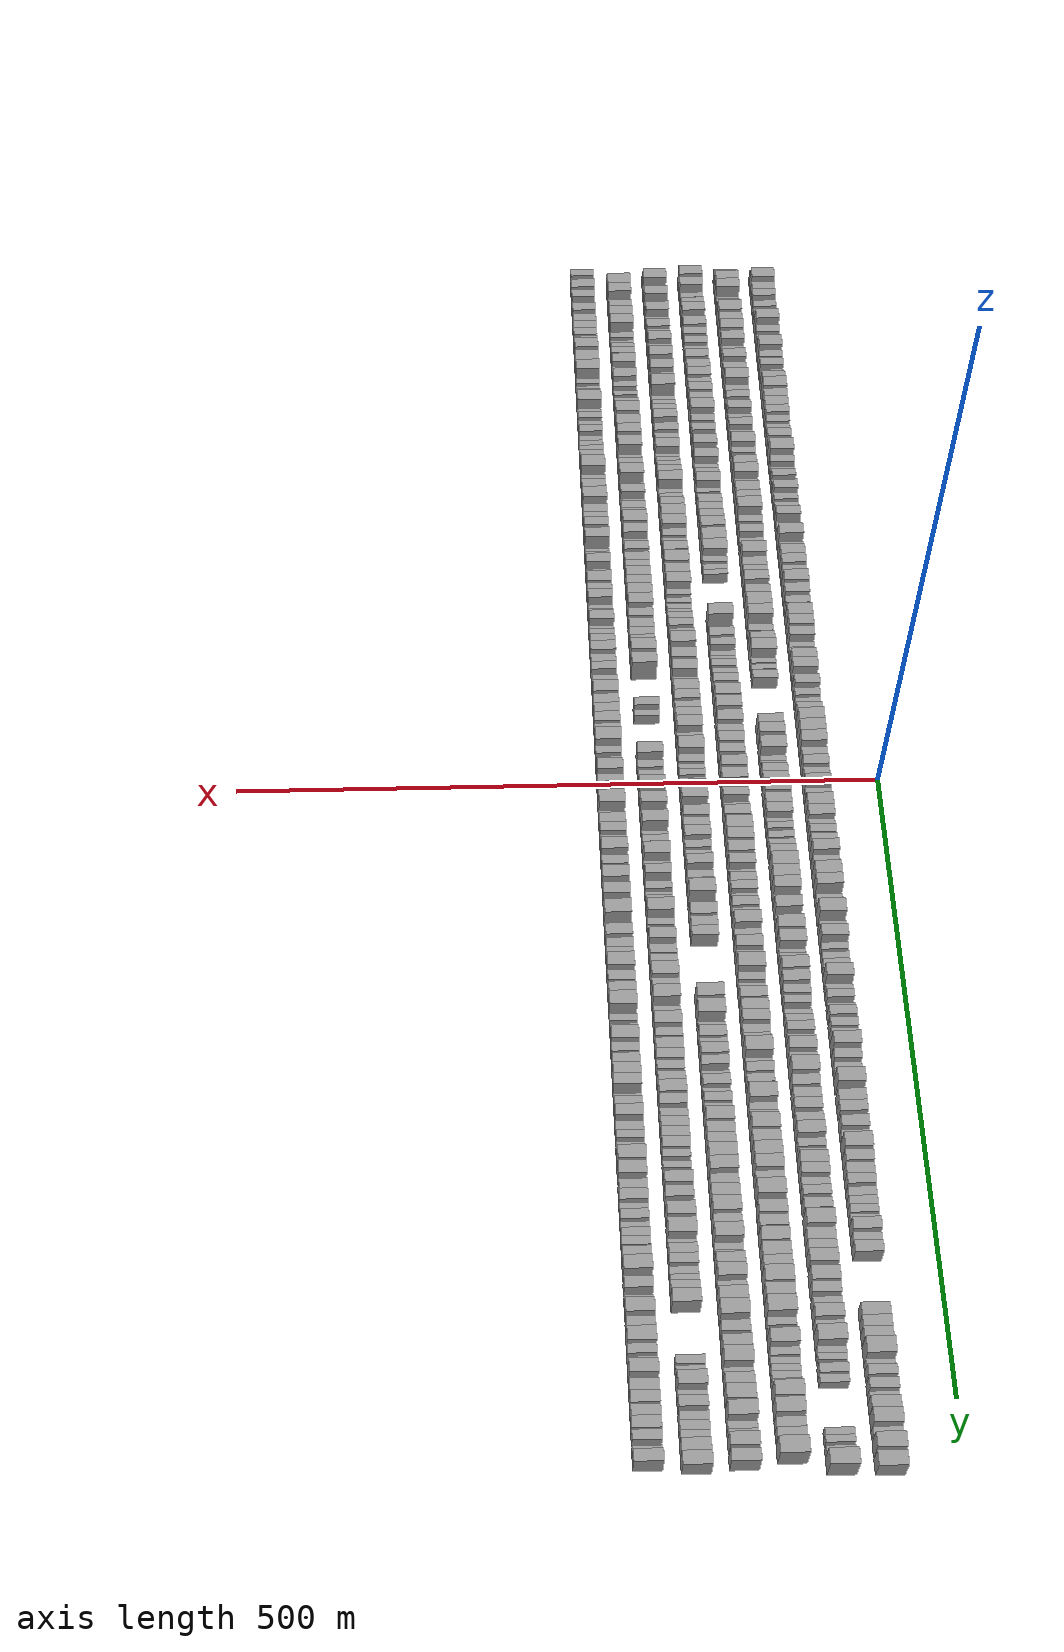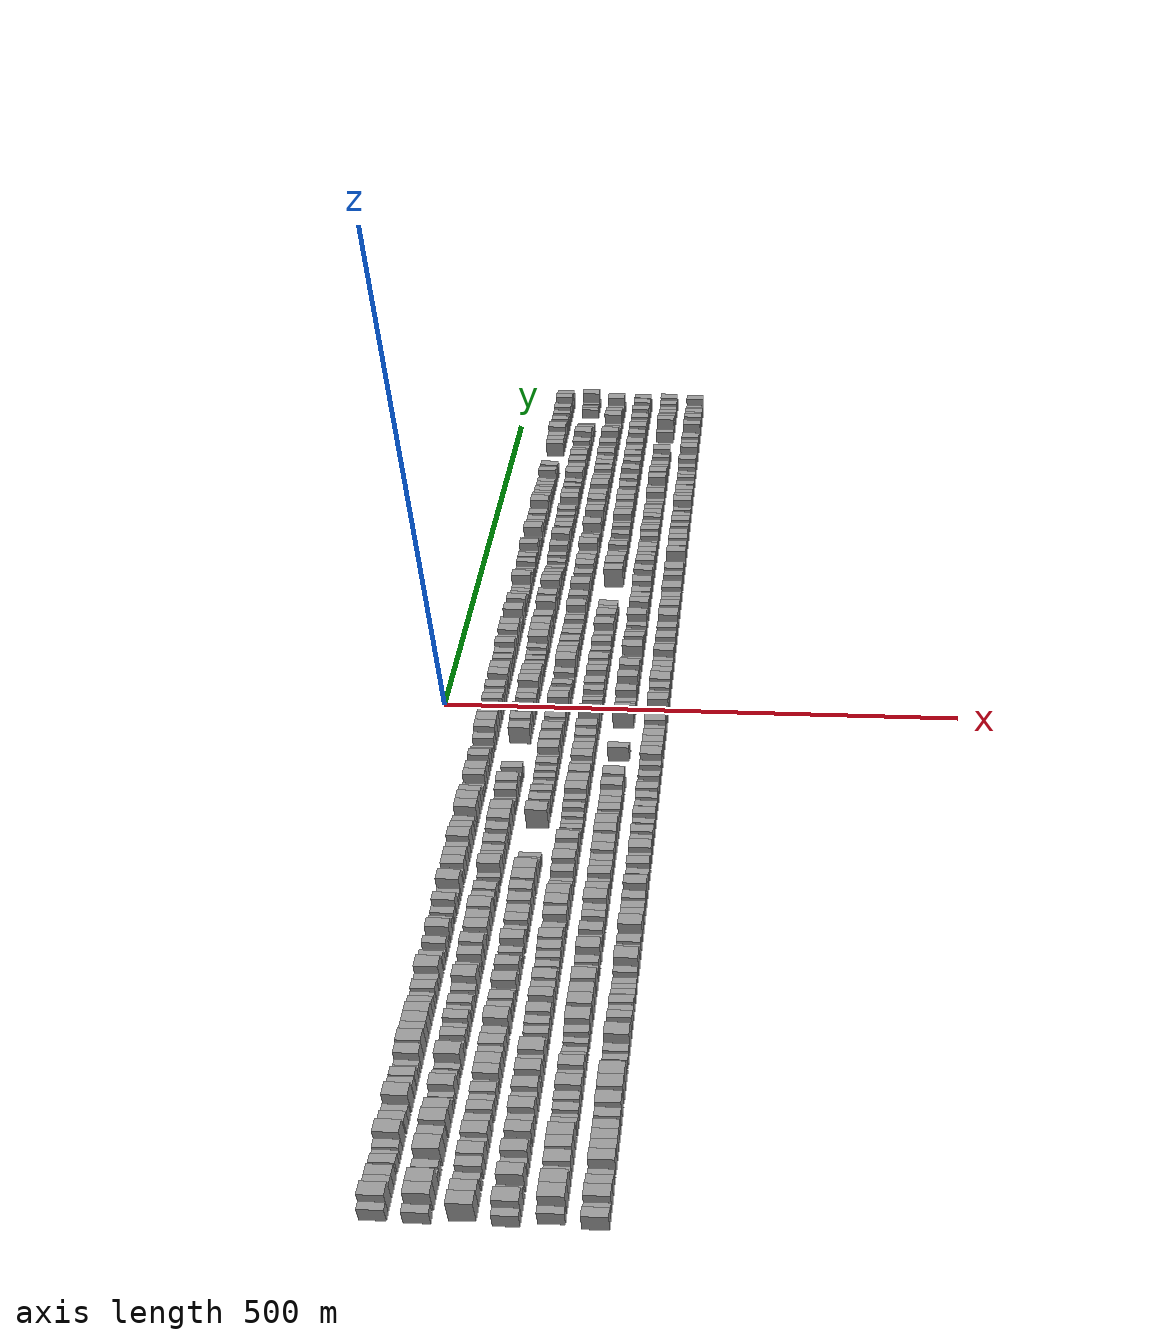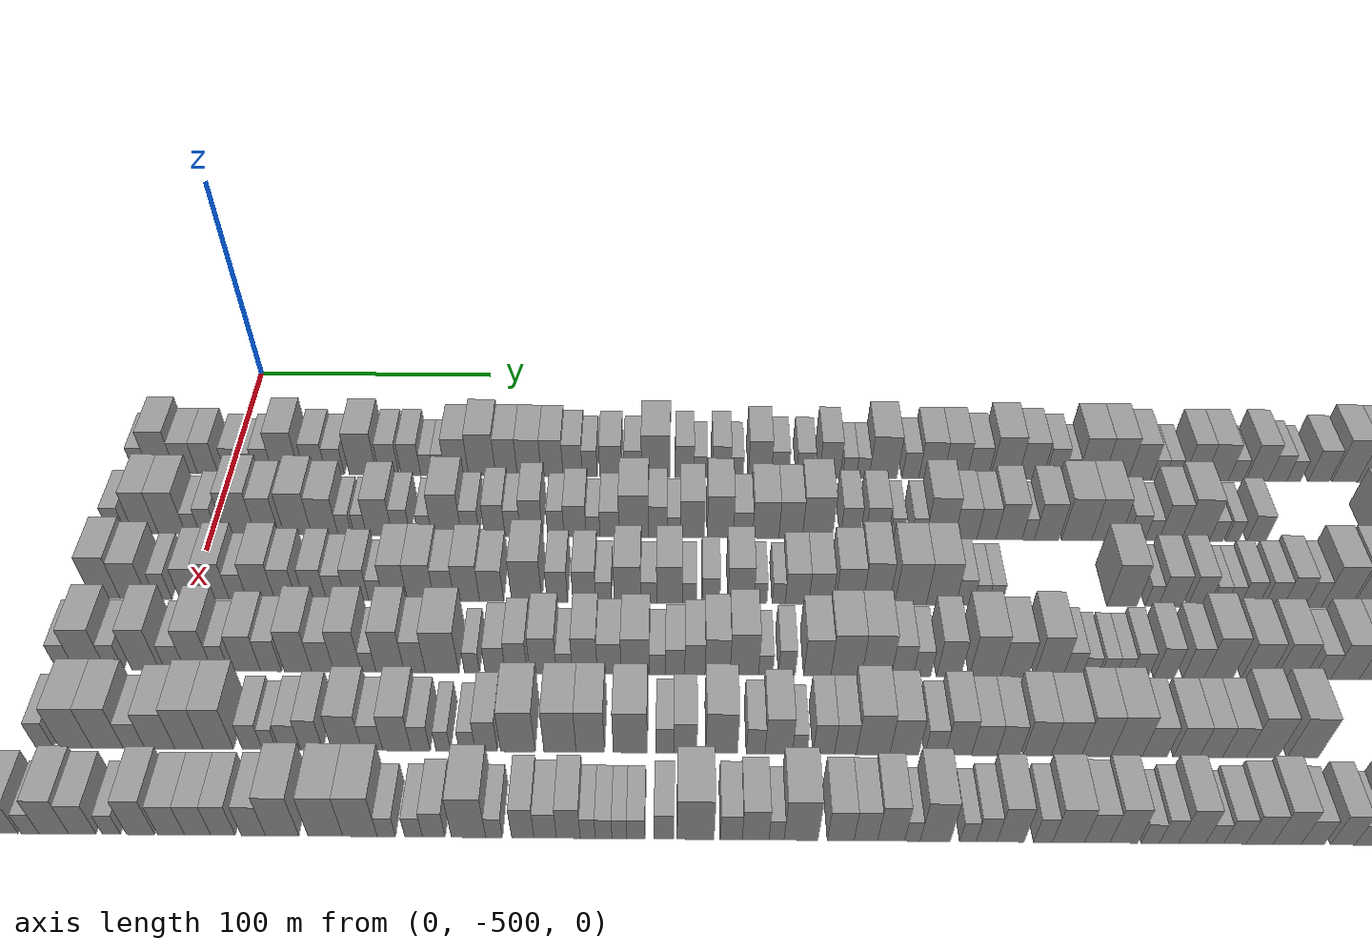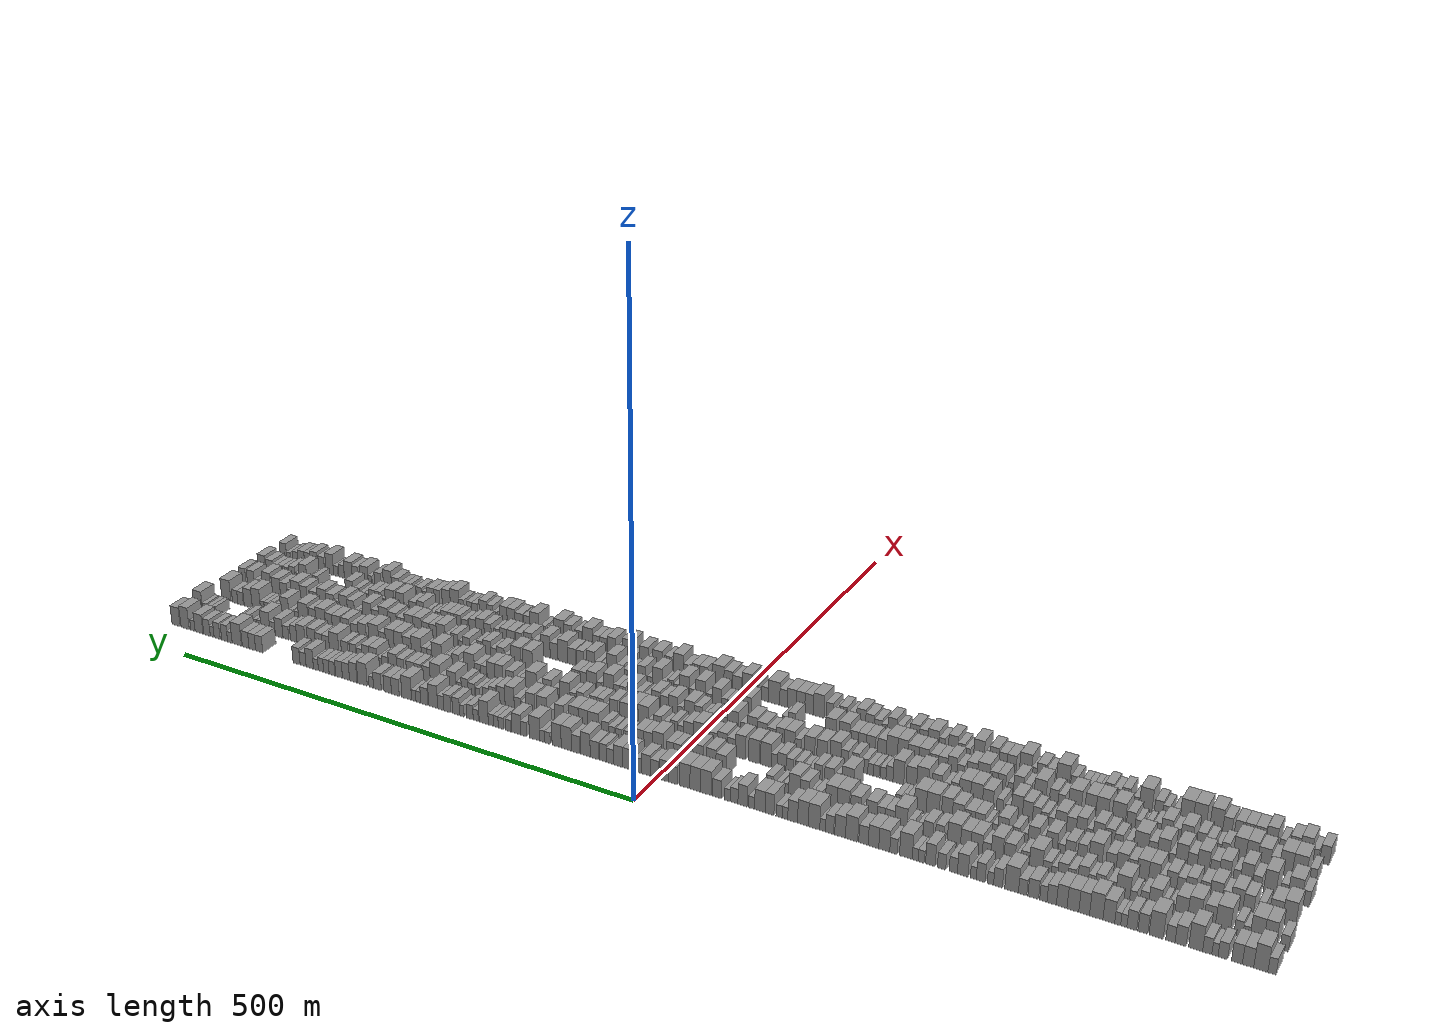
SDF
<sdf version="1.6">
 <world name="default">
  <scene>
   <sky><clouds><speed>12</speed></clouds></sky>
   <ambient>0.4 0.4 0.4 1</ambient>
   <background>0.7 0.7 0.7 1</background>
   <shadows>1</shadows>
  </scene>
  <gravity>0 0 -9.8066</gravity>
  <magnetic_field>6e-06 2.3e-05 -4.2e-05</magnetic_field>
  <physics default="0" name="default_physics" type="ode">
   <ode>
    <solver>
     <type>quick</type>
     <iters>10</iters>
     <sor>1.0</sor>
     <use_dynamic_moi_rescaling>0</use_dynamic_moi_rescaling>
    </solver>
    <constraints>
     <cfm>0</cfm>
     <erp>0.2</erp>
     <contact_max_correcting_vel>100</contact_max_correcting_vel>
     <contact_surface_layer>0.001</contact_surface_layer>
    </constraints>
   </ode>
   <max_step_size>0.004</max_step_size>
   <real_time_factor>1</real_time_factor>
   <real_time_update_rate>250</real_time_update_rate>
  </physics>
  <light name="sun" type="directional">
   <pose>0 0 10 0 0 0</pose>
   <diffuse>0.8 0.8 0.8 1</diffuse>
   <specular>0.2 0.2 0.2 1</specular>
   <attenuation>
    <range>1000</range>
    <constant>0.9</constant>
    <linear>0.01</linear>
    <quadratic>0.001</quadratic>
   </attenuation>
   <direction>-0.5 0.1 -0.9</direction>
  </light>
  <model name="building_1">
   <static>1</static>
   <pose>50.0000 -535.8745 0 0.000000 0.000000 0.000000</pose>
   <link name="link">
    <pose>0 0 7.50 0 0 0</pose>
    <collision name="collision"><geometry><box><size>20.0000 6.2510 15.0000</size></box></geometry></collision>
    <visual name="visual">
     <cast_shadows>0</cast_shadows>
     <geometry><box><size>20.0000 6.2510 15.0000</size></box></geometry>
     <material>
      <script>
       <uri>model://grey_wall/materials/scripts</uri>
       <uri>model://grey_wall/materials/textures</uri>
       <name>vrc/grey_wall</name>
      </script>
     </material>
    </visual>
   </link>
  </model>
  <model name="building_2">
   <static>1</static>
   <pose>50.0000 -527.3522 0 0.000000 0.000000 0.000000</pose>
   <link name="link">
    <pose>0 0 12.00 0 0 0</pose>
    <collision name="collision"><geometry><box><size>20.0000 10.7935 24.0000</size></box></geometry></collision>
    <visual name="visual">
     <cast_shadows>0</cast_shadows>
     <geometry><box><size>20.0000 10.7935 24.0000</size></box></geometry>
     <material>
      <script>
       <uri>model://grey_wall/materials/scripts</uri>
       <uri>model://grey_wall/materials/textures</uri>
       <name>vrc/grey_wall</name>
      </script>
     </material>
    </visual>
   </link>
  </model>
  <model name="building_3">
   <static>1</static>
   <pose>50.0000 -517.6085 0 0.000000 0.000000 0.000000</pose>
   <link name="link">
    <pose>0 0 9.00 0 0 0</pose>
    <collision name="collision"><geometry><box><size>20.0000 8.6939 18.0000</size></box></geometry></collision>
    <visual name="visual">
     <cast_shadows>0</cast_shadows>
     <geometry><box><size>20.0000 8.6939 18.0000</size></box></geometry>
     <material>
      <script>
       <uri>model://grey_wall/materials/scripts</uri>
       <uri>model://grey_wall/materials/textures</uri>
       <name>vrc/grey_wall</name>
      </script>
     </material>
    </visual>
   </link>
  </model>
  <model name="building_4">
   <static>1</static>
   <pose>50.0000 -509.1116 0 0.000000 0.000000 0.000000</pose>
   <link name="link">
    <pose>0 0 9.00 0 0 0</pose>
    <collision name="collision"><geometry><box><size>20.0000 8.2998 18.0000</size></box></geometry></collision>
    <visual name="visual">
     <cast_shadows>0</cast_shadows>
     <geometry><box><size>20.0000 8.2998 18.0000</size></box></geometry>
     <material>
      <script>
       <uri>model://grey_wall/materials/scripts</uri>
       <uri>model://grey_wall/materials/textures</uri>
       <name>vrc/grey_wall</name>
      </script>
     </material>
    </visual>
   </link>
  </model>
  <model name="building_5">
   <static>1</static>
   <pose>50.0000 -498.2551 0 0.000000 0.000000 0.000000</pose>
   <link name="link">
    <pose>0 0 7.50 0 0 0</pose>
    <collision name="collision"><geometry><box><size>20.0000 7.4133 15.0000</size></box></geometry></collision>
    <visual name="visual">
     <cast_shadows>0</cast_shadows>
     <geometry><box><size>20.0000 7.4133 15.0000</size></box></geometry>
     <material>
      <script>
       <uri>model://grey_wall/materials/scripts</uri>
       <uri>model://grey_wall/materials/textures</uri>
       <name>vrc/grey_wall</name>
      </script>
     </material>
    </visual>
   </link>
  </model>
  <model name="building_6">
   <static>1</static>
   <pose>50.0000 -492.1397 0 0.000000 0.000000 0.000000</pose>
   <link name="link">
    <pose>0 0 6.00 0 0 0</pose>
    <collision name="collision"><geometry><box><size>20.0000 4.8175 12.0000</size></box></geometry></collision>
    <visual name="visual">
     <cast_shadows>0</cast_shadows>
     <geometry><box><size>20.0000 4.8175 12.0000</size></box></geometry>
     <material>
      <script>
       <uri>model://grey_wall/materials/scripts</uri>
       <uri>model://grey_wall/materials/textures</uri>
       <name>vrc/grey_wall</name>
      </script>
     </material>
    </visual>
   </link>
  </model>
  <model name="building_7">
   <static>1</static>
   <pose>50.0000 -486.1267 0 0.000000 0.000000 0.000000</pose>
   <link name="link">
    <pose>0 0 7.50 0 0 0</pose>
    <collision name="collision"><geometry><box><size>20.0000 7.2085 15.0000</size></box></geometry></collision>
    <visual name="visual">
     <cast_shadows>0</cast_shadows>
     <geometry><box><size>20.0000 7.2085 15.0000</size></box></geometry>
     <material>
      <script>
       <uri>model://grey_wall/materials/scripts</uri>
       <uri>model://grey_wall/materials/textures</uri>
       <name>vrc/grey_wall</name>
      </script>
     </material>
    </visual>
   </link>
  </model>
  <model name="building_8">
   <static>1</static>
   <pose>50.0000 -477.0658 0 0.000000 0.000000 0.000000</pose>
   <link name="link">
    <pose>0 0 12.00 0 0 0</pose>
    <collision name="collision"><geometry><box><size>20.0000 10.9132 24.0000</size></box></geometry></collision>
    <visual name="visual">
     <cast_shadows>0</cast_shadows>
     <geometry><box><size>20.0000 10.9132 24.0000</size></box></geometry>
     <material>
      <script>
       <uri>model://grey_wall/materials/scripts</uri>
       <uri>model://grey_wall/materials/textures</uri>
       <name>vrc/grey_wall</name>
      </script>
     </material>
    </visual>
   </link>
  </model>
  <model name="building_9">
   <static>1</static>
   <pose>50.0000 -465.2385 0 0.000000 0.000000 0.000000</pose>
   <link name="link">
    <pose>0 0 9.00 0 0 0</pose>
    <collision name="collision"><geometry><box><size>20.0000 8.7415 18.0000</size></box></geometry></collision>
    <visual name="visual">
     <cast_shadows>0</cast_shadows>
     <geometry><box><size>20.0000 8.7415 18.0000</size></box></geometry>
     <material>
      <script>
       <uri>model://grey_wall/materials/scripts</uri>
       <uri>model://grey_wall/materials/textures</uri>
       <name>vrc/grey_wall</name>
      </script>
     </material>
    </visual>
   </link>
  </model>
  <model name="building_10">
   <static>1</static>
   <pose>50.0000 -457.1915 0 0.000000 0.000000 0.000000</pose>
   <link name="link">
    <pose>0 0 7.50 0 0 0</pose>
    <collision name="collision"><geometry><box><size>20.0000 7.3526 15.0000</size></box></geometry></collision>
    <visual name="visual">
     <cast_shadows>0</cast_shadows>
     <geometry><box><size>20.0000 7.3526 15.0000</size></box></geometry>
     <material>
      <script>
       <uri>model://grey_wall/materials/scripts</uri>
       <uri>model://grey_wall/materials/textures</uri>
       <name>vrc/grey_wall</name>
      </script>
     </material>
    </visual>
   </link>
  </model>
  <model name="building_11">
   <static>1</static>
   <pose>50.0000 -445.8810 0 0.000000 0.000000 0.000000</pose>
   <link name="link">
    <pose>0 0 12.00 0 0 0</pose>
    <collision name="collision"><geometry><box><size>20.0000 11.2683 24.0000</size></box></geometry></collision>
    <visual name="visual">
     <cast_shadows>0</cast_shadows>
     <geometry><box><size>20.0000 11.2683 24.0000</size></box></geometry>
     <material>
      <script>
       <uri>model://grey_wall/materials/scripts</uri>
       <uri>model://grey_wall/materials/textures</uri>
       <name>vrc/grey_wall</name>
      </script>
     </material>
    </visual>
   </link>
  </model>
  <model name="building_12">
   <static>1</static>
   <pose>50.0000 -435.3083 0 0.000000 0.000000 0.000000</pose>
   <link name="link">
    <pose>0 0 9.00 0 0 0</pose>
    <collision name="collision"><geometry><box><size>20.0000 7.8771 18.0000</size></box></geometry></collision>
    <visual name="visual">
     <cast_shadows>0</cast_shadows>
     <geometry><box><size>20.0000 7.8771 18.0000</size></box></geometry>
     <material>
      <script>
       <uri>model://grey_wall/materials/scripts</uri>
       <uri>model://grey_wall/materials/textures</uri>
       <name>vrc/grey_wall</name>
      </script>
     </material>
    </visual>
   </link>
  </model>
  <model name="building_13">
   <static>1</static>
   <pose>50.0000 -426.4122 0 0.000000 0.000000 0.000000</pose>
   <link name="link">
    <pose>0 0 9.00 0 0 0</pose>
    <collision name="collision"><geometry><box><size>20.0000 7.9150 18.0000</size></box></geometry></collision>
    <visual name="visual">
     <cast_shadows>0</cast_shadows>
     <geometry><box><size>20.0000 7.9150 18.0000</size></box></geometry>
     <material>
      <script>
       <uri>model://grey_wall/materials/scripts</uri>
       <uri>model://grey_wall/materials/textures</uri>
       <name>vrc/grey_wall</name>
      </script>
     </material>
    </visual>
   </link>
  </model>
  <model name="building_14">
   <static>1</static>
   <pose>50.0000 -419.9641 0 0.000000 0.000000 0.000000</pose>
   <link name="link">
    <pose>0 0 6.00 0 0 0</pose>
    <collision name="collision"><geometry><box><size>20.0000 4.9811 12.0000</size></box></geometry></collision>
    <visual name="visual">
     <cast_shadows>0</cast_shadows>
     <geometry><box><size>20.0000 4.9811 12.0000</size></box></geometry>
     <material>
      <script>
       <uri>model://grey_wall/materials/scripts</uri>
       <uri>model://grey_wall/materials/textures</uri>
       <name>vrc/grey_wall</name>
      </script>
     </material>
    </visual>
   </link>
  </model>
  <model name="building_15">
   <static>1</static>
   <pose>50.0000 -415.0267 0 0.000000 0.000000 0.000000</pose>
   <link name="link">
    <pose>0 0 6.00 0 0 0</pose>
    <collision name="collision"><geometry><box><size>20.0000 4.8937 12.0000</size></box></geometry></collision>
    <visual name="visual">
     <cast_shadows>0</cast_shadows>
     <geometry><box><size>20.0000 4.8937 12.0000</size></box></geometry>
     <material>
      <script>
       <uri>model://grey_wall/materials/scripts</uri>
       <uri>model://grey_wall/materials/textures</uri>
       <name>vrc/grey_wall</name>
      </script>
     </material>
    </visual>
   </link>
  </model>
  <model name="building_16">
   <static>1</static>
   <pose>50.0000 -407.8297 0 0.000000 0.000000 0.000000</pose>
   <link name="link">
    <pose>0 0 10.50 0 0 0</pose>
    <collision name="collision"><geometry><box><size>20.0000 9.5003 21.0000</size></box></geometry></collision>
    <visual name="visual">
     <cast_shadows>0</cast_shadows>
     <geometry><box><size>20.0000 9.5003 21.0000</size></box></geometry>
     <material>
      <script>
       <uri>model://grey_wall/materials/scripts</uri>
       <uri>model://grey_wall/materials/textures</uri>
       <name>vrc/grey_wall</name>
      </script>
     </material>
    </visual>
   </link>
  </model>
  <model name="building_17">
   <static>1</static>
   <pose>50.0000 -397.5698 0 0.000000 0.000000 0.000000</pose>
   <link name="link">
    <pose>0 0 12.00 0 0 0</pose>
    <collision name="collision"><geometry><box><size>20.0000 11.0195 24.0000</size></box></geometry></collision>
    <visual name="visual">
     <cast_shadows>0</cast_shadows>
     <geometry><box><size>20.0000 11.0195 24.0000</size></box></geometry>
     <material>
      <script>
       <uri>model://grey_wall/materials/scripts</uri>
       <uri>model://grey_wall/materials/textures</uri>
       <name>vrc/grey_wall</name>
      </script>
     </material>
    </visual>
   </link>
  </model>
  <model name="building_18">
   <static>1</static>
   <pose>50.0000 -387.6795 0 0.000000 0.000000 0.000000</pose>
   <link name="link">
    <pose>0 0 10.50 0 0 0</pose>
    <collision name="collision"><geometry><box><size>20.0000 8.7612 21.0000</size></box></geometry></collision>
    <visual name="visual">
     <cast_shadows>0</cast_shadows>
     <geometry><box><size>20.0000 8.7612 21.0000</size></box></geometry>
     <material>
      <script>
       <uri>model://grey_wall/materials/scripts</uri>
       <uri>model://grey_wall/materials/textures</uri>
       <name>vrc/grey_wall</name>
      </script>
     </material>
    </visual>
   </link>
  </model>
  <model name="building_19">
   <static>1</static>
   <pose>50.0000 -378.4234 0 0.000000 0.000000 0.000000</pose>
   <link name="link">
    <pose>0 0 10.50 0 0 0</pose>
    <collision name="collision"><geometry><box><size>20.0000 9.7509 21.0000</size></box></geometry></collision>
    <visual name="visual">
     <cast_shadows>0</cast_shadows>
     <geometry><box><size>20.0000 9.7509 21.0000</size></box></geometry>
     <material>
      <script>
       <uri>model://grey_wall/materials/scripts</uri>
       <uri>model://grey_wall/materials/textures</uri>
       <name>vrc/grey_wall</name>
      </script>
     </material>
    </visual>
   </link>
  </model>
  <model name="building_20">
   <static>1</static>
   <pose>50.0000 -369.1313 0 0.000000 0.000000 0.000000</pose>
   <link name="link">
    <pose>0 0 10.50 0 0 0</pose>
    <collision name="collision"><geometry><box><size>20.0000 8.8333 21.0000</size></box></geometry></collision>
    <visual name="visual">
     <cast_shadows>0</cast_shadows>
     <geometry><box><size>20.0000 8.8333 21.0000</size></box></geometry>
     <material>
      <script>
       <uri>model://grey_wall/materials/scripts</uri>
       <uri>model://grey_wall/materials/textures</uri>
       <name>vrc/grey_wall</name>
      </script>
     </material>
    </visual>
   </link>
  </model>
  <model name="building_21">
   <static>1</static>
   <pose>50.0000 -360.8004 0 0.000000 0.000000 0.000000</pose>
   <link name="link">
    <pose>0 0 9.00 0 0 0</pose>
    <collision name="collision"><geometry><box><size>20.0000 7.8284 18.0000</size></box></geometry></collision>
    <visual name="visual">
     <cast_shadows>0</cast_shadows>
     <geometry><box><size>20.0000 7.8284 18.0000</size></box></geometry>
     <material>
      <script>
       <uri>model://grey_wall/materials/scripts</uri>
       <uri>model://grey_wall/materials/textures</uri>
       <name>vrc/grey_wall</name>
      </script>
     </material>
    </visual>
   </link>
  </model>
  <model name="building_22">
   <static>1</static>
   <pose>50.0000 -353.8517 0 0.000000 0.000000 0.000000</pose>
   <link name="link">
    <pose>0 0 7.50 0 0 0</pose>
    <collision name="collision"><geometry><box><size>20.0000 6.0690 15.0000</size></box></geometry></collision>
    <visual name="visual">
     <cast_shadows>0</cast_shadows>
     <geometry><box><size>20.0000 6.0690 15.0000</size></box></geometry>
     <material>
      <script>
       <uri>model://grey_wall/materials/scripts</uri>
       <uri>model://grey_wall/materials/textures</uri>
       <name>vrc/grey_wall</name>
      </script>
     </material>
    </visual>
   </link>
  </model>
  <model name="building_23">
   <static>1</static>
   <pose>50.0000 -345.3466 0 0.000000 0.000000 0.000000</pose>
   <link name="link">
    <pose>0 0 9.00 0 0 0</pose>
    <collision name="collision"><geometry><box><size>20.0000 8.9413 18.0000</size></box></geometry></collision>
    <visual name="visual">
     <cast_shadows>0</cast_shadows>
     <geometry><box><size>20.0000 8.9413 18.0000</size></box></geometry>
     <material>
      <script>
       <uri>model://grey_wall/materials/scripts</uri>
       <uri>model://grey_wall/materials/textures</uri>
       <name>vrc/grey_wall</name>
      </script>
     </material>
    </visual>
   </link>
  </model>
  <model name="building_24">
   <static>1</static>
   <pose>50.0000 -336.3750 0 0.000000 0.000000 0.000000</pose>
   <link name="link">
    <pose>0 0 7.50 0 0 0</pose>
    <collision name="collision"><geometry><box><size>20.0000 7.0018 15.0000</size></box></geometry></collision>
    <visual name="visual">
     <cast_shadows>0</cast_shadows>
     <geometry><box><size>20.0000 7.0018 15.0000</size></box></geometry>
     <material>
      <script>
       <uri>model://grey_wall/materials/scripts</uri>
       <uri>model://grey_wall/materials/textures</uri>
       <name>vrc/grey_wall</name>
      </script>
     </material>
    </visual>
   </link>
  </model>
  <model name="building_25">
   <static>1</static>
   <pose>50.0000 -327.0672 0 0.000000 0.000000 0.000000</pose>
   <link name="link">
    <pose>0 0 12.00 0 0 0</pose>
    <collision name="collision"><geometry><box><size>20.0000 11.6138 24.0000</size></box></geometry></collision>
    <visual name="visual">
     <cast_shadows>0</cast_shadows>
     <geometry><box><size>20.0000 11.6138 24.0000</size></box></geometry>
     <material>
      <script>
       <uri>model://grey_wall/materials/scripts</uri>
       <uri>model://grey_wall/materials/textures</uri>
       <name>vrc/grey_wall</name>
      </script>
     </material>
    </visual>
   </link>
  </model>
  <model name="building_26">
   <static>1</static>
   <pose>50.0000 -315.4722 0 0.000000 0.000000 0.000000</pose>
   <link name="link">
    <pose>0 0 9.00 0 0 0</pose>
    <collision name="collision"><geometry><box><size>20.0000 7.5762 18.0000</size></box></geometry></collision>
    <visual name="visual">
     <cast_shadows>0</cast_shadows>
     <geometry><box><size>20.0000 7.5762 18.0000</size></box></geometry>
     <material>
      <script>
       <uri>model://grey_wall/materials/scripts</uri>
       <uri>model://grey_wall/materials/textures</uri>
       <name>vrc/grey_wall</name>
      </script>
     </material>
    </visual>
   </link>
  </model>
  <model name="building_27">
   <static>1</static>
   <pose>50.0000 -309.0196 0 0.000000 0.000000 0.000000</pose>
   <link name="link">
    <pose>0 0 6.00 0 0 0</pose>
    <collision name="collision"><geometry><box><size>20.0000 5.3289 12.0000</size></box></geometry></collision>
    <visual name="visual">
     <cast_shadows>0</cast_shadows>
     <geometry><box><size>20.0000 5.3289 12.0000</size></box></geometry>
     <material>
      <script>
       <uri>model://grey_wall/materials/scripts</uri>
       <uri>model://grey_wall/materials/textures</uri>
       <name>vrc/grey_wall</name>
      </script>
     </material>
    </visual>
   </link>
  </model>
  <model name="building_28">
   <static>1</static>
   <pose>50.0000 -300.5879 0 0.000000 0.000000 0.000000</pose>
   <link name="link">
    <pose>0 0 9.00 0 0 0</pose>
    <collision name="collision"><geometry><box><size>20.0000 7.5346 18.0000</size></box></geometry></collision>
    <visual name="visual">
     <cast_shadows>0</cast_shadows>
     <geometry><box><size>20.0000 7.5346 18.0000</size></box></geometry>
     <material>
      <script>
       <uri>model://grey_wall/materials/scripts</uri>
       <uri>model://grey_wall/materials/textures</uri>
       <name>vrc/grey_wall</name>
      </script>
     </material>
    </visual>
   </link>
  </model>
  <model name="building_29">
   <static>1</static>
   <pose>50.0000 -294.2849 0 0.000000 0.000000 0.000000</pose>
   <link name="link">
    <pose>0 0 6.00 0 0 0</pose>
    <collision name="collision"><geometry><box><size>20.0000 5.0713 12.0000</size></box></geometry></collision>
    <visual name="visual">
     <cast_shadows>0</cast_shadows>
     <geometry><box><size>20.0000 5.0713 12.0000</size></box></geometry>
     <material>
      <script>
       <uri>model://grey_wall/materials/scripts</uri>
       <uri>model://grey_wall/materials/textures</uri>
       <name>vrc/grey_wall</name>
      </script>
     </material>
    </visual>
   </link>
  </model>
  <model name="building_30">
   <static>1</static>
   <pose>50.0000 -285.0943 0 0.000000 0.000000 0.000000</pose>
   <link name="link">
    <pose>0 0 10.50 0 0 0</pose>
    <collision name="collision"><geometry><box><size>20.0000 9.3099 21.0000</size></box></geometry></collision>
    <visual name="visual">
     <cast_shadows>0</cast_shadows>
     <geometry><box><size>20.0000 9.3099 21.0000</size></box></geometry>
     <material>
      <script>
       <uri>model://grey_wall/materials/scripts</uri>
       <uri>model://grey_wall/materials/textures</uri>
       <name>vrc/grey_wall</name>
      </script>
     </material>
    </visual>
   </link>
  </model>
  <model name="building_31">
   <static>1</static>
   <pose>50.0000 -276.8961 0 0.000000 0.000000 0.000000</pose>
   <link name="link">
    <pose>0 0 7.50 0 0 0</pose>
    <collision name="collision"><geometry><box><size>20.0000 7.0864 15.0000</size></box></geometry></collision>
    <visual name="visual">
     <cast_shadows>0</cast_shadows>
     <geometry><box><size>20.0000 7.0864 15.0000</size></box></geometry>
     <material>
      <script>
       <uri>model://grey_wall/materials/scripts</uri>
       <uri>model://grey_wall/materials/textures</uri>
       <name>vrc/grey_wall</name>
      </script>
     </material>
    </visual>
   </link>
  </model>
  <model name="building_32">
   <static>1</static>
   <pose>50.0000 -266.7148 0 0.000000 0.000000 0.000000</pose>
   <link name="link">
    <pose>0 0 7.50 0 0 0</pose>
    <collision name="collision"><geometry><box><size>20.0000 7.2762 15.0000</size></box></geometry></collision>
    <visual name="visual">
     <cast_shadows>0</cast_shadows>
     <geometry><box><size>20.0000 7.2762 15.0000</size></box></geometry>
     <material>
      <script>
       <uri>model://grey_wall/materials/scripts</uri>
       <uri>model://grey_wall/materials/textures</uri>
       <name>vrc/grey_wall</name>
      </script>
     </material>
    </visual>
   </link>
  </model>
  <model name="building_33">
   <static>1</static>
   <pose>50.0000 -256.8597 0 0.000000 0.000000 0.000000</pose>
   <link name="link">
    <pose>0 0 10.50 0 0 0</pose>
    <collision name="collision"><geometry><box><size>20.0000 8.4340 21.0000</size></box></geometry></collision>
    <visual name="visual">
     <cast_shadows>0</cast_shadows>
     <geometry><box><size>20.0000 8.4340 21.0000</size></box></geometry>
     <material>
      <script>
       <uri>model://grey_wall/materials/scripts</uri>
       <uri>model://grey_wall/materials/textures</uri>
       <name>vrc/grey_wall</name>
      </script>
     </material>
    </visual>
   </link>
  </model>
  <model name="building_34">
   <static>1</static>
   <pose>50.0000 -248.8323 0 0.000000 0.000000 0.000000</pose>
   <link name="link">
    <pose>0 0 6.00 0 0 0</pose>
    <collision name="collision"><geometry><box><size>20.0000 5.6208 12.0000</size></box></geometry></collision>
    <visual name="visual">
     <cast_shadows>0</cast_shadows>
     <geometry><box><size>20.0000 5.6208 12.0000</size></box></geometry>
     <material>
      <script>
       <uri>model://grey_wall/materials/scripts</uri>
       <uri>model://grey_wall/materials/textures</uri>
       <name>vrc/grey_wall</name>
      </script>
     </material>
    </visual>
   </link>
  </model>
  <model name="building_35">
   <static>1</static>
   <pose>50.0000 -243.4255 0 0.000000 0.000000 0.000000</pose>
   <link name="link">
    <pose>0 0 6.00 0 0 0</pose>
    <collision name="collision"><geometry><box><size>20.0000 5.1930 12.0000</size></box></geometry></collision>
    <visual name="visual">
     <cast_shadows>0</cast_shadows>
     <geometry><box><size>20.0000 5.1930 12.0000</size></box></geometry>
     <material>
      <script>
       <uri>model://grey_wall/materials/scripts</uri>
       <uri>model://grey_wall/materials/textures</uri>
       <name>vrc/grey_wall</name>
      </script>
     </material>
    </visual>
   </link>
  </model>
  <model name="building_36">
   <static>1</static>
   <pose>50.0000 -235.1655 0 0.000000 0.000000 0.000000</pose>
   <link name="link">
    <pose>0 0 12.00 0 0 0</pose>
    <collision name="collision"><geometry><box><size>20.0000 11.3268 24.0000</size></box></geometry></collision>
    <visual name="visual">
     <cast_shadows>0</cast_shadows>
     <geometry><box><size>20.0000 11.3268 24.0000</size></box></geometry>
     <material>
      <script>
       <uri>model://grey_wall/materials/scripts</uri>
       <uri>model://grey_wall/materials/textures</uri>
       <name>vrc/grey_wall</name>
      </script>
     </material>
    </visual>
   </link>
  </model>
  <model name="building_37">
   <static>1</static>
   <pose>50.0000 -224.1235 0 0.000000 0.000000 0.000000</pose>
   <link name="link">
    <pose>0 0 7.50 0 0 0</pose>
    <collision name="collision"><geometry><box><size>20.0000 6.7573 15.0000</size></box></geometry></collision>
    <visual name="visual">
     <cast_shadows>0</cast_shadows>
     <geometry><box><size>20.0000 6.7573 15.0000</size></box></geometry>
     <material>
      <script>
       <uri>model://grey_wall/materials/scripts</uri>
       <uri>model://grey_wall/materials/textures</uri>
       <name>vrc/grey_wall</name>
      </script>
     </material>
    </visual>
   </link>
  </model>
  <model name="building_38">
   <static>1</static>
   <pose>50.0000 -215.8094 0 0.000000 0.000000 0.000000</pose>
   <link name="link">
    <pose>0 0 10.50 0 0 0</pose>
    <collision name="collision"><geometry><box><size>20.0000 9.8707 21.0000</size></box></geometry></collision>
    <visual name="visual">
     <cast_shadows>0</cast_shadows>
     <geometry><box><size>20.0000 9.8707 21.0000</size></box></geometry>
     <material>
      <script>
       <uri>model://grey_wall/materials/scripts</uri>
       <uri>model://grey_wall/materials/textures</uri>
       <name>vrc/grey_wall</name>
      </script>
     </material>
    </visual>
   </link>
  </model>
  <model name="building_39">
   <static>1</static>
   <pose>50.0000 -206.1048 0 0.000000 0.000000 0.000000</pose>
   <link name="link">
    <pose>0 0 10.50 0 0 0</pose>
    <collision name="collision"><geometry><box><size>20.0000 9.5386 21.0000</size></box></geometry></collision>
    <visual name="visual">
     <cast_shadows>0</cast_shadows>
     <geometry><box><size>20.0000 9.5386 21.0000</size></box></geometry>
     <material>
      <script>
       <uri>model://grey_wall/materials/scripts</uri>
       <uri>model://grey_wall/materials/textures</uri>
       <name>vrc/grey_wall</name>
      </script>
     </material>
    </visual>
   </link>
  </model>
  <model name="building_40">
   <static>1</static>
   <pose>50.0000 -197.0414 0 0.000000 0.000000 0.000000</pose>
   <link name="link">
    <pose>0 0 9.00 0 0 0</pose>
    <collision name="collision"><geometry><box><size>20.0000 8.5883 18.0000</size></box></geometry></collision>
    <visual name="visual">
     <cast_shadows>0</cast_shadows>
     <geometry><box><size>20.0000 8.5883 18.0000</size></box></geometry>
     <material>
      <script>
       <uri>model://grey_wall/materials/scripts</uri>
       <uri>model://grey_wall/materials/textures</uri>
       <name>vrc/grey_wall</name>
      </script>
     </material>
    </visual>
   </link>
  </model>
  <model name="building_41">
   <static>1</static>
   <pose>50.0000 -186.1750 0 0.000000 0.000000 0.000000</pose>
   <link name="link">
    <pose>0 0 12.00 0 0 0</pose>
    <collision name="collision"><geometry><box><size>20.0000 11.1445 24.0000</size></box></geometry></collision>
    <visual name="visual">
     <cast_shadows>0</cast_shadows>
     <geometry><box><size>20.0000 11.1445 24.0000</size></box></geometry>
     <material>
      <script>
       <uri>model://grey_wall/materials/scripts</uri>
       <uri>model://grey_wall/materials/textures</uri>
       <name>vrc/grey_wall</name>
      </script>
     </material>
    </visual>
   </link>
  </model>
  <model name="building_42">
   <static>1</static>
   <pose>50.0000 -175.6610 0 0.000000 0.000000 0.000000</pose>
   <link name="link">
    <pose>0 0 10.50 0 0 0</pose>
    <collision name="collision"><geometry><box><size>20.0000 9.8835 21.0000</size></box></geometry></collision>
    <visual name="visual">
     <cast_shadows>0</cast_shadows>
     <geometry><box><size>20.0000 9.8835 21.0000</size></box></geometry>
     <material>
      <script>
       <uri>model://grey_wall/materials/scripts</uri>
       <uri>model://grey_wall/materials/textures</uri>
       <name>vrc/grey_wall</name>
      </script>
     </material>
    </visual>
   </link>
  </model>
  <model name="building_43">
   <static>1</static>
   <pose>50.0000 -165.9902 0 0.000000 0.000000 0.000000</pose>
   <link name="link">
    <pose>0 0 9.00 0 0 0</pose>
    <collision name="collision"><geometry><box><size>20.0000 7.4580 18.0000</size></box></geometry></collision>
    <visual name="visual">
     <cast_shadows>0</cast_shadows>
     <geometry><box><size>20.0000 7.4580 18.0000</size></box></geometry>
     <material>
      <script>
       <uri>model://grey_wall/materials/scripts</uri>
       <uri>model://grey_wall/materials/textures</uri>
       <name>vrc/grey_wall</name>
      </script>
     </material>
    </visual>
   </link>
  </model>
  <model name="building_44">
   <static>1</static>
   <pose>50.0000 -159.6006 0 0.000000 0.000000 0.000000</pose>
   <link name="link">
    <pose>0 0 6.00 0 0 0</pose>
    <collision name="collision"><geometry><box><size>20.0000 5.3212 12.0000</size></box></geometry></collision>
    <visual name="visual">
     <cast_shadows>0</cast_shadows>
     <geometry><box><size>20.0000 5.3212 12.0000</size></box></geometry>
     <material>
      <script>
       <uri>model://grey_wall/materials/scripts</uri>
       <uri>model://grey_wall/materials/textures</uri>
       <name>vrc/grey_wall</name>
      </script>
     </material>
    </visual>
   </link>
  </model>
  <model name="building_45">
   <static>1</static>
   <pose>50.0000 -151.6141 0 0.000000 0.000000 0.000000</pose>
   <link name="link">
    <pose>0 0 12.00 0 0 0</pose>
    <collision name="collision"><geometry><box><size>20.0000 10.6518 24.0000</size></box></geometry></collision>
    <visual name="visual">
     <cast_shadows>0</cast_shadows>
     <geometry><box><size>20.0000 10.6518 24.0000</size></box></geometry>
     <material>
      <script>
       <uri>model://grey_wall/materials/scripts</uri>
       <uri>model://grey_wall/materials/textures</uri>
       <name>vrc/grey_wall</name>
      </script>
     </material>
    </visual>
   </link>
  </model>
  <model name="building_46">
   <static>1</static>
   <pose>50.0000 -141.2624 0 0.000000 0.000000 0.000000</pose>
   <link name="link">
    <pose>0 0 12.00 0 0 0</pose>
    <collision name="collision"><geometry><box><size>20.0000 10.0516 24.0000</size></box></geometry></collision>
    <visual name="visual">
     <cast_shadows>0</cast_shadows>
     <geometry><box><size>20.0000 10.0516 24.0000</size></box></geometry>
     <material>
      <script>
       <uri>model://grey_wall/materials/scripts</uri>
       <uri>model://grey_wall/materials/textures</uri>
       <name>vrc/grey_wall</name>
      </script>
     </material>
    </visual>
   </link>
  </model>
  <model name="building_47">
   <static>1</static>
   <pose>50.0000 -131.6291 0 0.000000 0.000000 0.000000</pose>
   <link name="link">
    <pose>0 0 10.50 0 0 0</pose>
    <collision name="collision"><geometry><box><size>20.0000 9.2149 21.0000</size></box></geometry></collision>
    <visual name="visual">
     <cast_shadows>0</cast_shadows>
     <geometry><box><size>20.0000 9.2149 21.0000</size></box></geometry>
     <material>
      <script>
       <uri>model://grey_wall/materials/scripts</uri>
       <uri>model://grey_wall/materials/textures</uri>
       <name>vrc/grey_wall</name>
      </script>
     </material>
    </visual>
   </link>
  </model>
  <model name="building_48">
   <static>1</static>
   <pose>50.0000 -124.3506 0 0.000000 0.000000 0.000000</pose>
   <link name="link">
    <pose>0 0 6.00 0 0 0</pose>
    <collision name="collision"><geometry><box><size>20.0000 5.3422 12.0000</size></box></geometry></collision>
    <visual name="visual">
     <cast_shadows>0</cast_shadows>
     <geometry><box><size>20.0000 5.3422 12.0000</size></box></geometry>
     <material>
      <script>
       <uri>model://grey_wall/materials/scripts</uri>
       <uri>model://grey_wall/materials/textures</uri>
       <name>vrc/grey_wall</name>
      </script>
     </material>
    </visual>
   </link>
  </model>
  <model name="building_49">
   <static>1</static>
   <pose>50.0000 -118.8210 0 0.000000 0.000000 0.000000</pose>
   <link name="link">
    <pose>0 0 6.00 0 0 0</pose>
    <collision name="collision"><geometry><box><size>20.0000 5.7169 12.0000</size></box></geometry></collision>
    <visual name="visual">
     <cast_shadows>0</cast_shadows>
     <geometry><box><size>20.0000 5.7169 12.0000</size></box></geometry>
     <material>
      <script>
       <uri>model://grey_wall/materials/scripts</uri>
       <uri>model://grey_wall/materials/textures</uri>
       <name>vrc/grey_wall</name>
      </script>
     </material>
    </visual>
   </link>
  </model>
  <model name="building_50">
   <static>1</static>
   <pose>50.0000 -109.7493 0 0.000000 0.000000 0.000000</pose>
   <link name="link">
    <pose>0 0 10.50 0 0 0</pose>
    <collision name="collision"><geometry><box><size>20.0000 8.4265 21.0000</size></box></geometry></collision>
    <visual name="visual">
     <cast_shadows>0</cast_shadows>
     <geometry><box><size>20.0000 8.4265 21.0000</size></box></geometry>
     <material>
      <script>
       <uri>model://grey_wall/materials/scripts</uri>
       <uri>model://grey_wall/materials/textures</uri>
       <name>vrc/grey_wall</name>
      </script>
     </material>
    </visual>
   </link>
  </model>
  <model name="building_51">
   <static>1</static>
   <pose>50.0000 -100.5956 0 0.000000 0.000000 0.000000</pose>
   <link name="link">
    <pose>0 0 10.50 0 0 0</pose>
    <collision name="collision"><geometry><box><size>20.0000 9.8809 21.0000</size></box></geometry></collision>
    <visual name="visual">
     <cast_shadows>0</cast_shadows>
     <geometry><box><size>20.0000 9.8809 21.0000</size></box></geometry>
     <material>
      <script>
       <uri>model://grey_wall/materials/scripts</uri>
       <uri>model://grey_wall/materials/textures</uri>
       <name>vrc/grey_wall</name>
      </script>
     </material>
    </visual>
   </link>
  </model>
  <model name="building_52">
   <static>1</static>
   <pose>50.0000 -92.6621 0 0.000000 0.000000 0.000000</pose>
   <link name="link">
    <pose>0 0 6.00 0 0 0</pose>
    <collision name="collision"><geometry><box><size>20.0000 5.9861 12.0000</size></box></geometry></collision>
    <visual name="visual">
     <cast_shadows>0</cast_shadows>
     <geometry><box><size>20.0000 5.9861 12.0000</size></box></geometry>
     <material>
      <script>
       <uri>model://grey_wall/materials/scripts</uri>
       <uri>model://grey_wall/materials/textures</uri>
       <name>vrc/grey_wall</name>
      </script>
     </material>
    </visual>
   </link>
  </model>
  <model name="building_53">
   <static>1</static>
   <pose>50.0000 -84.1280 0 0.000000 0.000000 0.000000</pose>
   <link name="link">
    <pose>0 0 10.50 0 0 0</pose>
    <collision name="collision"><geometry><box><size>20.0000 9.0822 21.0000</size></box></geometry></collision>
    <visual name="visual">
     <cast_shadows>0</cast_shadows>
     <geometry><box><size>20.0000 9.0822 21.0000</size></box></geometry>
     <material>
      <script>
       <uri>model://grey_wall/materials/scripts</uri>
       <uri>model://grey_wall/materials/textures</uri>
       <name>vrc/grey_wall</name>
      </script>
     </material>
    </visual>
   </link>
  </model>
  <model name="building_54">
   <static>1</static>
   <pose>50.0000 -75.8449 0 0.000000 0.000000 0.000000</pose>
   <link name="link">
    <pose>0 0 7.50 0 0 0</pose>
    <collision name="collision"><geometry><box><size>20.0000 7.4841 15.0000</size></box></geometry></collision>
    <visual name="visual">
     <cast_shadows>0</cast_shadows>
     <geometry><box><size>20.0000 7.4841 15.0000</size></box></geometry>
     <material>
      <script>
       <uri>model://grey_wall/materials/scripts</uri>
       <uri>model://grey_wall/materials/textures</uri>
       <name>vrc/grey_wall</name>
      </script>
     </material>
    </visual>
   </link>
  </model>
  <model name="building_55">
   <static>1</static>
   <pose>50.0000 -69.3058 0 0.000000 0.000000 0.000000</pose>
   <link name="link">
    <pose>0 0 6.00 0 0 0</pose>
    <collision name="collision"><geometry><box><size>20.0000 5.5941 12.0000</size></box></geometry></collision>
    <visual name="visual">
     <cast_shadows>0</cast_shadows>
     <geometry><box><size>20.0000 5.5941 12.0000</size></box></geometry>
     <material>
      <script>
       <uri>model://grey_wall/materials/scripts</uri>
       <uri>model://grey_wall/materials/textures</uri>
       <name>vrc/grey_wall</name>
      </script>
     </material>
    </visual>
   </link>
  </model>
  <model name="building_56">
   <static>1</static>
   <pose>50.0000 -59.1994 0 0.000000 0.000000 0.000000</pose>
   <link name="link">
    <pose>0 0 9.00 0 0 0</pose>
    <collision name="collision"><geometry><box><size>20.0000 8.6188 18.0000</size></box></geometry></collision>
    <visual name="visual">
     <cast_shadows>0</cast_shadows>
     <geometry><box><size>20.0000 8.6188 18.0000</size></box></geometry>
     <material>
      <script>
       <uri>model://grey_wall/materials/scripts</uri>
       <uri>model://grey_wall/materials/textures</uri>
       <name>vrc/grey_wall</name>
      </script>
     </material>
    </visual>
   </link>
  </model>
  <model name="building_57">
   <static>1</static>
   <pose>50.0000 -48.6681 0 0.000000 0.000000 0.000000</pose>
   <link name="link">
    <pose>0 0 12.00 0 0 0</pose>
    <collision name="collision"><geometry><box><size>20.0000 10.4438 24.0000</size></box></geometry></collision>
    <visual name="visual">
     <cast_shadows>0</cast_shadows>
     <geometry><box><size>20.0000 10.4438 24.0000</size></box></geometry>
     <material>
      <script>
       <uri>model://grey_wall/materials/scripts</uri>
       <uri>model://grey_wall/materials/textures</uri>
       <name>vrc/grey_wall</name>
      </script>
     </material>
    </visual>
   </link>
  </model>
  <model name="building_58">
   <static>1</static>
   <pose>50.0000 -38.1135 0 0.000000 0.000000 0.000000</pose>
   <link name="link">
    <pose>0 0 12.00 0 0 0</pose>
    <collision name="collision"><geometry><box><size>20.0000 10.6653 24.0000</size></box></geometry></collision>
    <visual name="visual">
     <cast_shadows>0</cast_shadows>
     <geometry><box><size>20.0000 10.6653 24.0000</size></box></geometry>
     <material>
      <script>
       <uri>model://grey_wall/materials/scripts</uri>
       <uri>model://grey_wall/materials/textures</uri>
       <name>vrc/grey_wall</name>
      </script>
     </material>
    </visual>
   </link>
  </model>
  <model name="building_59">
   <static>1</static>
   <pose>50.0000 -27.5451 0 0.000000 0.000000 0.000000</pose>
   <link name="link">
    <pose>0 0 12.00 0 0 0</pose>
    <collision name="collision"><geometry><box><size>20.0000 10.4714 24.0000</size></box></geometry></collision>
    <visual name="visual">
     <cast_shadows>0</cast_shadows>
     <geometry><box><size>20.0000 10.4714 24.0000</size></box></geometry>
     <material>
      <script>
       <uri>model://grey_wall/materials/scripts</uri>
       <uri>model://grey_wall/materials/textures</uri>
       <name>vrc/grey_wall</name>
      </script>
     </material>
    </visual>
   </link>
  </model>
  <model name="building_60">
   <static>1</static>
   <pose>50.0000 -15.8302 0 0.000000 0.000000 0.000000</pose>
   <link name="link">
    <pose>0 0 9.00 0 0 0</pose>
    <collision name="collision"><geometry><box><size>20.0000 8.9584 18.0000</size></box></geometry></collision>
    <visual name="visual">
     <cast_shadows>0</cast_shadows>
     <geometry><box><size>20.0000 8.9584 18.0000</size></box></geometry>
     <material>
      <script>
       <uri>model://grey_wall/materials/scripts</uri>
       <uri>model://grey_wall/materials/textures</uri>
       <name>vrc/grey_wall</name>
      </script>
     </material>
    </visual>
   </link>
  </model>
  <model name="building_61">
   <static>1</static>
   <pose>50.0000 -7.0068 0 0.000000 0.000000 0.000000</pose>
   <link name="link">
    <pose>0 0 10.50 0 0 0</pose>
    <collision name="collision"><geometry><box><size>20.0000 8.6884 21.0000</size></box></geometry></collision>
    <visual name="visual">
     <cast_shadows>0</cast_shadows>
     <geometry><box><size>20.0000 8.6884 21.0000</size></box></geometry>
     <material>
      <script>
       <uri>model://grey_wall/materials/scripts</uri>
       <uri>model://grey_wall/materials/textures</uri>
       <name>vrc/grey_wall</name>
      </script>
     </material>
    </visual>
   </link>
  </model>
  <model name="building_62">
   <static>1</static>
   <pose>50.0000 2.3282 0 0.000000 0.000000 0.000000</pose>
   <link name="link">
    <pose>0 0 9.00 0 0 0</pose>
    <collision name="collision"><geometry><box><size>20.0000 7.9817 18.0000</size></box></geometry></collision>
    <visual name="visual">
     <cast_shadows>0</cast_shadows>
     <geometry><box><size>20.0000 7.9817 18.0000</size></box></geometry>
     <material>
      <script>
       <uri>model://grey_wall/materials/scripts</uri>
       <uri>model://grey_wall/materials/textures</uri>
       <name>vrc/grey_wall</name>
      </script>
     </material>
    </visual>
   </link>
  </model>
  <model name="building_63">
   <static>1</static>
   <pose>50.0000 11.0979 0 0.000000 0.000000 0.000000</pose>
   <link name="link">
    <pose>0 0 10.50 0 0 0</pose>
    <collision name="collision"><geometry><box><size>20.0000 9.5577 21.0000</size></box></geometry></collision>
    <visual name="visual">
     <cast_shadows>0</cast_shadows>
     <geometry><box><size>20.0000 9.5577 21.0000</size></box></geometry>
     <material>
      <script>
       <uri>model://grey_wall/materials/scripts</uri>
       <uri>model://grey_wall/materials/textures</uri>
       <name>vrc/grey_wall</name>
      </script>
     </material>
    </visual>
   </link>
  </model>
  <model name="building_64">
   <static>1</static>
   <pose>50.0000 19.0012 0 0.000000 0.000000 0.000000</pose>
   <link name="link">
    <pose>0 0 7.50 0 0 0</pose>
    <collision name="collision"><geometry><box><size>20.0000 6.2488 15.0000</size></box></geometry></collision>
    <visual name="visual">
     <cast_shadows>0</cast_shadows>
     <geometry><box><size>20.0000 6.2488 15.0000</size></box></geometry>
     <material>
      <script>
       <uri>model://grey_wall/materials/scripts</uri>
       <uri>model://grey_wall/materials/textures</uri>
       <name>vrc/grey_wall</name>
      </script>
     </material>
    </visual>
   </link>
  </model>
  <model name="building_65">
   <static>1</static>
   <pose>50.0000 29.2712 0 0.000000 0.000000 0.000000</pose>
   <link name="link">
    <pose>0 0 10.50 0 0 0</pose>
    <collision name="collision"><geometry><box><size>20.0000 10.2913 21.0000</size></box></geometry></collision>
    <visual name="visual">
     <cast_shadows>0</cast_shadows>
     <geometry><box><size>20.0000 10.2913 21.0000</size></box></geometry>
     <material>
      <script>
       <uri>model://grey_wall/materials/scripts</uri>
       <uri>model://grey_wall/materials/textures</uri>
       <name>vrc/grey_wall</name>
      </script>
     </material>
    </visual>
   </link>
  </model>
  <model name="building_66">
   <static>1</static>
   <pose>50.0000 39.3015 0 0.000000 0.000000 0.000000</pose>
   <link name="link">
    <pose>0 0 10.50 0 0 0</pose>
    <collision name="collision"><geometry><box><size>20.0000 9.7692 21.0000</size></box></geometry></collision>
    <visual name="visual">
     <cast_shadows>0</cast_shadows>
     <geometry><box><size>20.0000 9.7692 21.0000</size></box></geometry>
     <material>
      <script>
       <uri>model://grey_wall/materials/scripts</uri>
       <uri>model://grey_wall/materials/textures</uri>
       <name>vrc/grey_wall</name>
      </script>
     </material>
    </visual>
   </link>
  </model>
  <model name="building_67">
   <static>1</static>
   <pose>50.0000 47.5614 0 0.000000 0.000000 0.000000</pose>
   <link name="link">
    <pose>0 0 7.50 0 0 0</pose>
    <collision name="collision"><geometry><box><size>20.0000 6.7507 15.0000</size></box></geometry></collision>
    <visual name="visual">
     <cast_shadows>0</cast_shadows>
     <geometry><box><size>20.0000 6.7507 15.0000</size></box></geometry>
     <material>
      <script>
       <uri>model://grey_wall/materials/scripts</uri>
       <uri>model://grey_wall/materials/textures</uri>
       <name>vrc/grey_wall</name>
      </script>
     </material>
    </visual>
   </link>
  </model>
  <model name="building_68">
   <static>1</static>
   <pose>50.0000 54.6114 0 0.000000 0.000000 0.000000</pose>
   <link name="link">
    <pose>0 0 9.00 0 0 0</pose>
    <collision name="collision"><geometry><box><size>20.0000 7.3493 18.0000</size></box></geometry></collision>
    <visual name="visual">
     <cast_shadows>0</cast_shadows>
     <geometry><box><size>20.0000 7.3493 18.0000</size></box></geometry>
     <material>
      <script>
       <uri>model://grey_wall/materials/scripts</uri>
       <uri>model://grey_wall/materials/textures</uri>
       <name>vrc/grey_wall</name>
      </script>
     </material>
    </visual>
   </link>
  </model>
  <model name="building_69">
   <static>1</static>
   <pose>50.0000 63.6352 0 0.000000 0.000000 0.000000</pose>
   <link name="link">
    <pose>0 0 9.00 0 0 0</pose>
    <collision name="collision"><geometry><box><size>20.0000 8.6982 18.0000</size></box></geometry></collision>
    <visual name="visual">
     <cast_shadows>0</cast_shadows>
     <geometry><box><size>20.0000 8.6982 18.0000</size></box></geometry>
     <material>
      <script>
       <uri>model://grey_wall/materials/scripts</uri>
       <uri>model://grey_wall/materials/textures</uri>
       <name>vrc/grey_wall</name>
      </script>
     </material>
    </visual>
   </link>
  </model>
  <model name="building_70">
   <static>1</static>
   <pose>50.0000 72.8361 0 0.000000 0.000000 0.000000</pose>
   <link name="link">
    <pose>0 0 12.00 0 0 0</pose>
    <collision name="collision"><geometry><box><size>20.0000 9.7035 24.0000</size></box></geometry></collision>
    <visual name="visual">
     <cast_shadows>0</cast_shadows>
     <geometry><box><size>20.0000 9.7035 24.0000</size></box></geometry>
     <material>
      <script>
       <uri>model://grey_wall/materials/scripts</uri>
       <uri>model://grey_wall/materials/textures</uri>
       <name>vrc/grey_wall</name>
      </script>
     </material>
    </visual>
   </link>
  </model>
  <model name="building_71">
   <static>1</static>
   <pose>50.0000 83.0669 0 0.000000 0.000000 0.000000</pose>
   <link name="link">
    <pose>0 0 9.00 0 0 0</pose>
    <collision name="collision"><geometry><box><size>20.0000 8.7582 18.0000</size></box></geometry></collision>
    <visual name="visual">
     <cast_shadows>0</cast_shadows>
     <geometry><box><size>20.0000 8.7582 18.0000</size></box></geometry>
     <material>
      <script>
       <uri>model://grey_wall/materials/scripts</uri>
       <uri>model://grey_wall/materials/textures</uri>
       <name>vrc/grey_wall</name>
      </script>
     </material>
    </visual>
   </link>
  </model>
  <model name="building_72">
   <static>1</static>
   <pose>50.0000 92.8284 0 0.000000 0.000000 0.000000</pose>
   <link name="link">
    <pose>0 0 12.00 0 0 0</pose>
    <collision name="collision"><geometry><box><size>20.0000 10.7647 24.0000</size></box></geometry></collision>
    <visual name="visual">
     <cast_shadows>0</cast_shadows>
     <geometry><box><size>20.0000 10.7647 24.0000</size></box></geometry>
     <material>
      <script>
       <uri>model://grey_wall/materials/scripts</uri>
       <uri>model://grey_wall/materials/textures</uri>
       <name>vrc/grey_wall</name>
      </script>
     </material>
    </visual>
   </link>
  </model>
  <model name="building_73">
   <static>1</static>
   <pose>50.0000 103.0163 0 0.000000 0.000000 0.000000</pose>
   <link name="link">
    <pose>0 0 12.00 0 0 0</pose>
    <collision name="collision"><geometry><box><size>20.0000 9.6111 24.0000</size></box></geometry></collision>
    <visual name="visual">
     <cast_shadows>0</cast_shadows>
     <geometry><box><size>20.0000 9.6111 24.0000</size></box></geometry>
     <material>
      <script>
       <uri>model://grey_wall/materials/scripts</uri>
       <uri>model://grey_wall/materials/textures</uri>
       <name>vrc/grey_wall</name>
      </script>
     </material>
    </visual>
   </link>
  </model>
  <model name="building_74">
   <static>1</static>
   <pose>50.0000 112.7758 0 0.000000 0.000000 0.000000</pose>
   <link name="link">
    <pose>0 0 6.00 0 0 0</pose>
    <collision name="collision"><geometry><box><size>20.0000 5.9079 12.0000</size></box></geometry></collision>
    <visual name="visual">
     <cast_shadows>0</cast_shadows>
     <geometry><box><size>20.0000 5.9079 12.0000</size></box></geometry>
     <material>
      <script>
       <uri>model://grey_wall/materials/scripts</uri>
       <uri>model://grey_wall/materials/textures</uri>
       <name>vrc/grey_wall</name>
      </script>
     </material>
    </visual>
   </link>
  </model>
  <model name="building_75">
   <static>1</static>
   <pose>50.0000 118.1994 0 0.000000 0.000000 0.000000</pose>
   <link name="link">
    <pose>0 0 6.00 0 0 0</pose>
    <collision name="collision"><geometry><box><size>20.0000 4.9392 12.0000</size></box></geometry></collision>
    <visual name="visual">
     <cast_shadows>0</cast_shadows>
     <geometry><box><size>20.0000 4.9392 12.0000</size></box></geometry>
     <material>
      <script>
       <uri>model://grey_wall/materials/scripts</uri>
       <uri>model://grey_wall/materials/textures</uri>
       <name>vrc/grey_wall</name>
      </script>
     </material>
    </visual>
   </link>
  </model>
  <model name="building_76">
   <static>1</static>
   <pose>50.0000 126.2864 0 0.000000 0.000000 0.000000</pose>
   <link name="link">
    <pose>0 0 12.00 0 0 0</pose>
    <collision name="collision"><geometry><box><size>20.0000 11.2349 24.0000</size></box></geometry></collision>
    <visual name="visual">
     <cast_shadows>0</cast_shadows>
     <geometry><box><size>20.0000 11.2349 24.0000</size></box></geometry>
     <material>
      <script>
       <uri>model://grey_wall/materials/scripts</uri>
       <uri>model://grey_wall/materials/textures</uri>
       <name>vrc/grey_wall</name>
      </script>
     </material>
    </visual>
   </link>
  </model>
  <model name="building_77">
   <static>1</static>
   <pose>50.0000 138.0626 0 0.000000 0.000000 0.000000</pose>
   <link name="link">
    <pose>0 0 7.50 0 0 0</pose>
    <collision name="collision"><geometry><box><size>20.0000 6.3176 15.0000</size></box></geometry></collision>
    <visual name="visual">
     <cast_shadows>0</cast_shadows>
     <geometry><box><size>20.0000 6.3176 15.0000</size></box></geometry>
     <material>
      <script>
       <uri>model://grey_wall/materials/scripts</uri>
       <uri>model://grey_wall/materials/textures</uri>
       <name>vrc/grey_wall</name>
      </script>
     </material>
    </visual>
   </link>
  </model>
  <model name="building_78">
   <static>1</static>
   <pose>50.0000 145.9544 0 0.000000 0.000000 0.000000</pose>
   <link name="link">
    <pose>0 0 10.50 0 0 0</pose>
    <collision name="collision"><geometry><box><size>20.0000 9.4658 21.0000</size></box></geometry></collision>
    <visual name="visual">
     <cast_shadows>0</cast_shadows>
     <geometry><box><size>20.0000 9.4658 21.0000</size></box></geometry>
     <material>
      <script>
       <uri>model://grey_wall/materials/scripts</uri>
       <uri>model://grey_wall/materials/textures</uri>
       <name>vrc/grey_wall</name>
      </script>
     </material>
    </visual>
   </link>
  </model>
  <model name="building_79">
   <static>1</static>
   <pose>50.0000 154.6687 0 0.000000 0.000000 0.000000</pose>
   <link name="link">
    <pose>0 0 6.00 0 0 0</pose>
    <collision name="collision"><geometry><box><size>20.0000 5.9629 12.0000</size></box></geometry></collision>
    <visual name="visual">
     <cast_shadows>0</cast_shadows>
     <geometry><box><size>20.0000 5.9629 12.0000</size></box></geometry>
     <material>
      <script>
       <uri>model://grey_wall/materials/scripts</uri>
       <uri>model://grey_wall/materials/textures</uri>
       <name>vrc/grey_wall</name>
      </script>
     </material>
    </visual>
   </link>
  </model>
  <model name="building_80">
   <static>1</static>
   <pose>50.0000 162.5306 0 0.000000 0.000000 0.000000</pose>
   <link name="link">
    <pose>0 0 6.00 0 0 0</pose>
    <collision name="collision"><geometry><box><size>20.0000 5.7607 12.0000</size></box></geometry></collision>
    <visual name="visual">
     <cast_shadows>0</cast_shadows>
     <geometry><box><size>20.0000 5.7607 12.0000</size></box></geometry>
     <material>
      <script>
       <uri>model://grey_wall/materials/scripts</uri>
       <uri>model://grey_wall/materials/textures</uri>
       <name>vrc/grey_wall</name>
      </script>
     </material>
    </visual>
   </link>
  </model>
  <model name="building_81">
   <static>1</static>
   <pose>50.0000 168.0531 0 0.000000 0.000000 0.000000</pose>
   <link name="link">
    <pose>0 0 6.00 0 0 0</pose>
    <collision name="collision"><geometry><box><size>20.0000 5.2844 12.0000</size></box></geometry></collision>
    <visual name="visual">
     <cast_shadows>0</cast_shadows>
     <geometry><box><size>20.0000 5.2844 12.0000</size></box></geometry>
     <material>
      <script>
       <uri>model://grey_wall/materials/scripts</uri>
       <uri>model://grey_wall/materials/textures</uri>
       <name>vrc/grey_wall</name>
      </script>
     </material>
    </visual>
   </link>
  </model>
  <model name="building_82">
   <static>1</static>
   <pose>50.0000 173.4659 0 0.000000 0.000000 0.000000</pose>
   <link name="link">
    <pose>0 0 6.00 0 0 0</pose>
    <collision name="collision"><geometry><box><size>20.0000 5.5410 12.0000</size></box></geometry></collision>
    <visual name="visual">
     <cast_shadows>0</cast_shadows>
     <geometry><box><size>20.0000 5.5410 12.0000</size></box></geometry>
     <material>
      <script>
       <uri>model://grey_wall/materials/scripts</uri>
       <uri>model://grey_wall/materials/textures</uri>
       <name>vrc/grey_wall</name>
      </script>
     </material>
    </visual>
   </link>
  </model>
  <model name="building_83">
   <static>1</static>
   <pose>50.0000 181.2107 0 0.000000 0.000000 0.000000</pose>
   <link name="link">
    <pose>0 0 12.00 0 0 0</pose>
    <collision name="collision"><geometry><box><size>20.0000 9.9487 24.0000</size></box></geometry></collision>
    <visual name="visual">
     <cast_shadows>0</cast_shadows>
     <geometry><box><size>20.0000 9.9487 24.0000</size></box></geometry>
     <material>
      <script>
       <uri>model://grey_wall/materials/scripts</uri>
       <uri>model://grey_wall/materials/textures</uri>
       <name>vrc/grey_wall</name>
      </script>
     </material>
    </visual>
   </link>
  </model>
  <model name="building_84">
   <static>1</static>
   <pose>50.0000 189.9863 0 0.000000 0.000000 0.000000</pose>
   <link name="link">
    <pose>0 0 6.00 0 0 0</pose>
    <collision name="collision"><geometry><box><size>20.0000 5.6026 12.0000</size></box></geometry></collision>
    <visual name="visual">
     <cast_shadows>0</cast_shadows>
     <geometry><box><size>20.0000 5.6026 12.0000</size></box></geometry>
     <material>
      <script>
       <uri>model://grey_wall/materials/scripts</uri>
       <uri>model://grey_wall/materials/textures</uri>
       <name>vrc/grey_wall</name>
      </script>
     </material>
    </visual>
   </link>
  </model>
  <model name="building_85">
   <static>1</static>
   <pose>50.0000 196.2868 0 0.000000 0.000000 0.000000</pose>
   <link name="link">
    <pose>0 0 7.50 0 0 0</pose>
    <collision name="collision"><geometry><box><size>20.0000 6.9983 15.0000</size></box></geometry></collision>
    <visual name="visual">
     <cast_shadows>0</cast_shadows>
     <geometry><box><size>20.0000 6.9983 15.0000</size></box></geometry>
     <material>
      <script>
       <uri>model://grey_wall/materials/scripts</uri>
       <uri>model://grey_wall/materials/textures</uri>
       <name>vrc/grey_wall</name>
      </script>
     </material>
    </visual>
   </link>
  </model>
  <model name="building_86">
   <static>1</static>
   <pose>50.0000 205.2603 0 0.000000 0.000000 0.000000</pose>
   <link name="link">
    <pose>0 0 6.00 0 0 0</pose>
    <collision name="collision"><geometry><box><size>20.0000 4.9488 12.0000</size></box></geometry></collision>
    <visual name="visual">
     <cast_shadows>0</cast_shadows>
     <geometry><box><size>20.0000 4.9488 12.0000</size></box></geometry>
     <material>
      <script>
       <uri>model://grey_wall/materials/scripts</uri>
       <uri>model://grey_wall/materials/textures</uri>
       <name>vrc/grey_wall</name>
      </script>
     </material>
    </visual>
   </link>
  </model>
  <model name="building_87">
   <static>1</static>
   <pose>50.0000 211.6419 0 0.000000 0.000000 0.000000</pose>
   <link name="link">
    <pose>0 0 9.00 0 0 0</pose>
    <collision name="collision"><geometry><box><size>20.0000 7.8144 18.0000</size></box></geometry></collision>
    <visual name="visual">
     <cast_shadows>0</cast_shadows>
     <geometry><box><size>20.0000 7.8144 18.0000</size></box></geometry>
     <material>
      <script>
       <uri>model://grey_wall/materials/scripts</uri>
       <uri>model://grey_wall/materials/textures</uri>
       <name>vrc/grey_wall</name>
      </script>
     </material>
    </visual>
   </link>
  </model>
  <model name="building_88">
   <static>1</static>
   <pose>50.0000 221.3936 0 0.000000 0.000000 0.000000</pose>
   <link name="link">
    <pose>0 0 9.00 0 0 0</pose>
    <collision name="collision"><geometry><box><size>20.0000 7.6889 18.0000</size></box></geometry></collision>
    <visual name="visual">
     <cast_shadows>0</cast_shadows>
     <geometry><box><size>20.0000 7.6889 18.0000</size></box></geometry>
     <material>
      <script>
       <uri>model://grey_wall/materials/scripts</uri>
       <uri>model://grey_wall/materials/textures</uri>
       <name>vrc/grey_wall</name>
      </script>
     </material>
    </visual>
   </link>
  </model>
  <model name="building_89">
   <static>1</static>
   <pose>50.0000 228.6966 0 0.000000 0.000000 0.000000</pose>
   <link name="link">
    <pose>0 0 7.50 0 0 0</pose>
    <collision name="collision"><geometry><box><size>20.0000 6.9171 15.0000</size></box></geometry></collision>
    <visual name="visual">
     <cast_shadows>0</cast_shadows>
     <geometry><box><size>20.0000 6.9171 15.0000</size></box></geometry>
     <material>
      <script>
       <uri>model://grey_wall/materials/scripts</uri>
       <uri>model://grey_wall/materials/textures</uri>
       <name>vrc/grey_wall</name>
      </script>
     </material>
    </visual>
   </link>
  </model>
  <model name="building_90">
   <static>1</static>
   <pose>50.0000 237.1487 0 0.000000 0.000000 0.000000</pose>
   <link name="link">
    <pose>0 0 12.00 0 0 0</pose>
    <collision name="collision"><geometry><box><size>20.0000 9.9870 24.0000</size></box></geometry></collision>
    <visual name="visual">
     <cast_shadows>0</cast_shadows>
     <geometry><box><size>20.0000 9.9870 24.0000</size></box></geometry>
     <material>
      <script>
       <uri>model://grey_wall/materials/scripts</uri>
       <uri>model://grey_wall/materials/textures</uri>
       <name>vrc/grey_wall</name>
      </script>
     </material>
    </visual>
   </link>
  </model>
  <model name="building_91">
   <static>1</static>
   <pose>50.0000 247.1616 0 0.000000 0.000000 0.000000</pose>
   <link name="link">
    <pose>0 0 9.00 0 0 0</pose>
    <collision name="collision"><geometry><box><size>20.0000 8.0387 18.0000</size></box></geometry></collision>
    <visual name="visual">
     <cast_shadows>0</cast_shadows>
     <geometry><box><size>20.0000 8.0387 18.0000</size></box></geometry>
     <material>
      <script>
       <uri>model://grey_wall/materials/scripts</uri>
       <uri>model://grey_wall/materials/textures</uri>
       <name>vrc/grey_wall</name>
      </script>
     </material>
    </visual>
   </link>
  </model>
  <model name="building_92">
   <static>1</static>
   <pose>50.0000 253.8727 0 0.000000 0.000000 0.000000</pose>
   <link name="link">
    <pose>0 0 6.00 0 0 0</pose>
    <collision name="collision"><geometry><box><size>20.0000 5.3836 12.0000</size></box></geometry></collision>
    <visual name="visual">
     <cast_shadows>0</cast_shadows>
     <geometry><box><size>20.0000 5.3836 12.0000</size></box></geometry>
     <material>
      <script>
       <uri>model://grey_wall/materials/scripts</uri>
       <uri>model://grey_wall/materials/textures</uri>
       <name>vrc/grey_wall</name>
      </script>
     </material>
    </visual>
   </link>
  </model>
  <model name="building_93">
   <static>1</static>
   <pose>50.0000 259.0503 0 0.000000 0.000000 0.000000</pose>
   <link name="link">
    <pose>0 0 6.00 0 0 0</pose>
    <collision name="collision"><geometry><box><size>20.0000 4.9715 12.0000</size></box></geometry></collision>
    <visual name="visual">
     <cast_shadows>0</cast_shadows>
     <geometry><box><size>20.0000 4.9715 12.0000</size></box></geometry>
     <material>
      <script>
       <uri>model://grey_wall/materials/scripts</uri>
       <uri>model://grey_wall/materials/textures</uri>
       <name>vrc/grey_wall</name>
      </script>
     </material>
    </visual>
   </link>
  </model>
  <model name="building_94">
   <static>1</static>
   <pose>50.0000 267.0421 0 0.000000 0.000000 0.000000</pose>
   <link name="link">
    <pose>0 0 12.00 0 0 0</pose>
    <collision name="collision"><geometry><box><size>20.0000 11.0121 24.0000</size></box></geometry></collision>
    <visual name="visual">
     <cast_shadows>0</cast_shadows>
     <geometry><box><size>20.0000 11.0121 24.0000</size></box></geometry>
     <material>
      <script>
       <uri>model://grey_wall/materials/scripts</uri>
       <uri>model://grey_wall/materials/textures</uri>
       <name>vrc/grey_wall</name>
      </script>
     </material>
    </visual>
   </link>
  </model>
  <model name="building_95">
   <static>1</static>
   <pose>50.0000 280.0065 0 0.000000 0.000000 0.000000</pose>
   <link name="link">
    <pose>0 0 9.00 0 0 0</pose>
    <collision name="collision"><geometry><box><size>20.0000 8.9168 18.0000</size></box></geometry></collision>
    <visual name="visual">
     <cast_shadows>0</cast_shadows>
     <geometry><box><size>20.0000 8.9168 18.0000</size></box></geometry>
     <material>
      <script>
       <uri>model://grey_wall/materials/scripts</uri>
       <uri>model://grey_wall/materials/textures</uri>
       <name>vrc/grey_wall</name>
      </script>
     </material>
    </visual>
   </link>
  </model>
  <model name="building_96">
   <static>1</static>
   <pose>50.0000 288.7651 0 0.000000 0.000000 0.000000</pose>
   <link name="link">
    <pose>0 0 9.00 0 0 0</pose>
    <collision name="collision"><geometry><box><size>20.0000 8.6003 18.0000</size></box></geometry></collision>
    <visual name="visual">
     <cast_shadows>0</cast_shadows>
     <geometry><box><size>20.0000 8.6003 18.0000</size></box></geometry>
     <material>
      <script>
       <uri>model://grey_wall/materials/scripts</uri>
       <uri>model://grey_wall/materials/textures</uri>
       <name>vrc/grey_wall</name>
      </script>
     </material>
    </visual>
   </link>
  </model>
  <model name="building_97">
   <static>1</static>
   <pose>50.0000 300.5587 0 0.000000 0.000000 0.000000</pose>
   <link name="link">
    <pose>0 0 9.00 0 0 0</pose>
    <collision name="collision"><geometry><box><size>20.0000 8.9869 18.0000</size></box></geometry></collision>
    <visual name="visual">
     <cast_shadows>0</cast_shadows>
     <geometry><box><size>20.0000 8.9869 18.0000</size></box></geometry>
     <material>
      <script>
       <uri>model://grey_wall/materials/scripts</uri>
       <uri>model://grey_wall/materials/textures</uri>
       <name>vrc/grey_wall</name>
      </script>
     </material>
    </visual>
   </link>
  </model>
  <model name="building_98">
   <static>1</static>
   <pose>50.0000 307.7086 0 0.000000 0.000000 0.000000</pose>
   <link name="link">
    <pose>0 0 6.00 0 0 0</pose>
    <collision name="collision"><geometry><box><size>20.0000 5.3129 12.0000</size></box></geometry></collision>
    <visual name="visual">
     <cast_shadows>0</cast_shadows>
     <geometry><box><size>20.0000 5.3129 12.0000</size></box></geometry>
     <material>
      <script>
       <uri>model://grey_wall/materials/scripts</uri>
       <uri>model://grey_wall/materials/textures</uri>
       <name>vrc/grey_wall</name>
      </script>
     </material>
    </visual>
   </link>
  </model>
  <model name="building_99">
   <static>1</static>
   <pose>50.0000 317.8639 0 0.000000 0.000000 0.000000</pose>
   <link name="link">
    <pose>0 0 12.00 0 0 0</pose>
    <collision name="collision"><geometry><box><size>20.0000 10.9977 24.0000</size></box></geometry></collision>
    <visual name="visual">
     <cast_shadows>0</cast_shadows>
     <geometry><box><size>20.0000 10.9977 24.0000</size></box></geometry>
     <material>
      <script>
       <uri>model://grey_wall/materials/scripts</uri>
       <uri>model://grey_wall/materials/textures</uri>
       <name>vrc/grey_wall</name>
      </script>
     </material>
    </visual>
   </link>
  </model>
  <model name="building_100">
   <static>1</static>
   <pose>50.0000 328.6975 0 0.000000 0.000000 0.000000</pose>
   <link name="link">
    <pose>0 0 10.50 0 0 0</pose>
    <collision name="collision"><geometry><box><size>20.0000 8.6695 21.0000</size></box></geometry></collision>
    <visual name="visual">
     <cast_shadows>0</cast_shadows>
     <geometry><box><size>20.0000 8.6695 21.0000</size></box></geometry>
     <material>
      <script>
       <uri>model://grey_wall/materials/scripts</uri>
       <uri>model://grey_wall/materials/textures</uri>
       <name>vrc/grey_wall</name>
      </script>
     </material>
    </visual>
   </link>
  </model>
  <model name="building_101">
   <static>1</static>
   <pose>50.0000 337.2210 0 0.000000 0.000000 0.000000</pose>
   <link name="link">
    <pose>0 0 9.00 0 0 0</pose>
    <collision name="collision"><geometry><box><size>20.0000 8.3775 18.0000</size></box></geometry></collision>
    <visual name="visual">
     <cast_shadows>0</cast_shadows>
     <geometry><box><size>20.0000 8.3775 18.0000</size></box></geometry>
     <material>
      <script>
       <uri>model://grey_wall/materials/scripts</uri>
       <uri>model://grey_wall/materials/textures</uri>
       <name>vrc/grey_wall</name>
      </script>
     </material>
    </visual>
   </link>
  </model>
  <model name="building_102">
   <static>1</static>
   <pose>50.0000 345.3370 0 0.000000 0.000000 0.000000</pose>
   <link name="link">
    <pose>0 0 9.00 0 0 0</pose>
    <collision name="collision"><geometry><box><size>20.0000 7.8543 18.0000</size></box></geometry></collision>
    <visual name="visual">
     <cast_shadows>0</cast_shadows>
     <geometry><box><size>20.0000 7.8543 18.0000</size></box></geometry>
     <material>
      <script>
       <uri>model://grey_wall/materials/scripts</uri>
       <uri>model://grey_wall/materials/textures</uri>
       <name>vrc/grey_wall</name>
      </script>
     </material>
    </visual>
   </link>
  </model>
  <model name="building_103">
   <static>1</static>
   <pose>50.0000 353.6805 0 0.000000 0.000000 0.000000</pose>
   <link name="link">
    <pose>0 0 7.50 0 0 0</pose>
    <collision name="collision"><geometry><box><size>20.0000 6.8328 15.0000</size></box></geometry></collision>
    <visual name="visual">
     <cast_shadows>0</cast_shadows>
     <geometry><box><size>20.0000 6.8328 15.0000</size></box></geometry>
     <material>
      <script>
       <uri>model://grey_wall/materials/scripts</uri>
       <uri>model://grey_wall/materials/textures</uri>
       <name>vrc/grey_wall</name>
      </script>
     </material>
    </visual>
   </link>
  </model>
  <model name="building_104">
   <static>1</static>
   <pose>50.0000 360.3275 0 0.000000 0.000000 0.000000</pose>
   <link name="link">
    <pose>0 0 7.50 0 0 0</pose>
    <collision name="collision"><geometry><box><size>20.0000 6.4612 15.0000</size></box></geometry></collision>
    <visual name="visual">
     <cast_shadows>0</cast_shadows>
     <geometry><box><size>20.0000 6.4612 15.0000</size></box></geometry>
     <material>
      <script>
       <uri>model://grey_wall/materials/scripts</uri>
       <uri>model://grey_wall/materials/textures</uri>
       <name>vrc/grey_wall</name>
      </script>
     </material>
    </visual>
   </link>
  </model>
  <model name="building_105">
   <static>1</static>
   <pose>50.0000 366.6993 0 0.000000 0.000000 0.000000</pose>
   <link name="link">
    <pose>0 0 7.50 0 0 0</pose>
    <collision name="collision"><geometry><box><size>20.0000 6.2823 15.0000</size></box></geometry></collision>
    <visual name="visual">
     <cast_shadows>0</cast_shadows>
     <geometry><box><size>20.0000 6.2823 15.0000</size></box></geometry>
     <material>
      <script>
       <uri>model://grey_wall/materials/scripts</uri>
       <uri>model://grey_wall/materials/textures</uri>
       <name>vrc/grey_wall</name>
      </script>
     </material>
    </visual>
   </link>
  </model>
  <model name="building_106">
   <static>1</static>
   <pose>50.0000 372.7689 0 0.000000 0.000000 0.000000</pose>
   <link name="link">
    <pose>0 0 6.00 0 0 0</pose>
    <collision name="collision"><geometry><box><size>20.0000 5.8569 12.0000</size></box></geometry></collision>
    <visual name="visual">
     <cast_shadows>0</cast_shadows>
     <geometry><box><size>20.0000 5.8569 12.0000</size></box></geometry>
     <material>
      <script>
       <uri>model://grey_wall/materials/scripts</uri>
       <uri>model://grey_wall/materials/textures</uri>
       <name>vrc/grey_wall</name>
      </script>
     </material>
    </visual>
   </link>
  </model>
  <model name="building_107">
   <static>1</static>
   <pose>50.0000 380.1270 0 0.000000 0.000000 0.000000</pose>
   <link name="link">
    <pose>0 0 10.50 0 0 0</pose>
    <collision name="collision"><geometry><box><size>20.0000 8.8593 21.0000</size></box></geometry></collision>
    <visual name="visual">
     <cast_shadows>0</cast_shadows>
     <geometry><box><size>20.0000 8.8593 21.0000</size></box></geometry>
     <material>
      <script>
       <uri>model://grey_wall/materials/scripts</uri>
       <uri>model://grey_wall/materials/textures</uri>
       <name>vrc/grey_wall</name>
      </script>
     </material>
    </visual>
   </link>
  </model>
  <model name="building_108">
   <static>1</static>
   <pose>50.0000 388.1756 0 0.000000 0.000000 0.000000</pose>
   <link name="link">
    <pose>0 0 7.50 0 0 0</pose>
    <collision name="collision"><geometry><box><size>20.0000 7.2377 15.0000</size></box></geometry></collision>
    <visual name="visual">
     <cast_shadows>0</cast_shadows>
     <geometry><box><size>20.0000 7.2377 15.0000</size></box></geometry>
     <material>
      <script>
       <uri>model://grey_wall/materials/scripts</uri>
       <uri>model://grey_wall/materials/textures</uri>
       <name>vrc/grey_wall</name>
      </script>
     </material>
    </visual>
   </link>
  </model>
  <model name="building_109">
   <static>1</static>
   <pose>50.0000 396.0186 0 0.000000 0.000000 0.000000</pose>
   <link name="link">
    <pose>0 0 9.00 0 0 0</pose>
    <collision name="collision"><geometry><box><size>20.0000 8.4483 18.0000</size></box></geometry></collision>
    <visual name="visual">
     <cast_shadows>0</cast_shadows>
     <geometry><box><size>20.0000 8.4483 18.0000</size></box></geometry>
     <material>
      <script>
       <uri>model://grey_wall/materials/scripts</uri>
       <uri>model://grey_wall/materials/textures</uri>
       <name>vrc/grey_wall</name>
      </script>
     </material>
    </visual>
   </link>
  </model>
  <model name="building_110">
   <static>1</static>
   <pose>50.0000 441.4744 0 0.000000 0.000000 0.000000</pose>
   <link name="link">
    <pose>0 0 9.00 0 0 0</pose>
    <collision name="collision"><geometry><box><size>20.0000 8.8211 18.0000</size></box></geometry></collision>
    <visual name="visual">
     <cast_shadows>0</cast_shadows>
     <geometry><box><size>20.0000 8.8211 18.0000</size></box></geometry>
     <material>
      <script>
       <uri>model://grey_wall/materials/scripts</uri>
       <uri>model://grey_wall/materials/textures</uri>
       <name>vrc/grey_wall</name>
      </script>
     </material>
    </visual>
   </link>
  </model>
  <model name="building_111">
   <static>1</static>
   <pose>50.0000 449.9578 0 0.000000 0.000000 0.000000</pose>
   <link name="link">
    <pose>0 0 9.00 0 0 0</pose>
    <collision name="collision"><geometry><box><size>20.0000 8.1456 18.0000</size></box></geometry></collision>
    <visual name="visual">
     <cast_shadows>0</cast_shadows>
     <geometry><box><size>20.0000 8.1456 18.0000</size></box></geometry>
     <material>
      <script>
       <uri>model://grey_wall/materials/scripts</uri>
       <uri>model://grey_wall/materials/textures</uri>
       <name>vrc/grey_wall</name>
      </script>
     </material>
    </visual>
   </link>
  </model>
  <model name="building_112">
   <static>1</static>
   <pose>50.0000 458.1812 0 0.000000 0.000000 0.000000</pose>
   <link name="link">
    <pose>0 0 9.00 0 0 0</pose>
    <collision name="collision"><geometry><box><size>20.0000 8.3010 18.0000</size></box></geometry></collision>
    <visual name="visual">
     <cast_shadows>0</cast_shadows>
     <geometry><box><size>20.0000 8.3010 18.0000</size></box></geometry>
     <material>
      <script>
       <uri>model://grey_wall/materials/scripts</uri>
       <uri>model://grey_wall/materials/textures</uri>
       <name>vrc/grey_wall</name>
      </script>
     </material>
    </visual>
   </link>
  </model>
  <model name="building_113">
   <static>1</static>
   <pose>50.0000 469.1792 0 0.000000 0.000000 0.000000</pose>
   <link name="link">
    <pose>0 0 12.00 0 0 0</pose>
    <collision name="collision"><geometry><box><size>20.0000 11.6951 24.0000</size></box></geometry></collision>
    <visual name="visual">
     <cast_shadows>0</cast_shadows>
     <geometry><box><size>20.0000 11.6951 24.0000</size></box></geometry>
     <material>
      <script>
       <uri>model://grey_wall/materials/scripts</uri>
       <uri>model://grey_wall/materials/textures</uri>
       <name>vrc/grey_wall</name>
      </script>
     </material>
    </visual>
   </link>
  </model>
  <model name="building_114">
   <static>1</static>
   <pose>50.0000 477.8852 0 0.000000 0.000000 0.000000</pose>
   <link name="link">
    <pose>0 0 6.00 0 0 0</pose>
    <collision name="collision"><geometry><box><size>20.0000 5.7170 12.0000</size></box></geometry></collision>
    <visual name="visual">
     <cast_shadows>0</cast_shadows>
     <geometry><box><size>20.0000 5.7170 12.0000</size></box></geometry>
     <material>
      <script>
       <uri>model://grey_wall/materials/scripts</uri>
       <uri>model://grey_wall/materials/textures</uri>
       <name>vrc/grey_wall</name>
      </script>
     </material>
    </visual>
   </link>
  </model>
  <model name="building_115">
   <static>1</static>
   <pose>50.0000 484.3784 0 0.000000 0.000000 0.000000</pose>
   <link name="link">
    <pose>0 0 9.00 0 0 0</pose>
    <collision name="collision"><geometry><box><size>20.0000 7.2693 18.0000</size></box></geometry></collision>
    <visual name="visual">
     <cast_shadows>0</cast_shadows>
     <geometry><box><size>20.0000 7.2693 18.0000</size></box></geometry>
     <material>
      <script>
       <uri>model://grey_wall/materials/scripts</uri>
       <uri>model://grey_wall/materials/textures</uri>
       <name>vrc/grey_wall</name>
      </script>
     </material>
    </visual>
   </link>
  </model>
  <model name="building_116">
   <static>1</static>
   <pose>50.0000 493.8040 0 0.000000 0.000000 0.000000</pose>
   <link name="link">
    <pose>0 0 9.00 0 0 0</pose>
    <collision name="collision"><geometry><box><size>20.0000 7.5820 18.0000</size></box></geometry></collision>
    <visual name="visual">
     <cast_shadows>0</cast_shadows>
     <geometry><box><size>20.0000 7.5820 18.0000</size></box></geometry>
     <material>
      <script>
       <uri>model://grey_wall/materials/scripts</uri>
       <uri>model://grey_wall/materials/textures</uri>
       <name>vrc/grey_wall</name>
      </script>
     </material>
    </visual>
   </link>
  </model>
  <model name="building_117">
   <static>1</static>
   <pose>50.0000 500.0279 0 0.000000 0.000000 0.000000</pose>
   <link name="link">
    <pose>0 0 6.00 0 0 0</pose>
    <collision name="collision"><geometry><box><size>20.0000 4.8657 12.0000</size></box></geometry></collision>
    <visual name="visual">
     <cast_shadows>0</cast_shadows>
     <geometry><box><size>20.0000 4.8657 12.0000</size></box></geometry>
     <material>
      <script>
       <uri>model://grey_wall/materials/scripts</uri>
       <uri>model://grey_wall/materials/textures</uri>
       <name>vrc/grey_wall</name>
      </script>
     </material>
    </visual>
   </link>
  </model>
  <model name="building_118">
   <static>1</static>
   <pose>50.0000 506.5647 0 0.000000 0.000000 0.000000</pose>
   <link name="link">
    <pose>0 0 9.00 0 0 0</pose>
    <collision name="collision"><geometry><box><size>20.0000 8.2078 18.0000</size></box></geometry></collision>
    <visual name="visual">
     <cast_shadows>0</cast_shadows>
     <geometry><box><size>20.0000 8.2078 18.0000</size></box></geometry>
     <material>
      <script>
       <uri>model://grey_wall/materials/scripts</uri>
       <uri>model://grey_wall/materials/textures</uri>
       <name>vrc/grey_wall</name>
      </script>
     </material>
    </visual>
   </link>
  </model>
  <model name="building_119">
   <static>1</static>
   <pose>50.0000 516.7230 0 0.000000 0.000000 0.000000</pose>
   <link name="link">
    <pose>0 0 10.50 0 0 0</pose>
    <collision name="collision"><geometry><box><size>20.0000 10.1088 21.0000</size></box></geometry></collision>
    <visual name="visual">
     <cast_shadows>0</cast_shadows>
     <geometry><box><size>20.0000 10.1088 21.0000</size></box></geometry>
     <material>
      <script>
       <uri>model://grey_wall/materials/scripts</uri>
       <uri>model://grey_wall/materials/textures</uri>
       <name>vrc/grey_wall</name>
      </script>
     </material>
    </visual>
   </link>
  </model>
  <model name="building_120">
   <static>1</static>
   <pose>50.0000 524.4996 0 0.000000 0.000000 0.000000</pose>
   <link name="link">
    <pose>0 0 6.00 0 0 0</pose>
    <collision name="collision"><geometry><box><size>20.0000 5.4445 12.0000</size></box></geometry></collision>
    <visual name="visual">
     <cast_shadows>0</cast_shadows>
     <geometry><box><size>20.0000 5.4445 12.0000</size></box></geometry>
     <material>
      <script>
       <uri>model://grey_wall/materials/scripts</uri>
       <uri>model://grey_wall/materials/textures</uri>
       <name>vrc/grey_wall</name>
      </script>
     </material>
    </visual>
   </link>
  </model>
  <model name="building_121">
   <static>1</static>
   <pose>50.0000 534.4887 0 0.000000 0.000000 0.000000</pose>
   <link name="link">
    <pose>0 0 12.00 0 0 0</pose>
    <collision name="collision"><geometry><box><size>20.0000 10.5336 24.0000</size></box></geometry></collision>
    <visual name="visual">
     <cast_shadows>0</cast_shadows>
     <geometry><box><size>20.0000 10.5336 24.0000</size></box></geometry>
     <material>
      <script>
       <uri>model://grey_wall/materials/scripts</uri>
       <uri>model://grey_wall/materials/textures</uri>
       <name>vrc/grey_wall</name>
      </script>
     </material>
    </visual>
   </link>
  </model>
  <model name="building_122">
   <static>1</static>
   <pose>50.0000 545.9524 0 0.000000 0.000000 0.000000</pose>
   <link name="link">
    <pose>0 0 10.50 0 0 0</pose>
    <collision name="collision"><geometry><box><size>20.0000 10.3938 21.0000</size></box></geometry></collision>
    <visual name="visual">
     <cast_shadows>0</cast_shadows>
     <geometry><box><size>20.0000 10.3938 21.0000</size></box></geometry>
     <material>
      <script>
       <uri>model://grey_wall/materials/scripts</uri>
       <uri>model://grey_wall/materials/textures</uri>
       <name>vrc/grey_wall</name>
      </script>
     </material>
    </visual>
   </link>
  </model>
  <model name="building_123">
   <static>1</static>
   <pose>82.0000 -536.6521 0 0.000000 0.000000 0.000000</pose>
   <link name="link">
    <pose>0 0 7.50 0 0 0</pose>
    <collision name="collision"><geometry><box><size>20.0000 6.6958 15.0000</size></box></geometry></collision>
    <visual name="visual">
     <cast_shadows>0</cast_shadows>
     <geometry><box><size>20.0000 6.6958 15.0000</size></box></geometry>
     <material>
      <script>
       <uri>model://grey_wall/materials/scripts</uri>
       <uri>model://grey_wall/materials/textures</uri>
       <name>vrc/grey_wall</name>
      </script>
     </material>
    </visual>
   </link>
  </model>
  <model name="building_124">
   <static>1</static>
   <pose>82.0000 -525.4978 0 0.000000 0.000000 0.000000</pose>
   <link name="link">
    <pose>0 0 12.00 0 0 0</pose>
    <collision name="collision"><geometry><box><size>20.0000 9.6128 24.0000</size></box></geometry></collision>
    <visual name="visual">
     <cast_shadows>0</cast_shadows>
     <geometry><box><size>20.0000 9.6128 24.0000</size></box></geometry>
     <material>
      <script>
       <uri>model://grey_wall/materials/scripts</uri>
       <uri>model://grey_wall/materials/textures</uri>
       <name>vrc/grey_wall</name>
      </script>
     </material>
    </visual>
   </link>
  </model>
  <model name="building_125">
   <static>1</static>
   <pose>82.0000 -515.3615 0 0.000000 0.000000 0.000000</pose>
   <link name="link">
    <pose>0 0 12.00 0 0 0</pose>
    <collision name="collision"><geometry><box><size>20.0000 10.6598 24.0000</size></box></geometry></collision>
    <visual name="visual">
     <cast_shadows>0</cast_shadows>
     <geometry><box><size>20.0000 10.6598 24.0000</size></box></geometry>
     <material>
      <script>
       <uri>model://grey_wall/materials/scripts</uri>
       <uri>model://grey_wall/materials/textures</uri>
       <name>vrc/grey_wall</name>
      </script>
     </material>
    </visual>
   </link>
  </model>
  <model name="building_126">
   <static>1</static>
   <pose>82.0000 -507.2166 0 0.000000 0.000000 0.000000</pose>
   <link name="link">
    <pose>0 0 6.00 0 0 0</pose>
    <collision name="collision"><geometry><box><size>20.0000 5.6299 12.0000</size></box></geometry></collision>
    <visual name="visual">
     <cast_shadows>0</cast_shadows>
     <geometry><box><size>20.0000 5.6299 12.0000</size></box></geometry>
     <material>
      <script>
       <uri>model://grey_wall/materials/scripts</uri>
       <uri>model://grey_wall/materials/textures</uri>
       <name>vrc/grey_wall</name>
      </script>
     </material>
    </visual>
   </link>
  </model>
  <model name="building_127">
   <static>1</static>
   <pose>82.0000 -501.0376 0 0.000000 0.000000 0.000000</pose>
   <link name="link">
    <pose>0 0 7.50 0 0 0</pose>
    <collision name="collision"><geometry><box><size>20.0000 6.7283 15.0000</size></box></geometry></collision>
    <visual name="visual">
     <cast_shadows>0</cast_shadows>
     <geometry><box><size>20.0000 6.7283 15.0000</size></box></geometry>
     <material>
      <script>
       <uri>model://grey_wall/materials/scripts</uri>
       <uri>model://grey_wall/materials/textures</uri>
       <name>vrc/grey_wall</name>
      </script>
     </material>
    </visual>
   </link>
  </model>
  <model name="building_128">
   <static>1</static>
   <pose>82.0000 -488.7170 0 0.000000 0.000000 0.000000</pose>
   <link name="link">
    <pose>0 0 12.00 0 0 0</pose>
    <collision name="collision"><geometry><box><size>20.0000 11.9128 24.0000</size></box></geometry></collision>
    <visual name="visual">
     <cast_shadows>0</cast_shadows>
     <geometry><box><size>20.0000 11.9128 24.0000</size></box></geometry>
     <material>
      <script>
       <uri>model://grey_wall/materials/scripts</uri>
       <uri>model://grey_wall/materials/textures</uri>
       <name>vrc/grey_wall</name>
      </script>
     </material>
    </visual>
   </link>
  </model>
  <model name="building_129">
   <static>1</static>
   <pose>82.0000 -478.1399 0 0.000000 0.000000 0.000000</pose>
   <link name="link">
    <pose>0 0 10.50 0 0 0</pose>
    <collision name="collision"><geometry><box><size>20.0000 9.2414 21.0000</size></box></geometry></collision>
    <visual name="visual">
     <cast_shadows>0</cast_shadows>
     <geometry><box><size>20.0000 9.2414 21.0000</size></box></geometry>
     <material>
      <script>
       <uri>model://grey_wall/materials/scripts</uri>
       <uri>model://grey_wall/materials/textures</uri>
       <name>vrc/grey_wall</name>
      </script>
     </material>
    </visual>
   </link>
  </model>
  <model name="building_130">
   <static>1</static>
   <pose>82.0000 -466.1386 0 0.000000 0.000000 0.000000</pose>
   <link name="link">
    <pose>0 0 12.00 0 0 0</pose>
    <collision name="collision"><geometry><box><size>20.0000 10.7614 24.0000</size></box></geometry></collision>
    <visual name="visual">
     <cast_shadows>0</cast_shadows>
     <geometry><box><size>20.0000 10.7614 24.0000</size></box></geometry>
     <material>
      <script>
       <uri>model://grey_wall/materials/scripts</uri>
       <uri>model://grey_wall/materials/textures</uri>
       <name>vrc/grey_wall</name>
      </script>
     </material>
    </visual>
   </link>
  </model>
  <model name="building_131">
   <static>1</static>
   <pose>82.0000 -455.6285 0 0.000000 0.000000 0.000000</pose>
   <link name="link">
    <pose>0 0 10.50 0 0 0</pose>
    <collision name="collision"><geometry><box><size>20.0000 10.2587 21.0000</size></box></geometry></collision>
    <visual name="visual">
     <cast_shadows>0</cast_shadows>
     <geometry><box><size>20.0000 10.2587 21.0000</size></box></geometry>
     <material>
      <script>
       <uri>model://grey_wall/materials/scripts</uri>
       <uri>model://grey_wall/materials/textures</uri>
       <name>vrc/grey_wall</name>
      </script>
     </material>
    </visual>
   </link>
  </model>
  <model name="building_132">
   <static>1</static>
   <pose>82.0000 -447.8293 0 0.000000 0.000000 0.000000</pose>
   <link name="link">
    <pose>0 0 6.00 0 0 0</pose>
    <collision name="collision"><geometry><box><size>20.0000 5.3396 12.0000</size></box></geometry></collision>
    <visual name="visual">
     <cast_shadows>0</cast_shadows>
     <geometry><box><size>20.0000 5.3396 12.0000</size></box></geometry>
     <material>
      <script>
       <uri>model://grey_wall/materials/scripts</uri>
       <uri>model://grey_wall/materials/textures</uri>
       <name>vrc/grey_wall</name>
      </script>
     </material>
    </visual>
   </link>
  </model>
  <model name="building_133">
   <static>1</static>
   <pose>82.0000 -441.7567 0 0.000000 0.000000 0.000000</pose>
   <link name="link">
    <pose>0 0 6.00 0 0 0</pose>
    <collision name="collision"><geometry><box><size>20.0000 4.8057 12.0000</size></box></geometry></collision>
    <visual name="visual">
     <cast_shadows>0</cast_shadows>
     <geometry><box><size>20.0000 4.8057 12.0000</size></box></geometry>
     <material>
      <script>
       <uri>model://grey_wall/materials/scripts</uri>
       <uri>model://grey_wall/materials/textures</uri>
       <name>vrc/grey_wall</name>
      </script>
     </material>
    </visual>
   </link>
  </model>
  <model name="building_134">
   <static>1</static>
   <pose>82.0000 -434.3167 0 0.000000 0.000000 0.000000</pose>
   <link name="link">
    <pose>0 0 10.50 0 0 0</pose>
    <collision name="collision"><geometry><box><size>20.0000 10.0742 21.0000</size></box></geometry></collision>
    <visual name="visual">
     <cast_shadows>0</cast_shadows>
     <geometry><box><size>20.0000 10.0742 21.0000</size></box></geometry>
     <material>
      <script>
       <uri>model://grey_wall/materials/scripts</uri>
       <uri>model://grey_wall/materials/textures</uri>
       <name>vrc/grey_wall</name>
      </script>
     </material>
    </visual>
   </link>
  </model>
  <model name="building_135">
   <static>1</static>
   <pose>82.0000 -425.7917 0 0.000000 0.000000 0.000000</pose>
   <link name="link">
    <pose>0 0 7.50 0 0 0</pose>
    <collision name="collision"><geometry><box><size>20.0000 6.9758 15.0000</size></box></geometry></collision>
    <visual name="visual">
     <cast_shadows>0</cast_shadows>
     <geometry><box><size>20.0000 6.9758 15.0000</size></box></geometry>
     <material>
      <script>
       <uri>model://grey_wall/materials/scripts</uri>
       <uri>model://grey_wall/materials/textures</uri>
       <name>vrc/grey_wall</name>
      </script>
     </material>
    </visual>
   </link>
  </model>
  <model name="building_136">
   <static>1</static>
   <pose>82.0000 -416.6132 0 0.000000 0.000000 0.000000</pose>
   <link name="link">
    <pose>0 0 6.00 0 0 0</pose>
    <collision name="collision"><geometry><box><size>20.0000 5.3813 12.0000</size></box></geometry></collision>
    <visual name="visual">
     <cast_shadows>0</cast_shadows>
     <geometry><box><size>20.0000 5.3813 12.0000</size></box></geometry>
     <material>
      <script>
       <uri>model://grey_wall/materials/scripts</uri>
       <uri>model://grey_wall/materials/textures</uri>
       <name>vrc/grey_wall</name>
      </script>
     </material>
    </visual>
   </link>
  </model>
  <model name="building_137">
   <static>1</static>
   <pose>82.0000 -408.1448 0 0.000000 0.000000 0.000000</pose>
   <link name="link">
    <pose>0 0 12.00 0 0 0</pose>
    <collision name="collision"><geometry><box><size>20.0000 11.5554 24.0000</size></box></geometry></collision>
    <visual name="visual">
     <cast_shadows>0</cast_shadows>
     <geometry><box><size>20.0000 11.5554 24.0000</size></box></geometry>
     <material>
      <script>
       <uri>model://grey_wall/materials/scripts</uri>
       <uri>model://grey_wall/materials/textures</uri>
       <name>vrc/grey_wall</name>
      </script>
     </material>
    </visual>
   </link>
  </model>
  <model name="building_138">
   <static>1</static>
   <pose>82.0000 -398.8485 0 0.000000 0.000000 0.000000</pose>
   <link name="link">
    <pose>0 0 7.50 0 0 0</pose>
    <collision name="collision"><geometry><box><size>20.0000 7.0372 15.0000</size></box></geometry></collision>
    <visual name="visual">
     <cast_shadows>0</cast_shadows>
     <geometry><box><size>20.0000 7.0372 15.0000</size></box></geometry>
     <material>
      <script>
       <uri>model://grey_wall/materials/scripts</uri>
       <uri>model://grey_wall/materials/textures</uri>
       <name>vrc/grey_wall</name>
      </script>
     </material>
    </visual>
   </link>
  </model>
  <model name="building_139">
   <static>1</static>
   <pose>82.0000 -389.3331 0 0.000000 0.000000 0.000000</pose>
   <link name="link">
    <pose>0 0 9.00 0 0 0</pose>
    <collision name="collision"><geometry><box><size>20.0000 7.9937 18.0000</size></box></geometry></collision>
    <visual name="visual">
     <cast_shadows>0</cast_shadows>
     <geometry><box><size>20.0000 7.9937 18.0000</size></box></geometry>
     <material>
      <script>
       <uri>model://grey_wall/materials/scripts</uri>
       <uri>model://grey_wall/materials/textures</uri>
       <name>vrc/grey_wall</name>
      </script>
     </material>
    </visual>
   </link>
  </model>
  <model name="building_140">
   <static>1</static>
   <pose>82.0000 -382.2937 0 0.000000 0.000000 0.000000</pose>
   <link name="link">
    <pose>0 0 7.50 0 0 0</pose>
    <collision name="collision"><geometry><box><size>20.0000 6.0850 15.0000</size></box></geometry></collision>
    <visual name="visual">
     <cast_shadows>0</cast_shadows>
     <geometry><box><size>20.0000 6.0850 15.0000</size></box></geometry>
     <material>
      <script>
       <uri>model://grey_wall/materials/scripts</uri>
       <uri>model://grey_wall/materials/textures</uri>
       <name>vrc/grey_wall</name>
      </script>
     </material>
    </visual>
   </link>
  </model>
  <model name="building_141">
   <static>1</static>
   <pose>82.0000 -374.9711 0 0.000000 0.000000 0.000000</pose>
   <link name="link">
    <pose>0 0 10.50 0 0 0</pose>
    <collision name="collision"><geometry><box><size>20.0000 8.5604 21.0000</size></box></geometry></collision>
    <visual name="visual">
     <cast_shadows>0</cast_shadows>
     <geometry><box><size>20.0000 8.5604 21.0000</size></box></geometry>
     <material>
      <script>
       <uri>model://grey_wall/materials/scripts</uri>
       <uri>model://grey_wall/materials/textures</uri>
       <name>vrc/grey_wall</name>
      </script>
     </material>
    </visual>
   </link>
  </model>
  <model name="building_142">
   <static>1</static>
   <pose>82.0000 -365.5112 0 0.000000 0.000000 0.000000</pose>
   <link name="link">
    <pose>0 0 7.50 0 0 0</pose>
    <collision name="collision"><geometry><box><size>20.0000 6.3594 15.0000</size></box></geometry></collision>
    <visual name="visual">
     <cast_shadows>0</cast_shadows>
     <geometry><box><size>20.0000 6.3594 15.0000</size></box></geometry>
     <material>
      <script>
       <uri>model://grey_wall/materials/scripts</uri>
       <uri>model://grey_wall/materials/textures</uri>
       <name>vrc/grey_wall</name>
      </script>
     </material>
    </visual>
   </link>
  </model>
  <model name="building_143">
   <static>1</static>
   <pose>82.0000 -358.0434 0 0.000000 0.000000 0.000000</pose>
   <link name="link">
    <pose>0 0 9.00 0 0 0</pose>
    <collision name="collision"><geometry><box><size>20.0000 8.5761 18.0000</size></box></geometry></collision>
    <visual name="visual">
     <cast_shadows>0</cast_shadows>
     <geometry><box><size>20.0000 8.5761 18.0000</size></box></geometry>
     <material>
      <script>
       <uri>model://grey_wall/materials/scripts</uri>
       <uri>model://grey_wall/materials/textures</uri>
       <name>vrc/grey_wall</name>
      </script>
     </material>
    </visual>
   </link>
  </model>
  <model name="building_144">
   <static>1</static>
   <pose>82.0000 -351.0740 0 0.000000 0.000000 0.000000</pose>
   <link name="link">
    <pose>0 0 6.00 0 0 0</pose>
    <collision name="collision"><geometry><box><size>20.0000 5.3627 12.0000</size></box></geometry></collision>
    <visual name="visual">
     <cast_shadows>0</cast_shadows>
     <geometry><box><size>20.0000 5.3627 12.0000</size></box></geometry>
     <material>
      <script>
       <uri>model://grey_wall/materials/scripts</uri>
       <uri>model://grey_wall/materials/textures</uri>
       <name>vrc/grey_wall</name>
      </script>
     </material>
    </visual>
   </link>
  </model>
  <model name="building_145">
   <static>1</static>
   <pose>82.0000 -344.6542 0 0.000000 0.000000 0.000000</pose>
   <link name="link">
    <pose>0 0 7.50 0 0 0</pose>
    <collision name="collision"><geometry><box><size>20.0000 7.4769 15.0000</size></box></geometry></collision>
    <visual name="visual">
     <cast_shadows>0</cast_shadows>
     <geometry><box><size>20.0000 7.4769 15.0000</size></box></geometry>
     <material>
      <script>
       <uri>model://grey_wall/materials/scripts</uri>
       <uri>model://grey_wall/materials/textures</uri>
       <name>vrc/grey_wall</name>
      </script>
     </material>
    </visual>
   </link>
  </model>
  <model name="building_146">
   <static>1</static>
   <pose>82.0000 -335.2158 0 0.000000 0.000000 0.000000</pose>
   <link name="link">
    <pose>0 0 12.00 0 0 0</pose>
    <collision name="collision"><geometry><box><size>20.0000 11.3999 24.0000</size></box></geometry></collision>
    <visual name="visual">
     <cast_shadows>0</cast_shadows>
     <geometry><box><size>20.0000 11.3999 24.0000</size></box></geometry>
     <material>
      <script>
       <uri>model://grey_wall/materials/scripts</uri>
       <uri>model://grey_wall/materials/textures</uri>
       <name>vrc/grey_wall</name>
      </script>
     </material>
    </visual>
   </link>
  </model>
  <model name="building_147">
   <static>1</static>
   <pose>82.0000 -325.9047 0 0.000000 0.000000 0.000000</pose>
   <link name="link">
    <pose>0 0 9.00 0 0 0</pose>
    <collision name="collision"><geometry><box><size>20.0000 7.2224 18.0000</size></box></geometry></collision>
    <visual name="visual">
     <cast_shadows>0</cast_shadows>
     <geometry><box><size>20.0000 7.2224 18.0000</size></box></geometry>
     <material>
      <script>
       <uri>model://grey_wall/materials/scripts</uri>
       <uri>model://grey_wall/materials/textures</uri>
       <name>vrc/grey_wall</name>
      </script>
     </material>
    </visual>
   </link>
  </model>
  <model name="building_148">
   <static>1</static>
   <pose>82.0000 -319.7768 0 0.000000 0.000000 0.000000</pose>
   <link name="link">
    <pose>0 0 6.00 0 0 0</pose>
    <collision name="collision"><geometry><box><size>20.0000 5.0333 12.0000</size></box></geometry></collision>
    <visual name="visual">
     <cast_shadows>0</cast_shadows>
     <geometry><box><size>20.0000 5.0333 12.0000</size></box></geometry>
     <material>
      <script>
       <uri>model://grey_wall/materials/scripts</uri>
       <uri>model://grey_wall/materials/textures</uri>
       <name>vrc/grey_wall</name>
      </script>
     </material>
    </visual>
   </link>
  </model>
  <model name="building_149">
   <static>1</static>
   <pose>82.0000 -312.5025 0 0.000000 0.000000 0.000000</pose>
   <link name="link">
    <pose>0 0 10.50 0 0 0</pose>
    <collision name="collision"><geometry><box><size>20.0000 9.5154 21.0000</size></box></geometry></collision>
    <visual name="visual">
     <cast_shadows>0</cast_shadows>
     <geometry><box><size>20.0000 9.5154 21.0000</size></box></geometry>
     <material>
      <script>
       <uri>model://grey_wall/materials/scripts</uri>
       <uri>model://grey_wall/materials/textures</uri>
       <name>vrc/grey_wall</name>
      </script>
     </material>
    </visual>
   </link>
  </model>
  <model name="building_150">
   <static>1</static>
   <pose>82.0000 -301.6647 0 0.000000 0.000000 0.000000</pose>
   <link name="link">
    <pose>0 0 12.00 0 0 0</pose>
    <collision name="collision"><geometry><box><size>20.0000 10.1601 24.0000</size></box></geometry></collision>
    <visual name="visual">
     <cast_shadows>0</cast_shadows>
     <geometry><box><size>20.0000 10.1601 24.0000</size></box></geometry>
     <material>
      <script>
       <uri>model://grey_wall/materials/scripts</uri>
       <uri>model://grey_wall/materials/textures</uri>
       <name>vrc/grey_wall</name>
      </script>
     </material>
    </visual>
   </link>
  </model>
  <model name="building_151">
   <static>1</static>
   <pose>82.0000 -292.8367 0 0.000000 0.000000 0.000000</pose>
   <link name="link">
    <pose>0 0 7.50 0 0 0</pose>
    <collision name="collision"><geometry><box><size>20.0000 7.4959 15.0000</size></box></geometry></collision>
    <visual name="visual">
     <cast_shadows>0</cast_shadows>
     <geometry><box><size>20.0000 7.4959 15.0000</size></box></geometry>
     <material>
      <script>
       <uri>model://grey_wall/materials/scripts</uri>
       <uri>model://grey_wall/materials/textures</uri>
       <name>vrc/grey_wall</name>
      </script>
     </material>
    </visual>
   </link>
  </model>
  <model name="building_152">
   <static>1</static>
   <pose>82.0000 -283.9861 0 0.000000 0.000000 0.000000</pose>
   <link name="link">
    <pose>0 0 10.50 0 0 0</pose>
    <collision name="collision"><geometry><box><size>20.0000 10.2051 21.0000</size></box></geometry></collision>
    <visual name="visual">
     <cast_shadows>0</cast_shadows>
     <geometry><box><size>20.0000 10.2051 21.0000</size></box></geometry>
     <material>
      <script>
       <uri>model://grey_wall/materials/scripts</uri>
       <uri>model://grey_wall/materials/textures</uri>
       <name>vrc/grey_wall</name>
      </script>
     </material>
    </visual>
   </link>
  </model>
  <model name="building_153">
   <static>1</static>
   <pose>82.0000 -274.3161 0 0.000000 0.000000 0.000000</pose>
   <link name="link">
    <pose>0 0 10.50 0 0 0</pose>
    <collision name="collision"><geometry><box><size>20.0000 9.1350 21.0000</size></box></geometry></collision>
    <visual name="visual">
     <cast_shadows>0</cast_shadows>
     <geometry><box><size>20.0000 9.1350 21.0000</size></box></geometry>
     <material>
      <script>
       <uri>model://grey_wall/materials/scripts</uri>
       <uri>model://grey_wall/materials/textures</uri>
       <name>vrc/grey_wall</name>
      </script>
     </material>
    </visual>
   </link>
  </model>
  <model name="building_154">
   <static>1</static>
   <pose>82.0000 -263.9034 0 0.000000 0.000000 0.000000</pose>
   <link name="link">
    <pose>0 0 12.00 0 0 0</pose>
    <collision name="collision"><geometry><box><size>20.0000 11.6902 24.0000</size></box></geometry></collision>
    <visual name="visual">
     <cast_shadows>0</cast_shadows>
     <geometry><box><size>20.0000 11.6902 24.0000</size></box></geometry>
     <material>
      <script>
       <uri>model://grey_wall/materials/scripts</uri>
       <uri>model://grey_wall/materials/textures</uri>
       <name>vrc/grey_wall</name>
      </script>
     </material>
    </visual>
   </link>
  </model>
  <model name="building_155">
   <static>1</static>
   <pose>82.0000 -251.2554 0 0.000000 0.000000 0.000000</pose>
   <link name="link">
    <pose>0 0 9.00 0 0 0</pose>
    <collision name="collision"><geometry><box><size>20.0000 7.6059 18.0000</size></box></geometry></collision>
    <visual name="visual">
     <cast_shadows>0</cast_shadows>
     <geometry><box><size>20.0000 7.6059 18.0000</size></box></geometry>
     <material>
      <script>
       <uri>model://grey_wall/materials/scripts</uri>
       <uri>model://grey_wall/materials/textures</uri>
       <name>vrc/grey_wall</name>
      </script>
     </material>
    </visual>
   </link>
  </model>
  <model name="building_156">
   <static>1</static>
   <pose>82.0000 -241.0361 0 0.000000 0.000000 0.000000</pose>
   <link name="link">
    <pose>0 0 9.00 0 0 0</pose>
    <collision name="collision"><geometry><box><size>20.0000 8.8327 18.0000</size></box></geometry></collision>
    <visual name="visual">
     <cast_shadows>0</cast_shadows>
     <geometry><box><size>20.0000 8.8327 18.0000</size></box></geometry>
     <material>
      <script>
       <uri>model://grey_wall/materials/scripts</uri>
       <uri>model://grey_wall/materials/textures</uri>
       <name>vrc/grey_wall</name>
      </script>
     </material>
    </visual>
   </link>
  </model>
  <model name="building_157">
   <static>1</static>
   <pose>82.0000 -233.0860 0 0.000000 0.000000 0.000000</pose>
   <link name="link">
    <pose>0 0 6.00 0 0 0</pose>
    <collision name="collision"><geometry><box><size>20.0000 5.0675 12.0000</size></box></geometry></collision>
    <visual name="visual">
     <cast_shadows>0</cast_shadows>
     <geometry><box><size>20.0000 5.0675 12.0000</size></box></geometry>
     <material>
      <script>
       <uri>model://grey_wall/materials/scripts</uri>
       <uri>model://grey_wall/materials/textures</uri>
       <name>vrc/grey_wall</name>
      </script>
     </material>
    </visual>
   </link>
  </model>
  <model name="building_158">
   <static>1</static>
   <pose>82.0000 -224.7359 0 0.000000 0.000000 0.000000</pose>
   <link name="link">
    <pose>0 0 6.00 0 0 0</pose>
    <collision name="collision"><geometry><box><size>20.0000 5.6326 12.0000</size></box></geometry></collision>
    <visual name="visual">
     <cast_shadows>0</cast_shadows>
     <geometry><box><size>20.0000 5.6326 12.0000</size></box></geometry>
     <material>
      <script>
       <uri>model://grey_wall/materials/scripts</uri>
       <uri>model://grey_wall/materials/textures</uri>
       <name>vrc/grey_wall</name>
      </script>
     </material>
    </visual>
   </link>
  </model>
  <model name="building_159">
   <static>1</static>
   <pose>82.0000 -216.3499 0 0.000000 0.000000 0.000000</pose>
   <link name="link">
    <pose>0 0 12.00 0 0 0</pose>
    <collision name="collision"><geometry><box><size>20.0000 11.1395 24.0000</size></box></geometry></collision>
    <visual name="visual">
     <cast_shadows>0</cast_shadows>
     <geometry><box><size>20.0000 11.1395 24.0000</size></box></geometry>
     <material>
      <script>
       <uri>model://grey_wall/materials/scripts</uri>
       <uri>model://grey_wall/materials/textures</uri>
       <name>vrc/grey_wall</name>
      </script>
     </material>
    </visual>
   </link>
  </model>
  <model name="building_160">
   <static>1</static>
   <pose>82.0000 -206.3992 0 0.000000 0.000000 0.000000</pose>
   <link name="link">
    <pose>0 0 9.00 0 0 0</pose>
    <collision name="collision"><geometry><box><size>20.0000 8.7619 18.0000</size></box></geometry></collision>
    <visual name="visual">
     <cast_shadows>0</cast_shadows>
     <geometry><box><size>20.0000 8.7619 18.0000</size></box></geometry>
     <material>
      <script>
       <uri>model://grey_wall/materials/scripts</uri>
       <uri>model://grey_wall/materials/textures</uri>
       <name>vrc/grey_wall</name>
      </script>
     </material>
    </visual>
   </link>
  </model>
  <model name="building_161">
   <static>1</static>
   <pose>82.0000 -198.2860 0 0.000000 0.000000 0.000000</pose>
   <link name="link">
    <pose>0 0 9.00 0 0 0</pose>
    <collision name="collision"><geometry><box><size>20.0000 7.4645 18.0000</size></box></geometry></collision>
    <visual name="visual">
     <cast_shadows>0</cast_shadows>
     <geometry><box><size>20.0000 7.4645 18.0000</size></box></geometry>
     <material>
      <script>
       <uri>model://grey_wall/materials/scripts</uri>
       <uri>model://grey_wall/materials/textures</uri>
       <name>vrc/grey_wall</name>
      </script>
     </material>
    </visual>
   </link>
  </model>
  <model name="building_162">
   <static>1</static>
   <pose>82.0000 -189.5212 0 0.000000 0.000000 0.000000</pose>
   <link name="link">
    <pose>0 0 10.50 0 0 0</pose>
    <collision name="collision"><geometry><box><size>20.0000 10.0651 21.0000</size></box></geometry></collision>
    <visual name="visual">
     <cast_shadows>0</cast_shadows>
     <geometry><box><size>20.0000 10.0651 21.0000</size></box></geometry>
     <material>
      <script>
       <uri>model://grey_wall/materials/scripts</uri>
       <uri>model://grey_wall/materials/textures</uri>
       <name>vrc/grey_wall</name>
      </script>
     </material>
    </visual>
   </link>
  </model>
  <model name="building_163">
   <static>1</static>
   <pose>82.0000 -182.0866 0 0.000000 0.000000 0.000000</pose>
   <link name="link">
    <pose>0 0 6.00 0 0 0</pose>
    <collision name="collision"><geometry><box><size>20.0000 4.8041 12.0000</size></box></geometry></collision>
    <visual name="visual">
     <cast_shadows>0</cast_shadows>
     <geometry><box><size>20.0000 4.8041 12.0000</size></box></geometry>
     <material>
      <script>
       <uri>model://grey_wall/materials/scripts</uri>
       <uri>model://grey_wall/materials/textures</uri>
       <name>vrc/grey_wall</name>
      </script>
     </material>
    </visual>
   </link>
  </model>
  <model name="building_164">
   <static>1</static>
   <pose>82.0000 -174.8684 0 0.000000 0.000000 0.000000</pose>
   <link name="link">
    <pose>0 0 10.50 0 0 0</pose>
    <collision name="collision"><geometry><box><size>20.0000 9.6324 21.0000</size></box></geometry></collision>
    <visual name="visual">
     <cast_shadows>0</cast_shadows>
     <geometry><box><size>20.0000 9.6324 21.0000</size></box></geometry>
     <material>
      <script>
       <uri>model://grey_wall/materials/scripts</uri>
       <uri>model://grey_wall/materials/textures</uri>
       <name>vrc/grey_wall</name>
      </script>
     </material>
    </visual>
   </link>
  </model>
  <model name="building_165">
   <static>1</static>
   <pose>82.0000 -163.2336 0 0.000000 0.000000 0.000000</pose>
   <link name="link">
    <pose>0 0 12.00 0 0 0</pose>
    <collision name="collision"><geometry><box><size>20.0000 11.6372 24.0000</size></box></geometry></collision>
    <visual name="visual">
     <cast_shadows>0</cast_shadows>
     <geometry><box><size>20.0000 11.6372 24.0000</size></box></geometry>
     <material>
      <script>
       <uri>model://grey_wall/materials/scripts</uri>
       <uri>model://grey_wall/materials/textures</uri>
       <name>vrc/grey_wall</name>
      </script>
     </material>
    </visual>
   </link>
  </model>
  <model name="building_166">
   <static>1</static>
   <pose>82.0000 -152.0554 0 0.000000 0.000000 0.000000</pose>
   <link name="link">
    <pose>0 0 12.00 0 0 0</pose>
    <collision name="collision"><geometry><box><size>20.0000 10.7192 24.0000</size></box></geometry></collision>
    <visual name="visual">
     <cast_shadows>0</cast_shadows>
     <geometry><box><size>20.0000 10.7192 24.0000</size></box></geometry>
     <material>
      <script>
       <uri>model://grey_wall/materials/scripts</uri>
       <uri>model://grey_wall/materials/textures</uri>
       <name>vrc/grey_wall</name>
      </script>
     </material>
    </visual>
   </link>
  </model>
  <model name="building_167">
   <static>1</static>
   <pose>82.0000 -140.2704 0 0.000000 0.000000 0.000000</pose>
   <link name="link">
    <pose>0 0 7.50 0 0 0</pose>
    <collision name="collision"><geometry><box><size>20.0000 6.8508 15.0000</size></box></geometry></collision>
    <visual name="visual">
     <cast_shadows>0</cast_shadows>
     <geometry><box><size>20.0000 6.8508 15.0000</size></box></geometry>
     <material>
      <script>
       <uri>model://grey_wall/materials/scripts</uri>
       <uri>model://grey_wall/materials/textures</uri>
       <name>vrc/grey_wall</name>
      </script>
     </material>
    </visual>
   </link>
  </model>
  <model name="building_168">
   <static>1</static>
   <pose>82.0000 -134.1834 0 0.000000 0.000000 0.000000</pose>
   <link name="link">
    <pose>0 0 6.00 0 0 0</pose>
    <collision name="collision"><geometry><box><size>20.0000 5.3231 12.0000</size></box></geometry></collision>
    <visual name="visual">
     <cast_shadows>0</cast_shadows>
     <geometry><box><size>20.0000 5.3231 12.0000</size></box></geometry>
     <material>
      <script>
       <uri>model://grey_wall/materials/scripts</uri>
       <uri>model://grey_wall/materials/textures</uri>
       <name>vrc/grey_wall</name>
      </script>
     </material>
    </visual>
   </link>
  </model>
  <model name="building_169">
   <static>1</static>
   <pose>82.0000 -127.1189 0 0.000000 0.000000 0.000000</pose>
   <link name="link">
    <pose>0 0 10.50 0 0 0</pose>
    <collision name="collision"><geometry><box><size>20.0000 8.8061 21.0000</size></box></geometry></collision>
    <visual name="visual">
     <cast_shadows>0</cast_shadows>
     <geometry><box><size>20.0000 8.8061 21.0000</size></box></geometry>
     <material>
      <script>
       <uri>model://grey_wall/materials/scripts</uri>
       <uri>model://grey_wall/materials/textures</uri>
       <name>vrc/grey_wall</name>
      </script>
     </material>
    </visual>
   </link>
  </model>
  <model name="building_170">
   <static>1</static>
   <pose>82.0000 -117.2976 0 0.000000 0.000000 0.000000</pose>
   <link name="link">
    <pose>0 0 12.00 0 0 0</pose>
    <collision name="collision"><geometry><box><size>20.0000 10.8363 24.0000</size></box></geometry></collision>
    <visual name="visual">
     <cast_shadows>0</cast_shadows>
     <geometry><box><size>20.0000 10.8363 24.0000</size></box></geometry>
     <material>
      <script>
       <uri>model://grey_wall/materials/scripts</uri>
       <uri>model://grey_wall/materials/textures</uri>
       <name>vrc/grey_wall</name>
      </script>
     </material>
    </visual>
   </link>
  </model>
  <model name="building_171">
   <static>1</static>
   <pose>82.0000 -109.1645 0 0.000000 0.000000 0.000000</pose>
   <link name="link">
    <pose>0 0 6.00 0 0 0</pose>
    <collision name="collision"><geometry><box><size>20.0000 5.4299 12.0000</size></box></geometry></collision>
    <visual name="visual">
     <cast_shadows>0</cast_shadows>
     <geometry><box><size>20.0000 5.4299 12.0000</size></box></geometry>
     <material>
      <script>
       <uri>model://grey_wall/materials/scripts</uri>
       <uri>model://grey_wall/materials/textures</uri>
       <name>vrc/grey_wall</name>
      </script>
     </material>
    </visual>
   </link>
  </model>
  <model name="building_172">
   <static>1</static>
   <pose>82.0000 -102.9163 0 0.000000 0.000000 0.000000</pose>
   <link name="link">
    <pose>0 0 6.00 0 0 0</pose>
    <collision name="collision"><geometry><box><size>20.0000 5.0665 12.0000</size></box></geometry></collision>
    <visual name="visual">
     <cast_shadows>0</cast_shadows>
     <geometry><box><size>20.0000 5.0665 12.0000</size></box></geometry>
     <material>
      <script>
       <uri>model://grey_wall/materials/scripts</uri>
       <uri>model://grey_wall/materials/textures</uri>
       <name>vrc/grey_wall</name>
      </script>
     </material>
    </visual>
   </link>
  </model>
  <model name="building_173">
   <static>1</static>
   <pose>82.0000 -93.6411 0 0.000000 0.000000 0.000000</pose>
   <link name="link">
    <pose>0 0 7.50 0 0 0</pose>
    <collision name="collision"><geometry><box><size>20.0000 7.4840 15.0000</size></box></geometry></collision>
    <visual name="visual">
     <cast_shadows>0</cast_shadows>
     <geometry><box><size>20.0000 7.4840 15.0000</size></box></geometry>
     <material>
      <script>
       <uri>model://grey_wall/materials/scripts</uri>
       <uri>model://grey_wall/materials/textures</uri>
       <name>vrc/grey_wall</name>
      </script>
     </material>
    </visual>
   </link>
  </model>
  <model name="building_174">
   <static>1</static>
   <pose>82.0000 -45.9025 0 0.000000 0.000000 0.000000</pose>
   <link name="link">
    <pose>0 0 10.50 0 0 0</pose>
    <collision name="collision"><geometry><box><size>20.0000 9.9977 21.0000</size></box></geometry></collision>
    <visual name="visual">
     <cast_shadows>0</cast_shadows>
     <geometry><box><size>20.0000 9.9977 21.0000</size></box></geometry>
     <material>
      <script>
       <uri>model://grey_wall/materials/scripts</uri>
       <uri>model://grey_wall/materials/textures</uri>
       <name>vrc/grey_wall</name>
      </script>
     </material>
    </visual>
   </link>
  </model>
  <model name="building_175">
   <static>1</static>
   <pose>82.0000 -35.9852 0 0.000000 0.000000 0.000000</pose>
   <link name="link">
    <pose>0 0 12.00 0 0 0</pose>
    <collision name="collision"><geometry><box><size>20.0000 9.8368 24.0000</size></box></geometry></collision>
    <visual name="visual">
     <cast_shadows>0</cast_shadows>
     <geometry><box><size>20.0000 9.8368 24.0000</size></box></geometry>
     <material>
      <script>
       <uri>model://grey_wall/materials/scripts</uri>
       <uri>model://grey_wall/materials/textures</uri>
       <name>vrc/grey_wall</name>
      </script>
     </material>
    </visual>
   </link>
  </model>
  <model name="building_176">
   <static>1</static>
   <pose>82.0000 -22.6646 0 0.000000 0.000000 0.000000</pose>
   <link name="link">
    <pose>0 0 12.00 0 0 0</pose>
    <collision name="collision"><geometry><box><size>20.0000 10.8043 24.0000</size></box></geometry></collision>
    <visual name="visual">
     <cast_shadows>0</cast_shadows>
     <geometry><box><size>20.0000 10.8043 24.0000</size></box></geometry>
     <material>
      <script>
       <uri>model://grey_wall/materials/scripts</uri>
       <uri>model://grey_wall/materials/textures</uri>
       <name>vrc/grey_wall</name>
      </script>
     </material>
    </visual>
   </link>
  </model>
  <model name="building_177">
   <static>1</static>
   <pose>82.0000 -14.6249 0 0.000000 0.000000 0.000000</pose>
   <link name="link">
    <pose>0 0 6.00 0 0 0</pose>
    <collision name="collision"><geometry><box><size>20.0000 5.2751 12.0000</size></box></geometry></collision>
    <visual name="visual">
     <cast_shadows>0</cast_shadows>
     <geometry><box><size>20.0000 5.2751 12.0000</size></box></geometry>
     <material>
      <script>
       <uri>model://grey_wall/materials/scripts</uri>
       <uri>model://grey_wall/materials/textures</uri>
       <name>vrc/grey_wall</name>
      </script>
     </material>
    </visual>
   </link>
  </model>
  <model name="building_178">
   <static>1</static>
   <pose>82.0000 -9.1745 0 0.000000 0.000000 0.000000</pose>
   <link name="link">
    <pose>0 0 6.00 0 0 0</pose>
    <collision name="collision"><geometry><box><size>20.0000 5.6258 12.0000</size></box></geometry></collision>
    <visual name="visual">
     <cast_shadows>0</cast_shadows>
     <geometry><box><size>20.0000 5.6258 12.0000</size></box></geometry>
     <material>
      <script>
       <uri>model://grey_wall/materials/scripts</uri>
       <uri>model://grey_wall/materials/textures</uri>
       <name>vrc/grey_wall</name>
      </script>
     </material>
    </visual>
   </link>
  </model>
  <model name="building_179">
   <static>1</static>
   <pose>82.0000 -2.5331 0 0.000000 0.000000 0.000000</pose>
   <link name="link">
    <pose>0 0 9.00 0 0 0</pose>
    <collision name="collision"><geometry><box><size>20.0000 7.6569 18.0000</size></box></geometry></collision>
    <visual name="visual">
     <cast_shadows>0</cast_shadows>
     <geometry><box><size>20.0000 7.6569 18.0000</size></box></geometry>
     <material>
      <script>
       <uri>model://grey_wall/materials/scripts</uri>
       <uri>model://grey_wall/materials/textures</uri>
       <name>vrc/grey_wall</name>
      </script>
     </material>
    </visual>
   </link>
  </model>
  <model name="building_180">
   <static>1</static>
   <pose>82.0000 5.1154 0 0.000000 0.000000 0.000000</pose>
   <link name="link">
    <pose>0 0 9.00 0 0 0</pose>
    <collision name="collision"><geometry><box><size>20.0000 7.6403 18.0000</size></box></geometry></collision>
    <visual name="visual">
     <cast_shadows>0</cast_shadows>
     <geometry><box><size>20.0000 7.6403 18.0000</size></box></geometry>
     <material>
      <script>
       <uri>model://grey_wall/materials/scripts</uri>
       <uri>model://grey_wall/materials/textures</uri>
       <name>vrc/grey_wall</name>
      </script>
     </material>
    </visual>
   </link>
  </model>
  <model name="building_181">
   <static>1</static>
   <pose>82.0000 17.4825 0 0.000000 0.000000 0.000000</pose>
   <link name="link">
    <pose>0 0 12.00 0 0 0</pose>
    <collision name="collision"><geometry><box><size>20.0000 11.0938 24.0000</size></box></geometry></collision>
    <visual name="visual">
     <cast_shadows>0</cast_shadows>
     <geometry><box><size>20.0000 11.0938 24.0000</size></box></geometry>
     <material>
      <script>
       <uri>model://grey_wall/materials/scripts</uri>
       <uri>model://grey_wall/materials/textures</uri>
       <name>vrc/grey_wall</name>
      </script>
     </material>
    </visual>
   </link>
  </model>
  <model name="building_182">
   <static>1</static>
   <pose>82.0000 27.6346 0 0.000000 0.000000 0.000000</pose>
   <link name="link">
    <pose>0 0 10.50 0 0 0</pose>
    <collision name="collision"><geometry><box><size>20.0000 9.2103 21.0000</size></box></geometry></collision>
    <visual name="visual">
     <cast_shadows>0</cast_shadows>
     <geometry><box><size>20.0000 9.2103 21.0000</size></box></geometry>
     <material>
      <script>
       <uri>model://grey_wall/materials/scripts</uri>
       <uri>model://grey_wall/materials/textures</uri>
       <name>vrc/grey_wall</name>
      </script>
     </material>
    </visual>
   </link>
  </model>
  <model name="building_183">
   <static>1</static>
   <pose>82.0000 36.5761 0 0.000000 0.000000 0.000000</pose>
   <link name="link">
    <pose>0 0 10.50 0 0 0</pose>
    <collision name="collision"><geometry><box><size>20.0000 8.6727 21.0000</size></box></geometry></collision>
    <visual name="visual">
     <cast_shadows>0</cast_shadows>
     <geometry><box><size>20.0000 8.6727 21.0000</size></box></geometry>
     <material>
      <script>
       <uri>model://grey_wall/materials/scripts</uri>
       <uri>model://grey_wall/materials/textures</uri>
       <name>vrc/grey_wall</name>
      </script>
     </material>
    </visual>
   </link>
  </model>
  <model name="building_184">
   <static>1</static>
   <pose>82.0000 43.4938 0 0.000000 0.000000 0.000000</pose>
   <link name="link">
    <pose>0 0 6.00 0 0 0</pose>
    <collision name="collision"><geometry><box><size>20.0000 5.1626 12.0000</size></box></geometry></collision>
    <visual name="visual">
     <cast_shadows>0</cast_shadows>
     <geometry><box><size>20.0000 5.1626 12.0000</size></box></geometry>
     <material>
      <script>
       <uri>model://grey_wall/materials/scripts</uri>
       <uri>model://grey_wall/materials/textures</uri>
       <name>vrc/grey_wall</name>
      </script>
     </material>
    </visual>
   </link>
  </model>
  <model name="building_185">
   <static>1</static>
   <pose>82.0000 49.1124 0 0.000000 0.000000 0.000000</pose>
   <link name="link">
    <pose>0 0 7.50 0 0 0</pose>
    <collision name="collision"><geometry><box><size>20.0000 6.0745 15.0000</size></box></geometry></collision>
    <visual name="visual">
     <cast_shadows>0</cast_shadows>
     <geometry><box><size>20.0000 6.0745 15.0000</size></box></geometry>
     <material>
      <script>
       <uri>model://grey_wall/materials/scripts</uri>
       <uri>model://grey_wall/materials/textures</uri>
       <name>vrc/grey_wall</name>
      </script>
     </material>
    </visual>
   </link>
  </model>
  <model name="building_186">
   <static>1</static>
   <pose>82.0000 57.3189 0 0.000000 0.000000 0.000000</pose>
   <link name="link">
    <pose>0 0 7.50 0 0 0</pose>
    <collision name="collision"><geometry><box><size>20.0000 6.3386 15.0000</size></box></geometry></collision>
    <visual name="visual">
     <cast_shadows>0</cast_shadows>
     <geometry><box><size>20.0000 6.3386 15.0000</size></box></geometry>
     <material>
      <script>
       <uri>model://grey_wall/materials/scripts</uri>
       <uri>model://grey_wall/materials/textures</uri>
       <name>vrc/grey_wall</name>
      </script>
     </material>
    </visual>
   </link>
  </model>
  <model name="building_187">
   <static>1</static>
   <pose>82.0000 64.7420 0 0.000000 0.000000 0.000000</pose>
   <link name="link">
    <pose>0 0 7.50 0 0 0</pose>
    <collision name="collision"><geometry><box><size>20.0000 6.5076 15.0000</size></box></geometry></collision>
    <visual name="visual">
     <cast_shadows>0</cast_shadows>
     <geometry><box><size>20.0000 6.5076 15.0000</size></box></geometry>
     <material>
      <script>
       <uri>model://grey_wall/materials/scripts</uri>
       <uri>model://grey_wall/materials/textures</uri>
       <name>vrc/grey_wall</name>
      </script>
     </material>
    </visual>
   </link>
  </model>
  <model name="building_188">
   <static>1</static>
   <pose>82.0000 71.7503 0 0.000000 0.000000 0.000000</pose>
   <link name="link">
    <pose>0 0 9.00 0 0 0</pose>
    <collision name="collision"><geometry><box><size>20.0000 7.5091 18.0000</size></box></geometry></collision>
    <visual name="visual">
     <cast_shadows>0</cast_shadows>
     <geometry><box><size>20.0000 7.5091 18.0000</size></box></geometry>
     <material>
      <script>
       <uri>model://grey_wall/materials/scripts</uri>
       <uri>model://grey_wall/materials/textures</uri>
       <name>vrc/grey_wall</name>
      </script>
     </material>
    </visual>
   </link>
  </model>
  <model name="building_189">
   <static>1</static>
   <pose>82.0000 84.2533 0 0.000000 0.000000 0.000000</pose>
   <link name="link">
    <pose>0 0 12.00 0 0 0</pose>
    <collision name="collision"><geometry><box><size>20.0000 11.4968 24.0000</size></box></geometry></collision>
    <visual name="visual">
     <cast_shadows>0</cast_shadows>
     <geometry><box><size>20.0000 11.4968 24.0000</size></box></geometry>
     <material>
      <script>
       <uri>model://grey_wall/materials/scripts</uri>
       <uri>model://grey_wall/materials/textures</uri>
       <name>vrc/grey_wall</name>
      </script>
     </material>
    </visual>
   </link>
  </model>
  <model name="building_190">
   <static>1</static>
   <pose>82.0000 94.9659 0 0.000000 0.000000 0.000000</pose>
   <link name="link">
    <pose>0 0 12.00 0 0 0</pose>
    <collision name="collision"><geometry><box><size>20.0000 9.9284 24.0000</size></box></geometry></collision>
    <visual name="visual">
     <cast_shadows>0</cast_shadows>
     <geometry><box><size>20.0000 9.9284 24.0000</size></box></geometry>
     <material>
      <script>
       <uri>model://grey_wall/materials/scripts</uri>
       <uri>model://grey_wall/materials/textures</uri>
       <name>vrc/grey_wall</name>
      </script>
     </material>
    </visual>
   </link>
  </model>
  <model name="building_191">
   <static>1</static>
   <pose>82.0000 104.9679 0 0.000000 0.000000 0.000000</pose>
   <link name="link">
    <pose>0 0 12.00 0 0 0</pose>
    <collision name="collision"><geometry><box><size>20.0000 10.0756 24.0000</size></box></geometry></collision>
    <visual name="visual">
     <cast_shadows>0</cast_shadows>
     <geometry><box><size>20.0000 10.0756 24.0000</size></box></geometry>
     <material>
      <script>
       <uri>model://grey_wall/materials/scripts</uri>
       <uri>model://grey_wall/materials/textures</uri>
       <name>vrc/grey_wall</name>
      </script>
     </material>
    </visual>
   </link>
  </model>
  <model name="building_192">
   <static>1</static>
   <pose>82.0000 112.7453 0 0.000000 0.000000 0.000000</pose>
   <link name="link">
    <pose>0 0 6.00 0 0 0</pose>
    <collision name="collision"><geometry><box><size>20.0000 5.4792 12.0000</size></box></geometry></collision>
    <visual name="visual">
     <cast_shadows>0</cast_shadows>
     <geometry><box><size>20.0000 5.4792 12.0000</size></box></geometry>
     <material>
      <script>
       <uri>model://grey_wall/materials/scripts</uri>
       <uri>model://grey_wall/materials/textures</uri>
       <name>vrc/grey_wall</name>
      </script>
     </material>
    </visual>
   </link>
  </model>
  <model name="building_193">
   <static>1</static>
   <pose>82.0000 120.3832 0 0.000000 0.000000 0.000000</pose>
   <link name="link">
    <pose>0 0 10.50 0 0 0</pose>
    <collision name="collision"><geometry><box><size>20.0000 9.7965 21.0000</size></box></geometry></collision>
    <visual name="visual">
     <cast_shadows>0</cast_shadows>
     <geometry><box><size>20.0000 9.7965 21.0000</size></box></geometry>
     <material>
      <script>
       <uri>model://grey_wall/materials/scripts</uri>
       <uri>model://grey_wall/materials/textures</uri>
       <name>vrc/grey_wall</name>
      </script>
     </material>
    </visual>
   </link>
  </model>
  <model name="building_194">
   <static>1</static>
   <pose>82.0000 131.0732 0 0.000000 0.000000 0.000000</pose>
   <link name="link">
    <pose>0 0 6.00 0 0 0</pose>
    <collision name="collision"><geometry><box><size>20.0000 5.5835 12.0000</size></box></geometry></collision>
    <visual name="visual">
     <cast_shadows>0</cast_shadows>
     <geometry><box><size>20.0000 5.5835 12.0000</size></box></geometry>
     <material>
      <script>
       <uri>model://grey_wall/materials/scripts</uri>
       <uri>model://grey_wall/materials/textures</uri>
       <name>vrc/grey_wall</name>
      </script>
     </material>
    </visual>
   </link>
  </model>
  <model name="building_195">
   <static>1</static>
   <pose>82.0000 139.2418 0 0.000000 0.000000 0.000000</pose>
   <link name="link">
    <pose>0 0 12.00 0 0 0</pose>
    <collision name="collision"><geometry><box><size>20.0000 10.7538 24.0000</size></box></geometry></collision>
    <visual name="visual">
     <cast_shadows>0</cast_shadows>
     <geometry><box><size>20.0000 10.7538 24.0000</size></box></geometry>
     <material>
      <script>
       <uri>model://grey_wall/materials/scripts</uri>
       <uri>model://grey_wall/materials/textures</uri>
       <name>vrc/grey_wall</name>
      </script>
     </material>
    </visual>
   </link>
  </model>
  <model name="building_196">
   <static>1</static>
   <pose>82.0000 151.5748 0 0.000000 0.000000 0.000000</pose>
   <link name="link">
    <pose>0 0 12.00 0 0 0</pose>
    <collision name="collision"><geometry><box><size>20.0000 9.9122 24.0000</size></box></geometry></collision>
    <visual name="visual">
     <cast_shadows>0</cast_shadows>
     <geometry><box><size>20.0000 9.9122 24.0000</size></box></geometry>
     <material>
      <script>
       <uri>model://grey_wall/materials/scripts</uri>
       <uri>model://grey_wall/materials/textures</uri>
       <name>vrc/grey_wall</name>
      </script>
     </material>
    </visual>
   </link>
  </model>
  <model name="building_197">
   <static>1</static>
   <pose>82.0000 159.2060 0 0.000000 0.000000 0.000000</pose>
   <link name="link">
    <pose>0 0 6.00 0 0 0</pose>
    <collision name="collision"><geometry><box><size>20.0000 5.3502 12.0000</size></box></geometry></collision>
    <visual name="visual">
     <cast_shadows>0</cast_shadows>
     <geometry><box><size>20.0000 5.3502 12.0000</size></box></geometry>
     <material>
      <script>
       <uri>model://grey_wall/materials/scripts</uri>
       <uri>model://grey_wall/materials/textures</uri>
       <name>vrc/grey_wall</name>
      </script>
     </material>
    </visual>
   </link>
  </model>
  <model name="building_198">
   <static>1</static>
   <pose>82.0000 165.4545 0 0.000000 0.000000 0.000000</pose>
   <link name="link">
    <pose>0 0 7.50 0 0 0</pose>
    <collision name="collision"><geometry><box><size>20.0000 7.1468 15.0000</size></box></geometry></collision>
    <visual name="visual">
     <cast_shadows>0</cast_shadows>
     <geometry><box><size>20.0000 7.1468 15.0000</size></box></geometry>
     <material>
      <script>
       <uri>model://grey_wall/materials/scripts</uri>
       <uri>model://grey_wall/materials/textures</uri>
       <name>vrc/grey_wall</name>
      </script>
     </material>
    </visual>
   </link>
  </model>
  <model name="building_199">
   <static>1</static>
   <pose>82.0000 174.0590 0 0.000000 0.000000 0.000000</pose>
   <link name="link">
    <pose>0 0 12.00 0 0 0</pose>
    <collision name="collision"><geometry><box><size>20.0000 10.0622 24.0000</size></box></geometry></collision>
    <visual name="visual">
     <cast_shadows>0</cast_shadows>
     <geometry><box><size>20.0000 10.0622 24.0000</size></box></geometry>
     <material>
      <script>
       <uri>model://grey_wall/materials/scripts</uri>
       <uri>model://grey_wall/materials/textures</uri>
       <name>vrc/grey_wall</name>
      </script>
     </material>
    </visual>
   </link>
  </model>
  <model name="building_200">
   <static>1</static>
   <pose>82.0000 183.7360 0 0.000000 0.000000 0.000000</pose>
   <link name="link">
    <pose>0 0 10.50 0 0 0</pose>
    <collision name="collision"><geometry><box><size>20.0000 9.2918 21.0000</size></box></geometry></collision>
    <visual name="visual">
     <cast_shadows>0</cast_shadows>
     <geometry><box><size>20.0000 9.2918 21.0000</size></box></geometry>
     <material>
      <script>
       <uri>model://grey_wall/materials/scripts</uri>
       <uri>model://grey_wall/materials/textures</uri>
       <name>vrc/grey_wall</name>
      </script>
     </material>
    </visual>
   </link>
  </model>
  <model name="building_201">
   <static>1</static>
   <pose>82.0000 193.2469 0 0.000000 0.000000 0.000000</pose>
   <link name="link">
    <pose>0 0 9.00 0 0 0</pose>
    <collision name="collision"><geometry><box><size>20.0000 7.7300 18.0000</size></box></geometry></collision>
    <visual name="visual">
     <cast_shadows>0</cast_shadows>
     <geometry><box><size>20.0000 7.7300 18.0000</size></box></geometry>
     <material>
      <script>
       <uri>model://grey_wall/materials/scripts</uri>
       <uri>model://grey_wall/materials/textures</uri>
       <name>vrc/grey_wall</name>
      </script>
     </material>
    </visual>
   </link>
  </model>
  <model name="building_202">
   <static>1</static>
   <pose>82.0000 200.5102 0 0.000000 0.000000 0.000000</pose>
   <link name="link">
    <pose>0 0 7.50 0 0 0</pose>
    <collision name="collision"><geometry><box><size>20.0000 6.7966 15.0000</size></box></geometry></collision>
    <visual name="visual">
     <cast_shadows>0</cast_shadows>
     <geometry><box><size>20.0000 6.7966 15.0000</size></box></geometry>
     <material>
      <script>
       <uri>model://grey_wall/materials/scripts</uri>
       <uri>model://grey_wall/materials/textures</uri>
       <name>vrc/grey_wall</name>
      </script>
     </material>
    </visual>
   </link>
  </model>
  <model name="building_203">
   <static>1</static>
   <pose>82.0000 209.3788 0 0.000000 0.000000 0.000000</pose>
   <link name="link">
    <pose>0 0 6.00 0 0 0</pose>
    <collision name="collision"><geometry><box><size>20.0000 4.9405 12.0000</size></box></geometry></collision>
    <visual name="visual">
     <cast_shadows>0</cast_shadows>
     <geometry><box><size>20.0000 4.9405 12.0000</size></box></geometry>
     <material>
      <script>
       <uri>model://grey_wall/materials/scripts</uri>
       <uri>model://grey_wall/materials/textures</uri>
       <name>vrc/grey_wall</name>
      </script>
     </material>
    </visual>
   </link>
  </model>
  <model name="building_204">
   <static>1</static>
   <pose>82.0000 216.4157 0 0.000000 0.000000 0.000000</pose>
   <link name="link">
    <pose>0 0 7.50 0 0 0</pose>
    <collision name="collision"><geometry><box><size>20.0000 7.1333 15.0000</size></box></geometry></collision>
    <visual name="visual">
     <cast_shadows>0</cast_shadows>
     <geometry><box><size>20.0000 7.1333 15.0000</size></box></geometry>
     <material>
      <script>
       <uri>model://grey_wall/materials/scripts</uri>
       <uri>model://grey_wall/materials/textures</uri>
       <name>vrc/grey_wall</name>
      </script>
     </material>
    </visual>
   </link>
  </model>
  <model name="building_205">
   <static>1</static>
   <pose>82.0000 223.7957 0 0.000000 0.000000 0.000000</pose>
   <link name="link">
    <pose>0 0 9.00 0 0 0</pose>
    <collision name="collision"><geometry><box><size>20.0000 7.6267 18.0000</size></box></geometry></collision>
    <visual name="visual">
     <cast_shadows>0</cast_shadows>
     <geometry><box><size>20.0000 7.6267 18.0000</size></box></geometry>
     <material>
      <script>
       <uri>model://grey_wall/materials/scripts</uri>
       <uri>model://grey_wall/materials/textures</uri>
       <name>vrc/grey_wall</name>
      </script>
     </material>
    </visual>
   </link>
  </model>
  <model name="building_206">
   <static>1</static>
   <pose>82.0000 230.2795 0 0.000000 0.000000 0.000000</pose>
   <link name="link">
    <pose>0 0 6.00 0 0 0</pose>
    <collision name="collision"><geometry><box><size>20.0000 5.3409 12.0000</size></box></geometry></collision>
    <visual name="visual">
     <cast_shadows>0</cast_shadows>
     <geometry><box><size>20.0000 5.3409 12.0000</size></box></geometry>
     <material>
      <script>
       <uri>model://grey_wall/materials/scripts</uri>
       <uri>model://grey_wall/materials/textures</uri>
       <name>vrc/grey_wall</name>
      </script>
     </material>
    </visual>
   </link>
  </model>
  <model name="building_207">
   <static>1</static>
   <pose>82.0000 238.9626 0 0.000000 0.000000 0.000000</pose>
   <link name="link">
    <pose>0 0 10.50 0 0 0</pose>
    <collision name="collision"><geometry><box><size>20.0000 10.0252 21.0000</size></box></geometry></collision>
    <visual name="visual">
     <cast_shadows>0</cast_shadows>
     <geometry><box><size>20.0000 10.0252 21.0000</size></box></geometry>
     <material>
      <script>
       <uri>model://grey_wall/materials/scripts</uri>
       <uri>model://grey_wall/materials/textures</uri>
       <name>vrc/grey_wall</name>
      </script>
     </material>
    </visual>
   </link>
  </model>
  <model name="building_208">
   <static>1</static>
   <pose>82.0000 247.5662 0 0.000000 0.000000 0.000000</pose>
   <link name="link">
    <pose>0 0 7.50 0 0 0</pose>
    <collision name="collision"><geometry><box><size>20.0000 7.1820 15.0000</size></box></geometry></collision>
    <visual name="visual">
     <cast_shadows>0</cast_shadows>
     <geometry><box><size>20.0000 7.1820 15.0000</size></box></geometry>
     <material>
      <script>
       <uri>model://grey_wall/materials/scripts</uri>
       <uri>model://grey_wall/materials/textures</uri>
       <name>vrc/grey_wall</name>
      </script>
     </material>
    </visual>
   </link>
  </model>
  <model name="building_209">
   <static>1</static>
   <pose>82.0000 257.0385 0 0.000000 0.000000 0.000000</pose>
   <link name="link">
    <pose>0 0 12.00 0 0 0</pose>
    <collision name="collision"><geometry><box><size>20.0000 11.7626 24.0000</size></box></geometry></collision>
    <visual name="visual">
     <cast_shadows>0</cast_shadows>
     <geometry><box><size>20.0000 11.7626 24.0000</size></box></geometry>
     <material>
      <script>
       <uri>model://grey_wall/materials/scripts</uri>
       <uri>model://grey_wall/materials/textures</uri>
       <name>vrc/grey_wall</name>
      </script>
     </material>
    </visual>
   </link>
  </model>
  <model name="building_210">
   <static>1</static>
   <pose>82.0000 267.3133 0 0.000000 0.000000 0.000000</pose>
   <link name="link">
    <pose>0 0 9.00 0 0 0</pose>
    <collision name="collision"><geometry><box><size>20.0000 8.7870 18.0000</size></box></geometry></collision>
    <visual name="visual">
     <cast_shadows>0</cast_shadows>
     <geometry><box><size>20.0000 8.7870 18.0000</size></box></geometry>
     <material>
      <script>
       <uri>model://grey_wall/materials/scripts</uri>
       <uri>model://grey_wall/materials/textures</uri>
       <name>vrc/grey_wall</name>
      </script>
     </material>
    </visual>
   </link>
  </model>
  <model name="building_211">
   <static>1</static>
   <pose>82.0000 277.7340 0 0.000000 0.000000 0.000000</pose>
   <link name="link">
    <pose>0 0 9.00 0 0 0</pose>
    <collision name="collision"><geometry><box><size>20.0000 8.0545 18.0000</size></box></geometry></collision>
    <visual name="visual">
     <cast_shadows>0</cast_shadows>
     <geometry><box><size>20.0000 8.0545 18.0000</size></box></geometry>
     <material>
      <script>
       <uri>model://grey_wall/materials/scripts</uri>
       <uri>model://grey_wall/materials/textures</uri>
       <name>vrc/grey_wall</name>
      </script>
     </material>
    </visual>
   </link>
  </model>
  <model name="building_212">
   <static>1</static>
   <pose>82.0000 285.9640 0 0.000000 0.000000 0.000000</pose>
   <link name="link">
    <pose>0 0 9.00 0 0 0</pose>
    <collision name="collision"><geometry><box><size>20.0000 8.4054 18.0000</size></box></geometry></collision>
    <visual name="visual">
     <cast_shadows>0</cast_shadows>
     <geometry><box><size>20.0000 8.4054 18.0000</size></box></geometry>
     <material>
      <script>
       <uri>model://grey_wall/materials/scripts</uri>
       <uri>model://grey_wall/materials/textures</uri>
       <name>vrc/grey_wall</name>
      </script>
     </material>
    </visual>
   </link>
  </model>
  <model name="building_213">
   <static>1</static>
   <pose>82.0000 297.2841 0 0.000000 0.000000 0.000000</pose>
   <link name="link">
    <pose>0 0 9.00 0 0 0</pose>
    <collision name="collision"><geometry><box><size>20.0000 8.2349 18.0000</size></box></geometry></collision>
    <visual name="visual">
     <cast_shadows>0</cast_shadows>
     <geometry><box><size>20.0000 8.2349 18.0000</size></box></geometry>
     <material>
      <script>
       <uri>model://grey_wall/materials/scripts</uri>
       <uri>model://grey_wall/materials/textures</uri>
       <name>vrc/grey_wall</name>
      </script>
     </material>
    </visual>
   </link>
  </model>
  <model name="building_214">
   <static>1</static>
   <pose>82.0000 306.1922 0 0.000000 0.000000 0.000000</pose>
   <link name="link">
    <pose>0 0 10.50 0 0 0</pose>
    <collision name="collision"><geometry><box><size>20.0000 9.5814 21.0000</size></box></geometry></collision>
    <visual name="visual">
     <cast_shadows>0</cast_shadows>
     <geometry><box><size>20.0000 9.5814 21.0000</size></box></geometry>
     <material>
      <script>
       <uri>model://grey_wall/materials/scripts</uri>
       <uri>model://grey_wall/materials/textures</uri>
       <name>vrc/grey_wall</name>
      </script>
     </material>
    </visual>
   </link>
  </model>
  <model name="building_215">
   <static>1</static>
   <pose>82.0000 315.3817 0 0.000000 0.000000 0.000000</pose>
   <link name="link">
    <pose>0 0 7.50 0 0 0</pose>
    <collision name="collision"><geometry><box><size>20.0000 6.7977 15.0000</size></box></geometry></collision>
    <visual name="visual">
     <cast_shadows>0</cast_shadows>
     <geometry><box><size>20.0000 6.7977 15.0000</size></box></geometry>
     <material>
      <script>
       <uri>model://grey_wall/materials/scripts</uri>
       <uri>model://grey_wall/materials/textures</uri>
       <name>vrc/grey_wall</name>
      </script>
     </material>
    </visual>
   </link>
  </model>
  <model name="building_216">
   <static>1</static>
   <pose>82.0000 321.6278 0 0.000000 0.000000 0.000000</pose>
   <link name="link">
    <pose>0 0 6.00 0 0 0</pose>
    <collision name="collision"><geometry><box><size>20.0000 5.6946 12.0000</size></box></geometry></collision>
    <visual name="visual">
     <cast_shadows>0</cast_shadows>
     <geometry><box><size>20.0000 5.6946 12.0000</size></box></geometry>
     <material>
      <script>
       <uri>model://grey_wall/materials/scripts</uri>
       <uri>model://grey_wall/materials/textures</uri>
       <name>vrc/grey_wall</name>
      </script>
     </material>
    </visual>
   </link>
  </model>
  <model name="building_217">
   <static>1</static>
   <pose>82.0000 329.0815 0 0.000000 0.000000 0.000000</pose>
   <link name="link">
    <pose>0 0 10.50 0 0 0</pose>
    <collision name="collision"><geometry><box><size>20.0000 9.2128 21.0000</size></box></geometry></collision>
    <visual name="visual">
     <cast_shadows>0</cast_shadows>
     <geometry><box><size>20.0000 9.2128 21.0000</size></box></geometry>
     <material>
      <script>
       <uri>model://grey_wall/materials/scripts</uri>
       <uri>model://grey_wall/materials/textures</uri>
       <name>vrc/grey_wall</name>
      </script>
     </material>
    </visual>
   </link>
  </model>
  <model name="building_218">
   <static>1</static>
   <pose>82.0000 337.9273 0 0.000000 0.000000 0.000000</pose>
   <link name="link">
    <pose>0 0 10.50 0 0 0</pose>
    <collision name="collision"><geometry><box><size>20.0000 8.4788 21.0000</size></box></geometry></collision>
    <visual name="visual">
     <cast_shadows>0</cast_shadows>
     <geometry><box><size>20.0000 8.4788 21.0000</size></box></geometry>
     <material>
      <script>
       <uri>model://grey_wall/materials/scripts</uri>
       <uri>model://grey_wall/materials/textures</uri>
       <name>vrc/grey_wall</name>
      </script>
     </material>
    </visual>
   </link>
  </model>
  <model name="building_219">
   <static>1</static>
   <pose>82.0000 345.3121 0 0.000000 0.000000 0.000000</pose>
   <link name="link">
    <pose>0 0 7.50 0 0 0</pose>
    <collision name="collision"><geometry><box><size>20.0000 6.2908 15.0000</size></box></geometry></collision>
    <visual name="visual">
     <cast_shadows>0</cast_shadows>
     <geometry><box><size>20.0000 6.2908 15.0000</size></box></geometry>
     <material>
      <script>
       <uri>model://grey_wall/materials/scripts</uri>
       <uri>model://grey_wall/materials/textures</uri>
       <name>vrc/grey_wall</name>
      </script>
     </material>
    </visual>
   </link>
  </model>
  <model name="building_220">
   <static>1</static>
   <pose>82.0000 353.1298 0 0.000000 0.000000 0.000000</pose>
   <link name="link">
    <pose>0 0 9.00 0 0 0</pose>
    <collision name="collision"><geometry><box><size>20.0000 7.3447 18.0000</size></box></geometry></collision>
    <visual name="visual">
     <cast_shadows>0</cast_shadows>
     <geometry><box><size>20.0000 7.3447 18.0000</size></box></geometry>
     <material>
      <script>
       <uri>model://grey_wall/materials/scripts</uri>
       <uri>model://grey_wall/materials/textures</uri>
       <name>vrc/grey_wall</name>
      </script>
     </material>
    </visual>
   </link>
  </model>
  <model name="building_221">
   <static>1</static>
   <pose>82.0000 362.7860 0 0.000000 0.000000 0.000000</pose>
   <link name="link">
    <pose>0 0 9.00 0 0 0</pose>
    <collision name="collision"><geometry><box><size>20.0000 7.9676 18.0000</size></box></geometry></collision>
    <visual name="visual">
     <cast_shadows>0</cast_shadows>
     <geometry><box><size>20.0000 7.9676 18.0000</size></box></geometry>
     <material>
      <script>
       <uri>model://grey_wall/materials/scripts</uri>
       <uri>model://grey_wall/materials/textures</uri>
       <name>vrc/grey_wall</name>
      </script>
     </material>
    </visual>
   </link>
  </model>
  <model name="building_222">
   <static>1</static>
   <pose>82.0000 375.4626 0 0.000000 0.000000 0.000000</pose>
   <link name="link">
    <pose>0 0 12.00 0 0 0</pose>
    <collision name="collision"><geometry><box><size>20.0000 11.3857 24.0000</size></box></geometry></collision>
    <visual name="visual">
     <cast_shadows>0</cast_shadows>
     <geometry><box><size>20.0000 11.3857 24.0000</size></box></geometry>
     <material>
      <script>
       <uri>model://grey_wall/materials/scripts</uri>
       <uri>model://grey_wall/materials/textures</uri>
       <name>vrc/grey_wall</name>
      </script>
     </material>
    </visual>
   </link>
  </model>
  <model name="building_223">
   <static>1</static>
   <pose>82.0000 385.6222 0 0.000000 0.000000 0.000000</pose>
   <link name="link">
    <pose>0 0 9.00 0 0 0</pose>
    <collision name="collision"><geometry><box><size>20.0000 8.9335 18.0000</size></box></geometry></collision>
    <visual name="visual">
     <cast_shadows>0</cast_shadows>
     <geometry><box><size>20.0000 8.9335 18.0000</size></box></geometry>
     <material>
      <script>
       <uri>model://grey_wall/materials/scripts</uri>
       <uri>model://grey_wall/materials/textures</uri>
       <name>vrc/grey_wall</name>
      </script>
     </material>
    </visual>
   </link>
  </model>
  <model name="building_224">
   <static>1</static>
   <pose>82.0000 394.0517 0 0.000000 0.000000 0.000000</pose>
   <link name="link">
    <pose>0 0 9.00 0 0 0</pose>
    <collision name="collision"><geometry><box><size>20.0000 7.9255 18.0000</size></box></geometry></collision>
    <visual name="visual">
     <cast_shadows>0</cast_shadows>
     <geometry><box><size>20.0000 7.9255 18.0000</size></box></geometry>
     <material>
      <script>
       <uri>model://grey_wall/materials/scripts</uri>
       <uri>model://grey_wall/materials/textures</uri>
       <name>vrc/grey_wall</name>
      </script>
     </material>
    </visual>
   </link>
  </model>
  <model name="building_225">
   <static>1</static>
   <pose>82.0000 402.8791 0 0.000000 0.000000 0.000000</pose>
   <link name="link">
    <pose>0 0 10.50 0 0 0</pose>
    <collision name="collision"><geometry><box><size>20.0000 9.7292 21.0000</size></box></geometry></collision>
    <visual name="visual">
     <cast_shadows>0</cast_shadows>
     <geometry><box><size>20.0000 9.7292 21.0000</size></box></geometry>
     <material>
      <script>
       <uri>model://grey_wall/materials/scripts</uri>
       <uri>model://grey_wall/materials/textures</uri>
       <name>vrc/grey_wall</name>
      </script>
     </material>
    </visual>
   </link>
  </model>
  <model name="building_226">
   <static>1</static>
   <pose>82.0000 415.8628 0 0.000000 0.000000 0.000000</pose>
   <link name="link">
    <pose>0 0 10.50 0 0 0</pose>
    <collision name="collision"><geometry><box><size>20.0000 10.2383 21.0000</size></box></geometry></collision>
    <visual name="visual">
     <cast_shadows>0</cast_shadows>
     <geometry><box><size>20.0000 10.2383 21.0000</size></box></geometry>
     <material>
      <script>
       <uri>model://grey_wall/materials/scripts</uri>
       <uri>model://grey_wall/materials/textures</uri>
       <name>vrc/grey_wall</name>
      </script>
     </material>
    </visual>
   </link>
  </model>
  <model name="building_227">
   <static>1</static>
   <pose>82.0000 424.9639 0 0.000000 0.000000 0.000000</pose>
   <link name="link">
    <pose>0 0 9.00 0 0 0</pose>
    <collision name="collision"><geometry><box><size>20.0000 7.9639 18.0000</size></box></geometry></collision>
    <visual name="visual">
     <cast_shadows>0</cast_shadows>
     <geometry><box><size>20.0000 7.9639 18.0000</size></box></geometry>
     <material>
      <script>
       <uri>model://grey_wall/materials/scripts</uri>
       <uri>model://grey_wall/materials/textures</uri>
       <name>vrc/grey_wall</name>
      </script>
     </material>
    </visual>
   </link>
  </model>
  <model name="building_228">
   <static>1</static>
   <pose>82.0000 434.5318 0 0.000000 0.000000 0.000000</pose>
   <link name="link">
    <pose>0 0 7.50 0 0 0</pose>
    <collision name="collision"><geometry><box><size>20.0000 7.1718 15.0000</size></box></geometry></collision>
    <visual name="visual">
     <cast_shadows>0</cast_shadows>
     <geometry><box><size>20.0000 7.1718 15.0000</size></box></geometry>
     <material>
      <script>
       <uri>model://grey_wall/materials/scripts</uri>
       <uri>model://grey_wall/materials/textures</uri>
       <name>vrc/grey_wall</name>
      </script>
     </material>
    </visual>
   </link>
  </model>
  <model name="building_229">
   <static>1</static>
   <pose>82.0000 442.8621 0 0.000000 0.000000 0.000000</pose>
   <link name="link">
    <pose>0 0 10.50 0 0 0</pose>
    <collision name="collision"><geometry><box><size>20.0000 9.4889 21.0000</size></box></geometry></collision>
    <visual name="visual">
     <cast_shadows>0</cast_shadows>
     <geometry><box><size>20.0000 9.4889 21.0000</size></box></geometry>
     <material>
      <script>
       <uri>model://grey_wall/materials/scripts</uri>
       <uri>model://grey_wall/materials/textures</uri>
       <name>vrc/grey_wall</name>
      </script>
     </material>
    </visual>
   </link>
  </model>
  <model name="building_230">
   <static>1</static>
   <pose>82.0000 450.7802 0 0.000000 0.000000 0.000000</pose>
   <link name="link">
    <pose>0 0 7.50 0 0 0</pose>
    <collision name="collision"><geometry><box><size>20.0000 6.3472 15.0000</size></box></geometry></collision>
    <visual name="visual">
     <cast_shadows>0</cast_shadows>
     <geometry><box><size>20.0000 6.3472 15.0000</size></box></geometry>
     <material>
      <script>
       <uri>model://grey_wall/materials/scripts</uri>
       <uri>model://grey_wall/materials/textures</uri>
       <name>vrc/grey_wall</name>
      </script>
     </material>
    </visual>
   </link>
  </model>
  <model name="building_231">
   <static>1</static>
   <pose>82.0000 459.5837 0 0.000000 0.000000 0.000000</pose>
   <link name="link">
    <pose>0 0 12.00 0 0 0</pose>
    <collision name="collision"><geometry><box><size>20.0000 11.2597 24.0000</size></box></geometry></collision>
    <visual name="visual">
     <cast_shadows>0</cast_shadows>
     <geometry><box><size>20.0000 11.2597 24.0000</size></box></geometry>
     <material>
      <script>
       <uri>model://grey_wall/materials/scripts</uri>
       <uri>model://grey_wall/materials/textures</uri>
       <name>vrc/grey_wall</name>
      </script>
     </material>
    </visual>
   </link>
  </model>
  <model name="building_232">
   <static>1</static>
   <pose>82.0000 467.6269 0 0.000000 0.000000 0.000000</pose>
   <link name="link">
    <pose>0 0 6.00 0 0 0</pose>
    <collision name="collision"><geometry><box><size>20.0000 4.8267 12.0000</size></box></geometry></collision>
    <visual name="visual">
     <cast_shadows>0</cast_shadows>
     <geometry><box><size>20.0000 4.8267 12.0000</size></box></geometry>
     <material>
      <script>
       <uri>model://grey_wall/materials/scripts</uri>
       <uri>model://grey_wall/materials/textures</uri>
       <name>vrc/grey_wall</name>
      </script>
     </material>
    </visual>
   </link>
  </model>
  <model name="building_233">
   <static>1</static>
   <pose>82.0000 472.4615 0 0.000000 0.000000 0.000000</pose>
   <link name="link">
    <pose>0 0 6.00 0 0 0</pose>
    <collision name="collision"><geometry><box><size>20.0000 4.8425 12.0000</size></box></geometry></collision>
    <visual name="visual">
     <cast_shadows>0</cast_shadows>
     <geometry><box><size>20.0000 4.8425 12.0000</size></box></geometry>
     <material>
      <script>
       <uri>model://grey_wall/materials/scripts</uri>
       <uri>model://grey_wall/materials/textures</uri>
       <name>vrc/grey_wall</name>
      </script>
     </material>
    </visual>
   </link>
  </model>
  <model name="building_234">
   <static>1</static>
   <pose>82.0000 481.3458 0 0.000000 0.000000 0.000000</pose>
   <link name="link">
    <pose>0 0 7.50 0 0 0</pose>
    <collision name="collision"><geometry><box><size>20.0000 6.9262 15.0000</size></box></geometry></collision>
    <visual name="visual">
     <cast_shadows>0</cast_shadows>
     <geometry><box><size>20.0000 6.9262 15.0000</size></box></geometry>
     <material>
      <script>
       <uri>model://grey_wall/materials/scripts</uri>
       <uri>model://grey_wall/materials/textures</uri>
       <name>vrc/grey_wall</name>
      </script>
     </material>
    </visual>
   </link>
  </model>
  <model name="building_235">
   <static>1</static>
   <pose>82.0000 487.8055 0 0.000000 0.000000 0.000000</pose>
   <link name="link">
    <pose>0 0 6.00 0 0 0</pose>
    <collision name="collision"><geometry><box><size>20.0000 5.9932 12.0000</size></box></geometry></collision>
    <visual name="visual">
     <cast_shadows>0</cast_shadows>
     <geometry><box><size>20.0000 5.9932 12.0000</size></box></geometry>
     <material>
      <script>
       <uri>model://grey_wall/materials/scripts</uri>
       <uri>model://grey_wall/materials/textures</uri>
       <name>vrc/grey_wall</name>
      </script>
     </material>
    </visual>
   </link>
  </model>
  <model name="building_236">
   <static>1</static>
   <pose>82.0000 524.1524 0 0.000000 0.000000 0.000000</pose>
   <link name="link">
    <pose>0 0 6.00 0 0 0</pose>
    <collision name="collision"><geometry><box><size>20.0000 4.9002 12.0000</size></box></geometry></collision>
    <visual name="visual">
     <cast_shadows>0</cast_shadows>
     <geometry><box><size>20.0000 4.9002 12.0000</size></box></geometry>
     <material>
      <script>
       <uri>model://grey_wall/materials/scripts</uri>
       <uri>model://grey_wall/materials/textures</uri>
       <name>vrc/grey_wall</name>
      </script>
     </material>
    </visual>
   </link>
  </model>
  <model name="building_237">
   <static>1</static>
   <pose>82.0000 529.2027 0 0.000000 0.000000 0.000000</pose>
   <link name="link">
    <pose>0 0 6.00 0 0 0</pose>
    <collision name="collision"><geometry><box><size>20.0000 5.2006 12.0000</size></box></geometry></collision>
    <visual name="visual">
     <cast_shadows>0</cast_shadows>
     <geometry><box><size>20.0000 5.2006 12.0000</size></box></geometry>
     <material>
      <script>
       <uri>model://grey_wall/materials/scripts</uri>
       <uri>model://grey_wall/materials/textures</uri>
       <name>vrc/grey_wall</name>
      </script>
     </material>
    </visual>
   </link>
  </model>
  <model name="building_238">
   <static>1</static>
   <pose>82.0000 536.5820 0 0.000000 0.000000 0.000000</pose>
   <link name="link">
    <pose>0 0 6.00 0 0 0</pose>
    <collision name="collision"><geometry><box><size>20.0000 5.5580 12.0000</size></box></geometry></collision>
    <visual name="visual">
     <cast_shadows>0</cast_shadows>
     <geometry><box><size>20.0000 5.5580 12.0000</size></box></geometry>
     <material>
      <script>
       <uri>model://grey_wall/materials/scripts</uri>
       <uri>model://grey_wall/materials/textures</uri>
       <name>vrc/grey_wall</name>
      </script>
     </material>
    </visual>
   </link>
  </model>
  <model name="building_239">
   <static>1</static>
   <pose>82.0000 544.8209 0 0.000000 0.000000 0.000000</pose>
   <link name="link">
    <pose>0 0 12.00 0 0 0</pose>
    <collision name="collision"><geometry><box><size>20.0000 10.9198 24.0000</size></box></geometry></collision>
    <visual name="visual">
     <cast_shadows>0</cast_shadows>
     <geometry><box><size>20.0000 10.9198 24.0000</size></box></geometry>
     <material>
      <script>
       <uri>model://grey_wall/materials/scripts</uri>
       <uri>model://grey_wall/materials/textures</uri>
       <name>vrc/grey_wall</name>
      </script>
     </material>
    </visual>
   </link>
  </model>
  <model name="building_240">
   <static>1</static>
   <pose>114.0000 -531.7302 0 0.000000 0.000000 0.000000</pose>
   <link name="link">
    <pose>0 0 12.00 0 0 0</pose>
    <collision name="collision"><geometry><box><size>20.0000 10.5396 24.0000</size></box></geometry></collision>
    <visual name="visual">
     <cast_shadows>0</cast_shadows>
     <geometry><box><size>20.0000 10.5396 24.0000</size></box></geometry>
     <material>
      <script>
       <uri>model://grey_wall/materials/scripts</uri>
       <uri>model://grey_wall/materials/textures</uri>
       <name>vrc/grey_wall</name>
      </script>
     </material>
    </visual>
   </link>
  </model>
  <model name="building_241">
   <static>1</static>
   <pose>114.0000 -521.2682 0 0.000000 0.000000 0.000000</pose>
   <link name="link">
    <pose>0 0 10.50 0 0 0</pose>
    <collision name="collision"><geometry><box><size>20.0000 10.3843 21.0000</size></box></geometry></collision>
    <visual name="visual">
     <cast_shadows>0</cast_shadows>
     <geometry><box><size>20.0000 10.3843 21.0000</size></box></geometry>
     <material>
      <script>
       <uri>model://grey_wall/materials/scripts</uri>
       <uri>model://grey_wall/materials/textures</uri>
       <name>vrc/grey_wall</name>
      </script>
     </material>
    </visual>
   </link>
  </model>
  <model name="building_242">
   <static>1</static>
   <pose>114.0000 -510.0686 0 0.000000 0.000000 0.000000</pose>
   <link name="link">
    <pose>0 0 7.50 0 0 0</pose>
    <collision name="collision"><geometry><box><size>20.0000 6.0149 15.0000</size></box></geometry></collision>
    <visual name="visual">
     <cast_shadows>0</cast_shadows>
     <geometry><box><size>20.0000 6.0149 15.0000</size></box></geometry>
     <material>
      <script>
       <uri>model://grey_wall/materials/scripts</uri>
       <uri>model://grey_wall/materials/textures</uri>
       <name>vrc/grey_wall</name>
      </script>
     </material>
    </visual>
   </link>
  </model>
  <model name="building_243">
   <static>1</static>
   <pose>114.0000 -499.8135 0 0.000000 0.000000 0.000000</pose>
   <link name="link">
    <pose>0 0 9.00 0 0 0</pose>
    <collision name="collision"><geometry><box><size>20.0000 8.4954 18.0000</size></box></geometry></collision>
    <visual name="visual">
     <cast_shadows>0</cast_shadows>
     <geometry><box><size>20.0000 8.4954 18.0000</size></box></geometry>
     <material>
      <script>
       <uri>model://grey_wall/materials/scripts</uri>
       <uri>model://grey_wall/materials/textures</uri>
       <name>vrc/grey_wall</name>
      </script>
     </material>
    </visual>
   </link>
  </model>
  <model name="building_244">
   <static>1</static>
   <pose>114.0000 -490.5548 0 0.000000 0.000000 0.000000</pose>
   <link name="link">
    <pose>0 0 10.50 0 0 0</pose>
    <collision name="collision"><geometry><box><size>20.0000 10.0222 21.0000</size></box></geometry></collision>
    <visual name="visual">
     <cast_shadows>0</cast_shadows>
     <geometry><box><size>20.0000 10.0222 21.0000</size></box></geometry>
     <material>
      <script>
       <uri>model://grey_wall/materials/scripts</uri>
       <uri>model://grey_wall/materials/textures</uri>
       <name>vrc/grey_wall</name>
      </script>
     </material>
    </visual>
   </link>
  </model>
  <model name="building_245">
   <static>1</static>
   <pose>114.0000 -482.1801 0 0.000000 0.000000 0.000000</pose>
   <link name="link">
    <pose>0 0 7.50 0 0 0</pose>
    <collision name="collision"><geometry><box><size>20.0000 6.7272 15.0000</size></box></geometry></collision>
    <visual name="visual">
     <cast_shadows>0</cast_shadows>
     <geometry><box><size>20.0000 6.7272 15.0000</size></box></geometry>
     <material>
      <script>
       <uri>model://grey_wall/materials/scripts</uri>
       <uri>model://grey_wall/materials/textures</uri>
       <name>vrc/grey_wall</name>
      </script>
     </material>
    </visual>
   </link>
  </model>
  <model name="building_246">
   <static>1</static>
   <pose>114.0000 -473.6844 0 0.000000 0.000000 0.000000</pose>
   <link name="link">
    <pose>0 0 10.50 0 0 0</pose>
    <collision name="collision"><geometry><box><size>20.0000 10.2641 21.0000</size></box></geometry></collision>
    <visual name="visual">
     <cast_shadows>0</cast_shadows>
     <geometry><box><size>20.0000 10.2641 21.0000</size></box></geometry>
     <material>
      <script>
       <uri>model://grey_wall/materials/scripts</uri>
       <uri>model://grey_wall/materials/textures</uri>
       <name>vrc/grey_wall</name>
      </script>
     </material>
    </visual>
   </link>
  </model>
  <model name="building_247">
   <static>1</static>
   <pose>114.0000 -464.5445 0 0.000000 0.000000 0.000000</pose>
   <link name="link">
    <pose>0 0 9.00 0 0 0</pose>
    <collision name="collision"><geometry><box><size>20.0000 8.0159 18.0000</size></box></geometry></collision>
    <visual name="visual">
     <cast_shadows>0</cast_shadows>
     <geometry><box><size>20.0000 8.0159 18.0000</size></box></geometry>
     <material>
      <script>
       <uri>model://grey_wall/materials/scripts</uri>
       <uri>model://grey_wall/materials/textures</uri>
       <name>vrc/grey_wall</name>
      </script>
     </material>
    </visual>
   </link>
  </model>
  <model name="building_248">
   <static>1</static>
   <pose>114.0000 -453.3615 0 0.000000 0.000000 0.000000</pose>
   <link name="link">
    <pose>0 0 9.00 0 0 0</pose>
    <collision name="collision"><geometry><box><size>20.0000 8.3501 18.0000</size></box></geometry></collision>
    <visual name="visual">
     <cast_shadows>0</cast_shadows>
     <geometry><box><size>20.0000 8.3501 18.0000</size></box></geometry>
     <material>
      <script>
       <uri>model://grey_wall/materials/scripts</uri>
       <uri>model://grey_wall/materials/textures</uri>
       <name>vrc/grey_wall</name>
      </script>
     </material>
    </visual>
   </link>
  </model>
  <model name="building_249">
   <static>1</static>
   <pose>114.0000 -445.6401 0 0.000000 0.000000 0.000000</pose>
   <link name="link">
    <pose>0 0 7.50 0 0 0</pose>
    <collision name="collision"><geometry><box><size>20.0000 7.0929 15.0000</size></box></geometry></collision>
    <visual name="visual">
     <cast_shadows>0</cast_shadows>
     <geometry><box><size>20.0000 7.0929 15.0000</size></box></geometry>
     <material>
      <script>
       <uri>model://grey_wall/materials/scripts</uri>
       <uri>model://grey_wall/materials/textures</uri>
       <name>vrc/grey_wall</name>
      </script>
     </material>
    </visual>
   </link>
  </model>
  <model name="building_250">
   <static>1</static>
   <pose>114.0000 -437.7413 0 0.000000 0.000000 0.000000</pose>
   <link name="link">
    <pose>0 0 9.00 0 0 0</pose>
    <collision name="collision"><geometry><box><size>20.0000 8.7047 18.0000</size></box></geometry></collision>
    <visual name="visual">
     <cast_shadows>0</cast_shadows>
     <geometry><box><size>20.0000 8.7047 18.0000</size></box></geometry>
     <material>
      <script>
       <uri>model://grey_wall/materials/scripts</uri>
       <uri>model://grey_wall/materials/textures</uri>
       <name>vrc/grey_wall</name>
      </script>
     </material>
    </visual>
   </link>
  </model>
  <model name="building_251">
   <static>1</static>
   <pose>114.0000 -430.6596 0 0.000000 0.000000 0.000000</pose>
   <link name="link">
    <pose>0 0 6.00 0 0 0</pose>
    <collision name="collision"><geometry><box><size>20.0000 5.4588 12.0000</size></box></geometry></collision>
    <visual name="visual">
     <cast_shadows>0</cast_shadows>
     <geometry><box><size>20.0000 5.4588 12.0000</size></box></geometry>
     <material>
      <script>
       <uri>model://grey_wall/materials/scripts</uri>
       <uri>model://grey_wall/materials/textures</uri>
       <name>vrc/grey_wall</name>
      </script>
     </material>
    </visual>
   </link>
  </model>
  <model name="building_252">
   <static>1</static>
   <pose>114.0000 -423.3939 0 0.000000 0.000000 0.000000</pose>
   <link name="link">
    <pose>0 0 10.50 0 0 0</pose>
    <collision name="collision"><geometry><box><size>20.0000 9.0725 21.0000</size></box></geometry></collision>
    <visual name="visual">
     <cast_shadows>0</cast_shadows>
     <geometry><box><size>20.0000 9.0725 21.0000</size></box></geometry>
     <material>
      <script>
       <uri>model://grey_wall/materials/scripts</uri>
       <uri>model://grey_wall/materials/textures</uri>
       <name>vrc/grey_wall</name>
      </script>
     </material>
    </visual>
   </link>
  </model>
  <model name="building_253">
   <static>1</static>
   <pose>114.0000 -413.9094 0 0.000000 0.000000 0.000000</pose>
   <link name="link">
    <pose>0 0 10.50 0 0 0</pose>
    <collision name="collision"><geometry><box><size>20.0000 9.8966 21.0000</size></box></geometry></collision>
    <visual name="visual">
     <cast_shadows>0</cast_shadows>
     <geometry><box><size>20.0000 9.8966 21.0000</size></box></geometry>
     <material>
      <script>
       <uri>model://grey_wall/materials/scripts</uri>
       <uri>model://grey_wall/materials/textures</uri>
       <name>vrc/grey_wall</name>
      </script>
     </material>
    </visual>
   </link>
  </model>
  <model name="building_254">
   <static>1</static>
   <pose>114.0000 -405.1522 0 0.000000 0.000000 0.000000</pose>
   <link name="link">
    <pose>0 0 9.00 0 0 0</pose>
    <collision name="collision"><geometry><box><size>20.0000 7.6178 18.0000</size></box></geometry></collision>
    <visual name="visual">
     <cast_shadows>0</cast_shadows>
     <geometry><box><size>20.0000 7.6178 18.0000</size></box></geometry>
     <material>
      <script>
       <uri>model://grey_wall/materials/scripts</uri>
       <uri>model://grey_wall/materials/textures</uri>
       <name>vrc/grey_wall</name>
      </script>
     </material>
    </visual>
   </link>
  </model>
  <model name="building_255">
   <static>1</static>
   <pose>114.0000 -396.6513 0 0.000000 0.000000 0.000000</pose>
   <link name="link">
    <pose>0 0 10.50 0 0 0</pose>
    <collision name="collision"><geometry><box><size>20.0000 9.3840 21.0000</size></box></geometry></collision>
    <visual name="visual">
     <cast_shadows>0</cast_shadows>
     <geometry><box><size>20.0000 9.3840 21.0000</size></box></geometry>
     <material>
      <script>
       <uri>model://grey_wall/materials/scripts</uri>
       <uri>model://grey_wall/materials/textures</uri>
       <name>vrc/grey_wall</name>
      </script>
     </material>
    </visual>
   </link>
  </model>
  <model name="building_256">
   <static>1</static>
   <pose>114.0000 -387.4726 0 0.000000 0.000000 0.000000</pose>
   <link name="link">
    <pose>0 0 9.00 0 0 0</pose>
    <collision name="collision"><geometry><box><size>20.0000 8.9734 18.0000</size></box></geometry></collision>
    <visual name="visual">
     <cast_shadows>0</cast_shadows>
     <geometry><box><size>20.0000 8.9734 18.0000</size></box></geometry>
     <material>
      <script>
       <uri>model://grey_wall/materials/scripts</uri>
       <uri>model://grey_wall/materials/textures</uri>
       <name>vrc/grey_wall</name>
      </script>
     </material>
    </visual>
   </link>
  </model>
  <model name="building_257">
   <static>1</static>
   <pose>114.0000 -374.3586 0 0.000000 0.000000 0.000000</pose>
   <link name="link">
    <pose>0 0 12.00 0 0 0</pose>
    <collision name="collision"><geometry><box><size>20.0000 11.2546 24.0000</size></box></geometry></collision>
    <visual name="visual">
     <cast_shadows>0</cast_shadows>
     <geometry><box><size>20.0000 11.2546 24.0000</size></box></geometry>
     <material>
      <script>
       <uri>model://grey_wall/materials/scripts</uri>
       <uri>model://grey_wall/materials/textures</uri>
       <name>vrc/grey_wall</name>
      </script>
     </material>
    </visual>
   </link>
  </model>
  <model name="building_258">
   <static>1</static>
   <pose>114.0000 -362.9137 0 0.000000 0.000000 0.000000</pose>
   <link name="link">
    <pose>0 0 9.00 0 0 0</pose>
    <collision name="collision"><geometry><box><size>20.0000 7.6351 18.0000</size></box></geometry></collision>
    <visual name="visual">
     <cast_shadows>0</cast_shadows>
     <geometry><box><size>20.0000 7.6351 18.0000</size></box></geometry>
     <material>
      <script>
       <uri>model://grey_wall/materials/scripts</uri>
       <uri>model://grey_wall/materials/textures</uri>
       <name>vrc/grey_wall</name>
      </script>
     </material>
    </visual>
   </link>
  </model>
  <model name="building_259">
   <static>1</static>
   <pose>114.0000 -352.8523 0 0.000000 0.000000 0.000000</pose>
   <link name="link">
    <pose>0 0 9.00 0 0 0</pose>
    <collision name="collision"><geometry><box><size>20.0000 8.4878 18.0000</size></box></geometry></collision>
    <visual name="visual">
     <cast_shadows>0</cast_shadows>
     <geometry><box><size>20.0000 8.4878 18.0000</size></box></geometry>
     <material>
      <script>
       <uri>model://grey_wall/materials/scripts</uri>
       <uri>model://grey_wall/materials/textures</uri>
       <name>vrc/grey_wall</name>
      </script>
     </material>
    </visual>
   </link>
  </model>
  <model name="building_260">
   <static>1</static>
   <pose>114.0000 -345.6387 0 0.000000 0.000000 0.000000</pose>
   <link name="link">
    <pose>0 0 6.00 0 0 0</pose>
    <collision name="collision"><geometry><box><size>20.0000 5.9394 12.0000</size></box></geometry></collision>
    <visual name="visual">
     <cast_shadows>0</cast_shadows>
     <geometry><box><size>20.0000 5.9394 12.0000</size></box></geometry>
     <material>
      <script>
       <uri>model://grey_wall/materials/scripts</uri>
       <uri>model://grey_wall/materials/textures</uri>
       <name>vrc/grey_wall</name>
      </script>
     </material>
    </visual>
   </link>
  </model>
  <model name="building_261">
   <static>1</static>
   <pose>114.0000 -336.7467 0 0.000000 0.000000 0.000000</pose>
   <link name="link">
    <pose>0 0 10.50 0 0 0</pose>
    <collision name="collision"><geometry><box><size>20.0000 9.8446 21.0000</size></box></geometry></collision>
    <visual name="visual">
     <cast_shadows>0</cast_shadows>
     <geometry><box><size>20.0000 9.8446 21.0000</size></box></geometry>
     <material>
      <script>
       <uri>model://grey_wall/materials/scripts</uri>
       <uri>model://grey_wall/materials/textures</uri>
       <name>vrc/grey_wall</name>
      </script>
     </material>
    </visual>
   </link>
  </model>
  <model name="building_262">
   <static>1</static>
   <pose>114.0000 -328.8898 0 0.000000 0.000000 0.000000</pose>
   <link name="link">
    <pose>0 0 6.00 0 0 0</pose>
    <collision name="collision"><geometry><box><size>20.0000 5.8693 12.0000</size></box></geometry></collision>
    <visual name="visual">
     <cast_shadows>0</cast_shadows>
     <geometry><box><size>20.0000 5.8693 12.0000</size></box></geometry>
     <material>
      <script>
       <uri>model://grey_wall/materials/scripts</uri>
       <uri>model://grey_wall/materials/textures</uri>
       <name>vrc/grey_wall</name>
      </script>
     </material>
    </visual>
   </link>
  </model>
  <model name="building_263">
   <static>1</static>
   <pose>114.0000 -321.1570 0 0.000000 0.000000 0.000000</pose>
   <link name="link">
    <pose>0 0 10.50 0 0 0</pose>
    <collision name="collision"><geometry><box><size>20.0000 9.5963 21.0000</size></box></geometry></collision>
    <visual name="visual">
     <cast_shadows>0</cast_shadows>
     <geometry><box><size>20.0000 9.5963 21.0000</size></box></geometry>
     <material>
      <script>
       <uri>model://grey_wall/materials/scripts</uri>
       <uri>model://grey_wall/materials/textures</uri>
       <name>vrc/grey_wall</name>
      </script>
     </material>
    </visual>
   </link>
  </model>
  <model name="building_264">
   <static>1</static>
   <pose>114.0000 -313.6998 0 0.000000 0.000000 0.000000</pose>
   <link name="link">
    <pose>0 0 6.00 0 0 0</pose>
    <collision name="collision"><geometry><box><size>20.0000 5.3181 12.0000</size></box></geometry></collision>
    <visual name="visual">
     <cast_shadows>0</cast_shadows>
     <geometry><box><size>20.0000 5.3181 12.0000</size></box></geometry>
     <material>
      <script>
       <uri>model://grey_wall/materials/scripts</uri>
       <uri>model://grey_wall/materials/textures</uri>
       <name>vrc/grey_wall</name>
      </script>
     </material>
    </visual>
   </link>
  </model>
  <model name="building_265">
   <static>1</static>
   <pose>114.0000 -305.7494 0 0.000000 0.000000 0.000000</pose>
   <link name="link">
    <pose>0 0 7.50 0 0 0</pose>
    <collision name="collision"><geometry><box><size>20.0000 6.5827 15.0000</size></box></geometry></collision>
    <visual name="visual">
     <cast_shadows>0</cast_shadows>
     <geometry><box><size>20.0000 6.5827 15.0000</size></box></geometry>
     <material>
      <script>
       <uri>model://grey_wall/materials/scripts</uri>
       <uri>model://grey_wall/materials/textures</uri>
       <name>vrc/grey_wall</name>
      </script>
     </material>
    </visual>
   </link>
  </model>
  <model name="building_266">
   <static>1</static>
   <pose>114.0000 -294.5962 0 0.000000 0.000000 0.000000</pose>
   <link name="link">
    <pose>0 0 10.50 0 0 0</pose>
    <collision name="collision"><geometry><box><size>20.0000 9.7236 21.0000</size></box></geometry></collision>
    <visual name="visual">
     <cast_shadows>0</cast_shadows>
     <geometry><box><size>20.0000 9.7236 21.0000</size></box></geometry>
     <material>
      <script>
       <uri>model://grey_wall/materials/scripts</uri>
       <uri>model://grey_wall/materials/textures</uri>
       <name>vrc/grey_wall</name>
      </script>
     </material>
    </visual>
   </link>
  </model>
  <model name="building_267">
   <static>1</static>
   <pose>114.0000 -287.3215 0 0.000000 0.000000 0.000000</pose>
   <link name="link">
    <pose>0 0 6.00 0 0 0</pose>
    <collision name="collision"><geometry><box><size>20.0000 4.8258 12.0000</size></box></geometry></collision>
    <visual name="visual">
     <cast_shadows>0</cast_shadows>
     <geometry><box><size>20.0000 4.8258 12.0000</size></box></geometry>
     <material>
      <script>
       <uri>model://grey_wall/materials/scripts</uri>
       <uri>model://grey_wall/materials/textures</uri>
       <name>vrc/grey_wall</name>
      </script>
     </material>
    </visual>
   </link>
  </model>
  <model name="building_268">
   <static>1</static>
   <pose>114.0000 -280.4950 0 0.000000 0.000000 0.000000</pose>
   <link name="link">
    <pose>0 0 6.00 0 0 0</pose>
    <collision name="collision"><geometry><box><size>20.0000 4.8273 12.0000</size></box></geometry></collision>
    <visual name="visual">
     <cast_shadows>0</cast_shadows>
     <geometry><box><size>20.0000 4.8273 12.0000</size></box></geometry>
     <material>
      <script>
       <uri>model://grey_wall/materials/scripts</uri>
       <uri>model://grey_wall/materials/textures</uri>
       <name>vrc/grey_wall</name>
      </script>
     </material>
    </visual>
   </link>
  </model>
  <model name="building_269">
   <static>1</static>
   <pose>114.0000 -273.6799 0 0.000000 0.000000 0.000000</pose>
   <link name="link">
    <pose>0 0 9.00 0 0 0</pose>
    <collision name="collision"><geometry><box><size>20.0000 8.8029 18.0000</size></box></geometry></collision>
    <visual name="visual">
     <cast_shadows>0</cast_shadows>
     <geometry><box><size>20.0000 8.8029 18.0000</size></box></geometry>
     <material>
      <script>
       <uri>model://grey_wall/materials/scripts</uri>
       <uri>model://grey_wall/materials/textures</uri>
       <name>vrc/grey_wall</name>
      </script>
     </material>
    </visual>
   </link>
  </model>
  <model name="building_270">
   <static>1</static>
   <pose>114.0000 -264.8125 0 0.000000 0.000000 0.000000</pose>
   <link name="link">
    <pose>0 0 9.00 0 0 0</pose>
    <collision name="collision"><geometry><box><size>20.0000 8.9320 18.0000</size></box></geometry></collision>
    <visual name="visual">
     <cast_shadows>0</cast_shadows>
     <geometry><box><size>20.0000 8.9320 18.0000</size></box></geometry>
     <material>
      <script>
       <uri>model://grey_wall/materials/scripts</uri>
       <uri>model://grey_wall/materials/textures</uri>
       <name>vrc/grey_wall</name>
      </script>
     </material>
    </visual>
   </link>
  </model>
  <model name="building_271">
   <static>1</static>
   <pose>114.0000 -254.2578 0 0.000000 0.000000 0.000000</pose>
   <link name="link">
    <pose>0 0 10.50 0 0 0</pose>
    <collision name="collision"><geometry><box><size>20.0000 10.1773 21.0000</size></box></geometry></collision>
    <visual name="visual">
     <cast_shadows>0</cast_shadows>
     <geometry><box><size>20.0000 10.1773 21.0000</size></box></geometry>
     <material>
      <script>
       <uri>model://grey_wall/materials/scripts</uri>
       <uri>model://grey_wall/materials/textures</uri>
       <name>vrc/grey_wall</name>
      </script>
     </material>
    </visual>
   </link>
  </model>
  <model name="building_272">
   <static>1</static>
   <pose>114.0000 -244.2541 0 0.000000 0.000000 0.000000</pose>
   <link name="link">
    <pose>0 0 12.00 0 0 0</pose>
    <collision name="collision"><geometry><box><size>20.0000 9.8301 24.0000</size></box></geometry></collision>
    <visual name="visual">
     <cast_shadows>0</cast_shadows>
     <geometry><box><size>20.0000 9.8301 24.0000</size></box></geometry>
     <material>
      <script>
       <uri>model://grey_wall/materials/scripts</uri>
       <uri>model://grey_wall/materials/textures</uri>
       <name>vrc/grey_wall</name>
      </script>
     </material>
    </visual>
   </link>
  </model>
  <model name="building_273">
   <static>1</static>
   <pose>114.0000 -231.4570 0 0.000000 0.000000 0.000000</pose>
   <link name="link">
    <pose>0 0 12.00 0 0 0</pose>
    <collision name="collision"><geometry><box><size>20.0000 11.7640 24.0000</size></box></geometry></collision>
    <visual name="visual">
     <cast_shadows>0</cast_shadows>
     <geometry><box><size>20.0000 11.7640 24.0000</size></box></geometry>
     <material>
      <script>
       <uri>model://grey_wall/materials/scripts</uri>
       <uri>model://grey_wall/materials/textures</uri>
       <name>vrc/grey_wall</name>
      </script>
     </material>
    </visual>
   </link>
  </model>
  <model name="building_274">
   <static>1</static>
   <pose>114.0000 -220.0748 0 0.000000 0.000000 0.000000</pose>
   <link name="link">
    <pose>0 0 12.00 0 0 0</pose>
    <collision name="collision"><geometry><box><size>20.0000 11.0003 24.0000</size></box></geometry></collision>
    <visual name="visual">
     <cast_shadows>0</cast_shadows>
     <geometry><box><size>20.0000 11.0003 24.0000</size></box></geometry>
     <material>
      <script>
       <uri>model://grey_wall/materials/scripts</uri>
       <uri>model://grey_wall/materials/textures</uri>
       <name>vrc/grey_wall</name>
      </script>
     </material>
    </visual>
   </link>
  </model>
  <model name="building_275">
   <static>1</static>
   <pose>114.0000 -211.3531 0 0.000000 0.000000 0.000000</pose>
   <link name="link">
    <pose>0 0 7.50 0 0 0</pose>
    <collision name="collision"><geometry><box><size>20.0000 6.4432 15.0000</size></box></geometry></collision>
    <visual name="visual">
     <cast_shadows>0</cast_shadows>
     <geometry><box><size>20.0000 6.4432 15.0000</size></box></geometry>
     <material>
      <script>
       <uri>model://grey_wall/materials/scripts</uri>
       <uri>model://grey_wall/materials/textures</uri>
       <name>vrc/grey_wall</name>
      </script>
     </material>
    </visual>
   </link>
  </model>
  <model name="building_276">
   <static>1</static>
   <pose>114.0000 -205.4371 0 0.000000 0.000000 0.000000</pose>
   <link name="link">
    <pose>0 0 6.00 0 0 0</pose>
    <collision name="collision"><geometry><box><size>20.0000 5.3886 12.0000</size></box></geometry></collision>
    <visual name="visual">
     <cast_shadows>0</cast_shadows>
     <geometry><box><size>20.0000 5.3886 12.0000</size></box></geometry>
     <material>
      <script>
       <uri>model://grey_wall/materials/scripts</uri>
       <uri>model://grey_wall/materials/textures</uri>
       <name>vrc/grey_wall</name>
      </script>
     </material>
    </visual>
   </link>
  </model>
  <model name="building_277">
   <static>1</static>
   <pose>114.0000 -200.0996 0 0.000000 0.000000 0.000000</pose>
   <link name="link">
    <pose>0 0 6.00 0 0 0</pose>
    <collision name="collision"><geometry><box><size>20.0000 5.2863 12.0000</size></box></geometry></collision>
    <visual name="visual">
     <cast_shadows>0</cast_shadows>
     <geometry><box><size>20.0000 5.2863 12.0000</size></box></geometry>
     <material>
      <script>
       <uri>model://grey_wall/materials/scripts</uri>
       <uri>model://grey_wall/materials/textures</uri>
       <name>vrc/grey_wall</name>
      </script>
     </material>
    </visual>
   </link>
  </model>
  <model name="building_278">
   <static>1</static>
   <pose>114.0000 -152.7945 0 0.000000 0.000000 0.000000</pose>
   <link name="link">
    <pose>0 0 12.00 0 0 0</pose>
    <collision name="collision"><geometry><box><size>20.0000 11.1080 24.0000</size></box></geometry></collision>
    <visual name="visual">
     <cast_shadows>0</cast_shadows>
     <geometry><box><size>20.0000 11.1080 24.0000</size></box></geometry>
     <material>
      <script>
       <uri>model://grey_wall/materials/scripts</uri>
       <uri>model://grey_wall/materials/textures</uri>
       <name>vrc/grey_wall</name>
      </script>
     </material>
    </visual>
   </link>
  </model>
  <model name="building_279">
   <static>1</static>
   <pose>114.0000 -141.8122 0 0.000000 0.000000 0.000000</pose>
   <link name="link">
    <pose>0 0 6.00 0 0 0</pose>
    <collision name="collision"><geometry><box><size>20.0000 4.8568 12.0000</size></box></geometry></collision>
    <visual name="visual">
     <cast_shadows>0</cast_shadows>
     <geometry><box><size>20.0000 4.8568 12.0000</size></box></geometry>
     <material>
      <script>
       <uri>model://grey_wall/materials/scripts</uri>
       <uri>model://grey_wall/materials/textures</uri>
       <name>vrc/grey_wall</name>
      </script>
     </material>
    </visual>
   </link>
  </model>
  <model name="building_280">
   <static>1</static>
   <pose>114.0000 -134.9543 0 0.000000 0.000000 0.000000</pose>
   <link name="link">
    <pose>0 0 9.00 0 0 0</pose>
    <collision name="collision"><geometry><box><size>20.0000 8.8589 18.0000</size></box></geometry></collision>
    <visual name="visual">
     <cast_shadows>0</cast_shadows>
     <geometry><box><size>20.0000 8.8589 18.0000</size></box></geometry>
     <material>
      <script>
       <uri>model://grey_wall/materials/scripts</uri>
       <uri>model://grey_wall/materials/textures</uri>
       <name>vrc/grey_wall</name>
      </script>
     </material>
    </visual>
   </link>
  </model>
  <model name="building_281">
   <static>1</static>
   <pose>114.0000 -124.6739 0 0.000000 0.000000 0.000000</pose>
   <link name="link">
    <pose>0 0 9.00 0 0 0</pose>
    <collision name="collision"><geometry><box><size>20.0000 7.7020 18.0000</size></box></geometry></collision>
    <visual name="visual">
     <cast_shadows>0</cast_shadows>
     <geometry><box><size>20.0000 7.7020 18.0000</size></box></geometry>
     <material>
      <script>
       <uri>model://grey_wall/materials/scripts</uri>
       <uri>model://grey_wall/materials/textures</uri>
       <name>vrc/grey_wall</name>
      </script>
     </material>
    </visual>
   </link>
  </model>
  <model name="building_282">
   <static>1</static>
   <pose>114.0000 -117.1741 0 0.000000 0.000000 0.000000</pose>
   <link name="link">
    <pose>0 0 6.00 0 0 0</pose>
    <collision name="collision"><geometry><box><size>20.0000 5.2977 12.0000</size></box></geometry></collision>
    <visual name="visual">
     <cast_shadows>0</cast_shadows>
     <geometry><box><size>20.0000 5.2977 12.0000</size></box></geometry>
     <material>
      <script>
       <uri>model://grey_wall/materials/scripts</uri>
       <uri>model://grey_wall/materials/textures</uri>
       <name>vrc/grey_wall</name>
      </script>
     </material>
    </visual>
   </link>
  </model>
  <model name="building_283">
   <static>1</static>
   <pose>114.0000 -111.9325 0 0.000000 0.000000 0.000000</pose>
   <link name="link">
    <pose>0 0 6.00 0 0 0</pose>
    <collision name="collision"><geometry><box><size>20.0000 5.1856 12.0000</size></box></geometry></collision>
    <visual name="visual">
     <cast_shadows>0</cast_shadows>
     <geometry><box><size>20.0000 5.1856 12.0000</size></box></geometry>
     <material>
      <script>
       <uri>model://grey_wall/materials/scripts</uri>
       <uri>model://grey_wall/materials/textures</uri>
       <name>vrc/grey_wall</name>
      </script>
     </material>
    </visual>
   </link>
  </model>
  <model name="building_284">
   <static>1</static>
   <pose>114.0000 -105.9020 0 0.000000 0.000000 0.000000</pose>
   <link name="link">
    <pose>0 0 7.50 0 0 0</pose>
    <collision name="collision"><geometry><box><size>20.0000 6.8753 15.0000</size></box></geometry></collision>
    <visual name="visual">
     <cast_shadows>0</cast_shadows>
     <geometry><box><size>20.0000 6.8753 15.0000</size></box></geometry>
     <material>
      <script>
       <uri>model://grey_wall/materials/scripts</uri>
       <uri>model://grey_wall/materials/textures</uri>
       <name>vrc/grey_wall</name>
      </script>
     </material>
    </visual>
   </link>
  </model>
  <model name="building_285">
   <static>1</static>
   <pose>114.0000 -96.8642 0 0.000000 0.000000 0.000000</pose>
   <link name="link">
    <pose>0 0 7.50 0 0 0</pose>
    <collision name="collision"><geometry><box><size>20.0000 7.2004 15.0000</size></box></geometry></collision>
    <visual name="visual">
     <cast_shadows>0</cast_shadows>
     <geometry><box><size>20.0000 7.2004 15.0000</size></box></geometry>
     <material>
      <script>
       <uri>model://grey_wall/materials/scripts</uri>
       <uri>model://grey_wall/materials/textures</uri>
       <name>vrc/grey_wall</name>
      </script>
     </material>
    </visual>
   </link>
  </model>
  <model name="building_286">
   <static>1</static>
   <pose>114.0000 -89.1917 0 0.000000 0.000000 0.000000</pose>
   <link name="link">
    <pose>0 0 9.00 0 0 0</pose>
    <collision name="collision"><geometry><box><size>20.0000 8.1447 18.0000</size></box></geometry></collision>
    <visual name="visual">
     <cast_shadows>0</cast_shadows>
     <geometry><box><size>20.0000 8.1447 18.0000</size></box></geometry>
     <material>
      <script>
       <uri>model://grey_wall/materials/scripts</uri>
       <uri>model://grey_wall/materials/textures</uri>
       <name>vrc/grey_wall</name>
      </script>
     </material>
    </visual>
   </link>
  </model>
  <model name="building_287">
   <static>1</static>
   <pose>114.0000 -82.0280 0 0.000000 0.000000 0.000000</pose>
   <link name="link">
    <pose>0 0 7.50 0 0 0</pose>
    <collision name="collision"><geometry><box><size>20.0000 6.1827 15.0000</size></box></geometry></collision>
    <visual name="visual">
     <cast_shadows>0</cast_shadows>
     <geometry><box><size>20.0000 6.1827 15.0000</size></box></geometry>
     <material>
      <script>
       <uri>model://grey_wall/materials/scripts</uri>
       <uri>model://grey_wall/materials/textures</uri>
       <name>vrc/grey_wall</name>
      </script>
     </material>
    </visual>
   </link>
  </model>
  <model name="building_288">
   <static>1</static>
   <pose>114.0000 -73.6606 0 0.000000 0.000000 0.000000</pose>
   <link name="link">
    <pose>0 0 12.00 0 0 0</pose>
    <collision name="collision"><geometry><box><size>20.0000 10.5521 24.0000</size></box></geometry></collision>
    <visual name="visual">
     <cast_shadows>0</cast_shadows>
     <geometry><box><size>20.0000 10.5521 24.0000</size></box></geometry>
     <material>
      <script>
       <uri>model://grey_wall/materials/scripts</uri>
       <uri>model://grey_wall/materials/textures</uri>
       <name>vrc/grey_wall</name>
      </script>
     </material>
    </visual>
   </link>
  </model>
  <model name="building_289">
   <static>1</static>
   <pose>114.0000 -61.9618 0 0.000000 0.000000 0.000000</pose>
   <link name="link">
    <pose>0 0 12.00 0 0 0</pose>
    <collision name="collision"><geometry><box><size>20.0000 10.8455 24.0000</size></box></geometry></collision>
    <visual name="visual">
     <cast_shadows>0</cast_shadows>
     <geometry><box><size>20.0000 10.8455 24.0000</size></box></geometry>
     <material>
      <script>
       <uri>model://grey_wall/materials/scripts</uri>
       <uri>model://grey_wall/materials/textures</uri>
       <name>vrc/grey_wall</name>
      </script>
     </material>
    </visual>
   </link>
  </model>
  <model name="building_290">
   <static>1</static>
   <pose>114.0000 -48.5740 0 0.000000 0.000000 0.000000</pose>
   <link name="link">
    <pose>0 0 12.00 0 0 0</pose>
    <collision name="collision"><geometry><box><size>20.0000 9.9301 24.0000</size></box></geometry></collision>
    <visual name="visual">
     <cast_shadows>0</cast_shadows>
     <geometry><box><size>20.0000 9.9301 24.0000</size></box></geometry>
     <material>
      <script>
       <uri>model://grey_wall/materials/scripts</uri>
       <uri>model://grey_wall/materials/textures</uri>
       <name>vrc/grey_wall</name>
      </script>
     </material>
    </visual>
   </link>
  </model>
  <model name="building_291">
   <static>1</static>
   <pose>114.0000 -39.2785 0 0.000000 0.000000 0.000000</pose>
   <link name="link">
    <pose>0 0 9.00 0 0 0</pose>
    <collision name="collision"><geometry><box><size>20.0000 8.6609 18.0000</size></box></geometry></collision>
    <visual name="visual">
     <cast_shadows>0</cast_shadows>
     <geometry><box><size>20.0000 8.6609 18.0000</size></box></geometry>
     <material>
      <script>
       <uri>model://grey_wall/materials/scripts</uri>
       <uri>model://grey_wall/materials/textures</uri>
       <name>vrc/grey_wall</name>
      </script>
     </material>
    </visual>
   </link>
  </model>
  <model name="building_292">
   <static>1</static>
   <pose>114.0000 -30.2605 0 0.000000 0.000000 0.000000</pose>
   <link name="link">
    <pose>0 0 10.50 0 0 0</pose>
    <collision name="collision"><geometry><box><size>20.0000 9.3751 21.0000</size></box></geometry></collision>
    <visual name="visual">
     <cast_shadows>0</cast_shadows>
     <geometry><box><size>20.0000 9.3751 21.0000</size></box></geometry>
     <material>
      <script>
       <uri>model://grey_wall/materials/scripts</uri>
       <uri>model://grey_wall/materials/textures</uri>
       <name>vrc/grey_wall</name>
      </script>
     </material>
    </visual>
   </link>
  </model>
  <model name="building_293">
   <static>1</static>
   <pose>114.0000 -21.2872 0 0.000000 0.000000 0.000000</pose>
   <link name="link">
    <pose>0 0 9.00 0 0 0</pose>
    <collision name="collision"><geometry><box><size>20.0000 8.5714 18.0000</size></box></geometry></collision>
    <visual name="visual">
     <cast_shadows>0</cast_shadows>
     <geometry><box><size>20.0000 8.5714 18.0000</size></box></geometry>
     <material>
      <script>
       <uri>model://grey_wall/materials/scripts</uri>
       <uri>model://grey_wall/materials/textures</uri>
       <name>vrc/grey_wall</name>
      </script>
     </material>
    </visual>
   </link>
  </model>
  <model name="building_294">
   <static>1</static>
   <pose>114.0000 -13.8230 0 0.000000 0.000000 0.000000</pose>
   <link name="link">
    <pose>0 0 7.50 0 0 0</pose>
    <collision name="collision"><geometry><box><size>20.0000 6.3570 15.0000</size></box></geometry></collision>
    <visual name="visual">
     <cast_shadows>0</cast_shadows>
     <geometry><box><size>20.0000 6.3570 15.0000</size></box></geometry>
     <material>
      <script>
       <uri>model://grey_wall/materials/scripts</uri>
       <uri>model://grey_wall/materials/textures</uri>
       <name>vrc/grey_wall</name>
      </script>
     </material>
    </visual>
   </link>
  </model>
  <model name="building_295">
   <static>1</static>
   <pose>114.0000 -5.7538 0 0.000000 0.000000 0.000000</pose>
   <link name="link">
    <pose>0 0 12.00 0 0 0</pose>
    <collision name="collision"><geometry><box><size>20.0000 9.7813 24.0000</size></box></geometry></collision>
    <visual name="visual">
     <cast_shadows>0</cast_shadows>
     <geometry><box><size>20.0000 9.7813 24.0000</size></box></geometry>
     <material>
      <script>
       <uri>model://grey_wall/materials/scripts</uri>
       <uri>model://grey_wall/materials/textures</uri>
       <name>vrc/grey_wall</name>
      </script>
     </material>
    </visual>
   </link>
  </model>
  <model name="building_296">
   <static>1</static>
   <pose>114.0000 3.9595 0 0.000000 0.000000 0.000000</pose>
   <link name="link">
    <pose>0 0 10.50 0 0 0</pose>
    <collision name="collision"><geometry><box><size>20.0000 9.6454 21.0000</size></box></geometry></collision>
    <visual name="visual">
     <cast_shadows>0</cast_shadows>
     <geometry><box><size>20.0000 9.6454 21.0000</size></box></geometry>
     <material>
      <script>
       <uri>model://grey_wall/materials/scripts</uri>
       <uri>model://grey_wall/materials/textures</uri>
       <name>vrc/grey_wall</name>
      </script>
     </material>
    </visual>
   </link>
  </model>
  <model name="building_297">
   <static>1</static>
   <pose>114.0000 12.1360 0 0.000000 0.000000 0.000000</pose>
   <link name="link">
    <pose>0 0 7.50 0 0 0</pose>
    <collision name="collision"><geometry><box><size>20.0000 6.7077 15.0000</size></box></geometry></collision>
    <visual name="visual">
     <cast_shadows>0</cast_shadows>
     <geometry><box><size>20.0000 6.7077 15.0000</size></box></geometry>
     <material>
      <script>
       <uri>model://grey_wall/materials/scripts</uri>
       <uri>model://grey_wall/materials/textures</uri>
       <name>vrc/grey_wall</name>
      </script>
     </material>
    </visual>
   </link>
  </model>
  <model name="building_298">
   <static>1</static>
   <pose>114.0000 19.1428 0 0.000000 0.000000 0.000000</pose>
   <link name="link">
    <pose>0 0 9.00 0 0 0</pose>
    <collision name="collision"><geometry><box><size>20.0000 7.3060 18.0000</size></box></geometry></collision>
    <visual name="visual">
     <cast_shadows>0</cast_shadows>
     <geometry><box><size>20.0000 7.3060 18.0000</size></box></geometry>
     <material>
      <script>
       <uri>model://grey_wall/materials/scripts</uri>
       <uri>model://grey_wall/materials/textures</uri>
       <name>vrc/grey_wall</name>
      </script>
     </material>
    </visual>
   </link>
  </model>
  <model name="building_299">
   <static>1</static>
   <pose>114.0000 28.6943 0 0.000000 0.000000 0.000000</pose>
   <link name="link">
    <pose>0 0 6.00 0 0 0</pose>
    <collision name="collision"><geometry><box><size>20.0000 5.7969 12.0000</size></box></geometry></collision>
    <visual name="visual">
     <cast_shadows>0</cast_shadows>
     <geometry><box><size>20.0000 5.7969 12.0000</size></box></geometry>
     <material>
      <script>
       <uri>model://grey_wall/materials/scripts</uri>
       <uri>model://grey_wall/materials/textures</uri>
       <name>vrc/grey_wall</name>
      </script>
     </material>
    </visual>
   </link>
  </model>
  <model name="building_300">
   <static>1</static>
   <pose>114.0000 35.8916 0 0.000000 0.000000 0.000000</pose>
   <link name="link">
    <pose>0 0 9.00 0 0 0</pose>
    <collision name="collision"><geometry><box><size>20.0000 8.5977 18.0000</size></box></geometry></collision>
    <visual name="visual">
     <cast_shadows>0</cast_shadows>
     <geometry><box><size>20.0000 8.5977 18.0000</size></box></geometry>
     <material>
      <script>
       <uri>model://grey_wall/materials/scripts</uri>
       <uri>model://grey_wall/materials/textures</uri>
       <name>vrc/grey_wall</name>
      </script>
     </material>
    </visual>
   </link>
  </model>
  <model name="building_301">
   <static>1</static>
   <pose>114.0000 42.6084 0 0.000000 0.000000 0.000000</pose>
   <link name="link">
    <pose>0 0 6.00 0 0 0</pose>
    <collision name="collision"><geometry><box><size>20.0000 4.8359 12.0000</size></box></geometry></collision>
    <visual name="visual">
     <cast_shadows>0</cast_shadows>
     <geometry><box><size>20.0000 4.8359 12.0000</size></box></geometry>
     <material>
      <script>
       <uri>model://grey_wall/materials/scripts</uri>
       <uri>model://grey_wall/materials/textures</uri>
       <name>vrc/grey_wall</name>
      </script>
     </material>
    </visual>
   </link>
  </model>
  <model name="building_302">
   <static>1</static>
   <pose>114.0000 50.6165 0 0.000000 0.000000 0.000000</pose>
   <link name="link">
    <pose>0 0 12.00 0 0 0</pose>
    <collision name="collision"><geometry><box><size>20.0000 11.1803 24.0000</size></box></geometry></collision>
    <visual name="visual">
     <cast_shadows>0</cast_shadows>
     <geometry><box><size>20.0000 11.1803 24.0000</size></box></geometry>
     <material>
      <script>
       <uri>model://grey_wall/materials/scripts</uri>
       <uri>model://grey_wall/materials/textures</uri>
       <name>vrc/grey_wall</name>
      </script>
     </material>
    </visual>
   </link>
  </model>
  <model name="building_303">
   <static>1</static>
   <pose>114.0000 61.0304 0 0.000000 0.000000 0.000000</pose>
   <link name="link">
    <pose>0 0 12.00 0 0 0</pose>
    <collision name="collision"><geometry><box><size>20.0000 9.6474 24.0000</size></box></geometry></collision>
    <visual name="visual">
     <cast_shadows>0</cast_shadows>
     <geometry><box><size>20.0000 9.6474 24.0000</size></box></geometry>
     <material>
      <script>
       <uri>model://grey_wall/materials/scripts</uri>
       <uri>model://grey_wall/materials/textures</uri>
       <name>vrc/grey_wall</name>
      </script>
     </material>
    </visual>
   </link>
  </model>
  <model name="building_304">
   <static>1</static>
   <pose>114.0000 70.5781 0 0.000000 0.000000 0.000000</pose>
   <link name="link">
    <pose>0 0 10.50 0 0 0</pose>
    <collision name="collision"><geometry><box><size>20.0000 9.4480 21.0000</size></box></geometry></collision>
    <visual name="visual">
     <cast_shadows>0</cast_shadows>
     <geometry><box><size>20.0000 9.4480 21.0000</size></box></geometry>
     <material>
      <script>
       <uri>model://grey_wall/materials/scripts</uri>
       <uri>model://grey_wall/materials/textures</uri>
       <name>vrc/grey_wall</name>
      </script>
     </material>
    </visual>
   </link>
  </model>
  <model name="building_305">
   <static>1</static>
   <pose>114.0000 81.9003 0 0.000000 0.000000 0.000000</pose>
   <link name="link">
    <pose>0 0 10.50 0 0 0</pose>
    <collision name="collision"><geometry><box><size>20.0000 9.1964 21.0000</size></box></geometry></collision>
    <visual name="visual">
     <cast_shadows>0</cast_shadows>
     <geometry><box><size>20.0000 9.1964 21.0000</size></box></geometry>
     <material>
      <script>
       <uri>model://grey_wall/materials/scripts</uri>
       <uri>model://grey_wall/materials/textures</uri>
       <name>vrc/grey_wall</name>
      </script>
     </material>
    </visual>
   </link>
  </model>
  <model name="building_306">
   <static>1</static>
   <pose>114.0000 89.3659 0 0.000000 0.000000 0.000000</pose>
   <link name="link">
    <pose>0 0 6.00 0 0 0</pose>
    <collision name="collision"><geometry><box><size>20.0000 5.7349 12.0000</size></box></geometry></collision>
    <visual name="visual">
     <cast_shadows>0</cast_shadows>
     <geometry><box><size>20.0000 5.7349 12.0000</size></box></geometry>
     <material>
      <script>
       <uri>model://grey_wall/materials/scripts</uri>
       <uri>model://grey_wall/materials/textures</uri>
       <name>vrc/grey_wall</name>
      </script>
     </material>
    </visual>
   </link>
  </model>
  <model name="building_307">
   <static>1</static>
   <pose>114.0000 96.0363 0 0.000000 0.000000 0.000000</pose>
   <link name="link">
    <pose>0 0 9.00 0 0 0</pose>
    <collision name="collision"><geometry><box><size>20.0000 7.6059 18.0000</size></box></geometry></collision>
    <visual name="visual">
     <cast_shadows>0</cast_shadows>
     <geometry><box><size>20.0000 7.6059 18.0000</size></box></geometry>
     <material>
      <script>
       <uri>model://grey_wall/materials/scripts</uri>
       <uri>model://grey_wall/materials/textures</uri>
       <name>vrc/grey_wall</name>
      </script>
     </material>
    </visual>
   </link>
  </model>
  <model name="building_308">
   <static>1</static>
   <pose>114.0000 103.7225 0 0.000000 0.000000 0.000000</pose>
   <link name="link">
    <pose>0 0 9.00 0 0 0</pose>
    <collision name="collision"><geometry><box><size>20.0000 7.7665 18.0000</size></box></geometry></collision>
    <visual name="visual">
     <cast_shadows>0</cast_shadows>
     <geometry><box><size>20.0000 7.7665 18.0000</size></box></geometry>
     <material>
      <script>
       <uri>model://grey_wall/materials/scripts</uri>
       <uri>model://grey_wall/materials/textures</uri>
       <name>vrc/grey_wall</name>
      </script>
     </material>
    </visual>
   </link>
  </model>
  <model name="building_309">
   <static>1</static>
   <pose>114.0000 110.5209 0 0.000000 0.000000 0.000000</pose>
   <link name="link">
    <pose>0 0 6.00 0 0 0</pose>
    <collision name="collision"><geometry><box><size>20.0000 5.8302 12.0000</size></box></geometry></collision>
    <visual name="visual">
     <cast_shadows>0</cast_shadows>
     <geometry><box><size>20.0000 5.8302 12.0000</size></box></geometry>
     <material>
      <script>
       <uri>model://grey_wall/materials/scripts</uri>
       <uri>model://grey_wall/materials/textures</uri>
       <name>vrc/grey_wall</name>
      </script>
     </material>
    </visual>
   </link>
  </model>
  <model name="building_310">
   <static>1</static>
   <pose>114.0000 117.5927 0 0.000000 0.000000 0.000000</pose>
   <link name="link">
    <pose>0 0 9.00 0 0 0</pose>
    <collision name="collision"><geometry><box><size>20.0000 8.3135 18.0000</size></box></geometry></collision>
    <visual name="visual">
     <cast_shadows>0</cast_shadows>
     <geometry><box><size>20.0000 8.3135 18.0000</size></box></geometry>
     <material>
      <script>
       <uri>model://grey_wall/materials/scripts</uri>
       <uri>model://grey_wall/materials/textures</uri>
       <name>vrc/grey_wall</name>
      </script>
     </material>
    </visual>
   </link>
  </model>
  <model name="building_311">
   <static>1</static>
   <pose>114.0000 125.4816 0 0.000000 0.000000 0.000000</pose>
   <link name="link">
    <pose>0 0 7.50 0 0 0</pose>
    <collision name="collision"><geometry><box><size>20.0000 7.4643 15.0000</size></box></geometry></collision>
    <visual name="visual">
     <cast_shadows>0</cast_shadows>
     <geometry><box><size>20.0000 7.4643 15.0000</size></box></geometry>
     <material>
      <script>
       <uri>model://grey_wall/materials/scripts</uri>
       <uri>model://grey_wall/materials/textures</uri>
       <name>vrc/grey_wall</name>
      </script>
     </material>
    </visual>
   </link>
  </model>
  <model name="building_312">
   <static>1</static>
   <pose>114.0000 134.5953 0 0.000000 0.000000 0.000000</pose>
   <link name="link">
    <pose>0 0 12.00 0 0 0</pose>
    <collision name="collision"><geometry><box><size>20.0000 10.7631 24.0000</size></box></geometry></collision>
    <visual name="visual">
     <cast_shadows>0</cast_shadows>
     <geometry><box><size>20.0000 10.7631 24.0000</size></box></geometry>
     <material>
      <script>
       <uri>model://grey_wall/materials/scripts</uri>
       <uri>model://grey_wall/materials/textures</uri>
       <name>vrc/grey_wall</name>
      </script>
     </material>
    </visual>
   </link>
  </model>
  <model name="building_313">
   <static>1</static>
   <pose>114.0000 143.3725 0 0.000000 0.000000 0.000000</pose>
   <link name="link">
    <pose>0 0 7.50 0 0 0</pose>
    <collision name="collision"><geometry><box><size>20.0000 6.7913 15.0000</size></box></geometry></collision>
    <visual name="visual">
     <cast_shadows>0</cast_shadows>
     <geometry><box><size>20.0000 6.7913 15.0000</size></box></geometry>
     <material>
      <script>
       <uri>model://grey_wall/materials/scripts</uri>
       <uri>model://grey_wall/materials/textures</uri>
       <name>vrc/grey_wall</name>
      </script>
     </material>
    </visual>
   </link>
  </model>
  <model name="building_314">
   <static>1</static>
   <pose>114.0000 153.6527 0 0.000000 0.000000 0.000000</pose>
   <link name="link">
    <pose>0 0 10.50 0 0 0</pose>
    <collision name="collision"><geometry><box><size>20.0000 9.7691 21.0000</size></box></geometry></collision>
    <visual name="visual">
     <cast_shadows>0</cast_shadows>
     <geometry><box><size>20.0000 9.7691 21.0000</size></box></geometry>
     <material>
      <script>
       <uri>model://grey_wall/materials/scripts</uri>
       <uri>model://grey_wall/materials/textures</uri>
       <name>vrc/grey_wall</name>
      </script>
     </material>
    </visual>
   </link>
  </model>
  <model name="building_315">
   <static>1</static>
   <pose>114.0000 161.8983 0 0.000000 0.000000 0.000000</pose>
   <link name="link">
    <pose>0 0 7.50 0 0 0</pose>
    <collision name="collision"><geometry><box><size>20.0000 6.7222 15.0000</size></box></geometry></collision>
    <visual name="visual">
     <cast_shadows>0</cast_shadows>
     <geometry><box><size>20.0000 6.7222 15.0000</size></box></geometry>
     <material>
      <script>
       <uri>model://grey_wall/materials/scripts</uri>
       <uri>model://grey_wall/materials/textures</uri>
       <name>vrc/grey_wall</name>
      </script>
     </material>
    </visual>
   </link>
  </model>
  <model name="building_316">
   <static>1</static>
   <pose>114.0000 171.2581 0 0.000000 0.000000 0.000000</pose>
   <link name="link">
    <pose>0 0 12.00 0 0 0</pose>
    <collision name="collision"><geometry><box><size>20.0000 11.9974 24.0000</size></box></geometry></collision>
    <visual name="visual">
     <cast_shadows>0</cast_shadows>
     <geometry><box><size>20.0000 11.9974 24.0000</size></box></geometry>
     <material>
      <script>
       <uri>model://grey_wall/materials/scripts</uri>
       <uri>model://grey_wall/materials/textures</uri>
       <name>vrc/grey_wall</name>
      </script>
     </material>
    </visual>
   </link>
  </model>
  <model name="building_317">
   <static>1</static>
   <pose>114.0000 180.5034 0 0.000000 0.000000 0.000000</pose>
   <link name="link">
    <pose>0 0 7.50 0 0 0</pose>
    <collision name="collision"><geometry><box><size>20.0000 6.4932 15.0000</size></box></geometry></collision>
    <visual name="visual">
     <cast_shadows>0</cast_shadows>
     <geometry><box><size>20.0000 6.4932 15.0000</size></box></geometry>
     <material>
      <script>
       <uri>model://grey_wall/materials/scripts</uri>
       <uri>model://grey_wall/materials/textures</uri>
       <name>vrc/grey_wall</name>
      </script>
     </material>
    </visual>
   </link>
  </model>
  <model name="building_318">
   <static>1</static>
   <pose>114.0000 187.5904 0 0.000000 0.000000 0.000000</pose>
   <link name="link">
    <pose>0 0 6.00 0 0 0</pose>
    <collision name="collision"><geometry><box><size>20.0000 5.6807 12.0000</size></box></geometry></collision>
    <visual name="visual">
     <cast_shadows>0</cast_shadows>
     <geometry><box><size>20.0000 5.6807 12.0000</size></box></geometry>
     <material>
      <script>
       <uri>model://grey_wall/materials/scripts</uri>
       <uri>model://grey_wall/materials/textures</uri>
       <name>vrc/grey_wall</name>
      </script>
     </material>
    </visual>
   </link>
  </model>
  <model name="building_319">
   <static>1</static>
   <pose>114.0000 194.9164 0 0.000000 0.000000 0.000000</pose>
   <link name="link">
    <pose>0 0 9.00 0 0 0</pose>
    <collision name="collision"><geometry><box><size>20.0000 8.9715 18.0000</size></box></geometry></collision>
    <visual name="visual">
     <cast_shadows>0</cast_shadows>
     <geometry><box><size>20.0000 8.9715 18.0000</size></box></geometry>
     <material>
      <script>
       <uri>model://grey_wall/materials/scripts</uri>
       <uri>model://grey_wall/materials/textures</uri>
       <name>vrc/grey_wall</name>
      </script>
     </material>
    </visual>
   </link>
  </model>
  <model name="building_320">
   <static>1</static>
   <pose>114.0000 206.9314 0 0.000000 0.000000 0.000000</pose>
   <link name="link">
    <pose>0 0 10.50 0 0 0</pose>
    <collision name="collision"><geometry><box><size>20.0000 9.0585 21.0000</size></box></geometry></collision>
    <visual name="visual">
     <cast_shadows>0</cast_shadows>
     <geometry><box><size>20.0000 9.0585 21.0000</size></box></geometry>
     <material>
      <script>
       <uri>model://grey_wall/materials/scripts</uri>
       <uri>model://grey_wall/materials/textures</uri>
       <name>vrc/grey_wall</name>
      </script>
     </material>
    </visual>
   </link>
  </model>
  <model name="building_321">
   <static>1</static>
   <pose>114.0000 215.9513 0 0.000000 0.000000 0.000000</pose>
   <link name="link">
    <pose>0 0 10.50 0 0 0</pose>
    <collision name="collision"><geometry><box><size>20.0000 8.9814 21.0000</size></box></geometry></collision>
    <visual name="visual">
     <cast_shadows>0</cast_shadows>
     <geometry><box><size>20.0000 8.9814 21.0000</size></box></geometry>
     <material>
      <script>
       <uri>model://grey_wall/materials/scripts</uri>
       <uri>model://grey_wall/materials/textures</uri>
       <name>vrc/grey_wall</name>
      </script>
     </material>
    </visual>
   </link>
  </model>
  <model name="building_322">
   <static>1</static>
   <pose>114.0000 223.9502 0 0.000000 0.000000 0.000000</pose>
   <link name="link">
    <pose>0 0 7.50 0 0 0</pose>
    <collision name="collision"><geometry><box><size>20.0000 7.0164 15.0000</size></box></geometry></collision>
    <visual name="visual">
     <cast_shadows>0</cast_shadows>
     <geometry><box><size>20.0000 7.0164 15.0000</size></box></geometry>
     <material>
      <script>
       <uri>model://grey_wall/materials/scripts</uri>
       <uri>model://grey_wall/materials/textures</uri>
       <name>vrc/grey_wall</name>
      </script>
     </material>
    </visual>
   </link>
  </model>
  <model name="building_323">
   <static>1</static>
   <pose>114.0000 231.0573 0 0.000000 0.000000 0.000000</pose>
   <link name="link">
    <pose>0 0 7.50 0 0 0</pose>
    <collision name="collision"><geometry><box><size>20.0000 7.1978 15.0000</size></box></geometry></collision>
    <visual name="visual">
     <cast_shadows>0</cast_shadows>
     <geometry><box><size>20.0000 7.1978 15.0000</size></box></geometry>
     <material>
      <script>
       <uri>model://grey_wall/materials/scripts</uri>
       <uri>model://grey_wall/materials/textures</uri>
       <name>vrc/grey_wall</name>
      </script>
     </material>
    </visual>
   </link>
  </model>
  <model name="building_324">
   <static>1</static>
   <pose>114.0000 240.5820 0 0.000000 0.000000 0.000000</pose>
   <link name="link">
    <pose>0 0 12.00 0 0 0</pose>
    <collision name="collision"><geometry><box><size>20.0000 11.8516 24.0000</size></box></geometry></collision>
    <visual name="visual">
     <cast_shadows>0</cast_shadows>
     <geometry><box><size>20.0000 11.8516 24.0000</size></box></geometry>
     <material>
      <script>
       <uri>model://grey_wall/materials/scripts</uri>
       <uri>model://grey_wall/materials/textures</uri>
       <name>vrc/grey_wall</name>
      </script>
     </material>
    </visual>
   </link>
  </model>
  <model name="building_325">
   <static>1</static>
   <pose>114.0000 249.4685 0 0.000000 0.000000 0.000000</pose>
   <link name="link">
    <pose>0 0 6.00 0 0 0</pose>
    <collision name="collision"><geometry><box><size>20.0000 5.9212 12.0000</size></box></geometry></collision>
    <visual name="visual">
     <cast_shadows>0</cast_shadows>
     <geometry><box><size>20.0000 5.9212 12.0000</size></box></geometry>
     <material>
      <script>
       <uri>model://grey_wall/materials/scripts</uri>
       <uri>model://grey_wall/materials/textures</uri>
       <name>vrc/grey_wall</name>
      </script>
     </material>
    </visual>
   </link>
  </model>
  <model name="building_326">
   <static>1</static>
   <pose>114.0000 256.4321 0 0.000000 0.000000 0.000000</pose>
   <link name="link">
    <pose>0 0 9.00 0 0 0</pose>
    <collision name="collision"><geometry><box><size>20.0000 8.0061 18.0000</size></box></geometry></collision>
    <visual name="visual">
     <cast_shadows>0</cast_shadows>
     <geometry><box><size>20.0000 8.0061 18.0000</size></box></geometry>
     <material>
      <script>
       <uri>model://grey_wall/materials/scripts</uri>
       <uri>model://grey_wall/materials/textures</uri>
       <name>vrc/grey_wall</name>
      </script>
     </material>
    </visual>
   </link>
  </model>
  <model name="building_327">
   <static>1</static>
   <pose>114.0000 263.7961 0 0.000000 0.000000 0.000000</pose>
   <link name="link">
    <pose>0 0 7.50 0 0 0</pose>
    <collision name="collision"><geometry><box><size>20.0000 6.7218 15.0000</size></box></geometry></collision>
    <visual name="visual">
     <cast_shadows>0</cast_shadows>
     <geometry><box><size>20.0000 6.7218 15.0000</size></box></geometry>
     <material>
      <script>
       <uri>model://grey_wall/materials/scripts</uri>
       <uri>model://grey_wall/materials/textures</uri>
       <name>vrc/grey_wall</name>
      </script>
     </material>
    </visual>
   </link>
  </model>
  <model name="building_328">
   <static>1</static>
   <pose>114.0000 269.6146 0 0.000000 0.000000 0.000000</pose>
   <link name="link">
    <pose>0 0 6.00 0 0 0</pose>
    <collision name="collision"><geometry><box><size>20.0000 4.9152 12.0000</size></box></geometry></collision>
    <visual name="visual">
     <cast_shadows>0</cast_shadows>
     <geometry><box><size>20.0000 4.9152 12.0000</size></box></geometry>
     <material>
      <script>
       <uri>model://grey_wall/materials/scripts</uri>
       <uri>model://grey_wall/materials/textures</uri>
       <name>vrc/grey_wall</name>
      </script>
     </material>
    </visual>
   </link>
  </model>
  <model name="building_329">
   <static>1</static>
   <pose>114.0000 277.8018 0 0.000000 0.000000 0.000000</pose>
   <link name="link">
    <pose>0 0 12.00 0 0 0</pose>
    <collision name="collision"><geometry><box><size>20.0000 11.4593 24.0000</size></box></geometry></collision>
    <visual name="visual">
     <cast_shadows>0</cast_shadows>
     <geometry><box><size>20.0000 11.4593 24.0000</size></box></geometry>
     <material>
      <script>
       <uri>model://grey_wall/materials/scripts</uri>
       <uri>model://grey_wall/materials/textures</uri>
       <name>vrc/grey_wall</name>
      </script>
     </material>
    </visual>
   </link>
  </model>
  <model name="building_330">
   <static>1</static>
   <pose>114.0000 286.6048 0 0.000000 0.000000 0.000000</pose>
   <link name="link">
    <pose>0 0 7.50 0 0 0</pose>
    <collision name="collision"><geometry><box><size>20.0000 6.1467 15.0000</size></box></geometry></collision>
    <visual name="visual">
     <cast_shadows>0</cast_shadows>
     <geometry><box><size>20.0000 6.1467 15.0000</size></box></geometry>
     <material>
      <script>
       <uri>model://grey_wall/materials/scripts</uri>
       <uri>model://grey_wall/materials/textures</uri>
       <name>vrc/grey_wall</name>
      </script>
     </material>
    </visual>
   </link>
  </model>
  <model name="building_331">
   <static>1</static>
   <pose>114.0000 292.7090 0 0.000000 0.000000 0.000000</pose>
   <link name="link">
    <pose>0 0 7.50 0 0 0</pose>
    <collision name="collision"><geometry><box><size>20.0000 6.0618 15.0000</size></box></geometry></collision>
    <visual name="visual">
     <cast_shadows>0</cast_shadows>
     <geometry><box><size>20.0000 6.0618 15.0000</size></box></geometry>
     <material>
      <script>
       <uri>model://grey_wall/materials/scripts</uri>
       <uri>model://grey_wall/materials/textures</uri>
       <name>vrc/grey_wall</name>
      </script>
     </material>
    </visual>
   </link>
  </model>
  <model name="building_332">
   <static>1</static>
   <pose>114.0000 301.5440 0 0.000000 0.000000 0.000000</pose>
   <link name="link">
    <pose>0 0 12.00 0 0 0</pose>
    <collision name="collision"><geometry><box><size>20.0000 11.6081 24.0000</size></box></geometry></collision>
    <visual name="visual">
     <cast_shadows>0</cast_shadows>
     <geometry><box><size>20.0000 11.6081 24.0000</size></box></geometry>
     <material>
      <script>
       <uri>model://grey_wall/materials/scripts</uri>
       <uri>model://grey_wall/materials/textures</uri>
       <name>vrc/grey_wall</name>
      </script>
     </material>
    </visual>
   </link>
  </model>
  <model name="building_333">
   <static>1</static>
   <pose>114.0000 312.5005 0 0.000000 0.000000 0.000000</pose>
   <link name="link">
    <pose>0 0 10.50 0 0 0</pose>
    <collision name="collision"><geometry><box><size>20.0000 10.3049 21.0000</size></box></geometry></collision>
    <visual name="visual">
     <cast_shadows>0</cast_shadows>
     <geometry><box><size>20.0000 10.3049 21.0000</size></box></geometry>
     <material>
      <script>
       <uri>model://grey_wall/materials/scripts</uri>
       <uri>model://grey_wall/materials/textures</uri>
       <name>vrc/grey_wall</name>
      </script>
     </material>
    </visual>
   </link>
  </model>
  <model name="building_334">
   <static>1</static>
   <pose>114.0000 322.7544 0 0.000000 0.000000 0.000000</pose>
   <link name="link">
    <pose>0 0 12.00 0 0 0</pose>
    <collision name="collision"><geometry><box><size>20.0000 10.2030 24.0000</size></box></geometry></collision>
    <visual name="visual">
     <cast_shadows>0</cast_shadows>
     <geometry><box><size>20.0000 10.2030 24.0000</size></box></geometry>
     <material>
      <script>
       <uri>model://grey_wall/materials/scripts</uri>
       <uri>model://grey_wall/materials/textures</uri>
       <name>vrc/grey_wall</name>
      </script>
     </material>
    </visual>
   </link>
  </model>
  <model name="building_335">
   <static>1</static>
   <pose>114.0000 332.9110 0 0.000000 0.000000 0.000000</pose>
   <link name="link">
    <pose>0 0 12.00 0 0 0</pose>
    <collision name="collision"><geometry><box><size>20.0000 10.1101 24.0000</size></box></geometry></collision>
    <visual name="visual">
     <cast_shadows>0</cast_shadows>
     <geometry><box><size>20.0000 10.1101 24.0000</size></box></geometry>
     <material>
      <script>
       <uri>model://grey_wall/materials/scripts</uri>
       <uri>model://grey_wall/materials/textures</uri>
       <name>vrc/grey_wall</name>
      </script>
     </material>
    </visual>
   </link>
  </model>
  <model name="building_336">
   <static>1</static>
   <pose>114.0000 342.0369 0 0.000000 0.000000 0.000000</pose>
   <link name="link">
    <pose>0 0 9.00 0 0 0</pose>
    <collision name="collision"><geometry><box><size>20.0000 8.1418 18.0000</size></box></geometry></collision>
    <visual name="visual">
     <cast_shadows>0</cast_shadows>
     <geometry><box><size>20.0000 8.1418 18.0000</size></box></geometry>
     <material>
      <script>
       <uri>model://grey_wall/materials/scripts</uri>
       <uri>model://grey_wall/materials/textures</uri>
       <name>vrc/grey_wall</name>
      </script>
     </material>
    </visual>
   </link>
  </model>
  <model name="building_337">
   <static>1</static>
   <pose>114.0000 352.0219 0 0.000000 0.000000 0.000000</pose>
   <link name="link">
    <pose>0 0 12.00 0 0 0</pose>
    <collision name="collision"><geometry><box><size>20.0000 11.8281 24.0000</size></box></geometry></collision>
    <visual name="visual">
     <cast_shadows>0</cast_shadows>
     <geometry><box><size>20.0000 11.8281 24.0000</size></box></geometry>
     <material>
      <script>
       <uri>model://grey_wall/materials/scripts</uri>
       <uri>model://grey_wall/materials/textures</uri>
       <name>vrc/grey_wall</name>
      </script>
     </material>
    </visual>
   </link>
  </model>
  <model name="building_338">
   <static>1</static>
   <pose>114.0000 365.8304 0 0.000000 0.000000 0.000000</pose>
   <link name="link">
    <pose>0 0 10.50 0 0 0</pose>
    <collision name="collision"><geometry><box><size>20.0000 9.7891 21.0000</size></box></geometry></collision>
    <visual name="visual">
     <cast_shadows>0</cast_shadows>
     <geometry><box><size>20.0000 9.7891 21.0000</size></box></geometry>
     <material>
      <script>
       <uri>model://grey_wall/materials/scripts</uri>
       <uri>model://grey_wall/materials/textures</uri>
       <name>vrc/grey_wall</name>
      </script>
     </material>
    </visual>
   </link>
  </model>
  <model name="building_339">
   <static>1</static>
   <pose>114.0000 375.0302 0 0.000000 0.000000 0.000000</pose>
   <link name="link">
    <pose>0 0 9.00 0 0 0</pose>
    <collision name="collision"><geometry><box><size>20.0000 8.6104 18.0000</size></box></geometry></collision>
    <visual name="visual">
     <cast_shadows>0</cast_shadows>
     <geometry><box><size>20.0000 8.6104 18.0000</size></box></geometry>
     <material>
      <script>
       <uri>model://grey_wall/materials/scripts</uri>
       <uri>model://grey_wall/materials/textures</uri>
       <name>vrc/grey_wall</name>
      </script>
     </material>
    </visual>
   </link>
  </model>
  <model name="building_340">
   <static>1</static>
   <pose>114.0000 386.2902 0 0.000000 0.000000 0.000000</pose>
   <link name="link">
    <pose>0 0 10.50 0 0 0</pose>
    <collision name="collision"><geometry><box><size>20.0000 9.9096 21.0000</size></box></geometry></collision>
    <visual name="visual">
     <cast_shadows>0</cast_shadows>
     <geometry><box><size>20.0000 9.9096 21.0000</size></box></geometry>
     <material>
      <script>
       <uri>model://grey_wall/materials/scripts</uri>
       <uri>model://grey_wall/materials/textures</uri>
       <name>vrc/grey_wall</name>
      </script>
     </material>
    </visual>
   </link>
  </model>
  <model name="building_341">
   <static>1</static>
   <pose>114.0000 397.2032 0 0.000000 0.000000 0.000000</pose>
   <link name="link">
    <pose>0 0 10.50 0 0 0</pose>
    <collision name="collision"><geometry><box><size>20.0000 9.9166 21.0000</size></box></geometry></collision>
    <visual name="visual">
     <cast_shadows>0</cast_shadows>
     <geometry><box><size>20.0000 9.9166 21.0000</size></box></geometry>
     <material>
      <script>
       <uri>model://grey_wall/materials/scripts</uri>
       <uri>model://grey_wall/materials/textures</uri>
       <name>vrc/grey_wall</name>
      </script>
     </material>
    </visual>
   </link>
  </model>
  <model name="building_342">
   <static>1</static>
   <pose>114.0000 406.3875 0 0.000000 0.000000 0.000000</pose>
   <link name="link">
    <pose>0 0 10.50 0 0 0</pose>
    <collision name="collision"><geometry><box><size>20.0000 8.4520 21.0000</size></box></geometry></collision>
    <visual name="visual">
     <cast_shadows>0</cast_shadows>
     <geometry><box><size>20.0000 8.4520 21.0000</size></box></geometry>
     <material>
      <script>
       <uri>model://grey_wall/materials/scripts</uri>
       <uri>model://grey_wall/materials/textures</uri>
       <name>vrc/grey_wall</name>
      </script>
     </material>
    </visual>
   </link>
  </model>
  <model name="building_343">
   <static>1</static>
   <pose>114.0000 416.4410 0 0.000000 0.000000 0.000000</pose>
   <link name="link">
    <pose>0 0 12.00 0 0 0</pose>
    <collision name="collision"><geometry><box><size>20.0000 11.6551 24.0000</size></box></geometry></collision>
    <visual name="visual">
     <cast_shadows>0</cast_shadows>
     <geometry><box><size>20.0000 11.6551 24.0000</size></box></geometry>
     <material>
      <script>
       <uri>model://grey_wall/materials/scripts</uri>
       <uri>model://grey_wall/materials/textures</uri>
       <name>vrc/grey_wall</name>
      </script>
     </material>
    </visual>
   </link>
  </model>
  <model name="building_344">
   <static>1</static>
   <pose>114.0000 426.6911 0 0.000000 0.000000 0.000000</pose>
   <link name="link">
    <pose>0 0 10.50 0 0 0</pose>
    <collision name="collision"><geometry><box><size>20.0000 8.8450 21.0000</size></box></geometry></collision>
    <visual name="visual">
     <cast_shadows>0</cast_shadows>
     <geometry><box><size>20.0000 8.8450 21.0000</size></box></geometry>
     <material>
      <script>
       <uri>model://grey_wall/materials/scripts</uri>
       <uri>model://grey_wall/materials/textures</uri>
       <name>vrc/grey_wall</name>
      </script>
     </material>
    </visual>
   </link>
  </model>
  <model name="building_345">
   <static>1</static>
   <pose>114.0000 438.0168 0 0.000000 0.000000 0.000000</pose>
   <link name="link">
    <pose>0 0 12.00 0 0 0</pose>
    <collision name="collision"><geometry><box><size>20.0000 11.8065 24.0000</size></box></geometry></collision>
    <visual name="visual">
     <cast_shadows>0</cast_shadows>
     <geometry><box><size>20.0000 11.8065 24.0000</size></box></geometry>
     <material>
      <script>
       <uri>model://grey_wall/materials/scripts</uri>
       <uri>model://grey_wall/materials/textures</uri>
       <name>vrc/grey_wall</name>
      </script>
     </material>
    </visual>
   </link>
  </model>
  <model name="building_346">
   <static>1</static>
   <pose>114.0000 446.8320 0 0.000000 0.000000 0.000000</pose>
   <link name="link">
    <pose>0 0 6.00 0 0 0</pose>
    <collision name="collision"><geometry><box><size>20.0000 5.8238 12.0000</size></box></geometry></collision>
    <visual name="visual">
     <cast_shadows>0</cast_shadows>
     <geometry><box><size>20.0000 5.8238 12.0000</size></box></geometry>
     <material>
      <script>
       <uri>model://grey_wall/materials/scripts</uri>
       <uri>model://grey_wall/materials/textures</uri>
       <name>vrc/grey_wall</name>
      </script>
     </material>
    </visual>
   </link>
  </model>
  <model name="building_347">
   <static>1</static>
   <pose>114.0000 453.3518 0 0.000000 0.000000 0.000000</pose>
   <link name="link">
    <pose>0 0 6.00 0 0 0</pose>
    <collision name="collision"><geometry><box><size>20.0000 5.2157 12.0000</size></box></geometry></collision>
    <visual name="visual">
     <cast_shadows>0</cast_shadows>
     <geometry><box><size>20.0000 5.2157 12.0000</size></box></geometry>
     <material>
      <script>
       <uri>model://grey_wall/materials/scripts</uri>
       <uri>model://grey_wall/materials/textures</uri>
       <name>vrc/grey_wall</name>
      </script>
     </material>
    </visual>
   </link>
  </model>
  <model name="building_348">
   <static>1</static>
   <pose>114.0000 460.9952 0 0.000000 0.000000 0.000000</pose>
   <link name="link">
    <pose>0 0 12.00 0 0 0</pose>
    <collision name="collision"><geometry><box><size>20.0000 10.0711 24.0000</size></box></geometry></collision>
    <visual name="visual">
     <cast_shadows>0</cast_shadows>
     <geometry><box><size>20.0000 10.0711 24.0000</size></box></geometry>
     <material>
      <script>
       <uri>model://grey_wall/materials/scripts</uri>
       <uri>model://grey_wall/materials/textures</uri>
       <name>vrc/grey_wall</name>
      </script>
     </material>
    </visual>
   </link>
  </model>
  <model name="building_349">
   <static>1</static>
   <pose>114.0000 469.0816 0 0.000000 0.000000 0.000000</pose>
   <link name="link">
    <pose>0 0 7.50 0 0 0</pose>
    <collision name="collision"><geometry><box><size>20.0000 6.1016 15.0000</size></box></geometry></collision>
    <visual name="visual">
     <cast_shadows>0</cast_shadows>
     <geometry><box><size>20.0000 6.1016 15.0000</size></box></geometry>
     <material>
      <script>
       <uri>model://grey_wall/materials/scripts</uri>
       <uri>model://grey_wall/materials/textures</uri>
       <name>vrc/grey_wall</name>
      </script>
     </material>
    </visual>
   </link>
  </model>
  <model name="building_350">
   <static>1</static>
   <pose>114.0000 474.6055 0 0.000000 0.000000 0.000000</pose>
   <link name="link">
    <pose>0 0 6.00 0 0 0</pose>
    <collision name="collision"><geometry><box><size>20.0000 4.9463 12.0000</size></box></geometry></collision>
    <visual name="visual">
     <cast_shadows>0</cast_shadows>
     <geometry><box><size>20.0000 4.9463 12.0000</size></box></geometry>
     <material>
      <script>
       <uri>model://grey_wall/materials/scripts</uri>
       <uri>model://grey_wall/materials/textures</uri>
       <name>vrc/grey_wall</name>
      </script>
     </material>
    </visual>
   </link>
  </model>
  <model name="building_351">
   <static>1</static>
   <pose>114.0000 479.5859 0 0.000000 0.000000 0.000000</pose>
   <link name="link">
    <pose>0 0 6.00 0 0 0</pose>
    <collision name="collision"><geometry><box><size>20.0000 5.0145 12.0000</size></box></geometry></collision>
    <visual name="visual">
     <cast_shadows>0</cast_shadows>
     <geometry><box><size>20.0000 5.0145 12.0000</size></box></geometry>
     <material>
      <script>
       <uri>model://grey_wall/materials/scripts</uri>
       <uri>model://grey_wall/materials/textures</uri>
       <name>vrc/grey_wall</name>
      </script>
     </material>
    </visual>
   </link>
  </model>
  <model name="building_352">
   <static>1</static>
   <pose>114.0000 484.6405 0 0.000000 0.000000 0.000000</pose>
   <link name="link">
    <pose>0 0 6.00 0 0 0</pose>
    <collision name="collision"><geometry><box><size>20.0000 5.0948 12.0000</size></box></geometry></collision>
    <visual name="visual">
     <cast_shadows>0</cast_shadows>
     <geometry><box><size>20.0000 5.0948 12.0000</size></box></geometry>
     <material>
      <script>
       <uri>model://grey_wall/materials/scripts</uri>
       <uri>model://grey_wall/materials/textures</uri>
       <name>vrc/grey_wall</name>
      </script>
     </material>
    </visual>
   </link>
  </model>
  <model name="building_353">
   <static>1</static>
   <pose>114.0000 489.7379 0 0.000000 0.000000 0.000000</pose>
   <link name="link">
    <pose>0 0 6.00 0 0 0</pose>
    <collision name="collision"><geometry><box><size>20.0000 5.0999 12.0000</size></box></geometry></collision>
    <visual name="visual">
     <cast_shadows>0</cast_shadows>
     <geometry><box><size>20.0000 5.0999 12.0000</size></box></geometry>
     <material>
      <script>
       <uri>model://grey_wall/materials/scripts</uri>
       <uri>model://grey_wall/materials/textures</uri>
       <name>vrc/grey_wall</name>
      </script>
     </material>
    </visual>
   </link>
  </model>
  <model name="building_354">
   <static>1</static>
   <pose>114.0000 497.6094 0 0.000000 0.000000 0.000000</pose>
   <link name="link">
    <pose>0 0 12.00 0 0 0</pose>
    <collision name="collision"><geometry><box><size>20.0000 10.6432 24.0000</size></box></geometry></collision>
    <visual name="visual">
     <cast_shadows>0</cast_shadows>
     <geometry><box><size>20.0000 10.6432 24.0000</size></box></geometry>
     <material>
      <script>
       <uri>model://grey_wall/materials/scripts</uri>
       <uri>model://grey_wall/materials/textures</uri>
       <name>vrc/grey_wall</name>
      </script>
     </material>
    </visual>
   </link>
  </model>
  <model name="building_355">
   <static>1</static>
   <pose>114.0000 508.1557 0 0.000000 0.000000 0.000000</pose>
   <link name="link">
    <pose>0 0 10.50 0 0 0</pose>
    <collision name="collision"><geometry><box><size>20.0000 10.4495 21.0000</size></box></geometry></collision>
    <visual name="visual">
     <cast_shadows>0</cast_shadows>
     <geometry><box><size>20.0000 10.4495 21.0000</size></box></geometry>
     <material>
      <script>
       <uri>model://grey_wall/materials/scripts</uri>
       <uri>model://grey_wall/materials/textures</uri>
       <name>vrc/grey_wall</name>
      </script>
     </material>
    </visual>
   </link>
  </model>
  <model name="building_356">
   <static>1</static>
   <pose>114.0000 517.9138 0 0.000000 0.000000 0.000000</pose>
   <link name="link">
    <pose>0 0 7.50 0 0 0</pose>
    <collision name="collision"><geometry><box><size>20.0000 7.0666 15.0000</size></box></geometry></collision>
    <visual name="visual">
     <cast_shadows>0</cast_shadows>
     <geometry><box><size>20.0000 7.0666 15.0000</size></box></geometry>
     <material>
      <script>
       <uri>model://grey_wall/materials/scripts</uri>
       <uri>model://grey_wall/materials/textures</uri>
       <name>vrc/grey_wall</name>
      </script>
     </material>
    </visual>
   </link>
  </model>
  <model name="building_357">
   <static>1</static>
   <pose>114.0000 524.9077 0 0.000000 0.000000 0.000000</pose>
   <link name="link">
    <pose>0 0 7.50 0 0 0</pose>
    <collision name="collision"><geometry><box><size>20.0000 6.9212 15.0000</size></box></geometry></collision>
    <visual name="visual">
     <cast_shadows>0</cast_shadows>
     <geometry><box><size>20.0000 6.9212 15.0000</size></box></geometry>
     <material>
      <script>
       <uri>model://grey_wall/materials/scripts</uri>
       <uri>model://grey_wall/materials/textures</uri>
       <name>vrc/grey_wall</name>
      </script>
     </material>
    </visual>
   </link>
  </model>
  <model name="building_358">
   <static>1</static>
   <pose>114.0000 536.2257 0 0.000000 0.000000 0.000000</pose>
   <link name="link">
    <pose>0 0 12.00 0 0 0</pose>
    <collision name="collision"><geometry><box><size>20.0000 11.7148 24.0000</size></box></geometry></collision>
    <visual name="visual">
     <cast_shadows>0</cast_shadows>
     <geometry><box><size>20.0000 11.7148 24.0000</size></box></geometry>
     <material>
      <script>
       <uri>model://grey_wall/materials/scripts</uri>
       <uri>model://grey_wall/materials/textures</uri>
       <name>vrc/grey_wall</name>
      </script>
     </material>
    </visual>
   </link>
  </model>
  <model name="building_359">
   <static>1</static>
   <pose>146.0000 -536.7776 0 0.000000 0.000000 0.000000</pose>
   <link name="link">
    <pose>0 0 7.50 0 0 0</pose>
    <collision name="collision"><geometry><box><size>20.0000 6.4447 15.0000</size></box></geometry></collision>
    <visual name="visual">
     <cast_shadows>0</cast_shadows>
     <geometry><box><size>20.0000 6.4447 15.0000</size></box></geometry>
     <material>
      <script>
       <uri>model://grey_wall/materials/scripts</uri>
       <uri>model://grey_wall/materials/textures</uri>
       <name>vrc/grey_wall</name>
      </script>
     </material>
    </visual>
   </link>
  </model>
  <model name="building_360">
   <static>1</static>
   <pose>146.0000 -527.9765 0 0.000000 0.000000 0.000000</pose>
   <link name="link">
    <pose>0 0 12.00 0 0 0</pose>
    <collision name="collision"><geometry><box><size>20.0000 11.1575 24.0000</size></box></geometry></collision>
    <visual name="visual">
     <cast_shadows>0</cast_shadows>
     <geometry><box><size>20.0000 11.1575 24.0000</size></box></geometry>
     <material>
      <script>
       <uri>model://grey_wall/materials/scripts</uri>
       <uri>model://grey_wall/materials/textures</uri>
       <name>vrc/grey_wall</name>
      </script>
     </material>
    </visual>
   </link>
  </model>
  <model name="building_361">
   <static>1</static>
   <pose>146.0000 -519.2371 0 0.000000 0.000000 0.000000</pose>
   <link name="link">
    <pose>0 0 7.50 0 0 0</pose>
    <collision name="collision"><geometry><box><size>20.0000 6.3214 15.0000</size></box></geometry></collision>
    <visual name="visual">
     <cast_shadows>0</cast_shadows>
     <geometry><box><size>20.0000 6.3214 15.0000</size></box></geometry>
     <material>
      <script>
       <uri>model://grey_wall/materials/scripts</uri>
       <uri>model://grey_wall/materials/textures</uri>
       <name>vrc/grey_wall</name>
      </script>
     </material>
    </visual>
   </link>
  </model>
  <model name="building_362">
   <static>1</static>
   <pose>146.0000 -508.0931 0 0.000000 0.000000 0.000000</pose>
   <link name="link">
    <pose>0 0 12.00 0 0 0</pose>
    <collision name="collision"><geometry><box><size>20.0000 9.9666 24.0000</size></box></geometry></collision>
    <visual name="visual">
     <cast_shadows>0</cast_shadows>
     <geometry><box><size>20.0000 9.9666 24.0000</size></box></geometry>
     <material>
      <script>
       <uri>model://grey_wall/materials/scripts</uri>
       <uri>model://grey_wall/materials/textures</uri>
       <name>vrc/grey_wall</name>
      </script>
     </material>
    </visual>
   </link>
  </model>
  <model name="building_363">
   <static>1</static>
   <pose>146.0000 -497.5305 0 0.000000 0.000000 0.000000</pose>
   <link name="link">
    <pose>0 0 7.50 0 0 0</pose>
    <collision name="collision"><geometry><box><size>20.0000 7.1586 15.0000</size></box></geometry></collision>
    <visual name="visual">
     <cast_shadows>0</cast_shadows>
     <geometry><box><size>20.0000 7.1586 15.0000</size></box></geometry>
     <material>
      <script>
       <uri>model://grey_wall/materials/scripts</uri>
       <uri>model://grey_wall/materials/textures</uri>
       <name>vrc/grey_wall</name>
      </script>
     </material>
    </visual>
   </link>
  </model>
  <model name="building_364">
   <static>1</static>
   <pose>146.0000 -489.0833 0 0.000000 0.000000 0.000000</pose>
   <link name="link">
    <pose>0 0 12.00 0 0 0</pose>
    <collision name="collision"><geometry><box><size>20.0000 9.7359 24.0000</size></box></geometry></collision>
    <visual name="visual">
     <cast_shadows>0</cast_shadows>
     <geometry><box><size>20.0000 9.7359 24.0000</size></box></geometry>
     <material>
      <script>
       <uri>model://grey_wall/materials/scripts</uri>
       <uri>model://grey_wall/materials/textures</uri>
       <name>vrc/grey_wall</name>
      </script>
     </material>
    </visual>
   </link>
  </model>
  <model name="building_365">
   <static>1</static>
   <pose>146.0000 -481.2144 0 0.000000 0.000000 0.000000</pose>
   <link name="link">
    <pose>0 0 7.50 0 0 0</pose>
    <collision name="collision"><geometry><box><size>20.0000 6.0019 15.0000</size></box></geometry></collision>
    <visual name="visual">
     <cast_shadows>0</cast_shadows>
     <geometry><box><size>20.0000 6.0019 15.0000</size></box></geometry>
     <material>
      <script>
       <uri>model://grey_wall/materials/scripts</uri>
       <uri>model://grey_wall/materials/textures</uri>
       <name>vrc/grey_wall</name>
      </script>
     </material>
    </visual>
   </link>
  </model>
  <model name="building_366">
   <static>1</static>
   <pose>146.0000 -471.5676 0 0.000000 0.000000 0.000000</pose>
   <link name="link">
    <pose>0 0 10.50 0 0 0</pose>
    <collision name="collision"><geometry><box><size>20.0000 9.2916 21.0000</size></box></geometry></collision>
    <visual name="visual">
     <cast_shadows>0</cast_shadows>
     <geometry><box><size>20.0000 9.2916 21.0000</size></box></geometry>
     <material>
      <script>
       <uri>model://grey_wall/materials/scripts</uri>
       <uri>model://grey_wall/materials/textures</uri>
       <name>vrc/grey_wall</name>
      </script>
     </material>
    </visual>
   </link>
  </model>
  <model name="building_367">
   <static>1</static>
   <pose>146.0000 -463.2126 0 0.000000 0.000000 0.000000</pose>
   <link name="link">
    <pose>0 0 9.00 0 0 0</pose>
    <collision name="collision"><geometry><box><size>20.0000 7.4185 18.0000</size></box></geometry></collision>
    <visual name="visual">
     <cast_shadows>0</cast_shadows>
     <geometry><box><size>20.0000 7.4185 18.0000</size></box></geometry>
     <material>
      <script>
       <uri>model://grey_wall/materials/scripts</uri>
       <uri>model://grey_wall/materials/textures</uri>
       <name>vrc/grey_wall</name>
      </script>
     </material>
    </visual>
   </link>
  </model>
  <model name="building_368">
   <static>1</static>
   <pose>146.0000 -453.6058 0 0.000000 0.000000 0.000000</pose>
   <link name="link">
    <pose>0 0 12.00 0 0 0</pose>
    <collision name="collision"><geometry><box><size>20.0000 9.7951 24.0000</size></box></geometry></collision>
    <visual name="visual">
     <cast_shadows>0</cast_shadows>
     <geometry><box><size>20.0000 9.7951 24.0000</size></box></geometry>
     <material>
      <script>
       <uri>model://grey_wall/materials/scripts</uri>
       <uri>model://grey_wall/materials/textures</uri>
       <name>vrc/grey_wall</name>
      </script>
     </material>
    </visual>
   </link>
  </model>
  <model name="building_369">
   <static>1</static>
   <pose>146.0000 -444.7171 0 0.000000 0.000000 0.000000</pose>
   <link name="link">
    <pose>0 0 9.00 0 0 0</pose>
    <collision name="collision"><geometry><box><size>20.0000 7.9824 18.0000</size></box></geometry></collision>
    <visual name="visual">
     <cast_shadows>0</cast_shadows>
     <geometry><box><size>20.0000 7.9824 18.0000</size></box></geometry>
     <material>
      <script>
       <uri>model://grey_wall/materials/scripts</uri>
       <uri>model://grey_wall/materials/textures</uri>
       <name>vrc/grey_wall</name>
      </script>
     </material>
    </visual>
   </link>
  </model>
  <model name="building_370">
   <static>1</static>
   <pose>146.0000 -435.7814 0 0.000000 0.000000 0.000000</pose>
   <link name="link">
    <pose>0 0 12.00 0 0 0</pose>
    <collision name="collision"><geometry><box><size>20.0000 9.8889 24.0000</size></box></geometry></collision>
    <visual name="visual">
     <cast_shadows>0</cast_shadows>
     <geometry><box><size>20.0000 9.8889 24.0000</size></box></geometry>
     <material>
      <script>
       <uri>model://grey_wall/materials/scripts</uri>
       <uri>model://grey_wall/materials/textures</uri>
       <name>vrc/grey_wall</name>
      </script>
     </material>
    </visual>
   </link>
  </model>
  <model name="building_371">
   <static>1</static>
   <pose>146.0000 -428.2742 0 0.000000 0.000000 0.000000</pose>
   <link name="link">
    <pose>0 0 6.00 0 0 0</pose>
    <collision name="collision"><geometry><box><size>20.0000 5.1255 12.0000</size></box></geometry></collision>
    <visual name="visual">
     <cast_shadows>0</cast_shadows>
     <geometry><box><size>20.0000 5.1255 12.0000</size></box></geometry>
     <material>
      <script>
       <uri>model://grey_wall/materials/scripts</uri>
       <uri>model://grey_wall/materials/textures</uri>
       <name>vrc/grey_wall</name>
      </script>
     </material>
    </visual>
   </link>
  </model>
  <model name="building_372">
   <static>1</static>
   <pose>146.0000 -420.6479 0 0.000000 0.000000 0.000000</pose>
   <link name="link">
    <pose>0 0 12.00 0 0 0</pose>
    <collision name="collision"><geometry><box><size>20.0000 10.1272 24.0000</size></box></geometry></collision>
    <visual name="visual">
     <cast_shadows>0</cast_shadows>
     <geometry><box><size>20.0000 10.1272 24.0000</size></box></geometry>
     <material>
      <script>
       <uri>model://grey_wall/materials/scripts</uri>
       <uri>model://grey_wall/materials/textures</uri>
       <name>vrc/grey_wall</name>
      </script>
     </material>
    </visual>
   </link>
  </model>
  <model name="building_373">
   <static>1</static>
   <pose>146.0000 -411.8069 0 0.000000 0.000000 0.000000</pose>
   <link name="link">
    <pose>0 0 9.00 0 0 0</pose>
    <collision name="collision"><geometry><box><size>20.0000 7.5550 18.0000</size></box></geometry></collision>
    <visual name="visual">
     <cast_shadows>0</cast_shadows>
     <geometry><box><size>20.0000 7.5550 18.0000</size></box></geometry>
     <material>
      <script>
       <uri>model://grey_wall/materials/scripts</uri>
       <uri>model://grey_wall/materials/textures</uri>
       <name>vrc/grey_wall</name>
      </script>
     </material>
    </visual>
   </link>
  </model>
  <model name="building_374">
   <static>1</static>
   <pose>146.0000 -402.0484 0 0.000000 0.000000 0.000000</pose>
   <link name="link">
    <pose>0 0 12.00 0 0 0</pose>
    <collision name="collision"><geometry><box><size>20.0000 11.9620 24.0000</size></box></geometry></collision>
    <visual name="visual">
     <cast_shadows>0</cast_shadows>
     <geometry><box><size>20.0000 11.9620 24.0000</size></box></geometry>
     <material>
      <script>
       <uri>model://grey_wall/materials/scripts</uri>
       <uri>model://grey_wall/materials/textures</uri>
       <name>vrc/grey_wall</name>
      </script>
     </material>
    </visual>
   </link>
  </model>
  <model name="building_375">
   <static>1</static>
   <pose>146.0000 -391.3634 0 0.000000 0.000000 0.000000</pose>
   <link name="link">
    <pose>0 0 6.00 0 0 0</pose>
    <collision name="collision"><geometry><box><size>20.0000 5.4080 12.0000</size></box></geometry></collision>
    <visual name="visual">
     <cast_shadows>0</cast_shadows>
     <geometry><box><size>20.0000 5.4080 12.0000</size></box></geometry>
     <material>
      <script>
       <uri>model://grey_wall/materials/scripts</uri>
       <uri>model://grey_wall/materials/textures</uri>
       <name>vrc/grey_wall</name>
      </script>
     </material>
    </visual>
   </link>
  </model>
  <model name="building_376">
   <static>1</static>
   <pose>146.0000 -383.0365 0 0.000000 0.000000 0.000000</pose>
   <link name="link">
    <pose>0 0 7.50 0 0 0</pose>
    <collision name="collision"><geometry><box><size>20.0000 7.2460 15.0000</size></box></geometry></collision>
    <visual name="visual">
     <cast_shadows>0</cast_shadows>
     <geometry><box><size>20.0000 7.2460 15.0000</size></box></geometry>
     <material>
      <script>
       <uri>model://grey_wall/materials/scripts</uri>
       <uri>model://grey_wall/materials/textures</uri>
       <name>vrc/grey_wall</name>
      </script>
     </material>
    </visual>
   </link>
  </model>
  <model name="building_377">
   <static>1</static>
   <pose>146.0000 -375.5281 0 0.000000 0.000000 0.000000</pose>
   <link name="link">
    <pose>0 0 9.00 0 0 0</pose>
    <collision name="collision"><geometry><box><size>20.0000 7.7708 18.0000</size></box></geometry></collision>
    <visual name="visual">
     <cast_shadows>0</cast_shadows>
     <geometry><box><size>20.0000 7.7708 18.0000</size></box></geometry>
     <material>
      <script>
       <uri>model://grey_wall/materials/scripts</uri>
       <uri>model://grey_wall/materials/textures</uri>
       <name>vrc/grey_wall</name>
      </script>
     </material>
    </visual>
   </link>
  </model>
  <model name="building_378">
   <static>1</static>
   <pose>146.0000 -365.9188 0 0.000000 0.000000 0.000000</pose>
   <link name="link">
    <pose>0 0 10.50 0 0 0</pose>
    <collision name="collision"><geometry><box><size>20.0000 9.4479 21.0000</size></box></geometry></collision>
    <visual name="visual">
     <cast_shadows>0</cast_shadows>
     <geometry><box><size>20.0000 9.4479 21.0000</size></box></geometry>
     <material>
      <script>
       <uri>model://grey_wall/materials/scripts</uri>
       <uri>model://grey_wall/materials/textures</uri>
       <name>vrc/grey_wall</name>
      </script>
     </material>
    </visual>
   </link>
  </model>
  <model name="building_379">
   <static>1</static>
   <pose>146.0000 -358.3593 0 0.000000 0.000000 0.000000</pose>
   <link name="link">
    <pose>0 0 6.00 0 0 0</pose>
    <collision name="collision"><geometry><box><size>20.0000 5.6710 12.0000</size></box></geometry></collision>
    <visual name="visual">
     <cast_shadows>0</cast_shadows>
     <geometry><box><size>20.0000 5.6710 12.0000</size></box></geometry>
     <material>
      <script>
       <uri>model://grey_wall/materials/scripts</uri>
       <uri>model://grey_wall/materials/textures</uri>
       <name>vrc/grey_wall</name>
      </script>
     </material>
    </visual>
   </link>
  </model>
  <model name="building_380">
   <static>1</static>
   <pose>146.0000 -351.0959 0 0.000000 0.000000 0.000000</pose>
   <link name="link">
    <pose>0 0 10.50 0 0 0</pose>
    <collision name="collision"><geometry><box><size>20.0000 8.8557 21.0000</size></box></geometry></collision>
    <visual name="visual">
     <cast_shadows>0</cast_shadows>
     <geometry><box><size>20.0000 8.8557 21.0000</size></box></geometry>
     <material>
      <script>
       <uri>model://grey_wall/materials/scripts</uri>
       <uri>model://grey_wall/materials/textures</uri>
       <name>vrc/grey_wall</name>
      </script>
     </material>
    </visual>
   </link>
  </model>
  <model name="building_381">
   <static>1</static>
   <pose>146.0000 -342.4006 0 0.000000 0.000000 0.000000</pose>
   <link name="link">
    <pose>0 0 9.00 0 0 0</pose>
    <collision name="collision"><geometry><box><size>20.0000 8.5349 18.0000</size></box></geometry></collision>
    <visual name="visual">
     <cast_shadows>0</cast_shadows>
     <geometry><box><size>20.0000 8.5349 18.0000</size></box></geometry>
     <material>
      <script>
       <uri>model://grey_wall/materials/scripts</uri>
       <uri>model://grey_wall/materials/textures</uri>
       <name>vrc/grey_wall</name>
      </script>
     </material>
    </visual>
   </link>
  </model>
  <model name="building_382">
   <static>1</static>
   <pose>146.0000 -333.0922 0 0.000000 0.000000 0.000000</pose>
   <link name="link">
    <pose>0 0 10.50 0 0 0</pose>
    <collision name="collision"><geometry><box><size>20.0000 10.0819 21.0000</size></box></geometry></collision>
    <visual name="visual">
     <cast_shadows>0</cast_shadows>
     <geometry><box><size>20.0000 10.0819 21.0000</size></box></geometry>
     <material>
      <script>
       <uri>model://grey_wall/materials/scripts</uri>
       <uri>model://grey_wall/materials/textures</uri>
       <name>vrc/grey_wall</name>
      </script>
     </material>
    </visual>
   </link>
  </model>
  <model name="building_383">
   <static>1</static>
   <pose>146.0000 -325.2021 0 0.000000 0.000000 0.000000</pose>
   <link name="link">
    <pose>0 0 6.00 0 0 0</pose>
    <collision name="collision"><geometry><box><size>20.0000 5.6984 12.0000</size></box></geometry></collision>
    <visual name="visual">
     <cast_shadows>0</cast_shadows>
     <geometry><box><size>20.0000 5.6984 12.0000</size></box></geometry>
     <material>
      <script>
       <uri>model://grey_wall/materials/scripts</uri>
       <uri>model://grey_wall/materials/textures</uri>
       <name>vrc/grey_wall</name>
      </script>
     </material>
    </visual>
   </link>
  </model>
  <model name="building_384">
   <static>1</static>
   <pose>146.0000 -318.9389 0 0.000000 0.000000 0.000000</pose>
   <link name="link">
    <pose>0 0 7.50 0 0 0</pose>
    <collision name="collision"><geometry><box><size>20.0000 6.8280 15.0000</size></box></geometry></collision>
    <visual name="visual">
     <cast_shadows>0</cast_shadows>
     <geometry><box><size>20.0000 6.8280 15.0000</size></box></geometry>
     <material>
      <script>
       <uri>model://grey_wall/materials/scripts</uri>
       <uri>model://grey_wall/materials/textures</uri>
       <name>vrc/grey_wall</name>
      </script>
     </material>
    </visual>
   </link>
  </model>
  <model name="building_385">
   <static>1</static>
   <pose>146.0000 -311.9153 0 0.000000 0.000000 0.000000</pose>
   <link name="link">
    <pose>0 0 9.00 0 0 0</pose>
    <collision name="collision"><geometry><box><size>20.0000 7.2192 18.0000</size></box></geometry></collision>
    <visual name="visual">
     <cast_shadows>0</cast_shadows>
     <geometry><box><size>20.0000 7.2192 18.0000</size></box></geometry>
     <material>
      <script>
       <uri>model://grey_wall/materials/scripts</uri>
       <uri>model://grey_wall/materials/textures</uri>
       <name>vrc/grey_wall</name>
      </script>
     </material>
    </visual>
   </link>
  </model>
  <model name="building_386">
   <static>1</static>
   <pose>146.0000 -303.8467 0 0.000000 0.000000 0.000000</pose>
   <link name="link">
    <pose>0 0 10.50 0 0 0</pose>
    <collision name="collision"><geometry><box><size>20.0000 8.9181 21.0000</size></box></geometry></collision>
    <visual name="visual">
     <cast_shadows>0</cast_shadows>
     <geometry><box><size>20.0000 8.9181 21.0000</size></box></geometry>
     <material>
      <script>
       <uri>model://grey_wall/materials/scripts</uri>
       <uri>model://grey_wall/materials/textures</uri>
       <name>vrc/grey_wall</name>
      </script>
     </material>
    </visual>
   </link>
  </model>
  <model name="building_387">
   <static>1</static>
   <pose>146.0000 -294.3228 0 0.000000 0.000000 0.000000</pose>
   <link name="link">
    <pose>0 0 12.00 0 0 0</pose>
    <collision name="collision"><geometry><box><size>20.0000 10.1298 24.0000</size></box></geometry></collision>
    <visual name="visual">
     <cast_shadows>0</cast_shadows>
     <geometry><box><size>20.0000 10.1298 24.0000</size></box></geometry>
     <material>
      <script>
       <uri>model://grey_wall/materials/scripts</uri>
       <uri>model://grey_wall/materials/textures</uri>
       <name>vrc/grey_wall</name>
      </script>
     </material>
    </visual>
   </link>
  </model>
  <model name="building_388">
   <static>1</static>
   <pose>146.0000 -286.6999 0 0.000000 0.000000 0.000000</pose>
   <link name="link">
    <pose>0 0 6.00 0 0 0</pose>
    <collision name="collision"><geometry><box><size>20.0000 5.1160 12.0000</size></box></geometry></collision>
    <visual name="visual">
     <cast_shadows>0</cast_shadows>
     <geometry><box><size>20.0000 5.1160 12.0000</size></box></geometry>
     <material>
      <script>
       <uri>model://grey_wall/materials/scripts</uri>
       <uri>model://grey_wall/materials/textures</uri>
       <name>vrc/grey_wall</name>
      </script>
     </material>
    </visual>
   </link>
  </model>
  <model name="building_389">
   <static>1</static>
   <pose>146.0000 -279.1292 0 0.000000 0.000000 0.000000</pose>
   <link name="link">
    <pose>0 0 7.50 0 0 0</pose>
    <collision name="collision"><geometry><box><size>20.0000 6.0253 15.0000</size></box></geometry></collision>
    <visual name="visual">
     <cast_shadows>0</cast_shadows>
     <geometry><box><size>20.0000 6.0253 15.0000</size></box></geometry>
     <material>
      <script>
       <uri>model://grey_wall/materials/scripts</uri>
       <uri>model://grey_wall/materials/textures</uri>
       <name>vrc/grey_wall</name>
      </script>
     </material>
    </visual>
   </link>
  </model>
  <model name="building_390">
   <static>1</static>
   <pose>146.0000 -268.2800 0 0.000000 0.000000 0.000000</pose>
   <link name="link">
    <pose>0 0 10.50 0 0 0</pose>
    <collision name="collision"><geometry><box><size>20.0000 9.6733 21.0000</size></box></geometry></collision>
    <visual name="visual">
     <cast_shadows>0</cast_shadows>
     <geometry><box><size>20.0000 9.6733 21.0000</size></box></geometry>
     <material>
      <script>
       <uri>model://grey_wall/materials/scripts</uri>
       <uri>model://grey_wall/materials/textures</uri>
       <name>vrc/grey_wall</name>
      </script>
     </material>
    </visual>
   </link>
  </model>
  <model name="building_391">
   <static>1</static>
   <pose>146.0000 -257.9371 0 0.000000 0.000000 0.000000</pose>
   <link name="link">
    <pose>0 0 12.00 0 0 0</pose>
    <collision name="collision"><geometry><box><size>20.0000 11.0125 24.0000</size></box></geometry></collision>
    <visual name="visual">
     <cast_shadows>0</cast_shadows>
     <geometry><box><size>20.0000 11.0125 24.0000</size></box></geometry>
     <material>
      <script>
       <uri>model://grey_wall/materials/scripts</uri>
       <uri>model://grey_wall/materials/textures</uri>
       <name>vrc/grey_wall</name>
      </script>
     </material>
    </visual>
   </link>
  </model>
  <model name="building_392">
   <static>1</static>
   <pose>146.0000 -247.1732 0 0.000000 0.000000 0.000000</pose>
   <link name="link">
    <pose>0 0 12.00 0 0 0</pose>
    <collision name="collision"><geometry><box><size>20.0000 10.5151 24.0000</size></box></geometry></collision>
    <visual name="visual">
     <cast_shadows>0</cast_shadows>
     <geometry><box><size>20.0000 10.5151 24.0000</size></box></geometry>
     <material>
      <script>
       <uri>model://grey_wall/materials/scripts</uri>
       <uri>model://grey_wall/materials/textures</uri>
       <name>vrc/grey_wall</name>
      </script>
     </material>
    </visual>
   </link>
  </model>
  <model name="building_393">
   <static>1</static>
   <pose>146.0000 -238.0398 0 0.000000 0.000000 0.000000</pose>
   <link name="link">
    <pose>0 0 9.00 0 0 0</pose>
    <collision name="collision"><geometry><box><size>20.0000 7.7518 18.0000</size></box></geometry></collision>
    <visual name="visual">
     <cast_shadows>0</cast_shadows>
     <geometry><box><size>20.0000 7.7518 18.0000</size></box></geometry>
     <material>
      <script>
       <uri>model://grey_wall/materials/scripts</uri>
       <uri>model://grey_wall/materials/textures</uri>
       <name>vrc/grey_wall</name>
      </script>
     </material>
    </visual>
   </link>
  </model>
  <model name="building_394">
   <static>1</static>
   <pose>146.0000 -231.0383 0 0.000000 0.000000 0.000000</pose>
   <link name="link">
    <pose>0 0 7.50 0 0 0</pose>
    <collision name="collision"><geometry><box><size>20.0000 6.2513 15.0000</size></box></geometry></collision>
    <visual name="visual">
     <cast_shadows>0</cast_shadows>
     <geometry><box><size>20.0000 6.2513 15.0000</size></box></geometry>
     <material>
      <script>
       <uri>model://grey_wall/materials/scripts</uri>
       <uri>model://grey_wall/materials/textures</uri>
       <name>vrc/grey_wall</name>
      </script>
     </material>
    </visual>
   </link>
  </model>
  <model name="building_395">
   <static>1</static>
   <pose>146.0000 -221.5595 0 0.000000 0.000000 0.000000</pose>
   <link name="link">
    <pose>0 0 10.50 0 0 0</pose>
    <collision name="collision"><geometry><box><size>20.0000 8.7062 21.0000</size></box></geometry></collision>
    <visual name="visual">
     <cast_shadows>0</cast_shadows>
     <geometry><box><size>20.0000 8.7062 21.0000</size></box></geometry>
     <material>
      <script>
       <uri>model://grey_wall/materials/scripts</uri>
       <uri>model://grey_wall/materials/textures</uri>
       <name>vrc/grey_wall</name>
      </script>
     </material>
    </visual>
   </link>
  </model>
  <model name="building_396">
   <static>1</static>
   <pose>146.0000 -208.6321 0 0.000000 0.000000 0.000000</pose>
   <link name="link">
    <pose>0 0 12.00 0 0 0</pose>
    <collision name="collision"><geometry><box><size>20.0000 11.1487 24.0000</size></box></geometry></collision>
    <visual name="visual">
     <cast_shadows>0</cast_shadows>
     <geometry><box><size>20.0000 11.1487 24.0000</size></box></geometry>
     <material>
      <script>
       <uri>model://grey_wall/materials/scripts</uri>
       <uri>model://grey_wall/materials/textures</uri>
       <name>vrc/grey_wall</name>
      </script>
     </material>
    </visual>
   </link>
  </model>
  <model name="building_397">
   <static>1</static>
   <pose>146.0000 -198.1204 0 0.000000 0.000000 0.000000</pose>
   <link name="link">
    <pose>0 0 10.50 0 0 0</pose>
    <collision name="collision"><geometry><box><size>20.0000 9.8747 21.0000</size></box></geometry></collision>
    <visual name="visual">
     <cast_shadows>0</cast_shadows>
     <geometry><box><size>20.0000 9.8747 21.0000</size></box></geometry>
     <material>
      <script>
       <uri>model://grey_wall/materials/scripts</uri>
       <uri>model://grey_wall/materials/textures</uri>
       <name>vrc/grey_wall</name>
      </script>
     </material>
    </visual>
   </link>
  </model>
  <model name="building_398">
   <static>1</static>
   <pose>146.0000 -186.0793 0 0.000000 0.000000 0.000000</pose>
   <link name="link">
    <pose>0 0 12.00 0 0 0</pose>
    <collision name="collision"><geometry><box><size>20.0000 10.2075 24.0000</size></box></geometry></collision>
    <visual name="visual">
     <cast_shadows>0</cast_shadows>
     <geometry><box><size>20.0000 10.2075 24.0000</size></box></geometry>
     <material>
      <script>
       <uri>model://grey_wall/materials/scripts</uri>
       <uri>model://grey_wall/materials/textures</uri>
       <name>vrc/grey_wall</name>
      </script>
     </material>
    </visual>
   </link>
  </model>
  <model name="building_399">
   <static>1</static>
   <pose>146.0000 -177.6819 0 0.000000 0.000000 0.000000</pose>
   <link name="link">
    <pose>0 0 7.50 0 0 0</pose>
    <collision name="collision"><geometry><box><size>20.0000 6.5874 15.0000</size></box></geometry></collision>
    <visual name="visual">
     <cast_shadows>0</cast_shadows>
     <geometry><box><size>20.0000 6.5874 15.0000</size></box></geometry>
     <material>
      <script>
       <uri>model://grey_wall/materials/scripts</uri>
       <uri>model://grey_wall/materials/textures</uri>
       <name>vrc/grey_wall</name>
      </script>
     </material>
    </visual>
   </link>
  </model>
  <model name="building_400">
   <static>1</static>
   <pose>146.0000 -171.5863 0 0.000000 0.000000 0.000000</pose>
   <link name="link">
    <pose>0 0 6.00 0 0 0</pose>
    <collision name="collision"><geometry><box><size>20.0000 5.6037 12.0000</size></box></geometry></collision>
    <visual name="visual">
     <cast_shadows>0</cast_shadows>
     <geometry><box><size>20.0000 5.6037 12.0000</size></box></geometry>
     <material>
      <script>
       <uri>model://grey_wall/materials/scripts</uri>
       <uri>model://grey_wall/materials/textures</uri>
       <name>vrc/grey_wall</name>
      </script>
     </material>
    </visual>
   </link>
  </model>
  <model name="building_401">
   <static>1</static>
   <pose>146.0000 -165.1097 0 0.000000 0.000000 0.000000</pose>
   <link name="link">
    <pose>0 0 6.00 0 0 0</pose>
    <collision name="collision"><geometry><box><size>20.0000 5.3495 12.0000</size></box></geometry></collision>
    <visual name="visual">
     <cast_shadows>0</cast_shadows>
     <geometry><box><size>20.0000 5.3495 12.0000</size></box></geometry>
     <material>
      <script>
       <uri>model://grey_wall/materials/scripts</uri>
       <uri>model://grey_wall/materials/textures</uri>
       <name>vrc/grey_wall</name>
      </script>
     </material>
    </visual>
   </link>
  </model>
  <model name="building_402">
   <static>1</static>
   <pose>146.0000 -159.7223 0 0.000000 0.000000 0.000000</pose>
   <link name="link">
    <pose>0 0 6.00 0 0 0</pose>
    <collision name="collision"><geometry><box><size>20.0000 5.4254 12.0000</size></box></geometry></collision>
    <visual name="visual">
     <cast_shadows>0</cast_shadows>
     <geometry><box><size>20.0000 5.4254 12.0000</size></box></geometry>
     <material>
      <script>
       <uri>model://grey_wall/materials/scripts</uri>
       <uri>model://grey_wall/materials/textures</uri>
       <name>vrc/grey_wall</name>
      </script>
     </material>
    </visual>
   </link>
  </model>
  <model name="building_403">
   <static>1</static>
   <pose>146.0000 -153.8524 0 0.000000 0.000000 0.000000</pose>
   <link name="link">
    <pose>0 0 7.50 0 0 0</pose>
    <collision name="collision"><geometry><box><size>20.0000 6.3144 15.0000</size></box></geometry></collision>
    <visual name="visual">
     <cast_shadows>0</cast_shadows>
     <geometry><box><size>20.0000 6.3144 15.0000</size></box></geometry>
     <material>
      <script>
       <uri>model://grey_wall/materials/scripts</uri>
       <uri>model://grey_wall/materials/textures</uri>
       <name>vrc/grey_wall</name>
      </script>
     </material>
    </visual>
   </link>
  </model>
  <model name="building_404">
   <static>1</static>
   <pose>146.0000 -145.0324 0 0.000000 0.000000 0.000000</pose>
   <link name="link">
    <pose>0 0 9.00 0 0 0</pose>
    <collision name="collision"><geometry><box><size>20.0000 7.3258 18.0000</size></box></geometry></collision>
    <visual name="visual">
     <cast_shadows>0</cast_shadows>
     <geometry><box><size>20.0000 7.3258 18.0000</size></box></geometry>
     <material>
      <script>
       <uri>model://grey_wall/materials/scripts</uri>
       <uri>model://grey_wall/materials/textures</uri>
       <name>vrc/grey_wall</name>
      </script>
     </material>
    </visual>
   </link>
  </model>
  <model name="building_405">
   <static>1</static>
   <pose>146.0000 -134.6974 0 0.000000 0.000000 0.000000</pose>
   <link name="link">
    <pose>0 0 9.00 0 0 0</pose>
    <collision name="collision"><geometry><box><size>20.0000 7.3441 18.0000</size></box></geometry></collision>
    <visual name="visual">
     <cast_shadows>0</cast_shadows>
     <geometry><box><size>20.0000 7.3441 18.0000</size></box></geometry>
     <material>
      <script>
       <uri>model://grey_wall/materials/scripts</uri>
       <uri>model://grey_wall/materials/textures</uri>
       <name>vrc/grey_wall</name>
      </script>
     </material>
    </visual>
   </link>
  </model>
  <model name="building_406">
   <static>1</static>
   <pose>146.0000 -125.8194 0 0.000000 0.000000 0.000000</pose>
   <link name="link">
    <pose>0 0 12.00 0 0 0</pose>
    <collision name="collision"><geometry><box><size>20.0000 10.4120 24.0000</size></box></geometry></collision>
    <visual name="visual">
     <cast_shadows>0</cast_shadows>
     <geometry><box><size>20.0000 10.4120 24.0000</size></box></geometry>
     <material>
      <script>
       <uri>model://grey_wall/materials/scripts</uri>
       <uri>model://grey_wall/materials/textures</uri>
       <name>vrc/grey_wall</name>
      </script>
     </material>
    </visual>
   </link>
  </model>
  <model name="building_407">
   <static>1</static>
   <pose>146.0000 -112.6049 0 0.000000 0.000000 0.000000</pose>
   <link name="link">
    <pose>0 0 10.50 0 0 0</pose>
    <collision name="collision"><geometry><box><size>20.0000 10.0170 21.0000</size></box></geometry></collision>
    <visual name="visual">
     <cast_shadows>0</cast_shadows>
     <geometry><box><size>20.0000 10.0170 21.0000</size></box></geometry>
     <material>
      <script>
       <uri>model://grey_wall/materials/scripts</uri>
       <uri>model://grey_wall/materials/textures</uri>
       <name>vrc/grey_wall</name>
      </script>
     </material>
    </visual>
   </link>
  </model>
  <model name="building_408">
   <static>1</static>
   <pose>146.0000 -100.5377 0 0.000000 0.000000 0.000000</pose>
   <link name="link">
    <pose>0 0 10.50 0 0 0</pose>
    <collision name="collision"><geometry><box><size>20.0000 10.1176 21.0000</size></box></geometry></collision>
    <visual name="visual">
     <cast_shadows>0</cast_shadows>
     <geometry><box><size>20.0000 10.1176 21.0000</size></box></geometry>
     <material>
      <script>
       <uri>model://grey_wall/materials/scripts</uri>
       <uri>model://grey_wall/materials/textures</uri>
       <name>vrc/grey_wall</name>
      </script>
     </material>
    </visual>
   </link>
  </model>
  <model name="building_409">
   <static>1</static>
   <pose>146.0000 -89.2114 0 0.000000 0.000000 0.000000</pose>
   <link name="link">
    <pose>0 0 7.50 0 0 0</pose>
    <collision name="collision"><geometry><box><size>20.0000 6.5349 15.0000</size></box></geometry></collision>
    <visual name="visual">
     <cast_shadows>0</cast_shadows>
     <geometry><box><size>20.0000 6.5349 15.0000</size></box></geometry>
     <material>
      <script>
       <uri>model://grey_wall/materials/scripts</uri>
       <uri>model://grey_wall/materials/textures</uri>
       <name>vrc/grey_wall</name>
      </script>
     </material>
    </visual>
   </link>
  </model>
  <model name="building_410">
   <static>1</static>
   <pose>146.0000 -80.9002 0 0.000000 0.000000 0.000000</pose>
   <link name="link">
    <pose>0 0 10.50 0 0 0</pose>
    <collision name="collision"><geometry><box><size>20.0000 10.0876 21.0000</size></box></geometry></collision>
    <visual name="visual">
     <cast_shadows>0</cast_shadows>
     <geometry><box><size>20.0000 10.0876 21.0000</size></box></geometry>
     <material>
      <script>
       <uri>model://grey_wall/materials/scripts</uri>
       <uri>model://grey_wall/materials/textures</uri>
       <name>vrc/grey_wall</name>
      </script>
     </material>
    </visual>
   </link>
  </model>
  <model name="building_411">
   <static>1</static>
   <pose>146.0000 -71.4566 0 0.000000 0.000000 0.000000</pose>
   <link name="link">
    <pose>0 0 10.50 0 0 0</pose>
    <collision name="collision"><geometry><box><size>20.0000 8.7996 21.0000</size></box></geometry></collision>
    <visual name="visual">
     <cast_shadows>0</cast_shadows>
     <geometry><box><size>20.0000 8.7996 21.0000</size></box></geometry>
     <material>
      <script>
       <uri>model://grey_wall/materials/scripts</uri>
       <uri>model://grey_wall/materials/textures</uri>
       <name>vrc/grey_wall</name>
      </script>
     </material>
    </visual>
   </link>
  </model>
  <model name="building_412">
   <static>1</static>
   <pose>146.0000 -62.7540 0 0.000000 0.000000 0.000000</pose>
   <link name="link">
    <pose>0 0 9.00 0 0 0</pose>
    <collision name="collision"><geometry><box><size>20.0000 8.6055 18.0000</size></box></geometry></collision>
    <visual name="visual">
     <cast_shadows>0</cast_shadows>
     <geometry><box><size>20.0000 8.6055 18.0000</size></box></geometry>
     <material>
      <script>
       <uri>model://grey_wall/materials/scripts</uri>
       <uri>model://grey_wall/materials/textures</uri>
       <name>vrc/grey_wall</name>
      </script>
     </material>
    </visual>
   </link>
  </model>
  <model name="building_413">
   <static>1</static>
   <pose>146.0000 -53.5443 0 0.000000 0.000000 0.000000</pose>
   <link name="link">
    <pose>0 0 10.50 0 0 0</pose>
    <collision name="collision"><geometry><box><size>20.0000 9.8141 21.0000</size></box></geometry></collision>
    <visual name="visual">
     <cast_shadows>0</cast_shadows>
     <geometry><box><size>20.0000 9.8141 21.0000</size></box></geometry>
     <material>
      <script>
       <uri>model://grey_wall/materials/scripts</uri>
       <uri>model://grey_wall/materials/textures</uri>
       <name>vrc/grey_wall</name>
      </script>
     </material>
    </visual>
   </link>
  </model>
  <model name="building_414">
   <static>1</static>
   <pose>146.0000 -43.5685 0 0.000000 0.000000 0.000000</pose>
   <link name="link">
    <pose>0 0 12.00 0 0 0</pose>
    <collision name="collision"><geometry><box><size>20.0000 10.1373 24.0000</size></box></geometry></collision>
    <visual name="visual">
     <cast_shadows>0</cast_shadows>
     <geometry><box><size>20.0000 10.1373 24.0000</size></box></geometry>
     <material>
      <script>
       <uri>model://grey_wall/materials/scripts</uri>
       <uri>model://grey_wall/materials/textures</uri>
       <name>vrc/grey_wall</name>
      </script>
     </material>
    </visual>
   </link>
  </model>
  <model name="building_415">
   <static>1</static>
   <pose>146.0000 -34.9119 0 0.000000 0.000000 0.000000</pose>
   <link name="link">
    <pose>0 0 7.50 0 0 0</pose>
    <collision name="collision"><geometry><box><size>20.0000 7.1759 15.0000</size></box></geometry></collision>
    <visual name="visual">
     <cast_shadows>0</cast_shadows>
     <geometry><box><size>20.0000 7.1759 15.0000</size></box></geometry>
     <material>
      <script>
       <uri>model://grey_wall/materials/scripts</uri>
       <uri>model://grey_wall/materials/textures</uri>
       <name>vrc/grey_wall</name>
      </script>
     </material>
    </visual>
   </link>
  </model>
  <model name="building_416">
   <static>1</static>
   <pose>146.0000 -23.5795 0 0.000000 0.000000 0.000000</pose>
   <link name="link">
    <pose>0 0 12.00 0 0 0</pose>
    <collision name="collision"><geometry><box><size>20.0000 11.4889 24.0000</size></box></geometry></collision>
    <visual name="visual">
     <cast_shadows>0</cast_shadows>
     <geometry><box><size>20.0000 11.4889 24.0000</size></box></geometry>
     <material>
      <script>
       <uri>model://grey_wall/materials/scripts</uri>
       <uri>model://grey_wall/materials/textures</uri>
       <name>vrc/grey_wall</name>
      </script>
     </material>
    </visual>
   </link>
  </model>
  <model name="building_417">
   <static>1</static>
   <pose>146.0000 -14.3249 0 0.000000 0.000000 0.000000</pose>
   <link name="link">
    <pose>0 0 7.50 0 0 0</pose>
    <collision name="collision"><geometry><box><size>20.0000 7.0203 15.0000</size></box></geometry></collision>
    <visual name="visual">
     <cast_shadows>0</cast_shadows>
     <geometry><box><size>20.0000 7.0203 15.0000</size></box></geometry>
     <material>
      <script>
       <uri>model://grey_wall/materials/scripts</uri>
       <uri>model://grey_wall/materials/textures</uri>
       <name>vrc/grey_wall</name>
      </script>
     </material>
    </visual>
   </link>
  </model>
  <model name="building_418">
   <static>1</static>
   <pose>146.0000 -8.0404 0 0.000000 0.000000 0.000000</pose>
   <link name="link">
    <pose>0 0 6.00 0 0 0</pose>
    <collision name="collision"><geometry><box><size>20.0000 5.5487 12.0000</size></box></geometry></collision>
    <visual name="visual">
     <cast_shadows>0</cast_shadows>
     <geometry><box><size>20.0000 5.5487 12.0000</size></box></geometry>
     <material>
      <script>
       <uri>model://grey_wall/materials/scripts</uri>
       <uri>model://grey_wall/materials/textures</uri>
       <name>vrc/grey_wall</name>
      </script>
     </material>
    </visual>
   </link>
  </model>
  <model name="building_419">
   <static>1</static>
   <pose>146.0000 -1.1659 0 0.000000 0.000000 0.000000</pose>
   <link name="link">
    <pose>0 0 7.50 0 0 0</pose>
    <collision name="collision"><geometry><box><size>20.0000 6.2004 15.0000</size></box></geometry></collision>
    <visual name="visual">
     <cast_shadows>0</cast_shadows>
     <geometry><box><size>20.0000 6.2004 15.0000</size></box></geometry>
     <material>
      <script>
       <uri>model://grey_wall/materials/scripts</uri>
       <uri>model://grey_wall/materials/textures</uri>
       <name>vrc/grey_wall</name>
      </script>
     </material>
    </visual>
   </link>
  </model>
  <model name="building_420">
   <static>1</static>
   <pose>146.0000 4.8171 0 0.000000 0.000000 0.000000</pose>
   <link name="link">
    <pose>0 0 6.00 0 0 0</pose>
    <collision name="collision"><geometry><box><size>20.0000 5.7657 12.0000</size></box></geometry></collision>
    <visual name="visual">
     <cast_shadows>0</cast_shadows>
     <geometry><box><size>20.0000 5.7657 12.0000</size></box></geometry>
     <material>
      <script>
       <uri>model://grey_wall/materials/scripts</uri>
       <uri>model://grey_wall/materials/textures</uri>
       <name>vrc/grey_wall</name>
      </script>
     </material>
    </visual>
   </link>
  </model>
  <model name="building_421">
   <static>1</static>
   <pose>146.0000 11.6669 0 0.000000 0.000000 0.000000</pose>
   <link name="link">
    <pose>0 0 9.00 0 0 0</pose>
    <collision name="collision"><geometry><box><size>20.0000 7.9338 18.0000</size></box></geometry></collision>
    <visual name="visual">
     <cast_shadows>0</cast_shadows>
     <geometry><box><size>20.0000 7.9338 18.0000</size></box></geometry>
     <material>
      <script>
       <uri>model://grey_wall/materials/scripts</uri>
       <uri>model://grey_wall/materials/textures</uri>
       <name>vrc/grey_wall</name>
      </script>
     </material>
    </visual>
   </link>
  </model>
  <model name="building_422">
   <static>1</static>
   <pose>146.0000 20.7343 0 0.000000 0.000000 0.000000</pose>
   <link name="link">
    <pose>0 0 10.50 0 0 0</pose>
    <collision name="collision"><geometry><box><size>20.0000 10.2010 21.0000</size></box></geometry></collision>
    <visual name="visual">
     <cast_shadows>0</cast_shadows>
     <geometry><box><size>20.0000 10.2010 21.0000</size></box></geometry>
     <material>
      <script>
       <uri>model://grey_wall/materials/scripts</uri>
       <uri>model://grey_wall/materials/textures</uri>
       <name>vrc/grey_wall</name>
      </script>
     </material>
    </visual>
   </link>
  </model>
  <model name="building_423">
   <static>1</static>
   <pose>146.0000 30.3844 0 0.000000 0.000000 0.000000</pose>
   <link name="link">
    <pose>0 0 6.00 0 0 0</pose>
    <collision name="collision"><geometry><box><size>20.0000 5.0994 12.0000</size></box></geometry></collision>
    <visual name="visual">
     <cast_shadows>0</cast_shadows>
     <geometry><box><size>20.0000 5.0994 12.0000</size></box></geometry>
     <material>
      <script>
       <uri>model://grey_wall/materials/scripts</uri>
       <uri>model://grey_wall/materials/textures</uri>
       <name>vrc/grey_wall</name>
      </script>
     </material>
    </visual>
   </link>
  </model>
  <model name="building_424">
   <static>1</static>
   <pose>146.0000 37.6244 0 0.000000 0.000000 0.000000</pose>
   <link name="link">
    <pose>0 0 10.50 0 0 0</pose>
    <collision name="collision"><geometry><box><size>20.0000 9.3805 21.0000</size></box></geometry></collision>
    <visual name="visual">
     <cast_shadows>0</cast_shadows>
     <geometry><box><size>20.0000 9.3805 21.0000</size></box></geometry>
     <material>
      <script>
       <uri>model://grey_wall/materials/scripts</uri>
       <uri>model://grey_wall/materials/textures</uri>
       <name>vrc/grey_wall</name>
      </script>
     </material>
    </visual>
   </link>
  </model>
  <model name="building_425">
   <static>1</static>
   <pose>146.0000 46.7964 0 0.000000 0.000000 0.000000</pose>
   <link name="link">
    <pose>0 0 9.00 0 0 0</pose>
    <collision name="collision"><geometry><box><size>20.0000 8.9636 18.0000</size></box></geometry></collision>
    <visual name="visual">
     <cast_shadows>0</cast_shadows>
     <geometry><box><size>20.0000 8.9636 18.0000</size></box></geometry>
     <material>
      <script>
       <uri>model://grey_wall/materials/scripts</uri>
       <uri>model://grey_wall/materials/textures</uri>
       <name>vrc/grey_wall</name>
      </script>
     </material>
    </visual>
   </link>
  </model>
  <model name="building_426">
   <static>1</static>
   <pose>146.0000 56.0695 0 0.000000 0.000000 0.000000</pose>
   <link name="link">
    <pose>0 0 10.50 0 0 0</pose>
    <collision name="collision"><geometry><box><size>20.0000 9.5826 21.0000</size></box></geometry></collision>
    <visual name="visual">
     <cast_shadows>0</cast_shadows>
     <geometry><box><size>20.0000 9.5826 21.0000</size></box></geometry>
     <material>
      <script>
       <uri>model://grey_wall/materials/scripts</uri>
       <uri>model://grey_wall/materials/textures</uri>
       <name>vrc/grey_wall</name>
      </script>
     </material>
    </visual>
   </link>
  </model>
  <model name="building_427">
   <static>1</static>
   <pose>146.0000 64.4467 0 0.000000 0.000000 0.000000</pose>
   <link name="link">
    <pose>0 0 7.50 0 0 0</pose>
    <collision name="collision"><geometry><box><size>20.0000 7.1718 15.0000</size></box></geometry></collision>
    <visual name="visual">
     <cast_shadows>0</cast_shadows>
     <geometry><box><size>20.0000 7.1718 15.0000</size></box></geometry>
     <material>
      <script>
       <uri>model://grey_wall/materials/scripts</uri>
       <uri>model://grey_wall/materials/textures</uri>
       <name>vrc/grey_wall</name>
      </script>
     </material>
    </visual>
   </link>
  </model>
  <model name="building_428">
   <static>1</static>
   <pose>146.0000 73.6234 0 0.000000 0.000000 0.000000</pose>
   <link name="link">
    <pose>0 0 7.50 0 0 0</pose>
    <collision name="collision"><geometry><box><size>20.0000 7.1814 15.0000</size></box></geometry></collision>
    <visual name="visual">
     <cast_shadows>0</cast_shadows>
     <geometry><box><size>20.0000 7.1814 15.0000</size></box></geometry>
     <material>
      <script>
       <uri>model://grey_wall/materials/scripts</uri>
       <uri>model://grey_wall/materials/textures</uri>
       <name>vrc/grey_wall</name>
      </script>
     </material>
    </visual>
   </link>
  </model>
  <model name="building_429">
   <static>1</static>
   <pose>146.0000 81.5656 0 0.000000 0.000000 0.000000</pose>
   <link name="link">
    <pose>0 0 10.50 0 0 0</pose>
    <collision name="collision"><geometry><box><size>20.0000 8.7031 21.0000</size></box></geometry></collision>
    <visual name="visual">
     <cast_shadows>0</cast_shadows>
     <geometry><box><size>20.0000 8.7031 21.0000</size></box></geometry>
     <material>
      <script>
       <uri>model://grey_wall/materials/scripts</uri>
       <uri>model://grey_wall/materials/textures</uri>
       <name>vrc/grey_wall</name>
      </script>
     </material>
    </visual>
   </link>
  </model>
  <model name="building_430">
   <static>1</static>
   <pose>146.0000 91.3275 0 0.000000 0.000000 0.000000</pose>
   <link name="link">
    <pose>0 0 7.50 0 0 0</pose>
    <collision name="collision"><geometry><box><size>20.0000 6.8208 15.0000</size></box></geometry></collision>
    <visual name="visual">
     <cast_shadows>0</cast_shadows>
     <geometry><box><size>20.0000 6.8208 15.0000</size></box></geometry>
     <material>
      <script>
       <uri>model://grey_wall/materials/scripts</uri>
       <uri>model://grey_wall/materials/textures</uri>
       <name>vrc/grey_wall</name>
      </script>
     </material>
    </visual>
   </link>
  </model>
  <model name="building_431">
   <static>1</static>
   <pose>146.0000 97.8572 0 0.000000 0.000000 0.000000</pose>
   <link name="link">
    <pose>0 0 7.50 0 0 0</pose>
    <collision name="collision"><geometry><box><size>20.0000 6.2384 15.0000</size></box></geometry></collision>
    <visual name="visual">
     <cast_shadows>0</cast_shadows>
     <geometry><box><size>20.0000 6.2384 15.0000</size></box></geometry>
     <material>
      <script>
       <uri>model://grey_wall/materials/scripts</uri>
       <uri>model://grey_wall/materials/textures</uri>
       <name>vrc/grey_wall</name>
      </script>
     </material>
    </visual>
   </link>
  </model>
  <model name="building_432">
   <static>1</static>
   <pose>146.0000 106.4792 0 0.000000 0.000000 0.000000</pose>
   <link name="link">
    <pose>0 0 12.00 0 0 0</pose>
    <collision name="collision"><geometry><box><size>20.0000 11.0057 24.0000</size></box></geometry></collision>
    <visual name="visual">
     <cast_shadows>0</cast_shadows>
     <geometry><box><size>20.0000 11.0057 24.0000</size></box></geometry>
     <material>
      <script>
       <uri>model://grey_wall/materials/scripts</uri>
       <uri>model://grey_wall/materials/textures</uri>
       <name>vrc/grey_wall</name>
      </script>
     </material>
    </visual>
   </link>
  </model>
  <model name="building_433">
   <static>1</static>
   <pose>146.0000 116.8407 0 0.000000 0.000000 0.000000</pose>
   <link name="link">
    <pose>0 0 6.00 0 0 0</pose>
    <collision name="collision"><geometry><box><size>20.0000 5.7172 12.0000</size></box></geometry></collision>
    <visual name="visual">
     <cast_shadows>0</cast_shadows>
     <geometry><box><size>20.0000 5.7172 12.0000</size></box></geometry>
     <material>
      <script>
       <uri>model://grey_wall/materials/scripts</uri>
       <uri>model://grey_wall/materials/textures</uri>
       <name>vrc/grey_wall</name>
      </script>
     </material>
    </visual>
   </link>
  </model>
  <model name="building_434">
   <static>1</static>
   <pose>146.0000 124.8264 0 0.000000 0.000000 0.000000</pose>
   <link name="link">
    <pose>0 0 10.50 0 0 0</pose>
    <collision name="collision"><geometry><box><size>20.0000 10.2542 21.0000</size></box></geometry></collision>
    <visual name="visual">
     <cast_shadows>0</cast_shadows>
     <geometry><box><size>20.0000 10.2542 21.0000</size></box></geometry>
     <material>
      <script>
       <uri>model://grey_wall/materials/scripts</uri>
       <uri>model://grey_wall/materials/textures</uri>
       <name>vrc/grey_wall</name>
      </script>
     </material>
    </visual>
   </link>
  </model>
  <model name="building_435">
   <static>1</static>
   <pose>146.0000 134.1352 0 0.000000 0.000000 0.000000</pose>
   <link name="link">
    <pose>0 0 9.00 0 0 0</pose>
    <collision name="collision"><geometry><box><size>20.0000 8.3634 18.0000</size></box></geometry></collision>
    <visual name="visual">
     <cast_shadows>0</cast_shadows>
     <geometry><box><size>20.0000 8.3634 18.0000</size></box></geometry>
     <material>
      <script>
       <uri>model://grey_wall/materials/scripts</uri>
       <uri>model://grey_wall/materials/textures</uri>
       <name>vrc/grey_wall</name>
      </script>
     </material>
    </visual>
   </link>
  </model>
  <model name="building_436">
   <static>1</static>
   <pose>146.0000 142.4606 0 0.000000 0.000000 0.000000</pose>
   <link name="link">
    <pose>0 0 9.00 0 0 0</pose>
    <collision name="collision"><geometry><box><size>20.0000 8.2874 18.0000</size></box></geometry></collision>
    <visual name="visual">
     <cast_shadows>0</cast_shadows>
     <geometry><box><size>20.0000 8.2874 18.0000</size></box></geometry>
     <material>
      <script>
       <uri>model://grey_wall/materials/scripts</uri>
       <uri>model://grey_wall/materials/textures</uri>
       <name>vrc/grey_wall</name>
      </script>
     </material>
    </visual>
   </link>
  </model>
  <model name="building_437">
   <static>1</static>
   <pose>146.0000 195.7177 0 0.000000 0.000000 0.000000</pose>
   <link name="link">
    <pose>0 0 12.00 0 0 0</pose>
    <collision name="collision"><geometry><box><size>20.0000 10.7423 24.0000</size></box></geometry></collision>
    <visual name="visual">
     <cast_shadows>0</cast_shadows>
     <geometry><box><size>20.0000 10.7423 24.0000</size></box></geometry>
     <material>
      <script>
       <uri>model://grey_wall/materials/scripts</uri>
       <uri>model://grey_wall/materials/textures</uri>
       <name>vrc/grey_wall</name>
      </script>
     </material>
    </visual>
   </link>
  </model>
  <model name="building_438">
   <static>1</static>
   <pose>146.0000 208.7790 0 0.000000 0.000000 0.000000</pose>
   <link name="link">
    <pose>0 0 12.00 0 0 0</pose>
    <collision name="collision"><geometry><box><size>20.0000 11.3803 24.0000</size></box></geometry></collision>
    <visual name="visual">
     <cast_shadows>0</cast_shadows>
     <geometry><box><size>20.0000 11.3803 24.0000</size></box></geometry>
     <material>
      <script>
       <uri>model://grey_wall/materials/scripts</uri>
       <uri>model://grey_wall/materials/textures</uri>
       <name>vrc/grey_wall</name>
      </script>
     </material>
    </visual>
   </link>
  </model>
  <model name="building_439">
   <static>1</static>
   <pose>146.0000 219.3174 0 0.000000 0.000000 0.000000</pose>
   <link name="link">
    <pose>0 0 6.00 0 0 0</pose>
    <collision name="collision"><geometry><box><size>20.0000 5.6964 12.0000</size></box></geometry></collision>
    <visual name="visual">
     <cast_shadows>0</cast_shadows>
     <geometry><box><size>20.0000 5.6964 12.0000</size></box></geometry>
     <material>
      <script>
       <uri>model://grey_wall/materials/scripts</uri>
       <uri>model://grey_wall/materials/textures</uri>
       <name>vrc/grey_wall</name>
      </script>
     </material>
    </visual>
   </link>
  </model>
  <model name="building_440">
   <static>1</static>
   <pose>146.0000 226.4975 0 0.000000 0.000000 0.000000</pose>
   <link name="link">
    <pose>0 0 9.00 0 0 0</pose>
    <collision name="collision"><geometry><box><size>20.0000 8.6639 18.0000</size></box></geometry></collision>
    <visual name="visual">
     <cast_shadows>0</cast_shadows>
     <geometry><box><size>20.0000 8.6639 18.0000</size></box></geometry>
     <material>
      <script>
       <uri>model://grey_wall/materials/scripts</uri>
       <uri>model://grey_wall/materials/textures</uri>
       <name>vrc/grey_wall</name>
      </script>
     </material>
    </visual>
   </link>
  </model>
  <model name="building_441">
   <static>1</static>
   <pose>146.0000 234.1399 0 0.000000 0.000000 0.000000</pose>
   <link name="link">
    <pose>0 0 7.50 0 0 0</pose>
    <collision name="collision"><geometry><box><size>20.0000 6.6208 15.0000</size></box></geometry></collision>
    <visual name="visual">
     <cast_shadows>0</cast_shadows>
     <geometry><box><size>20.0000 6.6208 15.0000</size></box></geometry>
     <material>
      <script>
       <uri>model://grey_wall/materials/scripts</uri>
       <uri>model://grey_wall/materials/textures</uri>
       <name>vrc/grey_wall</name>
      </script>
     </material>
    </visual>
   </link>
  </model>
  <model name="building_442">
   <static>1</static>
   <pose>146.0000 241.8039 0 0.000000 0.000000 0.000000</pose>
   <link name="link">
    <pose>0 0 10.50 0 0 0</pose>
    <collision name="collision"><geometry><box><size>20.0000 8.7071 21.0000</size></box></geometry></collision>
    <visual name="visual">
     <cast_shadows>0</cast_shadows>
     <geometry><box><size>20.0000 8.7071 21.0000</size></box></geometry>
     <material>
      <script>
       <uri>model://grey_wall/materials/scripts</uri>
       <uri>model://grey_wall/materials/textures</uri>
       <name>vrc/grey_wall</name>
      </script>
     </material>
    </visual>
   </link>
  </model>
  <model name="building_443">
   <static>1</static>
   <pose>146.0000 250.0930 0 0.000000 0.000000 0.000000</pose>
   <link name="link">
    <pose>0 0 9.00 0 0 0</pose>
    <collision name="collision"><geometry><box><size>20.0000 7.8712 18.0000</size></box></geometry></collision>
    <visual name="visual">
     <cast_shadows>0</cast_shadows>
     <geometry><box><size>20.0000 7.8712 18.0000</size></box></geometry>
     <material>
      <script>
       <uri>model://grey_wall/materials/scripts</uri>
       <uri>model://grey_wall/materials/textures</uri>
       <name>vrc/grey_wall</name>
      </script>
     </material>
    </visual>
   </link>
  </model>
  <model name="building_444">
   <static>1</static>
   <pose>146.0000 258.7563 0 0.000000 0.000000 0.000000</pose>
   <link name="link">
    <pose>0 0 6.00 0 0 0</pose>
    <collision name="collision"><geometry><box><size>20.0000 5.4554 12.0000</size></box></geometry></collision>
    <visual name="visual">
     <cast_shadows>0</cast_shadows>
     <geometry><box><size>20.0000 5.4554 12.0000</size></box></geometry>
     <material>
      <script>
       <uri>model://grey_wall/materials/scripts</uri>
       <uri>model://grey_wall/materials/textures</uri>
       <name>vrc/grey_wall</name>
      </script>
     </material>
    </visual>
   </link>
  </model>
  <model name="building_445">
   <static>1</static>
   <pose>146.0000 265.7312 0 0.000000 0.000000 0.000000</pose>
   <link name="link">
    <pose>0 0 9.00 0 0 0</pose>
    <collision name="collision"><geometry><box><size>20.0000 8.4944 18.0000</size></box></geometry></collision>
    <visual name="visual">
     <cast_shadows>0</cast_shadows>
     <geometry><box><size>20.0000 8.4944 18.0000</size></box></geometry>
     <material>
      <script>
       <uri>model://grey_wall/materials/scripts</uri>
       <uri>model://grey_wall/materials/textures</uri>
       <name>vrc/grey_wall</name>
      </script>
     </material>
    </visual>
   </link>
  </model>
  <model name="building_446">
   <static>1</static>
   <pose>146.0000 272.4188 0 0.000000 0.000000 0.000000</pose>
   <link name="link">
    <pose>0 0 6.00 0 0 0</pose>
    <collision name="collision"><geometry><box><size>20.0000 4.8807 12.0000</size></box></geometry></collision>
    <visual name="visual">
     <cast_shadows>0</cast_shadows>
     <geometry><box><size>20.0000 4.8807 12.0000</size></box></geometry>
     <material>
      <script>
       <uri>model://grey_wall/materials/scripts</uri>
       <uri>model://grey_wall/materials/textures</uri>
       <name>vrc/grey_wall</name>
      </script>
     </material>
    </visual>
   </link>
  </model>
  <model name="building_447">
   <static>1</static>
   <pose>146.0000 279.6097 0 0.000000 0.000000 0.000000</pose>
   <link name="link">
    <pose>0 0 9.00 0 0 0</pose>
    <collision name="collision"><geometry><box><size>20.0000 7.5011 18.0000</size></box></geometry></collision>
    <visual name="visual">
     <cast_shadows>0</cast_shadows>
     <geometry><box><size>20.0000 7.5011 18.0000</size></box></geometry>
     <material>
      <script>
       <uri>model://grey_wall/materials/scripts</uri>
       <uri>model://grey_wall/materials/textures</uri>
       <name>vrc/grey_wall</name>
      </script>
     </material>
    </visual>
   </link>
  </model>
  <model name="building_448">
   <static>1</static>
   <pose>146.0000 286.7342 0 0.000000 0.000000 0.000000</pose>
   <link name="link">
    <pose>0 0 7.50 0 0 0</pose>
    <collision name="collision"><geometry><box><size>20.0000 6.7477 15.0000</size></box></geometry></collision>
    <visual name="visual">
     <cast_shadows>0</cast_shadows>
     <geometry><box><size>20.0000 6.7477 15.0000</size></box></geometry>
     <material>
      <script>
       <uri>model://grey_wall/materials/scripts</uri>
       <uri>model://grey_wall/materials/textures</uri>
       <name>vrc/grey_wall</name>
      </script>
     </material>
    </visual>
   </link>
  </model>
  <model name="building_449">
   <static>1</static>
   <pose>146.0000 295.3156 0 0.000000 0.000000 0.000000</pose>
   <link name="link">
    <pose>0 0 12.00 0 0 0</pose>
    <collision name="collision"><geometry><box><size>20.0000 10.4152 24.0000</size></box></geometry></collision>
    <visual name="visual">
     <cast_shadows>0</cast_shadows>
     <geometry><box><size>20.0000 10.4152 24.0000</size></box></geometry>
     <material>
      <script>
       <uri>model://grey_wall/materials/scripts</uri>
       <uri>model://grey_wall/materials/textures</uri>
       <name>vrc/grey_wall</name>
      </script>
     </material>
    </visual>
   </link>
  </model>
  <model name="building_450">
   <static>1</static>
   <pose>146.0000 304.7418 0 0.000000 0.000000 0.000000</pose>
   <link name="link">
    <pose>0 0 10.50 0 0 0</pose>
    <collision name="collision"><geometry><box><size>20.0000 8.4373 21.0000</size></box></geometry></collision>
    <visual name="visual">
     <cast_shadows>0</cast_shadows>
     <geometry><box><size>20.0000 8.4373 21.0000</size></box></geometry>
     <material>
      <script>
       <uri>model://grey_wall/materials/scripts</uri>
       <uri>model://grey_wall/materials/textures</uri>
       <name>vrc/grey_wall</name>
      </script>
     </material>
    </visual>
   </link>
  </model>
  <model name="building_451">
   <static>1</static>
   <pose>146.0000 313.5296 0 0.000000 0.000000 0.000000</pose>
   <link name="link">
    <pose>0 0 10.50 0 0 0</pose>
    <collision name="collision"><geometry><box><size>20.0000 9.1382 21.0000</size></box></geometry></collision>
    <visual name="visual">
     <cast_shadows>0</cast_shadows>
     <geometry><box><size>20.0000 9.1382 21.0000</size></box></geometry>
     <material>
      <script>
       <uri>model://grey_wall/materials/scripts</uri>
       <uri>model://grey_wall/materials/textures</uri>
       <name>vrc/grey_wall</name>
      </script>
     </material>
    </visual>
   </link>
  </model>
  <model name="building_452">
   <static>1</static>
   <pose>146.0000 323.2677 0 0.000000 0.000000 0.000000</pose>
   <link name="link">
    <pose>0 0 12.00 0 0 0</pose>
    <collision name="collision"><geometry><box><size>20.0000 10.3382 24.0000</size></box></geometry></collision>
    <visual name="visual">
     <cast_shadows>0</cast_shadows>
     <geometry><box><size>20.0000 10.3382 24.0000</size></box></geometry>
     <material>
      <script>
       <uri>model://grey_wall/materials/scripts</uri>
       <uri>model://grey_wall/materials/textures</uri>
       <name>vrc/grey_wall</name>
      </script>
     </material>
    </visual>
   </link>
  </model>
  <model name="building_453">
   <static>1</static>
   <pose>146.0000 333.4234 0 0.000000 0.000000 0.000000</pose>
   <link name="link">
    <pose>0 0 12.00 0 0 0</pose>
    <collision name="collision"><geometry><box><size>20.0000 9.9732 24.0000</size></box></geometry></collision>
    <visual name="visual">
     <cast_shadows>0</cast_shadows>
     <geometry><box><size>20.0000 9.9732 24.0000</size></box></geometry>
     <material>
      <script>
       <uri>model://grey_wall/materials/scripts</uri>
       <uri>model://grey_wall/materials/textures</uri>
       <name>vrc/grey_wall</name>
      </script>
     </material>
    </visual>
   </link>
  </model>
  <model name="building_454">
   <static>1</static>
   <pose>146.0000 343.8095 0 0.000000 0.000000 0.000000</pose>
   <link name="link">
    <pose>0 0 9.00 0 0 0</pose>
    <collision name="collision"><geometry><box><size>20.0000 8.7991 18.0000</size></box></geometry></collision>
    <visual name="visual">
     <cast_shadows>0</cast_shadows>
     <geometry><box><size>20.0000 8.7991 18.0000</size></box></geometry>
     <material>
      <script>
       <uri>model://grey_wall/materials/scripts</uri>
       <uri>model://grey_wall/materials/textures</uri>
       <name>vrc/grey_wall</name>
      </script>
     </material>
    </visual>
   </link>
  </model>
  <model name="building_455">
   <static>1</static>
   <pose>146.0000 353.4447 0 0.000000 0.000000 0.000000</pose>
   <link name="link">
    <pose>0 0 10.50 0 0 0</pose>
    <collision name="collision"><geometry><box><size>20.0000 10.4712 21.0000</size></box></geometry></collision>
    <visual name="visual">
     <cast_shadows>0</cast_shadows>
     <geometry><box><size>20.0000 10.4712 21.0000</size></box></geometry>
     <material>
      <script>
       <uri>model://grey_wall/materials/scripts</uri>
       <uri>model://grey_wall/materials/textures</uri>
       <name>vrc/grey_wall</name>
      </script>
     </material>
    </visual>
   </link>
  </model>
  <model name="building_456">
   <static>1</static>
   <pose>146.0000 364.1417 0 0.000000 0.000000 0.000000</pose>
   <link name="link">
    <pose>0 0 12.00 0 0 0</pose>
    <collision name="collision"><geometry><box><size>20.0000 10.9227 24.0000</size></box></geometry></collision>
    <visual name="visual">
     <cast_shadows>0</cast_shadows>
     <geometry><box><size>20.0000 10.9227 24.0000</size></box></geometry>
     <material>
      <script>
       <uri>model://grey_wall/materials/scripts</uri>
       <uri>model://grey_wall/materials/textures</uri>
       <name>vrc/grey_wall</name>
      </script>
     </material>
    </visual>
   </link>
  </model>
  <model name="building_457">
   <static>1</static>
   <pose>146.0000 374.0794 0 0.000000 0.000000 0.000000</pose>
   <link name="link">
    <pose>0 0 9.00 0 0 0</pose>
    <collision name="collision"><geometry><box><size>20.0000 8.9527 18.0000</size></box></geometry></collision>
    <visual name="visual">
     <cast_shadows>0</cast_shadows>
     <geometry><box><size>20.0000 8.9527 18.0000</size></box></geometry>
     <material>
      <script>
       <uri>model://grey_wall/materials/scripts</uri>
       <uri>model://grey_wall/materials/textures</uri>
       <name>vrc/grey_wall</name>
      </script>
     </material>
    </visual>
   </link>
  </model>
  <model name="building_458">
   <static>1</static>
   <pose>146.0000 383.7531 0 0.000000 0.000000 0.000000</pose>
   <link name="link">
    <pose>0 0 12.00 0 0 0</pose>
    <collision name="collision"><geometry><box><size>20.0000 10.3947 24.0000</size></box></geometry></collision>
    <visual name="visual">
     <cast_shadows>0</cast_shadows>
     <geometry><box><size>20.0000 10.3947 24.0000</size></box></geometry>
     <material>
      <script>
       <uri>model://grey_wall/materials/scripts</uri>
       <uri>model://grey_wall/materials/textures</uri>
       <name>vrc/grey_wall</name>
      </script>
     </material>
    </visual>
   </link>
  </model>
  <model name="building_459">
   <static>1</static>
   <pose>146.0000 391.7022 0 0.000000 0.000000 0.000000</pose>
   <link name="link">
    <pose>0 0 6.00 0 0 0</pose>
    <collision name="collision"><geometry><box><size>20.0000 5.5035 12.0000</size></box></geometry></collision>
    <visual name="visual">
     <cast_shadows>0</cast_shadows>
     <geometry><box><size>20.0000 5.5035 12.0000</size></box></geometry>
     <material>
      <script>
       <uri>model://grey_wall/materials/scripts</uri>
       <uri>model://grey_wall/materials/textures</uri>
       <name>vrc/grey_wall</name>
      </script>
     </material>
    </visual>
   </link>
  </model>
  <model name="building_460">
   <static>1</static>
   <pose>146.0000 396.8880 0 0.000000 0.000000 0.000000</pose>
   <link name="link">
    <pose>0 0 6.00 0 0 0</pose>
    <collision name="collision"><geometry><box><size>20.0000 4.8681 12.0000</size></box></geometry></collision>
    <visual name="visual">
     <cast_shadows>0</cast_shadows>
     <geometry><box><size>20.0000 4.8681 12.0000</size></box></geometry>
     <material>
      <script>
       <uri>model://grey_wall/materials/scripts</uri>
       <uri>model://grey_wall/materials/textures</uri>
       <name>vrc/grey_wall</name>
      </script>
     </material>
    </visual>
   </link>
  </model>
  <model name="building_461">
   <static>1</static>
   <pose>146.0000 403.7211 0 0.000000 0.000000 0.000000</pose>
   <link name="link">
    <pose>0 0 10.50 0 0 0</pose>
    <collision name="collision"><geometry><box><size>20.0000 8.7981 21.0000</size></box></geometry></collision>
    <visual name="visual">
     <cast_shadows>0</cast_shadows>
     <geometry><box><size>20.0000 8.7981 21.0000</size></box></geometry>
     <material>
      <script>
       <uri>model://grey_wall/materials/scripts</uri>
       <uri>model://grey_wall/materials/textures</uri>
       <name>vrc/grey_wall</name>
      </script>
     </material>
    </visual>
   </link>
  </model>
  <model name="building_462">
   <static>1</static>
   <pose>146.0000 413.0103 0 0.000000 0.000000 0.000000</pose>
   <link name="link">
    <pose>0 0 12.00 0 0 0</pose>
    <collision name="collision"><geometry><box><size>20.0000 9.7803 24.0000</size></box></geometry></collision>
    <visual name="visual">
     <cast_shadows>0</cast_shadows>
     <geometry><box><size>20.0000 9.7803 24.0000</size></box></geometry>
     <material>
      <script>
       <uri>model://grey_wall/materials/scripts</uri>
       <uri>model://grey_wall/materials/textures</uri>
       <name>vrc/grey_wall</name>
      </script>
     </material>
    </visual>
   </link>
  </model>
  <model name="building_463">
   <static>1</static>
   <pose>146.0000 420.9390 0 0.000000 0.000000 0.000000</pose>
   <link name="link">
    <pose>0 0 7.50 0 0 0</pose>
    <collision name="collision"><geometry><box><size>20.0000 6.0770 15.0000</size></box></geometry></collision>
    <visual name="visual">
     <cast_shadows>0</cast_shadows>
     <geometry><box><size>20.0000 6.0770 15.0000</size></box></geometry>
     <material>
      <script>
       <uri>model://grey_wall/materials/scripts</uri>
       <uri>model://grey_wall/materials/textures</uri>
       <name>vrc/grey_wall</name>
      </script>
     </material>
    </visual>
   </link>
  </model>
  <model name="building_464">
   <static>1</static>
   <pose>146.0000 429.1658 0 0.000000 0.000000 0.000000</pose>
   <link name="link">
    <pose>0 0 10.50 0 0 0</pose>
    <collision name="collision"><geometry><box><size>20.0000 10.3766 21.0000</size></box></geometry></collision>
    <visual name="visual">
     <cast_shadows>0</cast_shadows>
     <geometry><box><size>20.0000 10.3766 21.0000</size></box></geometry>
     <material>
      <script>
       <uri>model://grey_wall/materials/scripts</uri>
       <uri>model://grey_wall/materials/textures</uri>
       <name>vrc/grey_wall</name>
      </script>
     </material>
    </visual>
   </link>
  </model>
  <model name="building_465">
   <static>1</static>
   <pose>146.0000 439.8196 0 0.000000 0.000000 0.000000</pose>
   <link name="link">
    <pose>0 0 12.00 0 0 0</pose>
    <collision name="collision"><geometry><box><size>20.0000 10.9309 24.0000</size></box></geometry></collision>
    <visual name="visual">
     <cast_shadows>0</cast_shadows>
     <geometry><box><size>20.0000 10.9309 24.0000</size></box></geometry>
     <material>
      <script>
       <uri>model://grey_wall/materials/scripts</uri>
       <uri>model://grey_wall/materials/textures</uri>
       <name>vrc/grey_wall</name>
      </script>
     </material>
    </visual>
   </link>
  </model>
  <model name="building_466">
   <static>1</static>
   <pose>146.0000 451.3368 0 0.000000 0.000000 0.000000</pose>
   <link name="link">
    <pose>0 0 9.00 0 0 0</pose>
    <collision name="collision"><geometry><box><size>20.0000 8.1035 18.0000</size></box></geometry></collision>
    <visual name="visual">
     <cast_shadows>0</cast_shadows>
     <geometry><box><size>20.0000 8.1035 18.0000</size></box></geometry>
     <material>
      <script>
       <uri>model://grey_wall/materials/scripts</uri>
       <uri>model://grey_wall/materials/textures</uri>
       <name>vrc/grey_wall</name>
      </script>
     </material>
    </visual>
   </link>
  </model>
  <model name="building_467">
   <static>1</static>
   <pose>146.0000 462.9442 0 0.000000 0.000000 0.000000</pose>
   <link name="link">
    <pose>0 0 10.50 0 0 0</pose>
    <collision name="collision"><geometry><box><size>20.0000 9.1115 21.0000</size></box></geometry></collision>
    <visual name="visual">
     <cast_shadows>0</cast_shadows>
     <geometry><box><size>20.0000 9.1115 21.0000</size></box></geometry>
     <material>
      <script>
       <uri>model://grey_wall/materials/scripts</uri>
       <uri>model://grey_wall/materials/textures</uri>
       <name>vrc/grey_wall</name>
      </script>
     </material>
    </visual>
   </link>
  </model>
  <model name="building_468">
   <static>1</static>
   <pose>146.0000 473.0731 0 0.000000 0.000000 0.000000</pose>
   <link name="link">
    <pose>0 0 12.00 0 0 0</pose>
    <collision name="collision"><geometry><box><size>20.0000 11.1463 24.0000</size></box></geometry></collision>
    <visual name="visual">
     <cast_shadows>0</cast_shadows>
     <geometry><box><size>20.0000 11.1463 24.0000</size></box></geometry>
     <material>
      <script>
       <uri>model://grey_wall/materials/scripts</uri>
       <uri>model://grey_wall/materials/textures</uri>
       <name>vrc/grey_wall</name>
      </script>
     </material>
    </visual>
   </link>
  </model>
  <model name="building_469">
   <static>1</static>
   <pose>146.0000 481.3169 0 0.000000 0.000000 0.000000</pose>
   <link name="link">
    <pose>0 0 6.00 0 0 0</pose>
    <collision name="collision"><geometry><box><size>20.0000 5.3411 12.0000</size></box></geometry></collision>
    <visual name="visual">
     <cast_shadows>0</cast_shadows>
     <geometry><box><size>20.0000 5.3411 12.0000</size></box></geometry>
     <material>
      <script>
       <uri>model://grey_wall/materials/scripts</uri>
       <uri>model://grey_wall/materials/textures</uri>
       <name>vrc/grey_wall</name>
      </script>
     </material>
    </visual>
   </link>
  </model>
  <model name="building_470">
   <static>1</static>
   <pose>146.0000 488.4275 0 0.000000 0.000000 0.000000</pose>
   <link name="link">
    <pose>0 0 9.00 0 0 0</pose>
    <collision name="collision"><geometry><box><size>20.0000 8.8801 18.0000</size></box></geometry></collision>
    <visual name="visual">
     <cast_shadows>0</cast_shadows>
     <geometry><box><size>20.0000 8.8801 18.0000</size></box></geometry>
     <material>
      <script>
       <uri>model://grey_wall/materials/scripts</uri>
       <uri>model://grey_wall/materials/textures</uri>
       <name>vrc/grey_wall</name>
      </script>
     </material>
    </visual>
   </link>
  </model>
  <model name="building_471">
   <static>1</static>
   <pose>146.0000 498.0686 0 0.000000 0.000000 0.000000</pose>
   <link name="link">
    <pose>0 0 10.50 0 0 0</pose>
    <collision name="collision"><geometry><box><size>20.0000 10.4021 21.0000</size></box></geometry></collision>
    <visual name="visual">
     <cast_shadows>0</cast_shadows>
     <geometry><box><size>20.0000 10.4021 21.0000</size></box></geometry>
     <material>
      <script>
       <uri>model://grey_wall/materials/scripts</uri>
       <uri>model://grey_wall/materials/textures</uri>
       <name>vrc/grey_wall</name>
      </script>
     </material>
    </visual>
   </link>
  </model>
  <model name="building_472">
   <static>1</static>
   <pose>146.0000 510.4589 0 0.000000 0.000000 0.000000</pose>
   <link name="link">
    <pose>0 0 12.00 0 0 0</pose>
    <collision name="collision"><geometry><box><size>20.0000 10.3785 24.0000</size></box></geometry></collision>
    <visual name="visual">
     <cast_shadows>0</cast_shadows>
     <geometry><box><size>20.0000 10.3785 24.0000</size></box></geometry>
     <material>
      <script>
       <uri>model://grey_wall/materials/scripts</uri>
       <uri>model://grey_wall/materials/textures</uri>
       <name>vrc/grey_wall</name>
      </script>
     </material>
    </visual>
   </link>
  </model>
  <model name="building_473">
   <static>1</static>
   <pose>146.0000 518.3356 0 0.000000 0.000000 0.000000</pose>
   <link name="link">
    <pose>0 0 6.00 0 0 0</pose>
    <collision name="collision"><geometry><box><size>20.0000 5.3748 12.0000</size></box></geometry></collision>
    <visual name="visual">
     <cast_shadows>0</cast_shadows>
     <geometry><box><size>20.0000 5.3748 12.0000</size></box></geometry>
     <material>
      <script>
       <uri>model://grey_wall/materials/scripts</uri>
       <uri>model://grey_wall/materials/textures</uri>
       <name>vrc/grey_wall</name>
      </script>
     </material>
    </visual>
   </link>
  </model>
  <model name="building_474">
   <static>1</static>
   <pose>146.0000 523.4687 0 0.000000 0.000000 0.000000</pose>
   <link name="link">
    <pose>0 0 6.00 0 0 0</pose>
    <collision name="collision"><geometry><box><size>20.0000 4.8915 12.0000</size></box></geometry></collision>
    <visual name="visual">
     <cast_shadows>0</cast_shadows>
     <geometry><box><size>20.0000 4.8915 12.0000</size></box></geometry>
     <material>
      <script>
       <uri>model://grey_wall/materials/scripts</uri>
       <uri>model://grey_wall/materials/textures</uri>
       <name>vrc/grey_wall</name>
      </script>
     </material>
    </visual>
   </link>
  </model>
  <model name="building_475">
   <static>1</static>
   <pose>146.0000 530.5027 0 0.000000 0.000000 0.000000</pose>
   <link name="link">
    <pose>0 0 10.50 0 0 0</pose>
    <collision name="collision"><geometry><box><size>20.0000 9.1763 21.0000</size></box></geometry></collision>
    <visual name="visual">
     <cast_shadows>0</cast_shadows>
     <geometry><box><size>20.0000 9.1763 21.0000</size></box></geometry>
     <material>
      <script>
       <uri>model://grey_wall/materials/scripts</uri>
       <uri>model://grey_wall/materials/textures</uri>
       <name>vrc/grey_wall</name>
      </script>
     </material>
    </visual>
   </link>
  </model>
  <model name="building_476">
   <static>1</static>
   <pose>146.0000 541.4226 0 0.000000 0.000000 0.000000</pose>
   <link name="link">
    <pose>0 0 10.50 0 0 0</pose>
    <collision name="collision"><geometry><box><size>20.0000 8.6635 21.0000</size></box></geometry></collision>
    <visual name="visual">
     <cast_shadows>0</cast_shadows>
     <geometry><box><size>20.0000 8.6635 21.0000</size></box></geometry>
     <material>
      <script>
       <uri>model://grey_wall/materials/scripts</uri>
       <uri>model://grey_wall/materials/textures</uri>
       <name>vrc/grey_wall</name>
      </script>
     </material>
    </visual>
   </link>
  </model>
  <model name="building_477">
   <static>1</static>
   <pose>178.0000 -533.9618 0 0.000000 0.000000 0.000000</pose>
   <link name="link">
    <pose>0 0 7.50 0 0 0</pose>
    <collision name="collision"><geometry><box><size>20.0000 6.0765 15.0000</size></box></geometry></collision>
    <visual name="visual">
     <cast_shadows>0</cast_shadows>
     <geometry><box><size>20.0000 6.0765 15.0000</size></box></geometry>
     <material>
      <script>
       <uri>model://grey_wall/materials/scripts</uri>
       <uri>model://grey_wall/materials/textures</uri>
       <name>vrc/grey_wall</name>
      </script>
     </material>
    </visual>
   </link>
  </model>
  <model name="building_478">
   <static>1</static>
   <pose>178.0000 -523.3112 0 0.000000 0.000000 0.000000</pose>
   <link name="link">
    <pose>0 0 12.00 0 0 0</pose>
    <collision name="collision"><geometry><box><size>20.0000 11.2246 24.0000</size></box></geometry></collision>
    <visual name="visual">
     <cast_shadows>0</cast_shadows>
     <geometry><box><size>20.0000 11.2246 24.0000</size></box></geometry>
     <material>
      <script>
       <uri>model://grey_wall/materials/scripts</uri>
       <uri>model://grey_wall/materials/textures</uri>
       <name>vrc/grey_wall</name>
      </script>
     </material>
    </visual>
   </link>
  </model>
  <model name="building_479">
   <static>1</static>
   <pose>178.0000 -512.3980 0 0.000000 0.000000 0.000000</pose>
   <link name="link">
    <pose>0 0 12.00 0 0 0</pose>
    <collision name="collision"><geometry><box><size>20.0000 10.6018 24.0000</size></box></geometry></collision>
    <visual name="visual">
     <cast_shadows>0</cast_shadows>
     <geometry><box><size>20.0000 10.6018 24.0000</size></box></geometry>
     <material>
      <script>
       <uri>model://grey_wall/materials/scripts</uri>
       <uri>model://grey_wall/materials/textures</uri>
       <name>vrc/grey_wall</name>
      </script>
     </material>
    </visual>
   </link>
  </model>
  <model name="building_480">
   <static>1</static>
   <pose>178.0000 -503.3802 0 0.000000 0.000000 0.000000</pose>
   <link name="link">
    <pose>0 0 7.50 0 0 0</pose>
    <collision name="collision"><geometry><box><size>20.0000 7.4337 15.0000</size></box></geometry></collision>
    <visual name="visual">
     <cast_shadows>0</cast_shadows>
     <geometry><box><size>20.0000 7.4337 15.0000</size></box></geometry>
     <material>
      <script>
       <uri>model://grey_wall/materials/scripts</uri>
       <uri>model://grey_wall/materials/textures</uri>
       <name>vrc/grey_wall</name>
      </script>
     </material>
    </visual>
   </link>
  </model>
  <model name="building_481">
   <static>1</static>
   <pose>178.0000 -494.5435 0 0.000000 0.000000 0.000000</pose>
   <link name="link">
    <pose>0 0 10.50 0 0 0</pose>
    <collision name="collision"><geometry><box><size>20.0000 10.2398 21.0000</size></box></geometry></collision>
    <visual name="visual">
     <cast_shadows>0</cast_shadows>
     <geometry><box><size>20.0000 10.2398 21.0000</size></box></geometry>
     <material>
      <script>
       <uri>model://grey_wall/materials/scripts</uri>
       <uri>model://grey_wall/materials/textures</uri>
       <name>vrc/grey_wall</name>
      </script>
     </material>
    </visual>
   </link>
  </model>
  <model name="building_482">
   <static>1</static>
   <pose>178.0000 -484.5489 0 0.000000 0.000000 0.000000</pose>
   <link name="link">
    <pose>0 0 12.00 0 0 0</pose>
    <collision name="collision"><geometry><box><size>20.0000 9.7495 24.0000</size></box></geometry></collision>
    <visual name="visual">
     <cast_shadows>0</cast_shadows>
     <geometry><box><size>20.0000 9.7495 24.0000</size></box></geometry>
     <material>
      <script>
       <uri>model://grey_wall/materials/scripts</uri>
       <uri>model://grey_wall/materials/textures</uri>
       <name>vrc/grey_wall</name>
      </script>
     </material>
    </visual>
   </link>
  </model>
  <model name="building_483">
   <static>1</static>
   <pose>178.0000 -474.5270 0 0.000000 0.000000 0.000000</pose>
   <link name="link">
    <pose>0 0 12.00 0 0 0</pose>
    <collision name="collision"><geometry><box><size>20.0000 10.2943 24.0000</size></box></geometry></collision>
    <visual name="visual">
     <cast_shadows>0</cast_shadows>
     <geometry><box><size>20.0000 10.2943 24.0000</size></box></geometry>
     <material>
      <script>
       <uri>model://grey_wall/materials/scripts</uri>
       <uri>model://grey_wall/materials/textures</uri>
       <name>vrc/grey_wall</name>
      </script>
     </material>
    </visual>
   </link>
  </model>
  <model name="building_484">
   <static>1</static>
   <pose>178.0000 -462.9639 0 0.000000 0.000000 0.000000</pose>
   <link name="link">
    <pose>0 0 7.50 0 0 0</pose>
    <collision name="collision"><geometry><box><size>20.0000 6.8317 15.0000</size></box></geometry></collision>
    <visual name="visual">
     <cast_shadows>0</cast_shadows>
     <geometry><box><size>20.0000 6.8317 15.0000</size></box></geometry>
     <material>
      <script>
       <uri>model://grey_wall/materials/scripts</uri>
       <uri>model://grey_wall/materials/textures</uri>
       <name>vrc/grey_wall</name>
      </script>
     </material>
    </visual>
   </link>
  </model>
  <model name="building_485">
   <static>1</static>
   <pose>178.0000 -457.1118 0 0.000000 0.000000 0.000000</pose>
   <link name="link">
    <pose>0 0 6.00 0 0 0</pose>
    <collision name="collision"><geometry><box><size>20.0000 4.8726 12.0000</size></box></geometry></collision>
    <visual name="visual">
     <cast_shadows>0</cast_shadows>
     <geometry><box><size>20.0000 4.8726 12.0000</size></box></geometry>
     <material>
      <script>
       <uri>model://grey_wall/materials/scripts</uri>
       <uri>model://grey_wall/materials/textures</uri>
       <name>vrc/grey_wall</name>
      </script>
     </material>
    </visual>
   </link>
  </model>
  <model name="building_486">
   <static>1</static>
   <pose>178.0000 -450.0748 0 0.000000 0.000000 0.000000</pose>
   <link name="link">
    <pose>0 0 7.50 0 0 0</pose>
    <collision name="collision"><geometry><box><size>20.0000 7.2012 15.0000</size></box></geometry></collision>
    <visual name="visual">
     <cast_shadows>0</cast_shadows>
     <geometry><box><size>20.0000 7.2012 15.0000</size></box></geometry>
     <material>
      <script>
       <uri>model://grey_wall/materials/scripts</uri>
       <uri>model://grey_wall/materials/textures</uri>
       <name>vrc/grey_wall</name>
      </script>
     </material>
    </visual>
   </link>
  </model>
  <model name="building_487">
   <static>1</static>
   <pose>178.0000 -442.6468 0 0.000000 0.000000 0.000000</pose>
   <link name="link">
    <pose>0 0 9.00 0 0 0</pose>
    <collision name="collision"><geometry><box><size>20.0000 7.6548 18.0000</size></box></geometry></collision>
    <visual name="visual">
     <cast_shadows>0</cast_shadows>
     <geometry><box><size>20.0000 7.6548 18.0000</size></box></geometry>
     <material>
      <script>
       <uri>model://grey_wall/materials/scripts</uri>
       <uri>model://grey_wall/materials/textures</uri>
       <name>vrc/grey_wall</name>
      </script>
     </material>
    </visual>
   </link>
  </model>
  <model name="building_488">
   <static>1</static>
   <pose>178.0000 -430.6666 0 0.000000 0.000000 0.000000</pose>
   <link name="link">
    <pose>0 0 10.50 0 0 0</pose>
    <collision name="collision"><geometry><box><size>20.0000 10.3057 21.0000</size></box></geometry></collision>
    <visual name="visual">
     <cast_shadows>0</cast_shadows>
     <geometry><box><size>20.0000 10.3057 21.0000</size></box></geometry>
     <material>
      <script>
       <uri>model://grey_wall/materials/scripts</uri>
       <uri>model://grey_wall/materials/textures</uri>
       <name>vrc/grey_wall</name>
      </script>
     </material>
    </visual>
   </link>
  </model>
  <model name="building_489">
   <static>1</static>
   <pose>178.0000 -421.9412 0 0.000000 0.000000 0.000000</pose>
   <link name="link">
    <pose>0 0 7.50 0 0 0</pose>
    <collision name="collision"><geometry><box><size>20.0000 7.1451 15.0000</size></box></geometry></collision>
    <visual name="visual">
     <cast_shadows>0</cast_shadows>
     <geometry><box><size>20.0000 7.1451 15.0000</size></box></geometry>
     <material>
      <script>
       <uri>model://grey_wall/materials/scripts</uri>
       <uri>model://grey_wall/materials/textures</uri>
       <name>vrc/grey_wall</name>
      </script>
     </material>
    </visual>
   </link>
  </model>
  <model name="building_490">
   <static>1</static>
   <pose>178.0000 -413.5639 0 0.000000 0.000000 0.000000</pose>
   <link name="link">
    <pose>0 0 10.50 0 0 0</pose>
    <collision name="collision"><geometry><box><size>20.0000 9.6095 21.0000</size></box></geometry></collision>
    <visual name="visual">
     <cast_shadows>0</cast_shadows>
     <geometry><box><size>20.0000 9.6095 21.0000</size></box></geometry>
     <material>
      <script>
       <uri>model://grey_wall/materials/scripts</uri>
       <uri>model://grey_wall/materials/textures</uri>
       <name>vrc/grey_wall</name>
      </script>
     </material>
    </visual>
   </link>
  </model>
  <model name="building_491">
   <static>1</static>
   <pose>178.0000 -405.4945 0 0.000000 0.000000 0.000000</pose>
   <link name="link">
    <pose>0 0 7.50 0 0 0</pose>
    <collision name="collision"><geometry><box><size>20.0000 6.5293 15.0000</size></box></geometry></collision>
    <visual name="visual">
     <cast_shadows>0</cast_shadows>
     <geometry><box><size>20.0000 6.5293 15.0000</size></box></geometry>
     <material>
      <script>
       <uri>model://grey_wall/materials/scripts</uri>
       <uri>model://grey_wall/materials/textures</uri>
       <name>vrc/grey_wall</name>
      </script>
     </material>
    </visual>
   </link>
  </model>
  <model name="building_492">
   <static>1</static>
   <pose>178.0000 -397.7536 0 0.000000 0.000000 0.000000</pose>
   <link name="link">
    <pose>0 0 6.00 0 0 0</pose>
    <collision name="collision"><geometry><box><size>20.0000 4.9525 12.0000</size></box></geometry></collision>
    <visual name="visual">
     <cast_shadows>0</cast_shadows>
     <geometry><box><size>20.0000 4.9525 12.0000</size></box></geometry>
     <material>
      <script>
       <uri>model://grey_wall/materials/scripts</uri>
       <uri>model://grey_wall/materials/textures</uri>
       <name>vrc/grey_wall</name>
      </script>
     </material>
    </visual>
   </link>
  </model>
  <model name="building_493">
   <static>1</static>
   <pose>178.0000 -389.5254 0 0.000000 0.000000 0.000000</pose>
   <link name="link">
    <pose>0 0 6.00 0 0 0</pose>
    <collision name="collision"><geometry><box><size>20.0000 5.5040 12.0000</size></box></geometry></collision>
    <visual name="visual">
     <cast_shadows>0</cast_shadows>
     <geometry><box><size>20.0000 5.5040 12.0000</size></box></geometry>
     <material>
      <script>
       <uri>model://grey_wall/materials/scripts</uri>
       <uri>model://grey_wall/materials/textures</uri>
       <name>vrc/grey_wall</name>
      </script>
     </material>
    </visual>
   </link>
  </model>
  <model name="building_494">
   <static>1</static>
   <pose>178.0000 -382.9999 0 0.000000 0.000000 0.000000</pose>
   <link name="link">
    <pose>0 0 9.00 0 0 0</pose>
    <collision name="collision"><geometry><box><size>20.0000 7.5469 18.0000</size></box></geometry></collision>
    <visual name="visual">
     <cast_shadows>0</cast_shadows>
     <geometry><box><size>20.0000 7.5469 18.0000</size></box></geometry>
     <material>
      <script>
       <uri>model://grey_wall/materials/scripts</uri>
       <uri>model://grey_wall/materials/textures</uri>
       <name>vrc/grey_wall</name>
      </script>
     </material>
    </visual>
   </link>
  </model>
  <model name="building_495">
   <static>1</static>
   <pose>178.0000 -372.3361 0 0.000000 0.000000 0.000000</pose>
   <link name="link">
    <pose>0 0 12.00 0 0 0</pose>
    <collision name="collision"><geometry><box><size>20.0000 11.7808 24.0000</size></box></geometry></collision>
    <visual name="visual">
     <cast_shadows>0</cast_shadows>
     <geometry><box><size>20.0000 11.7808 24.0000</size></box></geometry>
     <material>
      <script>
       <uri>model://grey_wall/materials/scripts</uri>
       <uri>model://grey_wall/materials/textures</uri>
       <name>vrc/grey_wall</name>
      </script>
     </material>
    </visual>
   </link>
  </model>
  <model name="building_496">
   <static>1</static>
   <pose>178.0000 -357.9860 0 0.000000 0.000000 0.000000</pose>
   <link name="link">
    <pose>0 0 12.00 0 0 0</pose>
    <collision name="collision"><geometry><box><size>20.0000 10.9194 24.0000</size></box></geometry></collision>
    <visual name="visual">
     <cast_shadows>0</cast_shadows>
     <geometry><box><size>20.0000 10.9194 24.0000</size></box></geometry>
     <material>
      <script>
       <uri>model://grey_wall/materials/scripts</uri>
       <uri>model://grey_wall/materials/textures</uri>
       <name>vrc/grey_wall</name>
      </script>
     </material>
    </visual>
   </link>
  </model>
  <model name="building_497">
   <static>1</static>
   <pose>178.0000 -347.6556 0 0.000000 0.000000 0.000000</pose>
   <link name="link">
    <pose>0 0 12.00 0 0 0</pose>
    <collision name="collision"><geometry><box><size>20.0000 9.7413 24.0000</size></box></geometry></collision>
    <visual name="visual">
     <cast_shadows>0</cast_shadows>
     <geometry><box><size>20.0000 9.7413 24.0000</size></box></geometry>
     <material>
      <script>
       <uri>model://grey_wall/materials/scripts</uri>
       <uri>model://grey_wall/materials/textures</uri>
       <name>vrc/grey_wall</name>
      </script>
     </material>
    </visual>
   </link>
  </model>
  <model name="building_498">
   <static>1</static>
   <pose>178.0000 -334.0183 0 0.000000 0.000000 0.000000</pose>
   <link name="link">
    <pose>0 0 12.00 0 0 0</pose>
    <collision name="collision"><geometry><box><size>20.0000 11.5334 24.0000</size></box></geometry></collision>
    <visual name="visual">
     <cast_shadows>0</cast_shadows>
     <geometry><box><size>20.0000 11.5334 24.0000</size></box></geometry>
     <material>
      <script>
       <uri>model://grey_wall/materials/scripts</uri>
       <uri>model://grey_wall/materials/textures</uri>
       <name>vrc/grey_wall</name>
      </script>
     </material>
    </visual>
   </link>
  </model>
  <model name="building_499">
   <static>1</static>
   <pose>178.0000 -322.2326 0 0.000000 0.000000 0.000000</pose>
   <link name="link">
    <pose>0 0 7.50 0 0 0</pose>
    <collision name="collision"><geometry><box><size>20.0000 6.0380 15.0000</size></box></geometry></collision>
    <visual name="visual">
     <cast_shadows>0</cast_shadows>
     <geometry><box><size>20.0000 6.0380 15.0000</size></box></geometry>
     <material>
      <script>
       <uri>model://grey_wall/materials/scripts</uri>
       <uri>model://grey_wall/materials/textures</uri>
       <name>vrc/grey_wall</name>
      </script>
     </material>
    </visual>
   </link>
  </model>
  <model name="building_500">
   <static>1</static>
   <pose>178.0000 -315.3200 0 0.000000 0.000000 0.000000</pose>
   <link name="link">
    <pose>0 0 9.00 0 0 0</pose>
    <collision name="collision"><geometry><box><size>20.0000 7.7871 18.0000</size></box></geometry></collision>
    <visual name="visual">
     <cast_shadows>0</cast_shadows>
     <geometry><box><size>20.0000 7.7871 18.0000</size></box></geometry>
     <material>
      <script>
       <uri>model://grey_wall/materials/scripts</uri>
       <uri>model://grey_wall/materials/textures</uri>
       <name>vrc/grey_wall</name>
      </script>
     </material>
    </visual>
   </link>
  </model>
  <model name="building_501">
   <static>1</static>
   <pose>178.0000 -303.0164 0 0.000000 0.000000 0.000000</pose>
   <link name="link">
    <pose>0 0 12.00 0 0 0</pose>
    <collision name="collision"><geometry><box><size>20.0000 10.8203 24.0000</size></box></geometry></collision>
    <visual name="visual">
     <cast_shadows>0</cast_shadows>
     <geometry><box><size>20.0000 10.8203 24.0000</size></box></geometry>
     <material>
      <script>
       <uri>model://grey_wall/materials/scripts</uri>
       <uri>model://grey_wall/materials/textures</uri>
       <name>vrc/grey_wall</name>
      </script>
     </material>
    </visual>
   </link>
  </model>
  <model name="building_502">
   <static>1</static>
   <pose>178.0000 -291.4520 0 0.000000 0.000000 0.000000</pose>
   <link name="link">
    <pose>0 0 7.50 0 0 0</pose>
    <collision name="collision"><geometry><box><size>20.0000 6.3086 15.0000</size></box></geometry></collision>
    <visual name="visual">
     <cast_shadows>0</cast_shadows>
     <geometry><box><size>20.0000 6.3086 15.0000</size></box></geometry>
     <material>
      <script>
       <uri>model://grey_wall/materials/scripts</uri>
       <uri>model://grey_wall/materials/textures</uri>
       <name>vrc/grey_wall</name>
      </script>
     </material>
    </visual>
   </link>
  </model>
  <model name="building_503">
   <static>1</static>
   <pose>178.0000 -283.6407 0 0.000000 0.000000 0.000000</pose>
   <link name="link">
    <pose>0 0 10.50 0 0 0</pose>
    <collision name="collision"><geometry><box><size>20.0000 9.3139 21.0000</size></box></geometry></collision>
    <visual name="visual">
     <cast_shadows>0</cast_shadows>
     <geometry><box><size>20.0000 9.3139 21.0000</size></box></geometry>
     <material>
      <script>
       <uri>model://grey_wall/materials/scripts</uri>
       <uri>model://grey_wall/materials/textures</uri>
       <name>vrc/grey_wall</name>
      </script>
     </material>
    </visual>
   </link>
  </model>
  <model name="building_504">
   <static>1</static>
   <pose>178.0000 -276.4638 0 0.000000 0.000000 0.000000</pose>
   <link name="link">
    <pose>0 0 6.00 0 0 0</pose>
    <collision name="collision"><geometry><box><size>20.0000 5.0398 12.0000</size></box></geometry></collision>
    <visual name="visual">
     <cast_shadows>0</cast_shadows>
     <geometry><box><size>20.0000 5.0398 12.0000</size></box></geometry>
     <material>
      <script>
       <uri>model://grey_wall/materials/scripts</uri>
       <uri>model://grey_wall/materials/textures</uri>
       <name>vrc/grey_wall</name>
      </script>
     </material>
    </visual>
   </link>
  </model>
  <model name="building_505">
   <static>1</static>
   <pose>178.0000 -268.3024 0 0.000000 0.000000 0.000000</pose>
   <link name="link">
    <pose>0 0 9.00 0 0 0</pose>
    <collision name="collision"><geometry><box><size>20.0000 7.2831 18.0000</size></box></geometry></collision>
    <visual name="visual">
     <cast_shadows>0</cast_shadows>
     <geometry><box><size>20.0000 7.2831 18.0000</size></box></geometry>
     <material>
      <script>
       <uri>model://grey_wall/materials/scripts</uri>
       <uri>model://grey_wall/materials/textures</uri>
       <name>vrc/grey_wall</name>
      </script>
     </material>
    </visual>
   </link>
  </model>
  <model name="building_506">
   <static>1</static>
   <pose>178.0000 -260.9269 0 0.000000 0.000000 0.000000</pose>
   <link name="link">
    <pose>0 0 9.00 0 0 0</pose>
    <collision name="collision"><geometry><box><size>20.0000 7.4679 18.0000</size></box></geometry></collision>
    <visual name="visual">
     <cast_shadows>0</cast_shadows>
     <geometry><box><size>20.0000 7.4679 18.0000</size></box></geometry>
     <material>
      <script>
       <uri>model://grey_wall/materials/scripts</uri>
       <uri>model://grey_wall/materials/textures</uri>
       <name>vrc/grey_wall</name>
      </script>
     </material>
    </visual>
   </link>
  </model>
  <model name="building_507">
   <static>1</static>
   <pose>178.0000 -251.5140 0 0.000000 0.000000 0.000000</pose>
   <link name="link">
    <pose>0 0 12.00 0 0 0</pose>
    <collision name="collision"><geometry><box><size>20.0000 11.3580 24.0000</size></box></geometry></collision>
    <visual name="visual">
     <cast_shadows>0</cast_shadows>
     <geometry><box><size>20.0000 11.3580 24.0000</size></box></geometry>
     <material>
      <script>
       <uri>model://grey_wall/materials/scripts</uri>
       <uri>model://grey_wall/materials/textures</uri>
       <name>vrc/grey_wall</name>
      </script>
     </material>
    </visual>
   </link>
  </model>
  <model name="building_508">
   <static>1</static>
   <pose>178.0000 -240.9225 0 0.000000 0.000000 0.000000</pose>
   <link name="link">
    <pose>0 0 10.50 0 0 0</pose>
    <collision name="collision"><geometry><box><size>20.0000 9.8249 21.0000</size></box></geometry></collision>
    <visual name="visual">
     <cast_shadows>0</cast_shadows>
     <geometry><box><size>20.0000 9.8249 21.0000</size></box></geometry>
     <material>
      <script>
       <uri>model://grey_wall/materials/scripts</uri>
       <uri>model://grey_wall/materials/textures</uri>
       <name>vrc/grey_wall</name>
      </script>
     </material>
    </visual>
   </link>
  </model>
  <model name="building_509">
   <static>1</static>
   <pose>178.0000 -230.5326 0 0.000000 0.000000 0.000000</pose>
   <link name="link">
    <pose>0 0 7.50 0 0 0</pose>
    <collision name="collision"><geometry><box><size>20.0000 6.9550 15.0000</size></box></geometry></collision>
    <visual name="visual">
     <cast_shadows>0</cast_shadows>
     <geometry><box><size>20.0000 6.9550 15.0000</size></box></geometry>
     <material>
      <script>
       <uri>model://grey_wall/materials/scripts</uri>
       <uri>model://grey_wall/materials/textures</uri>
       <name>vrc/grey_wall</name>
      </script>
     </material>
    </visual>
   </link>
  </model>
  <model name="building_510">
   <static>1</static>
   <pose>178.0000 -222.5883 0 0.000000 0.000000 0.000000</pose>
   <link name="link">
    <pose>0 0 10.50 0 0 0</pose>
    <collision name="collision"><geometry><box><size>20.0000 8.9335 21.0000</size></box></geometry></collision>
    <visual name="visual">
     <cast_shadows>0</cast_shadows>
     <geometry><box><size>20.0000 8.9335 21.0000</size></box></geometry>
     <material>
      <script>
       <uri>model://grey_wall/materials/scripts</uri>
       <uri>model://grey_wall/materials/textures</uri>
       <name>vrc/grey_wall</name>
      </script>
     </material>
    </visual>
   </link>
  </model>
  <model name="building_511">
   <static>1</static>
   <pose>178.0000 -213.7937 0 0.000000 0.000000 0.000000</pose>
   <link name="link">
    <pose>0 0 9.00 0 0 0</pose>
    <collision name="collision"><geometry><box><size>20.0000 8.6557 18.0000</size></box></geometry></collision>
    <visual name="visual">
     <cast_shadows>0</cast_shadows>
     <geometry><box><size>20.0000 8.6557 18.0000</size></box></geometry>
     <material>
      <script>
       <uri>model://grey_wall/materials/scripts</uri>
       <uri>model://grey_wall/materials/textures</uri>
       <name>vrc/grey_wall</name>
      </script>
     </material>
    </visual>
   </link>
  </model>
  <model name="building_512">
   <static>1</static>
   <pose>178.0000 -205.5074 0 0.000000 0.000000 0.000000</pose>
   <link name="link">
    <pose>0 0 9.00 0 0 0</pose>
    <collision name="collision"><geometry><box><size>20.0000 7.9170 18.0000</size></box></geometry></collision>
    <visual name="visual">
     <cast_shadows>0</cast_shadows>
     <geometry><box><size>20.0000 7.9170 18.0000</size></box></geometry>
     <material>
      <script>
       <uri>model://grey_wall/materials/scripts</uri>
       <uri>model://grey_wall/materials/textures</uri>
       <name>vrc/grey_wall</name>
      </script>
     </material>
    </visual>
   </link>
  </model>
  <model name="building_513">
   <static>1</static>
   <pose>178.0000 -195.8049 0 0.000000 0.000000 0.000000</pose>
   <link name="link">
    <pose>0 0 10.50 0 0 0</pose>
    <collision name="collision"><geometry><box><size>20.0000 9.4880 21.0000</size></box></geometry></collision>
    <visual name="visual">
     <cast_shadows>0</cast_shadows>
     <geometry><box><size>20.0000 9.4880 21.0000</size></box></geometry>
     <material>
      <script>
       <uri>model://grey_wall/materials/scripts</uri>
       <uri>model://grey_wall/materials/textures</uri>
       <name>vrc/grey_wall</name>
      </script>
     </material>
    </visual>
   </link>
  </model>
  <model name="building_514">
   <static>1</static>
   <pose>178.0000 -185.8924 0 0.000000 0.000000 0.000000</pose>
   <link name="link">
    <pose>0 0 10.50 0 0 0</pose>
    <collision name="collision"><geometry><box><size>20.0000 10.3370 21.0000</size></box></geometry></collision>
    <visual name="visual">
     <cast_shadows>0</cast_shadows>
     <geometry><box><size>20.0000 10.3370 21.0000</size></box></geometry>
     <material>
      <script>
       <uri>model://grey_wall/materials/scripts</uri>
       <uri>model://grey_wall/materials/textures</uri>
       <name>vrc/grey_wall</name>
      </script>
     </material>
    </visual>
   </link>
  </model>
  <model name="building_515">
   <static>1</static>
   <pose>178.0000 -175.7425 0 0.000000 0.000000 0.000000</pose>
   <link name="link">
    <pose>0 0 12.00 0 0 0</pose>
    <collision name="collision"><geometry><box><size>20.0000 9.9627 24.0000</size></box></geometry></collision>
    <visual name="visual">
     <cast_shadows>0</cast_shadows>
     <geometry><box><size>20.0000 9.9627 24.0000</size></box></geometry>
     <material>
      <script>
       <uri>model://grey_wall/materials/scripts</uri>
       <uri>model://grey_wall/materials/textures</uri>
       <name>vrc/grey_wall</name>
      </script>
     </material>
    </visual>
   </link>
  </model>
  <model name="building_516">
   <static>1</static>
   <pose>178.0000 -165.4769 0 0.000000 0.000000 0.000000</pose>
   <link name="link">
    <pose>0 0 12.00 0 0 0</pose>
    <collision name="collision"><geometry><box><size>20.0000 10.5684 24.0000</size></box></geometry></collision>
    <visual name="visual">
     <cast_shadows>0</cast_shadows>
     <geometry><box><size>20.0000 10.5684 24.0000</size></box></geometry>
     <material>
      <script>
       <uri>model://grey_wall/materials/scripts</uri>
       <uri>model://grey_wall/materials/textures</uri>
       <name>vrc/grey_wall</name>
      </script>
     </material>
    </visual>
   </link>
  </model>
  <model name="building_517">
   <static>1</static>
   <pose>178.0000 -155.9391 0 0.000000 0.000000 0.000000</pose>
   <link name="link">
    <pose>0 0 9.00 0 0 0</pose>
    <collision name="collision"><geometry><box><size>20.0000 8.5073 18.0000</size></box></geometry></collision>
    <visual name="visual">
     <cast_shadows>0</cast_shadows>
     <geometry><box><size>20.0000 8.5073 18.0000</size></box></geometry>
     <material>
      <script>
       <uri>model://grey_wall/materials/scripts</uri>
       <uri>model://grey_wall/materials/textures</uri>
       <name>vrc/grey_wall</name>
      </script>
     </material>
    </visual>
   </link>
  </model>
  <model name="building_518">
   <static>1</static>
   <pose>178.0000 -145.2235 0 0.000000 0.000000 0.000000</pose>
   <link name="link">
    <pose>0 0 9.00 0 0 0</pose>
    <collision name="collision"><geometry><box><size>20.0000 8.9239 18.0000</size></box></geometry></collision>
    <visual name="visual">
     <cast_shadows>0</cast_shadows>
     <geometry><box><size>20.0000 8.9239 18.0000</size></box></geometry>
     <material>
      <script>
       <uri>model://grey_wall/materials/scripts</uri>
       <uri>model://grey_wall/materials/textures</uri>
       <name>vrc/grey_wall</name>
      </script>
     </material>
    </visual>
   </link>
  </model>
  <model name="building_519">
   <static>1</static>
   <pose>178.0000 -136.8463 0 0.000000 0.000000 0.000000</pose>
   <link name="link">
    <pose>0 0 9.00 0 0 0</pose>
    <collision name="collision"><geometry><box><size>20.0000 7.8304 18.0000</size></box></geometry></collision>
    <visual name="visual">
     <cast_shadows>0</cast_shadows>
     <geometry><box><size>20.0000 7.8304 18.0000</size></box></geometry>
     <material>
      <script>
       <uri>model://grey_wall/materials/scripts</uri>
       <uri>model://grey_wall/materials/textures</uri>
       <name>vrc/grey_wall</name>
      </script>
     </material>
    </visual>
   </link>
  </model>
  <model name="building_520">
   <static>1</static>
   <pose>178.0000 -128.8994 0 0.000000 0.000000 0.000000</pose>
   <link name="link">
    <pose>0 0 9.00 0 0 0</pose>
    <collision name="collision"><geometry><box><size>20.0000 8.0635 18.0000</size></box></geometry></collision>
    <visual name="visual">
     <cast_shadows>0</cast_shadows>
     <geometry><box><size>20.0000 8.0635 18.0000</size></box></geometry>
     <material>
      <script>
       <uri>model://grey_wall/materials/scripts</uri>
       <uri>model://grey_wall/materials/textures</uri>
       <name>vrc/grey_wall</name>
      </script>
     </material>
    </visual>
   </link>
  </model>
  <model name="building_521">
   <static>1</static>
   <pose>178.0000 -119.5198 0 0.000000 0.000000 0.000000</pose>
   <link name="link">
    <pose>0 0 12.00 0 0 0</pose>
    <collision name="collision"><geometry><box><size>20.0000 10.6956 24.0000</size></box></geometry></collision>
    <visual name="visual">
     <cast_shadows>0</cast_shadows>
     <geometry><box><size>20.0000 10.6956 24.0000</size></box></geometry>
     <material>
      <script>
       <uri>model://grey_wall/materials/scripts</uri>
       <uri>model://grey_wall/materials/textures</uri>
       <name>vrc/grey_wall</name>
      </script>
     </material>
    </visual>
   </link>
  </model>
  <model name="building_522">
   <static>1</static>
   <pose>178.0000 -105.9045 0 0.000000 0.000000 0.000000</pose>
   <link name="link">
    <pose>0 0 12.00 0 0 0</pose>
    <collision name="collision"><geometry><box><size>20.0000 10.5349 24.0000</size></box></geometry></collision>
    <visual name="visual">
     <cast_shadows>0</cast_shadows>
     <geometry><box><size>20.0000 10.5349 24.0000</size></box></geometry>
     <material>
      <script>
       <uri>model://grey_wall/materials/scripts</uri>
       <uri>model://grey_wall/materials/textures</uri>
       <name>vrc/grey_wall</name>
      </script>
     </material>
    </visual>
   </link>
  </model>
  <model name="building_523">
   <static>1</static>
   <pose>178.0000 -67.0959 0 0.000000 0.000000 0.000000</pose>
   <link name="link">
    <pose>0 0 9.00 0 0 0</pose>
    <collision name="collision"><geometry><box><size>20.0000 7.6941 18.0000</size></box></geometry></collision>
    <visual name="visual">
     <cast_shadows>0</cast_shadows>
     <geometry><box><size>20.0000 7.6941 18.0000</size></box></geometry>
     <material>
      <script>
       <uri>model://grey_wall/materials/scripts</uri>
       <uri>model://grey_wall/materials/textures</uri>
       <name>vrc/grey_wall</name>
      </script>
     </material>
    </visual>
   </link>
  </model>
  <model name="building_524">
   <static>1</static>
   <pose>178.0000 -60.2596 0 0.000000 0.000000 0.000000</pose>
   <link name="link">
    <pose>0 0 6.00 0 0 0</pose>
    <collision name="collision"><geometry><box><size>20.0000 5.9784 12.0000</size></box></geometry></collision>
    <visual name="visual">
     <cast_shadows>0</cast_shadows>
     <geometry><box><size>20.0000 5.9784 12.0000</size></box></geometry>
     <material>
      <script>
       <uri>model://grey_wall/materials/scripts</uri>
       <uri>model://grey_wall/materials/textures</uri>
       <name>vrc/grey_wall</name>
      </script>
     </material>
    </visual>
   </link>
  </model>
  <model name="building_525">
   <static>1</static>
   <pose>178.0000 -21.1772 0 0.000000 0.000000 0.000000</pose>
   <link name="link">
    <pose>0 0 10.50 0 0 0</pose>
    <collision name="collision"><geometry><box><size>20.0000 10.0622 21.0000</size></box></geometry></collision>
    <visual name="visual">
     <cast_shadows>0</cast_shadows>
     <geometry><box><size>20.0000 10.0622 21.0000</size></box></geometry>
     <material>
      <script>
       <uri>model://grey_wall/materials/scripts</uri>
       <uri>model://grey_wall/materials/textures</uri>
       <name>vrc/grey_wall</name>
      </script>
     </material>
    </visual>
   </link>
  </model>
  <model name="building_526">
   <static>1</static>
   <pose>178.0000 -9.6247 0 0.000000 0.000000 0.000000</pose>
   <link name="link">
    <pose>0 0 7.50 0 0 0</pose>
    <collision name="collision"><geometry><box><size>20.0000 7.0428 15.0000</size></box></geometry></collision>
    <visual name="visual">
     <cast_shadows>0</cast_shadows>
     <geometry><box><size>20.0000 7.0428 15.0000</size></box></geometry>
     <material>
      <script>
       <uri>model://grey_wall/materials/scripts</uri>
       <uri>model://grey_wall/materials/textures</uri>
       <name>vrc/grey_wall</name>
      </script>
     </material>
    </visual>
   </link>
  </model>
  <model name="building_527">
   <static>1</static>
   <pose>178.0000 -3.5042 0 0.000000 0.000000 0.000000</pose>
   <link name="link">
    <pose>0 0 6.00 0 0 0</pose>
    <collision name="collision"><geometry><box><size>20.0000 5.1981 12.0000</size></box></geometry></collision>
    <visual name="visual">
     <cast_shadows>0</cast_shadows>
     <geometry><box><size>20.0000 5.1981 12.0000</size></box></geometry>
     <material>
      <script>
       <uri>model://grey_wall/materials/scripts</uri>
       <uri>model://grey_wall/materials/textures</uri>
       <name>vrc/grey_wall</name>
      </script>
     </material>
    </visual>
   </link>
  </model>
  <model name="building_528">
   <static>1</static>
   <pose>178.0000 1.9361 0 0.000000 0.000000 0.000000</pose>
   <link name="link">
    <pose>0 0 6.00 0 0 0</pose>
    <collision name="collision"><geometry><box><size>20.0000 5.6824 12.0000</size></box></geometry></collision>
    <visual name="visual">
     <cast_shadows>0</cast_shadows>
     <geometry><box><size>20.0000 5.6824 12.0000</size></box></geometry>
     <material>
      <script>
       <uri>model://grey_wall/materials/scripts</uri>
       <uri>model://grey_wall/materials/textures</uri>
       <name>vrc/grey_wall</name>
      </script>
     </material>
    </visual>
   </link>
  </model>
  <model name="building_529">
   <static>1</static>
   <pose>178.0000 9.6433 0 0.000000 0.000000 0.000000</pose>
   <link name="link">
    <pose>0 0 10.50 0 0 0</pose>
    <collision name="collision"><geometry><box><size>20.0000 9.7321 21.0000</size></box></geometry></collision>
    <visual name="visual">
     <cast_shadows>0</cast_shadows>
     <geometry><box><size>20.0000 9.7321 21.0000</size></box></geometry>
     <material>
      <script>
       <uri>model://grey_wall/materials/scripts</uri>
       <uri>model://grey_wall/materials/textures</uri>
       <name>vrc/grey_wall</name>
      </script>
     </material>
    </visual>
   </link>
  </model>
  <model name="building_530">
   <static>1</static>
   <pose>178.0000 18.1443 0 0.000000 0.000000 0.000000</pose>
   <link name="link">
    <pose>0 0 6.00 0 0 0</pose>
    <collision name="collision"><geometry><box><size>20.0000 5.2699 12.0000</size></box></geometry></collision>
    <visual name="visual">
     <cast_shadows>0</cast_shadows>
     <geometry><box><size>20.0000 5.2699 12.0000</size></box></geometry>
     <material>
      <script>
       <uri>model://grey_wall/materials/scripts</uri>
       <uri>model://grey_wall/materials/textures</uri>
       <name>vrc/grey_wall</name>
      </script>
     </material>
    </visual>
   </link>
  </model>
  <model name="building_531">
   <static>1</static>
   <pose>178.0000 26.7977 0 0.000000 0.000000 0.000000</pose>
   <link name="link">
    <pose>0 0 12.00 0 0 0</pose>
    <collision name="collision"><geometry><box><size>20.0000 10.0369 24.0000</size></box></geometry></collision>
    <visual name="visual">
     <cast_shadows>0</cast_shadows>
     <geometry><box><size>20.0000 10.0369 24.0000</size></box></geometry>
     <material>
      <script>
       <uri>model://grey_wall/materials/scripts</uri>
       <uri>model://grey_wall/materials/textures</uri>
       <name>vrc/grey_wall</name>
      </script>
     </material>
    </visual>
   </link>
  </model>
  <model name="building_532">
   <static>1</static>
   <pose>178.0000 35.8053 0 0.000000 0.000000 0.000000</pose>
   <link name="link">
    <pose>0 0 6.00 0 0 0</pose>
    <collision name="collision"><geometry><box><size>20.0000 5.9781 12.0000</size></box></geometry></collision>
    <visual name="visual">
     <cast_shadows>0</cast_shadows>
     <geometry><box><size>20.0000 5.9781 12.0000</size></box></geometry>
     <material>
      <script>
       <uri>model://grey_wall/materials/scripts</uri>
       <uri>model://grey_wall/materials/textures</uri>
       <name>vrc/grey_wall</name>
      </script>
     </material>
    </visual>
   </link>
  </model>
  <model name="building_533">
   <static>1</static>
   <pose>178.0000 44.0714 0 0.000000 0.000000 0.000000</pose>
   <link name="link">
    <pose>0 0 12.00 0 0 0</pose>
    <collision name="collision"><geometry><box><size>20.0000 10.5541 24.0000</size></box></geometry></collision>
    <visual name="visual">
     <cast_shadows>0</cast_shadows>
     <geometry><box><size>20.0000 10.5541 24.0000</size></box></geometry>
     <material>
      <script>
       <uri>model://grey_wall/materials/scripts</uri>
       <uri>model://grey_wall/materials/textures</uri>
       <name>vrc/grey_wall</name>
      </script>
     </material>
    </visual>
   </link>
  </model>
  <model name="building_534">
   <static>1</static>
   <pose>178.0000 52.9768 0 0.000000 0.000000 0.000000</pose>
   <link name="link">
    <pose>0 0 6.00 0 0 0</pose>
    <collision name="collision"><geometry><box><size>20.0000 5.2567 12.0000</size></box></geometry></collision>
    <visual name="visual">
     <cast_shadows>0</cast_shadows>
     <geometry><box><size>20.0000 5.2567 12.0000</size></box></geometry>
     <material>
      <script>
       <uri>model://grey_wall/materials/scripts</uri>
       <uri>model://grey_wall/materials/textures</uri>
       <name>vrc/grey_wall</name>
      </script>
     </material>
    </visual>
   </link>
  </model>
  <model name="building_535">
   <static>1</static>
   <pose>178.0000 58.6636 0 0.000000 0.000000 0.000000</pose>
   <link name="link">
    <pose>0 0 7.50 0 0 0</pose>
    <collision name="collision"><geometry><box><size>20.0000 6.1168 15.0000</size></box></geometry></collision>
    <visual name="visual">
     <cast_shadows>0</cast_shadows>
     <geometry><box><size>20.0000 6.1168 15.0000</size></box></geometry>
     <material>
      <script>
       <uri>model://grey_wall/materials/scripts</uri>
       <uri>model://grey_wall/materials/textures</uri>
       <name>vrc/grey_wall</name>
      </script>
     </material>
    </visual>
   </link>
  </model>
  <model name="building_536">
   <static>1</static>
   <pose>178.0000 64.5766 0 0.000000 0.000000 0.000000</pose>
   <link name="link">
    <pose>0 0 6.00 0 0 0</pose>
    <collision name="collision"><geometry><box><size>20.0000 5.7091 12.0000</size></box></geometry></collision>
    <visual name="visual">
     <cast_shadows>0</cast_shadows>
     <geometry><box><size>20.0000 5.7091 12.0000</size></box></geometry>
     <material>
      <script>
       <uri>model://grey_wall/materials/scripts</uri>
       <uri>model://grey_wall/materials/textures</uri>
       <name>vrc/grey_wall</name>
      </script>
     </material>
    </visual>
   </link>
  </model>
  <model name="building_537">
   <static>1</static>
   <pose>178.0000 72.5091 0 0.000000 0.000000 0.000000</pose>
   <link name="link">
    <pose>0 0 12.00 0 0 0</pose>
    <collision name="collision"><geometry><box><size>20.0000 10.1560 24.0000</size></box></geometry></collision>
    <visual name="visual">
     <cast_shadows>0</cast_shadows>
     <geometry><box><size>20.0000 10.1560 24.0000</size></box></geometry>
     <material>
      <script>
       <uri>model://grey_wall/materials/scripts</uri>
       <uri>model://grey_wall/materials/textures</uri>
       <name>vrc/grey_wall</name>
      </script>
     </material>
    </visual>
   </link>
  </model>
  <model name="building_538">
   <static>1</static>
   <pose>178.0000 80.4806 0 0.000000 0.000000 0.000000</pose>
   <link name="link">
    <pose>0 0 6.00 0 0 0</pose>
    <collision name="collision"><geometry><box><size>20.0000 5.7869 12.0000</size></box></geometry></collision>
    <visual name="visual">
     <cast_shadows>0</cast_shadows>
     <geometry><box><size>20.0000 5.7869 12.0000</size></box></geometry>
     <material>
      <script>
       <uri>model://grey_wall/materials/scripts</uri>
       <uri>model://grey_wall/materials/textures</uri>
       <name>vrc/grey_wall</name>
      </script>
     </material>
    </visual>
   </link>
  </model>
  <model name="building_539">
   <static>1</static>
   <pose>178.0000 89.6316 0 0.000000 0.000000 0.000000</pose>
   <link name="link">
    <pose>0 0 10.50 0 0 0</pose>
    <collision name="collision"><geometry><box><size>20.0000 8.5152 21.0000</size></box></geometry></collision>
    <visual name="visual">
     <cast_shadows>0</cast_shadows>
     <geometry><box><size>20.0000 8.5152 21.0000</size></box></geometry>
     <material>
      <script>
       <uri>model://grey_wall/materials/scripts</uri>
       <uri>model://grey_wall/materials/textures</uri>
       <name>vrc/grey_wall</name>
      </script>
     </material>
    </visual>
   </link>
  </model>
  <model name="building_540">
   <static>1</static>
   <pose>178.0000 100.3358 0 0.000000 0.000000 0.000000</pose>
   <link name="link">
    <pose>0 0 7.50 0 0 0</pose>
    <collision name="collision"><geometry><box><size>20.0000 6.8931 15.0000</size></box></geometry></collision>
    <visual name="visual">
     <cast_shadows>0</cast_shadows>
     <geometry><box><size>20.0000 6.8931 15.0000</size></box></geometry>
     <material>
      <script>
       <uri>model://grey_wall/materials/scripts</uri>
       <uri>model://grey_wall/materials/textures</uri>
       <name>vrc/grey_wall</name>
      </script>
     </material>
    </visual>
   </link>
  </model>
  <model name="building_541">
   <static>1</static>
   <pose>178.0000 107.1999 0 0.000000 0.000000 0.000000</pose>
   <link name="link">
    <pose>0 0 6.00 0 0 0</pose>
    <collision name="collision"><geometry><box><size>20.0000 4.8352 12.0000</size></box></geometry></collision>
    <visual name="visual">
     <cast_shadows>0</cast_shadows>
     <geometry><box><size>20.0000 4.8352 12.0000</size></box></geometry>
     <material>
      <script>
       <uri>model://grey_wall/materials/scripts</uri>
       <uri>model://grey_wall/materials/textures</uri>
       <name>vrc/grey_wall</name>
      </script>
     </material>
    </visual>
   </link>
  </model>
  <model name="building_542">
   <static>1</static>
   <pose>178.0000 113.3450 0 0.000000 0.000000 0.000000</pose>
   <link name="link">
    <pose>0 0 7.50 0 0 0</pose>
    <collision name="collision"><geometry><box><size>20.0000 7.4549 15.0000</size></box></geometry></collision>
    <visual name="visual">
     <cast_shadows>0</cast_shadows>
     <geometry><box><size>20.0000 7.4549 15.0000</size></box></geometry>
     <material>
      <script>
       <uri>model://grey_wall/materials/scripts</uri>
       <uri>model://grey_wall/materials/textures</uri>
       <name>vrc/grey_wall</name>
      </script>
     </material>
    </visual>
   </link>
  </model>
  <model name="building_543">
   <static>1</static>
   <pose>178.0000 122.3368 0 0.000000 0.000000 0.000000</pose>
   <link name="link">
    <pose>0 0 12.00 0 0 0</pose>
    <collision name="collision"><geometry><box><size>20.0000 10.5288 24.0000</size></box></geometry></collision>
    <visual name="visual">
     <cast_shadows>0</cast_shadows>
     <geometry><box><size>20.0000 10.5288 24.0000</size></box></geometry>
     <material>
      <script>
       <uri>model://grey_wall/materials/scripts</uri>
       <uri>model://grey_wall/materials/textures</uri>
       <name>vrc/grey_wall</name>
      </script>
     </material>
    </visual>
   </link>
  </model>
  <model name="building_544">
   <static>1</static>
   <pose>178.0000 130.5788 0 0.000000 0.000000 0.000000</pose>
   <link name="link">
    <pose>0 0 6.00 0 0 0</pose>
    <collision name="collision"><geometry><box><size>20.0000 5.9551 12.0000</size></box></geometry></collision>
    <visual name="visual">
     <cast_shadows>0</cast_shadows>
     <geometry><box><size>20.0000 5.9551 12.0000</size></box></geometry>
     <material>
      <script>
       <uri>model://grey_wall/materials/scripts</uri>
       <uri>model://grey_wall/materials/textures</uri>
       <name>vrc/grey_wall</name>
      </script>
     </material>
    </visual>
   </link>
  </model>
  <model name="building_545">
   <static>1</static>
   <pose>178.0000 137.2599 0 0.000000 0.000000 0.000000</pose>
   <link name="link">
    <pose>0 0 6.00 0 0 0</pose>
    <collision name="collision"><geometry><box><size>20.0000 5.4071 12.0000</size></box></geometry></collision>
    <visual name="visual">
     <cast_shadows>0</cast_shadows>
     <geometry><box><size>20.0000 5.4071 12.0000</size></box></geometry>
     <material>
      <script>
       <uri>model://grey_wall/materials/scripts</uri>
       <uri>model://grey_wall/materials/textures</uri>
       <name>vrc/grey_wall</name>
      </script>
     </material>
    </visual>
   </link>
  </model>
  <model name="building_546">
   <static>1</static>
   <pose>178.0000 145.6394 0 0.000000 0.000000 0.000000</pose>
   <link name="link">
    <pose>0 0 10.50 0 0 0</pose>
    <collision name="collision"><geometry><box><size>20.0000 9.3518 21.0000</size></box></geometry></collision>
    <visual name="visual">
     <cast_shadows>0</cast_shadows>
     <geometry><box><size>20.0000 9.3518 21.0000</size></box></geometry>
     <material>
      <script>
       <uri>model://grey_wall/materials/scripts</uri>
       <uri>model://grey_wall/materials/textures</uri>
       <name>vrc/grey_wall</name>
      </script>
     </material>
    </visual>
   </link>
  </model>
  <model name="building_547">
   <static>1</static>
   <pose>178.0000 157.2860 0 0.000000 0.000000 0.000000</pose>
   <link name="link">
    <pose>0 0 9.00 0 0 0</pose>
    <collision name="collision"><geometry><box><size>20.0000 7.9416 18.0000</size></box></geometry></collision>
    <visual name="visual">
     <cast_shadows>0</cast_shadows>
     <geometry><box><size>20.0000 7.9416 18.0000</size></box></geometry>
     <material>
      <script>
       <uri>model://grey_wall/materials/scripts</uri>
       <uri>model://grey_wall/materials/textures</uri>
       <name>vrc/grey_wall</name>
      </script>
     </material>
    </visual>
   </link>
  </model>
  <model name="building_548">
   <static>1</static>
   <pose>178.0000 166.7314 0 0.000000 0.000000 0.000000</pose>
   <link name="link">
    <pose>0 0 9.00 0 0 0</pose>
    <collision name="collision"><geometry><box><size>20.0000 8.9492 18.0000</size></box></geometry></collision>
    <visual name="visual">
     <cast_shadows>0</cast_shadows>
     <geometry><box><size>20.0000 8.9492 18.0000</size></box></geometry>
     <material>
      <script>
       <uri>model://grey_wall/materials/scripts</uri>
       <uri>model://grey_wall/materials/textures</uri>
       <name>vrc/grey_wall</name>
      </script>
     </material>
    </visual>
   </link>
  </model>
  <model name="building_549">
   <static>1</static>
   <pose>178.0000 176.6729 0 0.000000 0.000000 0.000000</pose>
   <link name="link">
    <pose>0 0 12.00 0 0 0</pose>
    <collision name="collision"><geometry><box><size>20.0000 10.9337 24.0000</size></box></geometry></collision>
    <visual name="visual">
     <cast_shadows>0</cast_shadows>
     <geometry><box><size>20.0000 10.9337 24.0000</size></box></geometry>
     <material>
      <script>
       <uri>model://grey_wall/materials/scripts</uri>
       <uri>model://grey_wall/materials/textures</uri>
       <name>vrc/grey_wall</name>
      </script>
     </material>
    </visual>
   </link>
  </model>
  <model name="building_550">
   <static>1</static>
   <pose>178.0000 186.5429 0 0.000000 0.000000 0.000000</pose>
   <link name="link">
    <pose>0 0 9.00 0 0 0</pose>
    <collision name="collision"><geometry><box><size>20.0000 8.8062 18.0000</size></box></geometry></collision>
    <visual name="visual">
     <cast_shadows>0</cast_shadows>
     <geometry><box><size>20.0000 8.8062 18.0000</size></box></geometry>
     <material>
      <script>
       <uri>model://grey_wall/materials/scripts</uri>
       <uri>model://grey_wall/materials/textures</uri>
       <name>vrc/grey_wall</name>
      </script>
     </material>
    </visual>
   </link>
  </model>
  <model name="building_551">
   <static>1</static>
   <pose>178.0000 196.0541 0 0.000000 0.000000 0.000000</pose>
   <link name="link">
    <pose>0 0 12.00 0 0 0</pose>
    <collision name="collision"><geometry><box><size>20.0000 10.2163 24.0000</size></box></geometry></collision>
    <visual name="visual">
     <cast_shadows>0</cast_shadows>
     <geometry><box><size>20.0000 10.2163 24.0000</size></box></geometry>
     <material>
      <script>
       <uri>model://grey_wall/materials/scripts</uri>
       <uri>model://grey_wall/materials/textures</uri>
       <name>vrc/grey_wall</name>
      </script>
     </material>
    </visual>
   </link>
  </model>
  <model name="building_552">
   <static>1</static>
   <pose>178.0000 207.6595 0 0.000000 0.000000 0.000000</pose>
   <link name="link">
    <pose>0 0 7.50 0 0 0</pose>
    <collision name="collision"><geometry><box><size>20.0000 6.9944 15.0000</size></box></geometry></collision>
    <visual name="visual">
     <cast_shadows>0</cast_shadows>
     <geometry><box><size>20.0000 6.9944 15.0000</size></box></geometry>
     <material>
      <script>
       <uri>model://grey_wall/materials/scripts</uri>
       <uri>model://grey_wall/materials/textures</uri>
       <name>vrc/grey_wall</name>
      </script>
     </material>
    </visual>
   </link>
  </model>
  <model name="building_553">
   <static>1</static>
   <pose>178.0000 216.1752 0 0.000000 0.000000 0.000000</pose>
   <link name="link">
    <pose>0 0 10.50 0 0 0</pose>
    <collision name="collision"><geometry><box><size>20.0000 10.0371 21.0000</size></box></geometry></collision>
    <visual name="visual">
     <cast_shadows>0</cast_shadows>
     <geometry><box><size>20.0000 10.0371 21.0000</size></box></geometry>
     <material>
      <script>
       <uri>model://grey_wall/materials/scripts</uri>
       <uri>model://grey_wall/materials/textures</uri>
       <name>vrc/grey_wall</name>
      </script>
     </material>
    </visual>
   </link>
  </model>
  <model name="building_554">
   <static>1</static>
   <pose>178.0000 226.8116 0 0.000000 0.000000 0.000000</pose>
   <link name="link">
    <pose>0 0 9.00 0 0 0</pose>
    <collision name="collision"><geometry><box><size>20.0000 7.2355 18.0000</size></box></geometry></collision>
    <visual name="visual">
     <cast_shadows>0</cast_shadows>
     <geometry><box><size>20.0000 7.2355 18.0000</size></box></geometry>
     <material>
      <script>
       <uri>model://grey_wall/materials/scripts</uri>
       <uri>model://grey_wall/materials/textures</uri>
       <name>vrc/grey_wall</name>
      </script>
     </material>
    </visual>
   </link>
  </model>
  <model name="building_555">
   <static>1</static>
   <pose>178.0000 235.7997 0 0.000000 0.000000 0.000000</pose>
   <link name="link">
    <pose>0 0 9.00 0 0 0</pose>
    <collision name="collision"><geometry><box><size>20.0000 8.7408 18.0000</size></box></geometry></collision>
    <visual name="visual">
     <cast_shadows>0</cast_shadows>
     <geometry><box><size>20.0000 8.7408 18.0000</size></box></geometry>
     <material>
      <script>
       <uri>model://grey_wall/materials/scripts</uri>
       <uri>model://grey_wall/materials/textures</uri>
       <name>vrc/grey_wall</name>
      </script>
     </material>
    </visual>
   </link>
  </model>
  <model name="building_556">
   <static>1</static>
   <pose>178.0000 244.2536 0 0.000000 0.000000 0.000000</pose>
   <link name="link">
    <pose>0 0 9.00 0 0 0</pose>
    <collision name="collision"><geometry><box><size>20.0000 8.1670 18.0000</size></box></geometry></collision>
    <visual name="visual">
     <cast_shadows>0</cast_shadows>
     <geometry><box><size>20.0000 8.1670 18.0000</size></box></geometry>
     <material>
      <script>
       <uri>model://grey_wall/materials/scripts</uri>
       <uri>model://grey_wall/materials/textures</uri>
       <name>vrc/grey_wall</name>
      </script>
     </material>
    </visual>
   </link>
  </model>
  <model name="building_557">
   <static>1</static>
   <pose>178.0000 251.9338 0 0.000000 0.000000 0.000000</pose>
   <link name="link">
    <pose>0 0 7.50 0 0 0</pose>
    <collision name="collision"><geometry><box><size>20.0000 7.1933 15.0000</size></box></geometry></collision>
    <visual name="visual">
     <cast_shadows>0</cast_shadows>
     <geometry><box><size>20.0000 7.1933 15.0000</size></box></geometry>
     <material>
      <script>
       <uri>model://grey_wall/materials/scripts</uri>
       <uri>model://grey_wall/materials/textures</uri>
       <name>vrc/grey_wall</name>
      </script>
     </material>
    </visual>
   </link>
  </model>
  <model name="building_558">
   <static>1</static>
   <pose>178.0000 262.6748 0 0.000000 0.000000 0.000000</pose>
   <link name="link">
    <pose>0 0 9.00 0 0 0</pose>
    <collision name="collision"><geometry><box><size>20.0000 8.2888 18.0000</size></box></geometry></collision>
    <visual name="visual">
     <cast_shadows>0</cast_shadows>
     <geometry><box><size>20.0000 8.2888 18.0000</size></box></geometry>
     <material>
      <script>
       <uri>model://grey_wall/materials/scripts</uri>
       <uri>model://grey_wall/materials/textures</uri>
       <name>vrc/grey_wall</name>
      </script>
     </material>
    </visual>
   </link>
  </model>
  <model name="building_559">
   <static>1</static>
   <pose>178.0000 271.5889 0 0.000000 0.000000 0.000000</pose>
   <link name="link">
    <pose>0 0 10.50 0 0 0</pose>
    <collision name="collision"><geometry><box><size>20.0000 9.5394 21.0000</size></box></geometry></collision>
    <visual name="visual">
     <cast_shadows>0</cast_shadows>
     <geometry><box><size>20.0000 9.5394 21.0000</size></box></geometry>
     <material>
      <script>
       <uri>model://grey_wall/materials/scripts</uri>
       <uri>model://grey_wall/materials/textures</uri>
       <name>vrc/grey_wall</name>
      </script>
     </material>
    </visual>
   </link>
  </model>
  <model name="building_560">
   <static>1</static>
   <pose>178.0000 280.4708 0 0.000000 0.000000 0.000000</pose>
   <link name="link">
    <pose>0 0 9.00 0 0 0</pose>
    <collision name="collision"><geometry><box><size>20.0000 8.2245 18.0000</size></box></geometry></collision>
    <visual name="visual">
     <cast_shadows>0</cast_shadows>
     <geometry><box><size>20.0000 8.2245 18.0000</size></box></geometry>
     <material>
      <script>
       <uri>model://grey_wall/materials/scripts</uri>
       <uri>model://grey_wall/materials/textures</uri>
       <name>vrc/grey_wall</name>
      </script>
     </material>
    </visual>
   </link>
  </model>
  <model name="building_561">
   <static>1</static>
   <pose>178.0000 290.0047 0 0.000000 0.000000 0.000000</pose>
   <link name="link">
    <pose>0 0 7.50 0 0 0</pose>
    <collision name="collision"><geometry><box><size>20.0000 6.8434 15.0000</size></box></geometry></collision>
    <visual name="visual">
     <cast_shadows>0</cast_shadows>
     <geometry><box><size>20.0000 6.8434 15.0000</size></box></geometry>
     <material>
      <script>
       <uri>model://grey_wall/materials/scripts</uri>
       <uri>model://grey_wall/materials/textures</uri>
       <name>vrc/grey_wall</name>
      </script>
     </material>
    </visual>
   </link>
  </model>
  <model name="building_562">
   <static>1</static>
   <pose>178.0000 298.2742 0 0.000000 0.000000 0.000000</pose>
   <link name="link">
    <pose>0 0 9.00 0 0 0</pose>
    <collision name="collision"><geometry><box><size>20.0000 7.6955 18.0000</size></box></geometry></collision>
    <visual name="visual">
     <cast_shadows>0</cast_shadows>
     <geometry><box><size>20.0000 7.6955 18.0000</size></box></geometry>
     <material>
      <script>
       <uri>model://grey_wall/materials/scripts</uri>
       <uri>model://grey_wall/materials/textures</uri>
       <name>vrc/grey_wall</name>
      </script>
     </material>
    </visual>
   </link>
  </model>
  <model name="building_563">
   <static>1</static>
   <pose>178.0000 306.0972 0 0.000000 0.000000 0.000000</pose>
   <link name="link">
    <pose>0 0 9.00 0 0 0</pose>
    <collision name="collision"><geometry><box><size>20.0000 7.9505 18.0000</size></box></geometry></collision>
    <visual name="visual">
     <cast_shadows>0</cast_shadows>
     <geometry><box><size>20.0000 7.9505 18.0000</size></box></geometry>
     <material>
      <script>
       <uri>model://grey_wall/materials/scripts</uri>
       <uri>model://grey_wall/materials/textures</uri>
       <name>vrc/grey_wall</name>
      </script>
     </material>
    </visual>
   </link>
  </model>
  <model name="building_564">
   <static>1</static>
   <pose>178.0000 314.2563 0 0.000000 0.000000 0.000000</pose>
   <link name="link">
    <pose>0 0 9.00 0 0 0</pose>
    <collision name="collision"><geometry><box><size>20.0000 8.3678 18.0000</size></box></geometry></collision>
    <visual name="visual">
     <cast_shadows>0</cast_shadows>
     <geometry><box><size>20.0000 8.3678 18.0000</size></box></geometry>
     <material>
      <script>
       <uri>model://grey_wall/materials/scripts</uri>
       <uri>model://grey_wall/materials/textures</uri>
       <name>vrc/grey_wall</name>
      </script>
     </material>
    </visual>
   </link>
  </model>
  <model name="building_565">
   <static>1</static>
   <pose>178.0000 321.4927 0 0.000000 0.000000 0.000000</pose>
   <link name="link">
    <pose>0 0 7.50 0 0 0</pose>
    <collision name="collision"><geometry><box><size>20.0000 6.1050 15.0000</size></box></geometry></collision>
    <visual name="visual">
     <cast_shadows>0</cast_shadows>
     <geometry><box><size>20.0000 6.1050 15.0000</size></box></geometry>
     <material>
      <script>
       <uri>model://grey_wall/materials/scripts</uri>
       <uri>model://grey_wall/materials/textures</uri>
       <name>vrc/grey_wall</name>
      </script>
     </material>
    </visual>
   </link>
  </model>
  <model name="building_566">
   <static>1</static>
   <pose>178.0000 329.2283 0 0.000000 0.000000 0.000000</pose>
   <link name="link">
    <pose>0 0 6.00 0 0 0</pose>
    <collision name="collision"><geometry><box><size>20.0000 5.3661 12.0000</size></box></geometry></collision>
    <visual name="visual">
     <cast_shadows>0</cast_shadows>
     <geometry><box><size>20.0000 5.3661 12.0000</size></box></geometry>
     <material>
      <script>
       <uri>model://grey_wall/materials/scripts</uri>
       <uri>model://grey_wall/materials/textures</uri>
       <name>vrc/grey_wall</name>
      </script>
     </material>
    </visual>
   </link>
  </model>
  <model name="building_567">
   <static>1</static>
   <pose>178.0000 335.3362 0 0.000000 0.000000 0.000000</pose>
   <link name="link">
    <pose>0 0 6.00 0 0 0</pose>
    <collision name="collision"><geometry><box><size>20.0000 4.8497 12.0000</size></box></geometry></collision>
    <visual name="visual">
     <cast_shadows>0</cast_shadows>
     <geometry><box><size>20.0000 4.8497 12.0000</size></box></geometry>
     <material>
      <script>
       <uri>model://grey_wall/materials/scripts</uri>
       <uri>model://grey_wall/materials/textures</uri>
       <name>vrc/grey_wall</name>
      </script>
     </material>
    </visual>
   </link>
  </model>
  <model name="building_568">
   <static>1</static>
   <pose>178.0000 342.1674 0 0.000000 0.000000 0.000000</pose>
   <link name="link">
    <pose>0 0 10.50 0 0 0</pose>
    <collision name="collision"><geometry><box><size>20.0000 8.8128 21.0000</size></box></geometry></collision>
    <visual name="visual">
     <cast_shadows>0</cast_shadows>
     <geometry><box><size>20.0000 8.8128 21.0000</size></box></geometry>
     <material>
      <script>
       <uri>model://grey_wall/materials/scripts</uri>
       <uri>model://grey_wall/materials/textures</uri>
       <name>vrc/grey_wall</name>
      </script>
     </material>
    </visual>
   </link>
  </model>
  <model name="building_569">
   <static>1</static>
   <pose>178.0000 351.8618 0 0.000000 0.000000 0.000000</pose>
   <link name="link">
    <pose>0 0 9.00 0 0 0</pose>
    <collision name="collision"><geometry><box><size>20.0000 8.5759 18.0000</size></box></geometry></collision>
    <visual name="visual">
     <cast_shadows>0</cast_shadows>
     <geometry><box><size>20.0000 8.5759 18.0000</size></box></geometry>
     <material>
      <script>
       <uri>model://grey_wall/materials/scripts</uri>
       <uri>model://grey_wall/materials/textures</uri>
       <name>vrc/grey_wall</name>
      </script>
     </material>
    </visual>
   </link>
  </model>
  <model name="building_570">
   <static>1</static>
   <pose>178.0000 358.6403 0 0.000000 0.000000 0.000000</pose>
   <link name="link">
    <pose>0 0 6.00 0 0 0</pose>
    <collision name="collision"><geometry><box><size>20.0000 4.9813 12.0000</size></box></geometry></collision>
    <visual name="visual">
     <cast_shadows>0</cast_shadows>
     <geometry><box><size>20.0000 4.9813 12.0000</size></box></geometry>
     <material>
      <script>
       <uri>model://grey_wall/materials/scripts</uri>
       <uri>model://grey_wall/materials/textures</uri>
       <name>vrc/grey_wall</name>
      </script>
     </material>
    </visual>
   </link>
  </model>
  <model name="building_571">
   <static>1</static>
   <pose>178.0000 367.1060 0 0.000000 0.000000 0.000000</pose>
   <link name="link">
    <pose>0 0 12.00 0 0 0</pose>
    <collision name="collision"><geometry><box><size>20.0000 9.9500 24.0000</size></box></geometry></collision>
    <visual name="visual">
     <cast_shadows>0</cast_shadows>
     <geometry><box><size>20.0000 9.9500 24.0000</size></box></geometry>
     <material>
      <script>
       <uri>model://grey_wall/materials/scripts</uri>
       <uri>model://grey_wall/materials/textures</uri>
       <name>vrc/grey_wall</name>
      </script>
     </material>
    </visual>
   </link>
  </model>
  <model name="building_572">
   <static>1</static>
   <pose>178.0000 379.7084 0 0.000000 0.000000 0.000000</pose>
   <link name="link">
    <pose>0 0 12.00 0 0 0</pose>
    <collision name="collision"><geometry><box><size>20.0000 11.2548 24.0000</size></box></geometry></collision>
    <visual name="visual">
     <cast_shadows>0</cast_shadows>
     <geometry><box><size>20.0000 11.2548 24.0000</size></box></geometry>
     <material>
      <script>
       <uri>model://grey_wall/materials/scripts</uri>
       <uri>model://grey_wall/materials/textures</uri>
       <name>vrc/grey_wall</name>
      </script>
     </material>
    </visual>
   </link>
  </model>
  <model name="building_573">
   <static>1</static>
   <pose>178.0000 388.0481 0 0.000000 0.000000 0.000000</pose>
   <link name="link">
    <pose>0 0 6.00 0 0 0</pose>
    <collision name="collision"><geometry><box><size>20.0000 5.4247 12.0000</size></box></geometry></collision>
    <visual name="visual">
     <cast_shadows>0</cast_shadows>
     <geometry><box><size>20.0000 5.4247 12.0000</size></box></geometry>
     <material>
      <script>
       <uri>model://grey_wall/materials/scripts</uri>
       <uri>model://grey_wall/materials/textures</uri>
       <name>vrc/grey_wall</name>
      </script>
     </material>
    </visual>
   </link>
  </model>
  <model name="building_574">
   <static>1</static>
   <pose>178.0000 394.4487 0 0.000000 0.000000 0.000000</pose>
   <link name="link">
    <pose>0 0 9.00 0 0 0</pose>
    <collision name="collision"><geometry><box><size>20.0000 7.3765 18.0000</size></box></geometry></collision>
    <visual name="visual">
     <cast_shadows>0</cast_shadows>
     <geometry><box><size>20.0000 7.3765 18.0000</size></box></geometry>
     <material>
      <script>
       <uri>model://grey_wall/materials/scripts</uri>
       <uri>model://grey_wall/materials/textures</uri>
       <name>vrc/grey_wall</name>
      </script>
     </material>
    </visual>
   </link>
  </model>
  <model name="building_575">
   <static>1</static>
   <pose>178.0000 401.8705 0 0.000000 0.000000 0.000000</pose>
   <link name="link">
    <pose>0 0 9.00 0 0 0</pose>
    <collision name="collision"><geometry><box><size>20.0000 7.4671 18.0000</size></box></geometry></collision>
    <visual name="visual">
     <cast_shadows>0</cast_shadows>
     <geometry><box><size>20.0000 7.4671 18.0000</size></box></geometry>
     <material>
      <script>
       <uri>model://grey_wall/materials/scripts</uri>
       <uri>model://grey_wall/materials/textures</uri>
       <name>vrc/grey_wall</name>
      </script>
     </material>
    </visual>
   </link>
  </model>
  <model name="building_576">
   <static>1</static>
   <pose>178.0000 408.4928 0 0.000000 0.000000 0.000000</pose>
   <link name="link">
    <pose>0 0 6.00 0 0 0</pose>
    <collision name="collision"><geometry><box><size>20.0000 5.7776 12.0000</size></box></geometry></collision>
    <visual name="visual">
     <cast_shadows>0</cast_shadows>
     <geometry><box><size>20.0000 5.7776 12.0000</size></box></geometry>
     <material>
      <script>
       <uri>model://grey_wall/materials/scripts</uri>
       <uri>model://grey_wall/materials/textures</uri>
       <name>vrc/grey_wall</name>
      </script>
     </material>
    </visual>
   </link>
  </model>
  <model name="building_577">
   <static>1</static>
   <pose>178.0000 414.1475 0 0.000000 0.000000 0.000000</pose>
   <link name="link">
    <pose>0 0 6.00 0 0 0</pose>
    <collision name="collision"><geometry><box><size>20.0000 5.5317 12.0000</size></box></geometry></collision>
    <visual name="visual">
     <cast_shadows>0</cast_shadows>
     <geometry><box><size>20.0000 5.5317 12.0000</size></box></geometry>
     <material>
      <script>
       <uri>model://grey_wall/materials/scripts</uri>
       <uri>model://grey_wall/materials/textures</uri>
       <name>vrc/grey_wall</name>
      </script>
     </material>
    </visual>
   </link>
  </model>
  <model name="building_578">
   <static>1</static>
   <pose>178.0000 420.5567 0 0.000000 0.000000 0.000000</pose>
   <link name="link">
    <pose>0 0 7.50 0 0 0</pose>
    <collision name="collision"><geometry><box><size>20.0000 7.2867 15.0000</size></box></geometry></collision>
    <visual name="visual">
     <cast_shadows>0</cast_shadows>
     <geometry><box><size>20.0000 7.2867 15.0000</size></box></geometry>
     <material>
      <script>
       <uri>model://grey_wall/materials/scripts</uri>
       <uri>model://grey_wall/materials/textures</uri>
       <name>vrc/grey_wall</name>
      </script>
     </material>
    </visual>
   </link>
  </model>
  <model name="building_579">
   <static>1</static>
   <pose>178.0000 430.0321 0 0.000000 0.000000 0.000000</pose>
   <link name="link">
    <pose>0 0 10.50 0 0 0</pose>
    <collision name="collision"><geometry><box><size>20.0000 9.6642 21.0000</size></box></geometry></collision>
    <visual name="visual">
     <cast_shadows>0</cast_shadows>
     <geometry><box><size>20.0000 9.6642 21.0000</size></box></geometry>
     <material>
      <script>
       <uri>model://grey_wall/materials/scripts</uri>
       <uri>model://grey_wall/materials/textures</uri>
       <name>vrc/grey_wall</name>
      </script>
     </material>
    </visual>
   </link>
  </model>
  <model name="building_580">
   <static>1</static>
   <pose>178.0000 473.4285 0 0.000000 0.000000 0.000000</pose>
   <link name="link">
    <pose>0 0 7.50 0 0 0</pose>
    <collision name="collision"><geometry><box><size>20.0000 6.3761 15.0000</size></box></geometry></collision>
    <visual name="visual">
     <cast_shadows>0</cast_shadows>
     <geometry><box><size>20.0000 6.3761 15.0000</size></box></geometry>
     <material>
      <script>
       <uri>model://grey_wall/materials/scripts</uri>
       <uri>model://grey_wall/materials/textures</uri>
       <name>vrc/grey_wall</name>
      </script>
     </material>
    </visual>
   </link>
  </model>
  <model name="building_581">
   <static>1</static>
   <pose>178.0000 479.3222 0 0.000000 0.000000 0.000000</pose>
   <link name="link">
    <pose>0 0 6.00 0 0 0</pose>
    <collision name="collision"><geometry><box><size>20.0000 5.4113 12.0000</size></box></geometry></collision>
    <visual name="visual">
     <cast_shadows>0</cast_shadows>
     <geometry><box><size>20.0000 5.4113 12.0000</size></box></geometry>
     <material>
      <script>
       <uri>model://grey_wall/materials/scripts</uri>
       <uri>model://grey_wall/materials/textures</uri>
       <name>vrc/grey_wall</name>
      </script>
     </material>
    </visual>
   </link>
  </model>
  <model name="building_582">
   <static>1</static>
   <pose>178.0000 488.9091 0 0.000000 0.000000 0.000000</pose>
   <link name="link">
    <pose>0 0 12.00 0 0 0</pose>
    <collision name="collision"><geometry><box><size>20.0000 9.7626 24.0000</size></box></geometry></collision>
    <visual name="visual">
     <cast_shadows>0</cast_shadows>
     <geometry><box><size>20.0000 9.7626 24.0000</size></box></geometry>
     <material>
      <script>
       <uri>model://grey_wall/materials/scripts</uri>
       <uri>model://grey_wall/materials/textures</uri>
       <name>vrc/grey_wall</name>
      </script>
     </material>
    </visual>
   </link>
  </model>
  <model name="building_583">
   <static>1</static>
   <pose>178.0000 496.6133 0 0.000000 0.000000 0.000000</pose>
   <link name="link">
    <pose>0 0 6.00 0 0 0</pose>
    <collision name="collision"><geometry><box><size>20.0000 5.6458 12.0000</size></box></geometry></collision>
    <visual name="visual">
     <cast_shadows>0</cast_shadows>
     <geometry><box><size>20.0000 5.6458 12.0000</size></box></geometry>
     <material>
      <script>
       <uri>model://grey_wall/materials/scripts</uri>
       <uri>model://grey_wall/materials/textures</uri>
       <name>vrc/grey_wall</name>
      </script>
     </material>
    </visual>
   </link>
  </model>
  <model name="building_584">
   <static>1</static>
   <pose>178.0000 503.2710 0 0.000000 0.000000 0.000000</pose>
   <link name="link">
    <pose>0 0 9.00 0 0 0</pose>
    <collision name="collision"><geometry><box><size>20.0000 7.6696 18.0000</size></box></geometry></collision>
    <visual name="visual">
     <cast_shadows>0</cast_shadows>
     <geometry><box><size>20.0000 7.6696 18.0000</size></box></geometry>
     <material>
      <script>
       <uri>model://grey_wall/materials/scripts</uri>
       <uri>model://grey_wall/materials/textures</uri>
       <name>vrc/grey_wall</name>
      </script>
     </material>
    </visual>
   </link>
  </model>
  <model name="building_585">
   <static>1</static>
   <pose>178.0000 512.2101 0 0.000000 0.000000 0.000000</pose>
   <link name="link">
    <pose>0 0 7.50 0 0 0</pose>
    <collision name="collision"><geometry><box><size>20.0000 6.2085 15.0000</size></box></geometry></collision>
    <visual name="visual">
     <cast_shadows>0</cast_shadows>
     <geometry><box><size>20.0000 6.2085 15.0000</size></box></geometry>
     <material>
      <script>
       <uri>model://grey_wall/materials/scripts</uri>
       <uri>model://grey_wall/materials/textures</uri>
       <name>vrc/grey_wall</name>
      </script>
     </material>
    </visual>
   </link>
  </model>
  <model name="building_586">
   <static>1</static>
   <pose>178.0000 518.7120 0 0.000000 0.000000 0.000000</pose>
   <link name="link">
    <pose>0 0 7.50 0 0 0</pose>
    <collision name="collision"><geometry><box><size>20.0000 6.7953 15.0000</size></box></geometry></collision>
    <visual name="visual">
     <cast_shadows>0</cast_shadows>
     <geometry><box><size>20.0000 6.7953 15.0000</size></box></geometry>
     <material>
      <script>
       <uri>model://grey_wall/materials/scripts</uri>
       <uri>model://grey_wall/materials/textures</uri>
       <name>vrc/grey_wall</name>
      </script>
     </material>
    </visual>
   </link>
  </model>
  <model name="building_587">
   <static>1</static>
   <pose>178.0000 525.1941 0 0.000000 0.000000 0.000000</pose>
   <link name="link">
    <pose>0 0 7.50 0 0 0</pose>
    <collision name="collision"><geometry><box><size>20.0000 6.1689 15.0000</size></box></geometry></collision>
    <visual name="visual">
     <cast_shadows>0</cast_shadows>
     <geometry><box><size>20.0000 6.1689 15.0000</size></box></geometry>
     <material>
      <script>
       <uri>model://grey_wall/materials/scripts</uri>
       <uri>model://grey_wall/materials/textures</uri>
       <name>vrc/grey_wall</name>
      </script>
     </material>
    </visual>
   </link>
  </model>
  <model name="building_588">
   <static>1</static>
   <pose>178.0000 532.6122 0 0.000000 0.000000 0.000000</pose>
   <link name="link">
    <pose>0 0 9.00 0 0 0</pose>
    <collision name="collision"><geometry><box><size>20.0000 8.6674 18.0000</size></box></geometry></collision>
    <visual name="visual">
     <cast_shadows>0</cast_shadows>
     <geometry><box><size>20.0000 8.6674 18.0000</size></box></geometry>
     <material>
      <script>
       <uri>model://grey_wall/materials/scripts</uri>
       <uri>model://grey_wall/materials/textures</uri>
       <name>vrc/grey_wall</name>
      </script>
     </material>
    </visual>
   </link>
  </model>
  <model name="building_589">
   <static>1</static>
   <pose>178.0000 542.7405 0 0.000000 0.000000 0.000000</pose>
   <link name="link">
    <pose>0 0 10.50 0 0 0</pose>
    <collision name="collision"><geometry><box><size>20.0000 9.5892 21.0000</size></box></geometry></collision>
    <visual name="visual">
     <cast_shadows>0</cast_shadows>
     <geometry><box><size>20.0000 9.5892 21.0000</size></box></geometry>
     <material>
      <script>
       <uri>model://grey_wall/materials/scripts</uri>
       <uri>model://grey_wall/materials/textures</uri>
       <name>vrc/grey_wall</name>
      </script>
     </material>
    </visual>
   </link>
  </model>
  <model name="building_590">
   <static>1</static>
   <pose>210.0000 -536.1516 0 0.000000 0.000000 0.000000</pose>
   <link name="link">
    <pose>0 0 9.00 0 0 0</pose>
    <collision name="collision"><geometry><box><size>20.0000 7.6969 18.0000</size></box></geometry></collision>
    <visual name="visual">
     <cast_shadows>0</cast_shadows>
     <geometry><box><size>20.0000 7.6969 18.0000</size></box></geometry>
     <material>
      <script>
       <uri>model://grey_wall/materials/scripts</uri>
       <uri>model://grey_wall/materials/textures</uri>
       <name>vrc/grey_wall</name>
      </script>
     </material>
    </visual>
   </link>
  </model>
  <model name="building_591">
   <static>1</static>
   <pose>210.0000 -528.4065 0 0.000000 0.000000 0.000000</pose>
   <link name="link">
    <pose>0 0 6.00 0 0 0</pose>
    <collision name="collision"><geometry><box><size>20.0000 5.7932 12.0000</size></box></geometry></collision>
    <visual name="visual">
     <cast_shadows>0</cast_shadows>
     <geometry><box><size>20.0000 5.7932 12.0000</size></box></geometry>
     <material>
      <script>
       <uri>model://grey_wall/materials/scripts</uri>
       <uri>model://grey_wall/materials/textures</uri>
       <name>vrc/grey_wall</name>
      </script>
     </material>
    </visual>
   </link>
  </model>
  <model name="building_592">
   <static>1</static>
   <pose>210.0000 -520.6130 0 0.000000 0.000000 0.000000</pose>
   <link name="link">
    <pose>0 0 10.50 0 0 0</pose>
    <collision name="collision"><geometry><box><size>20.0000 9.7938 21.0000</size></box></geometry></collision>
    <visual name="visual">
     <cast_shadows>0</cast_shadows>
     <geometry><box><size>20.0000 9.7938 21.0000</size></box></geometry>
     <material>
      <script>
       <uri>model://grey_wall/materials/scripts</uri>
       <uri>model://grey_wall/materials/textures</uri>
       <name>vrc/grey_wall</name>
      </script>
     </material>
    </visual>
   </link>
  </model>
  <model name="building_593">
   <static>1</static>
   <pose>210.0000 -511.2802 0 0.000000 0.000000 0.000000</pose>
   <link name="link">
    <pose>0 0 9.00 0 0 0</pose>
    <collision name="collision"><geometry><box><size>20.0000 8.8718 18.0000</size></box></geometry></collision>
    <visual name="visual">
     <cast_shadows>0</cast_shadows>
     <geometry><box><size>20.0000 8.8718 18.0000</size></box></geometry>
     <material>
      <script>
       <uri>model://grey_wall/materials/scripts</uri>
       <uri>model://grey_wall/materials/textures</uri>
       <name>vrc/grey_wall</name>
      </script>
     </material>
    </visual>
   </link>
  </model>
  <model name="building_594">
   <static>1</static>
   <pose>210.0000 -501.8781 0 0.000000 0.000000 0.000000</pose>
   <link name="link">
    <pose>0 0 6.00 0 0 0</pose>
    <collision name="collision"><geometry><box><size>20.0000 5.9324 12.0000</size></box></geometry></collision>
    <visual name="visual">
     <cast_shadows>0</cast_shadows>
     <geometry><box><size>20.0000 5.9324 12.0000</size></box></geometry>
     <material>
      <script>
       <uri>model://grey_wall/materials/scripts</uri>
       <uri>model://grey_wall/materials/textures</uri>
       <name>vrc/grey_wall</name>
      </script>
     </material>
    </visual>
   </link>
  </model>
  <model name="building_595">
   <static>1</static>
   <pose>210.0000 -492.3308 0 0.000000 0.000000 0.000000</pose>
   <link name="link">
    <pose>0 0 10.50 0 0 0</pose>
    <collision name="collision"><geometry><box><size>20.0000 9.1622 21.0000</size></box></geometry></collision>
    <visual name="visual">
     <cast_shadows>0</cast_shadows>
     <geometry><box><size>20.0000 9.1622 21.0000</size></box></geometry>
     <material>
      <script>
       <uri>model://grey_wall/materials/scripts</uri>
       <uri>model://grey_wall/materials/textures</uri>
       <name>vrc/grey_wall</name>
      </script>
     </material>
    </visual>
   </link>
  </model>
  <model name="building_596">
   <static>1</static>
   <pose>210.0000 -482.3842 0 0.000000 0.000000 0.000000</pose>
   <link name="link">
    <pose>0 0 9.00 0 0 0</pose>
    <collision name="collision"><geometry><box><size>20.0000 8.7309 18.0000</size></box></geometry></collision>
    <visual name="visual">
     <cast_shadows>0</cast_shadows>
     <geometry><box><size>20.0000 8.7309 18.0000</size></box></geometry>
     <material>
      <script>
       <uri>model://grey_wall/materials/scripts</uri>
       <uri>model://grey_wall/materials/textures</uri>
       <name>vrc/grey_wall</name>
      </script>
     </material>
    </visual>
   </link>
  </model>
  <model name="building_597">
   <static>1</static>
   <pose>210.0000 -473.7450 0 0.000000 0.000000 0.000000</pose>
   <link name="link">
    <pose>0 0 9.00 0 0 0</pose>
    <collision name="collision"><geometry><box><size>20.0000 8.5476 18.0000</size></box></geometry></collision>
    <visual name="visual">
     <cast_shadows>0</cast_shadows>
     <geometry><box><size>20.0000 8.5476 18.0000</size></box></geometry>
     <material>
      <script>
       <uri>model://grey_wall/materials/scripts</uri>
       <uri>model://grey_wall/materials/textures</uri>
       <name>vrc/grey_wall</name>
      </script>
     </material>
    </visual>
   </link>
  </model>
  <model name="building_598">
   <static>1</static>
   <pose>210.0000 -465.4997 0 0.000000 0.000000 0.000000</pose>
   <link name="link">
    <pose>0 0 9.00 0 0 0</pose>
    <collision name="collision"><geometry><box><size>20.0000 7.9431 18.0000</size></box></geometry></collision>
    <visual name="visual">
     <cast_shadows>0</cast_shadows>
     <geometry><box><size>20.0000 7.9431 18.0000</size></box></geometry>
     <material>
      <script>
       <uri>model://grey_wall/materials/scripts</uri>
       <uri>model://grey_wall/materials/textures</uri>
       <name>vrc/grey_wall</name>
      </script>
     </material>
    </visual>
   </link>
  </model>
  <model name="building_599">
   <static>1</static>
   <pose>210.0000 -455.6266 0 0.000000 0.000000 0.000000</pose>
   <link name="link">
    <pose>0 0 9.00 0 0 0</pose>
    <collision name="collision"><geometry><box><size>20.0000 7.8030 18.0000</size></box></geometry></collision>
    <visual name="visual">
     <cast_shadows>0</cast_shadows>
     <geometry><box><size>20.0000 7.8030 18.0000</size></box></geometry>
     <material>
      <script>
       <uri>model://grey_wall/materials/scripts</uri>
       <uri>model://grey_wall/materials/textures</uri>
       <name>vrc/grey_wall</name>
      </script>
     </material>
    </visual>
   </link>
  </model>
  <model name="building_600">
   <static>1</static>
   <pose>210.0000 -446.2995 0 0.000000 0.000000 0.000000</pose>
   <link name="link">
    <pose>0 0 12.00 0 0 0</pose>
    <collision name="collision"><geometry><box><size>20.0000 10.8511 24.0000</size></box></geometry></collision>
    <visual name="visual">
     <cast_shadows>0</cast_shadows>
     <geometry><box><size>20.0000 10.8511 24.0000</size></box></geometry>
     <material>
      <script>
       <uri>model://grey_wall/materials/scripts</uri>
       <uri>model://grey_wall/materials/textures</uri>
       <name>vrc/grey_wall</name>
      </script>
     </material>
    </visual>
   </link>
  </model>
  <model name="building_601">
   <static>1</static>
   <pose>210.0000 -432.1959 0 0.000000 0.000000 0.000000</pose>
   <link name="link">
    <pose>0 0 12.00 0 0 0</pose>
    <collision name="collision"><geometry><box><size>20.0000 11.3561 24.0000</size></box></geometry></collision>
    <visual name="visual">
     <cast_shadows>0</cast_shadows>
     <geometry><box><size>20.0000 11.3561 24.0000</size></box></geometry>
     <material>
      <script>
       <uri>model://grey_wall/materials/scripts</uri>
       <uri>model://grey_wall/materials/textures</uri>
       <name>vrc/grey_wall</name>
      </script>
     </material>
    </visual>
   </link>
  </model>
  <model name="building_602">
   <static>1</static>
   <pose>210.0000 -420.9238 0 0.000000 0.000000 0.000000</pose>
   <link name="link">
    <pose>0 0 12.00 0 0 0</pose>
    <collision name="collision"><geometry><box><size>20.0000 11.1882 24.0000</size></box></geometry></collision>
    <visual name="visual">
     <cast_shadows>0</cast_shadows>
     <geometry><box><size>20.0000 11.1882 24.0000</size></box></geometry>
     <material>
      <script>
       <uri>model://grey_wall/materials/scripts</uri>
       <uri>model://grey_wall/materials/textures</uri>
       <name>vrc/grey_wall</name>
      </script>
     </material>
    </visual>
   </link>
  </model>
  <model name="building_603">
   <static>1</static>
   <pose>210.0000 -412.3554 0 0.000000 0.000000 0.000000</pose>
   <link name="link">
    <pose>0 0 6.00 0 0 0</pose>
    <collision name="collision"><geometry><box><size>20.0000 5.9486 12.0000</size></box></geometry></collision>
    <visual name="visual">
     <cast_shadows>0</cast_shadows>
     <geometry><box><size>20.0000 5.9486 12.0000</size></box></geometry>
     <material>
      <script>
       <uri>model://grey_wall/materials/scripts</uri>
       <uri>model://grey_wall/materials/textures</uri>
       <name>vrc/grey_wall</name>
      </script>
     </material>
    </visual>
   </link>
  </model>
  <model name="building_604">
   <static>1</static>
   <pose>210.0000 -403.5093 0 0.000000 0.000000 0.000000</pose>
   <link name="link">
    <pose>0 0 6.00 0 0 0</pose>
    <collision name="collision"><geometry><box><size>20.0000 5.7437 12.0000</size></box></geometry></collision>
    <visual name="visual">
     <cast_shadows>0</cast_shadows>
     <geometry><box><size>20.0000 5.7437 12.0000</size></box></geometry>
     <material>
      <script>
       <uri>model://grey_wall/materials/scripts</uri>
       <uri>model://grey_wall/materials/textures</uri>
       <name>vrc/grey_wall</name>
      </script>
     </material>
    </visual>
   </link>
  </model>
  <model name="building_605">
   <static>1</static>
   <pose>210.0000 -396.9394 0 0.000000 0.000000 0.000000</pose>
   <link name="link">
    <pose>0 0 7.50 0 0 0</pose>
    <collision name="collision"><geometry><box><size>20.0000 7.3960 15.0000</size></box></geometry></collision>
    <visual name="visual">
     <cast_shadows>0</cast_shadows>
     <geometry><box><size>20.0000 7.3960 15.0000</size></box></geometry>
     <material>
      <script>
       <uri>model://grey_wall/materials/scripts</uri>
       <uri>model://grey_wall/materials/textures</uri>
       <name>vrc/grey_wall</name>
      </script>
     </material>
    </visual>
   </link>
  </model>
  <model name="building_606">
   <static>1</static>
   <pose>210.0000 -385.6520 0 0.000000 0.000000 0.000000</pose>
   <link name="link">
    <pose>0 0 12.00 0 0 0</pose>
    <collision name="collision"><geometry><box><size>20.0000 11.1789 24.0000</size></box></geometry></collision>
    <visual name="visual">
     <cast_shadows>0</cast_shadows>
     <geometry><box><size>20.0000 11.1789 24.0000</size></box></geometry>
     <material>
      <script>
       <uri>model://grey_wall/materials/scripts</uri>
       <uri>model://grey_wall/materials/textures</uri>
       <name>vrc/grey_wall</name>
      </script>
     </material>
    </visual>
   </link>
  </model>
  <model name="building_607">
   <static>1</static>
   <pose>210.0000 -377.3682 0 0.000000 0.000000 0.000000</pose>
   <link name="link">
    <pose>0 0 6.00 0 0 0</pose>
    <collision name="collision"><geometry><box><size>20.0000 5.3885 12.0000</size></box></geometry></collision>
    <visual name="visual">
     <cast_shadows>0</cast_shadows>
     <geometry><box><size>20.0000 5.3885 12.0000</size></box></geometry>
     <material>
      <script>
       <uri>model://grey_wall/materials/scripts</uri>
       <uri>model://grey_wall/materials/textures</uri>
       <name>vrc/grey_wall</name>
      </script>
     </material>
    </visual>
   </link>
  </model>
  <model name="building_608">
   <static>1</static>
   <pose>210.0000 -368.0435 0 0.000000 0.000000 0.000000</pose>
   <link name="link">
    <pose>0 0 9.00 0 0 0</pose>
    <collision name="collision"><geometry><box><size>20.0000 7.2609 18.0000</size></box></geometry></collision>
    <visual name="visual">
     <cast_shadows>0</cast_shadows>
     <geometry><box><size>20.0000 7.2609 18.0000</size></box></geometry>
     <material>
      <script>
       <uri>model://grey_wall/materials/scripts</uri>
       <uri>model://grey_wall/materials/textures</uri>
       <name>vrc/grey_wall</name>
      </script>
     </material>
    </visual>
   </link>
  </model>
  <model name="building_609">
   <static>1</static>
   <pose>210.0000 -360.7894 0 0.000000 0.000000 0.000000</pose>
   <link name="link">
    <pose>0 0 7.50 0 0 0</pose>
    <collision name="collision"><geometry><box><size>20.0000 7.2472 15.0000</size></box></geometry></collision>
    <visual name="visual">
     <cast_shadows>0</cast_shadows>
     <geometry><box><size>20.0000 7.2472 15.0000</size></box></geometry>
     <material>
      <script>
       <uri>model://grey_wall/materials/scripts</uri>
       <uri>model://grey_wall/materials/textures</uri>
       <name>vrc/grey_wall</name>
      </script>
     </material>
    </visual>
   </link>
  </model>
  <model name="building_610">
   <static>1</static>
   <pose>210.0000 -353.3053 0 0.000000 0.000000 0.000000</pose>
   <link name="link">
    <pose>0 0 9.00 0 0 0</pose>
    <collision name="collision"><geometry><box><size>20.0000 7.7210 18.0000</size></box></geometry></collision>
    <visual name="visual">
     <cast_shadows>0</cast_shadows>
     <geometry><box><size>20.0000 7.7210 18.0000</size></box></geometry>
     <material>
      <script>
       <uri>model://grey_wall/materials/scripts</uri>
       <uri>model://grey_wall/materials/textures</uri>
       <name>vrc/grey_wall</name>
      </script>
     </material>
    </visual>
   </link>
  </model>
  <model name="building_611">
   <static>1</static>
   <pose>210.0000 -347.0002 0 0.000000 0.000000 0.000000</pose>
   <link name="link">
    <pose>0 0 6.00 0 0 0</pose>
    <collision name="collision"><geometry><box><size>20.0000 4.8892 12.0000</size></box></geometry></collision>
    <visual name="visual">
     <cast_shadows>0</cast_shadows>
     <geometry><box><size>20.0000 4.8892 12.0000</size></box></geometry>
     <material>
      <script>
       <uri>model://grey_wall/materials/scripts</uri>
       <uri>model://grey_wall/materials/textures</uri>
       <name>vrc/grey_wall</name>
      </script>
     </material>
    </visual>
   </link>
  </model>
  <model name="building_612">
   <static>1</static>
   <pose>210.0000 -341.8537 0 0.000000 0.000000 0.000000</pose>
   <link name="link">
    <pose>0 0 6.00 0 0 0</pose>
    <collision name="collision"><geometry><box><size>20.0000 5.4040 12.0000</size></box></geometry></collision>
    <visual name="visual">
     <cast_shadows>0</cast_shadows>
     <geometry><box><size>20.0000 5.4040 12.0000</size></box></geometry>
     <material>
      <script>
       <uri>model://grey_wall/materials/scripts</uri>
       <uri>model://grey_wall/materials/textures</uri>
       <name>vrc/grey_wall</name>
      </script>
     </material>
    </visual>
   </link>
  </model>
  <model name="building_613">
   <static>1</static>
   <pose>210.0000 -336.7320 0 0.000000 0.000000 0.000000</pose>
   <link name="link">
    <pose>0 0 6.00 0 0 0</pose>
    <collision name="collision"><geometry><box><size>20.0000 4.8393 12.0000</size></box></geometry></collision>
    <visual name="visual">
     <cast_shadows>0</cast_shadows>
     <geometry><box><size>20.0000 4.8393 12.0000</size></box></geometry>
     <material>
      <script>
       <uri>model://grey_wall/materials/scripts</uri>
       <uri>model://grey_wall/materials/textures</uri>
       <name>vrc/grey_wall</name>
      </script>
     </material>
    </visual>
   </link>
  </model>
  <model name="building_614">
   <static>1</static>
   <pose>210.0000 -331.3699 0 0.000000 0.000000 0.000000</pose>
   <link name="link">
    <pose>0 0 6.00 0 0 0</pose>
    <collision name="collision"><geometry><box><size>20.0000 5.8849 12.0000</size></box></geometry></collision>
    <visual name="visual">
     <cast_shadows>0</cast_shadows>
     <geometry><box><size>20.0000 5.8849 12.0000</size></box></geometry>
     <material>
      <script>
       <uri>model://grey_wall/materials/scripts</uri>
       <uri>model://grey_wall/materials/textures</uri>
       <name>vrc/grey_wall</name>
      </script>
     </material>
    </visual>
   </link>
  </model>
  <model name="building_615">
   <static>1</static>
   <pose>210.0000 -322.2168 0 0.000000 0.000000 0.000000</pose>
   <link name="link">
    <pose>0 0 7.50 0 0 0</pose>
    <collision name="collision"><geometry><box><size>20.0000 6.4214 15.0000</size></box></geometry></collision>
    <visual name="visual">
     <cast_shadows>0</cast_shadows>
     <geometry><box><size>20.0000 6.4214 15.0000</size></box></geometry>
     <material>
      <script>
       <uri>model://grey_wall/materials/scripts</uri>
       <uri>model://grey_wall/materials/textures</uri>
       <name>vrc/grey_wall</name>
      </script>
     </material>
    </visual>
   </link>
  </model>
  <model name="building_616">
   <static>1</static>
   <pose>210.0000 -312.0300 0 0.000000 0.000000 0.000000</pose>
   <link name="link">
    <pose>0 0 12.00 0 0 0</pose>
    <collision name="collision"><geometry><box><size>20.0000 11.9521 24.0000</size></box></geometry></collision>
    <visual name="visual">
     <cast_shadows>0</cast_shadows>
     <geometry><box><size>20.0000 11.9521 24.0000</size></box></geometry>
     <material>
      <script>
       <uri>model://grey_wall/materials/scripts</uri>
       <uri>model://grey_wall/materials/textures</uri>
       <name>vrc/grey_wall</name>
      </script>
     </material>
    </visual>
   </link>
  </model>
  <model name="building_617">
   <static>1</static>
   <pose>210.0000 -300.5138 0 0.000000 0.000000 0.000000</pose>
   <link name="link">
    <pose>0 0 7.50 0 0 0</pose>
    <collision name="collision"><geometry><box><size>20.0000 7.0803 15.0000</size></box></geometry></collision>
    <visual name="visual">
     <cast_shadows>0</cast_shadows>
     <geometry><box><size>20.0000 7.0803 15.0000</size></box></geometry>
     <material>
      <script>
       <uri>model://grey_wall/materials/scripts</uri>
       <uri>model://grey_wall/materials/textures</uri>
       <name>vrc/grey_wall</name>
      </script>
     </material>
    </visual>
   </link>
  </model>
  <model name="building_618">
   <static>1</static>
   <pose>210.0000 -292.6428 0 0.000000 0.000000 0.000000</pose>
   <link name="link">
    <pose>0 0 9.00 0 0 0</pose>
    <collision name="collision"><geometry><box><size>20.0000 8.6619 18.0000</size></box></geometry></collision>
    <visual name="visual">
     <cast_shadows>0</cast_shadows>
     <geometry><box><size>20.0000 8.6619 18.0000</size></box></geometry>
     <material>
      <script>
       <uri>model://grey_wall/materials/scripts</uri>
       <uri>model://grey_wall/materials/textures</uri>
       <name>vrc/grey_wall</name>
      </script>
     </material>
    </visual>
   </link>
  </model>
  <model name="building_619">
   <static>1</static>
   <pose>210.0000 -285.8646 0 0.000000 0.000000 0.000000</pose>
   <link name="link">
    <pose>0 0 6.00 0 0 0</pose>
    <collision name="collision"><geometry><box><size>20.0000 4.8944 12.0000</size></box></geometry></collision>
    <visual name="visual">
     <cast_shadows>0</cast_shadows>
     <geometry><box><size>20.0000 4.8944 12.0000</size></box></geometry>
     <material>
      <script>
       <uri>model://grey_wall/materials/scripts</uri>
       <uri>model://grey_wall/materials/textures</uri>
       <name>vrc/grey_wall</name>
      </script>
     </material>
    </visual>
   </link>
  </model>
  <model name="building_620">
   <static>1</static>
   <pose>210.0000 -277.8956 0 0.000000 0.000000 0.000000</pose>
   <link name="link">
    <pose>0 0 12.00 0 0 0</pose>
    <collision name="collision"><geometry><box><size>20.0000 11.0438 24.0000</size></box></geometry></collision>
    <visual name="visual">
     <cast_shadows>0</cast_shadows>
     <geometry><box><size>20.0000 11.0438 24.0000</size></box></geometry>
     <material>
      <script>
       <uri>model://grey_wall/materials/scripts</uri>
       <uri>model://grey_wall/materials/textures</uri>
       <name>vrc/grey_wall</name>
      </script>
     </material>
    </visual>
   </link>
  </model>
  <model name="building_621">
   <static>1</static>
   <pose>210.0000 -265.0601 0 0.000000 0.000000 0.000000</pose>
   <link name="link">
    <pose>0 0 9.00 0 0 0</pose>
    <collision name="collision"><geometry><box><size>20.0000 8.6272 18.0000</size></box></geometry></collision>
    <visual name="visual">
     <cast_shadows>0</cast_shadows>
     <geometry><box><size>20.0000 8.6272 18.0000</size></box></geometry>
     <material>
      <script>
       <uri>model://grey_wall/materials/scripts</uri>
       <uri>model://grey_wall/materials/textures</uri>
       <name>vrc/grey_wall</name>
      </script>
     </material>
    </visual>
   </link>
  </model>
  <model name="building_622">
   <static>1</static>
   <pose>210.0000 -256.9303 0 0.000000 0.000000 0.000000</pose>
   <link name="link">
    <pose>0 0 9.00 0 0 0</pose>
    <collision name="collision"><geometry><box><size>20.0000 7.6324 18.0000</size></box></geometry></collision>
    <visual name="visual">
     <cast_shadows>0</cast_shadows>
     <geometry><box><size>20.0000 7.6324 18.0000</size></box></geometry>
     <material>
      <script>
       <uri>model://grey_wall/materials/scripts</uri>
       <uri>model://grey_wall/materials/textures</uri>
       <name>vrc/grey_wall</name>
      </script>
     </material>
    </visual>
   </link>
  </model>
  <model name="building_623">
   <static>1</static>
   <pose>210.0000 -248.7578 0 0.000000 0.000000 0.000000</pose>
   <link name="link">
    <pose>0 0 10.50 0 0 0</pose>
    <collision name="collision"><geometry><box><size>20.0000 8.7126 21.0000</size></box></geometry></collision>
    <visual name="visual">
     <cast_shadows>0</cast_shadows>
     <geometry><box><size>20.0000 8.7126 21.0000</size></box></geometry>
     <material>
      <script>
       <uri>model://grey_wall/materials/scripts</uri>
       <uri>model://grey_wall/materials/textures</uri>
       <name>vrc/grey_wall</name>
      </script>
     </material>
    </visual>
   </link>
  </model>
  <model name="building_624">
   <static>1</static>
   <pose>210.0000 -241.8861 0 0.000000 0.000000 0.000000</pose>
   <link name="link">
    <pose>0 0 6.00 0 0 0</pose>
    <collision name="collision"><geometry><box><size>20.0000 5.0308 12.0000</size></box></geometry></collision>
    <visual name="visual">
     <cast_shadows>0</cast_shadows>
     <geometry><box><size>20.0000 5.0308 12.0000</size></box></geometry>
     <material>
      <script>
       <uri>model://grey_wall/materials/scripts</uri>
       <uri>model://grey_wall/materials/textures</uri>
       <name>vrc/grey_wall</name>
      </script>
     </material>
    </visual>
   </link>
  </model>
  <model name="building_625">
   <static>1</static>
   <pose>210.0000 -234.4665 0 0.000000 0.000000 0.000000</pose>
   <link name="link">
    <pose>0 0 12.00 0 0 0</pose>
    <collision name="collision"><geometry><box><size>20.0000 9.8084 24.0000</size></box></geometry></collision>
    <visual name="visual">
     <cast_shadows>0</cast_shadows>
     <geometry><box><size>20.0000 9.8084 24.0000</size></box></geometry>
     <material>
      <script>
       <uri>model://grey_wall/materials/scripts</uri>
       <uri>model://grey_wall/materials/textures</uri>
       <name>vrc/grey_wall</name>
      </script>
     </material>
    </visual>
   </link>
  </model>
  <model name="building_626">
   <static>1</static>
   <pose>210.0000 -223.9045 0 0.000000 0.000000 0.000000</pose>
   <link name="link">
    <pose>0 0 6.00 0 0 0</pose>
    <collision name="collision"><geometry><box><size>20.0000 5.3158 12.0000</size></box></geometry></collision>
    <visual name="visual">
     <cast_shadows>0</cast_shadows>
     <geometry><box><size>20.0000 5.3158 12.0000</size></box></geometry>
     <material>
      <script>
       <uri>model://grey_wall/materials/scripts</uri>
       <uri>model://grey_wall/materials/textures</uri>
       <name>vrc/grey_wall</name>
      </script>
     </material>
    </visual>
   </link>
  </model>
  <model name="building_627">
   <static>1</static>
   <pose>210.0000 -217.8943 0 0.000000 0.000000 0.000000</pose>
   <link name="link">
    <pose>0 0 7.50 0 0 0</pose>
    <collision name="collision"><geometry><box><size>20.0000 6.7045 15.0000</size></box></geometry></collision>
    <visual name="visual">
     <cast_shadows>0</cast_shadows>
     <geometry><box><size>20.0000 6.7045 15.0000</size></box></geometry>
     <material>
      <script>
       <uri>model://grey_wall/materials/scripts</uri>
       <uri>model://grey_wall/materials/textures</uri>
       <name>vrc/grey_wall</name>
      </script>
     </material>
    </visual>
   </link>
  </model>
  <model name="building_628">
   <static>1</static>
   <pose>210.0000 -210.1106 0 0.000000 0.000000 0.000000</pose>
   <link name="link">
    <pose>0 0 10.50 0 0 0</pose>
    <collision name="collision"><geometry><box><size>20.0000 8.8630 21.0000</size></box></geometry></collision>
    <visual name="visual">
     <cast_shadows>0</cast_shadows>
     <geometry><box><size>20.0000 8.8630 21.0000</size></box></geometry>
     <material>
      <script>
       <uri>model://grey_wall/materials/scripts</uri>
       <uri>model://grey_wall/materials/textures</uri>
       <name>vrc/grey_wall</name>
      </script>
     </material>
    </visual>
   </link>
  </model>
  <model name="building_629">
   <static>1</static>
   <pose>210.0000 -199.6460 0 0.000000 0.000000 0.000000</pose>
   <link name="link">
    <pose>0 0 7.50 0 0 0</pose>
    <collision name="collision"><geometry><box><size>20.0000 6.0661 15.0000</size></box></geometry></collision>
    <visual name="visual">
     <cast_shadows>0</cast_shadows>
     <geometry><box><size>20.0000 6.0661 15.0000</size></box></geometry>
     <material>
      <script>
       <uri>model://grey_wall/materials/scripts</uri>
       <uri>model://grey_wall/materials/textures</uri>
       <name>vrc/grey_wall</name>
      </script>
     </material>
    </visual>
   </link>
  </model>
  <model name="building_630">
   <static>1</static>
   <pose>210.0000 -191.3943 0 0.000000 0.000000 0.000000</pose>
   <link name="link">
    <pose>0 0 10.50 0 0 0</pose>
    <collision name="collision"><geometry><box><size>20.0000 10.4375 21.0000</size></box></geometry></collision>
    <visual name="visual">
     <cast_shadows>0</cast_shadows>
     <geometry><box><size>20.0000 10.4375 21.0000</size></box></geometry>
     <material>
      <script>
       <uri>model://grey_wall/materials/scripts</uri>
       <uri>model://grey_wall/materials/textures</uri>
       <name>vrc/grey_wall</name>
      </script>
     </material>
    </visual>
   </link>
  </model>
  <model name="building_631">
   <static>1</static>
   <pose>210.0000 -182.0519 0 0.000000 0.000000 0.000000</pose>
   <link name="link">
    <pose>0 0 9.00 0 0 0</pose>
    <collision name="collision"><geometry><box><size>20.0000 8.2472 18.0000</size></box></geometry></collision>
    <visual name="visual">
     <cast_shadows>0</cast_shadows>
     <geometry><box><size>20.0000 8.2472 18.0000</size></box></geometry>
     <material>
      <script>
       <uri>model://grey_wall/materials/scripts</uri>
       <uri>model://grey_wall/materials/textures</uri>
       <name>vrc/grey_wall</name>
      </script>
     </material>
    </visual>
   </link>
  </model>
  <model name="building_632">
   <static>1</static>
   <pose>210.0000 -173.4257 0 0.000000 0.000000 0.000000</pose>
   <link name="link">
    <pose>0 0 10.50 0 0 0</pose>
    <collision name="collision"><geometry><box><size>20.0000 9.0054 21.0000</size></box></geometry></collision>
    <visual name="visual">
     <cast_shadows>0</cast_shadows>
     <geometry><box><size>20.0000 9.0054 21.0000</size></box></geometry>
     <material>
      <script>
       <uri>model://grey_wall/materials/scripts</uri>
       <uri>model://grey_wall/materials/textures</uri>
       <name>vrc/grey_wall</name>
      </script>
     </material>
    </visual>
   </link>
  </model>
  <model name="building_633">
   <static>1</static>
   <pose>210.0000 -164.9790 0 0.000000 0.000000 0.000000</pose>
   <link name="link">
    <pose>0 0 6.00 0 0 0</pose>
    <collision name="collision"><geometry><box><size>20.0000 5.8879 12.0000</size></box></geometry></collision>
    <visual name="visual">
     <cast_shadows>0</cast_shadows>
     <geometry><box><size>20.0000 5.8879 12.0000</size></box></geometry>
     <material>
      <script>
       <uri>model://grey_wall/materials/scripts</uri>
       <uri>model://grey_wall/materials/textures</uri>
       <name>vrc/grey_wall</name>
      </script>
     </material>
    </visual>
   </link>
  </model>
  <model name="building_634">
   <static>1</static>
   <pose>210.0000 -158.9439 0 0.000000 0.000000 0.000000</pose>
   <link name="link">
    <pose>0 0 7.50 0 0 0</pose>
    <collision name="collision"><geometry><box><size>20.0000 6.1824 15.0000</size></box></geometry></collision>
    <visual name="visual">
     <cast_shadows>0</cast_shadows>
     <geometry><box><size>20.0000 6.1824 15.0000</size></box></geometry>
     <material>
      <script>
       <uri>model://grey_wall/materials/scripts</uri>
       <uri>model://grey_wall/materials/textures</uri>
       <name>vrc/grey_wall</name>
      </script>
     </material>
    </visual>
   </link>
  </model>
  <model name="building_635">
   <static>1</static>
   <pose>210.0000 -151.4962 0 0.000000 0.000000 0.000000</pose>
   <link name="link">
    <pose>0 0 10.50 0 0 0</pose>
    <collision name="collision"><geometry><box><size>20.0000 8.7130 21.0000</size></box></geometry></collision>
    <visual name="visual">
     <cast_shadows>0</cast_shadows>
     <geometry><box><size>20.0000 8.7130 21.0000</size></box></geometry>
     <material>
      <script>
       <uri>model://grey_wall/materials/scripts</uri>
       <uri>model://grey_wall/materials/textures</uri>
       <name>vrc/grey_wall</name>
      </script>
     </material>
    </visual>
   </link>
  </model>
  <model name="building_636">
   <static>1</static>
   <pose>210.0000 -144.2498 0 0.000000 0.000000 0.000000</pose>
   <link name="link">
    <pose>0 0 6.00 0 0 0</pose>
    <collision name="collision"><geometry><box><size>20.0000 5.7798 12.0000</size></box></geometry></collision>
    <visual name="visual">
     <cast_shadows>0</cast_shadows>
     <geometry><box><size>20.0000 5.7798 12.0000</size></box></geometry>
     <material>
      <script>
       <uri>model://grey_wall/materials/scripts</uri>
       <uri>model://grey_wall/materials/textures</uri>
       <name>vrc/grey_wall</name>
      </script>
     </material>
    </visual>
   </link>
  </model>
  <model name="building_637">
   <static>1</static>
   <pose>210.0000 -137.6931 0 0.000000 0.000000 0.000000</pose>
   <link name="link">
    <pose>0 0 7.50 0 0 0</pose>
    <collision name="collision"><geometry><box><size>20.0000 7.3336 15.0000</size></box></geometry></collision>
    <visual name="visual">
     <cast_shadows>0</cast_shadows>
     <geometry><box><size>20.0000 7.3336 15.0000</size></box></geometry>
     <material>
      <script>
       <uri>model://grey_wall/materials/scripts</uri>
       <uri>model://grey_wall/materials/textures</uri>
       <name>vrc/grey_wall</name>
      </script>
     </material>
    </visual>
   </link>
  </model>
  <model name="building_638">
   <static>1</static>
   <pose>210.0000 -129.7083 0 0.000000 0.000000 0.000000</pose>
   <link name="link">
    <pose>0 0 9.00 0 0 0</pose>
    <collision name="collision"><geometry><box><size>20.0000 8.6360 18.0000</size></box></geometry></collision>
    <visual name="visual">
     <cast_shadows>0</cast_shadows>
     <geometry><box><size>20.0000 8.6360 18.0000</size></box></geometry>
     <material>
      <script>
       <uri>model://grey_wall/materials/scripts</uri>
       <uri>model://grey_wall/materials/textures</uri>
       <name>vrc/grey_wall</name>
      </script>
     </material>
    </visual>
   </link>
  </model>
  <model name="building_639">
   <static>1</static>
   <pose>210.0000 -120.8542 0 0.000000 0.000000 0.000000</pose>
   <link name="link">
    <pose>0 0 10.50 0 0 0</pose>
    <collision name="collision"><geometry><box><size>20.0000 9.0721 21.0000</size></box></geometry></collision>
    <visual name="visual">
     <cast_shadows>0</cast_shadows>
     <geometry><box><size>20.0000 9.0721 21.0000</size></box></geometry>
     <material>
      <script>
       <uri>model://grey_wall/materials/scripts</uri>
       <uri>model://grey_wall/materials/textures</uri>
       <name>vrc/grey_wall</name>
      </script>
     </material>
    </visual>
   </link>
  </model>
  <model name="building_640">
   <static>1</static>
   <pose>210.0000 -112.5806 0 0.000000 0.000000 0.000000</pose>
   <link name="link">
    <pose>0 0 7.50 0 0 0</pose>
    <collision name="collision"><geometry><box><size>20.0000 7.4753 15.0000</size></box></geometry></collision>
    <visual name="visual">
     <cast_shadows>0</cast_shadows>
     <geometry><box><size>20.0000 7.4753 15.0000</size></box></geometry>
     <material>
      <script>
       <uri>model://grey_wall/materials/scripts</uri>
       <uri>model://grey_wall/materials/textures</uri>
       <name>vrc/grey_wall</name>
      </script>
     </material>
    </visual>
   </link>
  </model>
  <model name="building_641">
   <static>1</static>
   <pose>210.0000 -102.9437 0 0.000000 0.000000 0.000000</pose>
   <link name="link">
    <pose>0 0 9.00 0 0 0</pose>
    <collision name="collision"><geometry><box><size>20.0000 7.7983 18.0000</size></box></geometry></collision>
    <visual name="visual">
     <cast_shadows>0</cast_shadows>
     <geometry><box><size>20.0000 7.7983 18.0000</size></box></geometry>
     <material>
      <script>
       <uri>model://grey_wall/materials/scripts</uri>
       <uri>model://grey_wall/materials/textures</uri>
       <name>vrc/grey_wall</name>
      </script>
     </material>
    </visual>
   </link>
  </model>
  <model name="building_642">
   <static>1</static>
   <pose>210.0000 -96.1972 0 0.000000 0.000000 0.000000</pose>
   <link name="link">
    <pose>0 0 6.00 0 0 0</pose>
    <collision name="collision"><geometry><box><size>20.0000 5.6947 12.0000</size></box></geometry></collision>
    <visual name="visual">
     <cast_shadows>0</cast_shadows>
     <geometry><box><size>20.0000 5.6947 12.0000</size></box></geometry>
     <material>
      <script>
       <uri>model://grey_wall/materials/scripts</uri>
       <uri>model://grey_wall/materials/textures</uri>
       <name>vrc/grey_wall</name>
      </script>
     </material>
    </visual>
   </link>
  </model>
  <model name="building_643">
   <static>1</static>
   <pose>210.0000 -89.7372 0 0.000000 0.000000 0.000000</pose>
   <link name="link">
    <pose>0 0 9.00 0 0 0</pose>
    <collision name="collision"><geometry><box><size>20.0000 7.2255 18.0000</size></box></geometry></collision>
    <visual name="visual">
     <cast_shadows>0</cast_shadows>
     <geometry><box><size>20.0000 7.2255 18.0000</size></box></geometry>
     <material>
      <script>
       <uri>model://grey_wall/materials/scripts</uri>
       <uri>model://grey_wall/materials/textures</uri>
       <name>vrc/grey_wall</name>
      </script>
     </material>
    </visual>
   </link>
  </model>
  <model name="building_644">
   <static>1</static>
   <pose>210.0000 -78.6769 0 0.000000 0.000000 0.000000</pose>
   <link name="link">
    <pose>0 0 12.00 0 0 0</pose>
    <collision name="collision"><geometry><box><size>20.0000 10.8950 24.0000</size></box></geometry></collision>
    <visual name="visual">
     <cast_shadows>0</cast_shadows>
     <geometry><box><size>20.0000 10.8950 24.0000</size></box></geometry>
     <material>
      <script>
       <uri>model://grey_wall/materials/scripts</uri>
       <uri>model://grey_wall/materials/textures</uri>
       <name>vrc/grey_wall</name>
      </script>
     </material>
    </visual>
   </link>
  </model>
  <model name="building_645">
   <static>1</static>
   <pose>210.0000 -68.8512 0 0.000000 0.000000 0.000000</pose>
   <link name="link">
    <pose>0 0 10.50 0 0 0</pose>
    <collision name="collision"><geometry><box><size>20.0000 8.7564 21.0000</size></box></geometry></collision>
    <visual name="visual">
     <cast_shadows>0</cast_shadows>
     <geometry><box><size>20.0000 8.7564 21.0000</size></box></geometry>
     <material>
      <script>
       <uri>model://grey_wall/materials/scripts</uri>
       <uri>model://grey_wall/materials/textures</uri>
       <name>vrc/grey_wall</name>
      </script>
     </material>
    </visual>
   </link>
  </model>
  <model name="building_646">
   <static>1</static>
   <pose>210.0000 -60.2188 0 0.000000 0.000000 0.000000</pose>
   <link name="link">
    <pose>0 0 10.50 0 0 0</pose>
    <collision name="collision"><geometry><box><size>20.0000 8.5084 21.0000</size></box></geometry></collision>
    <visual name="visual">
     <cast_shadows>0</cast_shadows>
     <geometry><box><size>20.0000 8.5084 21.0000</size></box></geometry>
     <material>
      <script>
       <uri>model://grey_wall/materials/scripts</uri>
       <uri>model://grey_wall/materials/textures</uri>
       <name>vrc/grey_wall</name>
      </script>
     </material>
    </visual>
   </link>
  </model>
  <model name="building_647">
   <static>1</static>
   <pose>210.0000 -51.2784 0 0.000000 0.000000 0.000000</pose>
   <link name="link">
    <pose>0 0 10.50 0 0 0</pose>
    <collision name="collision"><geometry><box><size>20.0000 9.3723 21.0000</size></box></geometry></collision>
    <visual name="visual">
     <cast_shadows>0</cast_shadows>
     <geometry><box><size>20.0000 9.3723 21.0000</size></box></geometry>
     <material>
      <script>
       <uri>model://grey_wall/materials/scripts</uri>
       <uri>model://grey_wall/materials/textures</uri>
       <name>vrc/grey_wall</name>
      </script>
     </material>
    </visual>
   </link>
  </model>
  <model name="building_648">
   <static>1</static>
   <pose>210.0000 -42.7213 0 0.000000 0.000000 0.000000</pose>
   <link name="link">
    <pose>0 0 9.00 0 0 0</pose>
    <collision name="collision"><geometry><box><size>20.0000 7.7418 18.0000</size></box></geometry></collision>
    <visual name="visual">
     <cast_shadows>0</cast_shadows>
     <geometry><box><size>20.0000 7.7418 18.0000</size></box></geometry>
     <material>
      <script>
       <uri>model://grey_wall/materials/scripts</uri>
       <uri>model://grey_wall/materials/textures</uri>
       <name>vrc/grey_wall</name>
      </script>
     </material>
    </visual>
   </link>
  </model>
  <model name="building_649">
   <static>1</static>
   <pose>210.0000 -33.0473 0 0.000000 0.000000 0.000000</pose>
   <link name="link">
    <pose>0 0 12.00 0 0 0</pose>
    <collision name="collision"><geometry><box><size>20.0000 11.6063 24.0000</size></box></geometry></collision>
    <visual name="visual">
     <cast_shadows>0</cast_shadows>
     <geometry><box><size>20.0000 11.6063 24.0000</size></box></geometry>
     <material>
      <script>
       <uri>model://grey_wall/materials/scripts</uri>
       <uri>model://grey_wall/materials/textures</uri>
       <name>vrc/grey_wall</name>
      </script>
     </material>
    </visual>
   </link>
  </model>
  <model name="building_650">
   <static>1</static>
   <pose>210.0000 -23.7194 0 0.000000 0.000000 0.000000</pose>
   <link name="link">
    <pose>0 0 7.50 0 0 0</pose>
    <collision name="collision"><geometry><box><size>20.0000 7.0494 15.0000</size></box></geometry></collision>
    <visual name="visual">
     <cast_shadows>0</cast_shadows>
     <geometry><box><size>20.0000 7.0494 15.0000</size></box></geometry>
     <material>
      <script>
       <uri>model://grey_wall/materials/scripts</uri>
       <uri>model://grey_wall/materials/textures</uri>
       <name>vrc/grey_wall</name>
      </script>
     </material>
    </visual>
   </link>
  </model>
  <model name="building_651">
   <static>1</static>
   <pose>210.0000 -13.5109 0 0.000000 0.000000 0.000000</pose>
   <link name="link">
    <pose>0 0 7.50 0 0 0</pose>
    <collision name="collision"><geometry><box><size>20.0000 7.3677 15.0000</size></box></geometry></collision>
    <visual name="visual">
     <cast_shadows>0</cast_shadows>
     <geometry><box><size>20.0000 7.3677 15.0000</size></box></geometry>
     <material>
      <script>
       <uri>model://grey_wall/materials/scripts</uri>
       <uri>model://grey_wall/materials/textures</uri>
       <name>vrc/grey_wall</name>
      </script>
     </material>
    </visual>
   </link>
  </model>
  <model name="building_652">
   <static>1</static>
   <pose>210.0000 -4.7943 0 0.000000 0.000000 0.000000</pose>
   <link name="link">
    <pose>0 0 12.00 0 0 0</pose>
    <collision name="collision"><geometry><box><size>20.0000 10.0655 24.0000</size></box></geometry></collision>
    <visual name="visual">
     <cast_shadows>0</cast_shadows>
     <geometry><box><size>20.0000 10.0655 24.0000</size></box></geometry>
     <material>
      <script>
       <uri>model://grey_wall/materials/scripts</uri>
       <uri>model://grey_wall/materials/textures</uri>
       <name>vrc/grey_wall</name>
      </script>
     </material>
    </visual>
   </link>
  </model>
  <model name="building_653">
   <static>1</static>
   <pose>210.0000 5.6536 0 0.000000 0.000000 0.000000</pose>
   <link name="link">
    <pose>0 0 9.00 0 0 0</pose>
    <collision name="collision"><geometry><box><size>20.0000 8.8304 18.0000</size></box></geometry></collision>
    <visual name="visual">
     <cast_shadows>0</cast_shadows>
     <geometry><box><size>20.0000 8.8304 18.0000</size></box></geometry>
     <material>
      <script>
       <uri>model://grey_wall/materials/scripts</uri>
       <uri>model://grey_wall/materials/textures</uri>
       <name>vrc/grey_wall</name>
      </script>
     </material>
    </visual>
   </link>
  </model>
  <model name="building_654">
   <static>1</static>
   <pose>210.0000 14.7718 0 0.000000 0.000000 0.000000</pose>
   <link name="link">
    <pose>0 0 10.50 0 0 0</pose>
    <collision name="collision"><geometry><box><size>20.0000 9.4059 21.0000</size></box></geometry></collision>
    <visual name="visual">
     <cast_shadows>0</cast_shadows>
     <geometry><box><size>20.0000 9.4059 21.0000</size></box></geometry>
     <material>
      <script>
       <uri>model://grey_wall/materials/scripts</uri>
       <uri>model://grey_wall/materials/textures</uri>
       <name>vrc/grey_wall</name>
      </script>
     </material>
    </visual>
   </link>
  </model>
  <model name="building_655">
   <static>1</static>
   <pose>210.0000 25.3543 0 0.000000 0.000000 0.000000</pose>
   <link name="link">
    <pose>0 0 12.00 0 0 0</pose>
    <collision name="collision"><geometry><box><size>20.0000 11.7593 24.0000</size></box></geometry></collision>
    <visual name="visual">
     <cast_shadows>0</cast_shadows>
     <geometry><box><size>20.0000 11.7593 24.0000</size></box></geometry>
     <material>
      <script>
       <uri>model://grey_wall/materials/scripts</uri>
       <uri>model://grey_wall/materials/textures</uri>
       <name>vrc/grey_wall</name>
      </script>
     </material>
    </visual>
   </link>
  </model>
  <model name="building_656">
   <static>1</static>
   <pose>210.0000 33.9556 0 0.000000 0.000000 0.000000</pose>
   <link name="link">
    <pose>0 0 6.00 0 0 0</pose>
    <collision name="collision"><geometry><box><size>20.0000 5.4433 12.0000</size></box></geometry></collision>
    <visual name="visual">
     <cast_shadows>0</cast_shadows>
     <geometry><box><size>20.0000 5.4433 12.0000</size></box></geometry>
     <material>
      <script>
       <uri>model://grey_wall/materials/scripts</uri>
       <uri>model://grey_wall/materials/textures</uri>
       <name>vrc/grey_wall</name>
      </script>
     </material>
    </visual>
   </link>
  </model>
  <model name="building_657">
   <static>1</static>
   <pose>210.0000 41.0470 0 0.000000 0.000000 0.000000</pose>
   <link name="link">
    <pose>0 0 9.00 0 0 0</pose>
    <collision name="collision"><geometry><box><size>20.0000 8.7395 18.0000</size></box></geometry></collision>
    <visual name="visual">
     <cast_shadows>0</cast_shadows>
     <geometry><box><size>20.0000 8.7395 18.0000</size></box></geometry>
     <material>
      <script>
       <uri>model://grey_wall/materials/scripts</uri>
       <uri>model://grey_wall/materials/textures</uri>
       <name>vrc/grey_wall</name>
      </script>
     </material>
    </visual>
   </link>
  </model>
  <model name="building_658">
   <static>1</static>
   <pose>210.0000 49.4023 0 0.000000 0.000000 0.000000</pose>
   <link name="link">
    <pose>0 0 9.00 0 0 0</pose>
    <collision name="collision"><geometry><box><size>20.0000 7.9711 18.0000</size></box></geometry></collision>
    <visual name="visual">
     <cast_shadows>0</cast_shadows>
     <geometry><box><size>20.0000 7.9711 18.0000</size></box></geometry>
     <material>
      <script>
       <uri>model://grey_wall/materials/scripts</uri>
       <uri>model://grey_wall/materials/textures</uri>
       <name>vrc/grey_wall</name>
      </script>
     </material>
    </visual>
   </link>
  </model>
  <model name="building_659">
   <static>1</static>
   <pose>210.0000 58.9904 0 0.000000 0.000000 0.000000</pose>
   <link name="link">
    <pose>0 0 7.50 0 0 0</pose>
    <collision name="collision"><geometry><box><size>20.0000 7.2051 15.0000</size></box></geometry></collision>
    <visual name="visual">
     <cast_shadows>0</cast_shadows>
     <geometry><box><size>20.0000 7.2051 15.0000</size></box></geometry>
     <material>
      <script>
       <uri>model://grey_wall/materials/scripts</uri>
       <uri>model://grey_wall/materials/textures</uri>
       <name>vrc/grey_wall</name>
      </script>
     </material>
    </visual>
   </link>
  </model>
  <model name="building_660">
   <static>1</static>
   <pose>210.0000 67.8210 0 0.000000 0.000000 0.000000</pose>
   <link name="link">
    <pose>0 0 12.00 0 0 0</pose>
    <collision name="collision"><geometry><box><size>20.0000 10.4560 24.0000</size></box></geometry></collision>
    <visual name="visual">
     <cast_shadows>0</cast_shadows>
     <geometry><box><size>20.0000 10.4560 24.0000</size></box></geometry>
     <material>
      <script>
       <uri>model://grey_wall/materials/scripts</uri>
       <uri>model://grey_wall/materials/textures</uri>
       <name>vrc/grey_wall</name>
      </script>
     </material>
    </visual>
   </link>
  </model>
  <model name="building_661">
   <static>1</static>
   <pose>210.0000 78.9327 0 0.000000 0.000000 0.000000</pose>
   <link name="link">
    <pose>0 0 9.00 0 0 0</pose>
    <collision name="collision"><geometry><box><size>20.0000 7.7674 18.0000</size></box></geometry></collision>
    <visual name="visual">
     <cast_shadows>0</cast_shadows>
     <geometry><box><size>20.0000 7.7674 18.0000</size></box></geometry>
     <material>
      <script>
       <uri>model://grey_wall/materials/scripts</uri>
       <uri>model://grey_wall/materials/textures</uri>
       <name>vrc/grey_wall</name>
      </script>
     </material>
    </visual>
   </link>
  </model>
  <model name="building_662">
   <static>1</static>
   <pose>210.0000 90.9692 0 0.000000 0.000000 0.000000</pose>
   <link name="link">
    <pose>0 0 10.50 0 0 0</pose>
    <collision name="collision"><geometry><box><size>20.0000 10.3056 21.0000</size></box></geometry></collision>
    <visual name="visual">
     <cast_shadows>0</cast_shadows>
     <geometry><box><size>20.0000 10.3056 21.0000</size></box></geometry>
     <material>
      <script>
       <uri>model://grey_wall/materials/scripts</uri>
       <uri>model://grey_wall/materials/textures</uri>
       <name>vrc/grey_wall</name>
      </script>
     </material>
    </visual>
   </link>
  </model>
  <model name="building_663">
   <static>1</static>
   <pose>210.0000 98.5952 0 0.000000 0.000000 0.000000</pose>
   <link name="link">
    <pose>0 0 6.00 0 0 0</pose>
    <collision name="collision"><geometry><box><size>20.0000 4.9462 12.0000</size></box></geometry></collision>
    <visual name="visual">
     <cast_shadows>0</cast_shadows>
     <geometry><box><size>20.0000 4.9462 12.0000</size></box></geometry>
     <material>
      <script>
       <uri>model://grey_wall/materials/scripts</uri>
       <uri>model://grey_wall/materials/textures</uri>
       <name>vrc/grey_wall</name>
      </script>
     </material>
    </visual>
   </link>
  </model>
  <model name="building_664">
   <static>1</static>
   <pose>210.0000 105.6960 0 0.000000 0.000000 0.000000</pose>
   <link name="link">
    <pose>0 0 10.50 0 0 0</pose>
    <collision name="collision"><geometry><box><size>20.0000 9.2554 21.0000</size></box></geometry></collision>
    <visual name="visual">
     <cast_shadows>0</cast_shadows>
     <geometry><box><size>20.0000 9.2554 21.0000</size></box></geometry>
     <material>
      <script>
       <uri>model://grey_wall/materials/scripts</uri>
       <uri>model://grey_wall/materials/textures</uri>
       <name>vrc/grey_wall</name>
      </script>
     </material>
    </visual>
   </link>
  </model>
  <model name="building_665">
   <static>1</static>
   <pose>210.0000 114.7714 0 0.000000 0.000000 0.000000</pose>
   <link name="link">
    <pose>0 0 6.00 0 0 0</pose>
    <collision name="collision"><geometry><box><size>20.0000 4.8954 12.0000</size></box></geometry></collision>
    <visual name="visual">
     <cast_shadows>0</cast_shadows>
     <geometry><box><size>20.0000 4.8954 12.0000</size></box></geometry>
     <material>
      <script>
       <uri>model://grey_wall/materials/scripts</uri>
       <uri>model://grey_wall/materials/textures</uri>
       <name>vrc/grey_wall</name>
      </script>
     </material>
    </visual>
   </link>
  </model>
  <model name="building_666">
   <static>1</static>
   <pose>210.0000 123.1889 0 0.000000 0.000000 0.000000</pose>
   <link name="link">
    <pose>0 0 12.00 0 0 0</pose>
    <collision name="collision"><geometry><box><size>20.0000 11.9394 24.0000</size></box></geometry></collision>
    <visual name="visual">
     <cast_shadows>0</cast_shadows>
     <geometry><box><size>20.0000 11.9394 24.0000</size></box></geometry>
     <material>
      <script>
       <uri>model://grey_wall/materials/scripts</uri>
       <uri>model://grey_wall/materials/textures</uri>
       <name>vrc/grey_wall</name>
      </script>
     </material>
    </visual>
   </link>
  </model>
  <model name="building_667">
   <static>1</static>
   <pose>210.0000 133.9909 0 0.000000 0.000000 0.000000</pose>
   <link name="link">
    <pose>0 0 6.00 0 0 0</pose>
    <collision name="collision"><geometry><box><size>20.0000 5.6647 12.0000</size></box></geometry></collision>
    <visual name="visual">
     <cast_shadows>0</cast_shadows>
     <geometry><box><size>20.0000 5.6647 12.0000</size></box></geometry>
     <material>
      <script>
       <uri>model://grey_wall/materials/scripts</uri>
       <uri>model://grey_wall/materials/textures</uri>
       <name>vrc/grey_wall</name>
      </script>
     </material>
    </visual>
   </link>
  </model>
  <model name="building_668">
   <static>1</static>
   <pose>210.0000 141.5496 0 0.000000 0.000000 0.000000</pose>
   <link name="link">
    <pose>0 0 10.50 0 0 0</pose>
    <collision name="collision"><geometry><box><size>20.0000 9.4527 21.0000</size></box></geometry></collision>
    <visual name="visual">
     <cast_shadows>0</cast_shadows>
     <geometry><box><size>20.0000 9.4527 21.0000</size></box></geometry>
     <material>
      <script>
       <uri>model://grey_wall/materials/scripts</uri>
       <uri>model://grey_wall/materials/textures</uri>
       <name>vrc/grey_wall</name>
      </script>
     </material>
    </visual>
   </link>
  </model>
  <model name="building_669">
   <static>1</static>
   <pose>210.0000 151.3344 0 0.000000 0.000000 0.000000</pose>
   <link name="link">
    <pose>0 0 9.00 0 0 0</pose>
    <collision name="collision"><geometry><box><size>20.0000 8.1169 18.0000</size></box></geometry></collision>
    <visual name="visual">
     <cast_shadows>0</cast_shadows>
     <geometry><box><size>20.0000 8.1169 18.0000</size></box></geometry>
     <material>
      <script>
       <uri>model://grey_wall/materials/scripts</uri>
       <uri>model://grey_wall/materials/textures</uri>
       <name>vrc/grey_wall</name>
      </script>
     </material>
    </visual>
   </link>
  </model>
  <model name="building_670">
   <static>1</static>
   <pose>210.0000 159.1085 0 0.000000 0.000000 0.000000</pose>
   <link name="link">
    <pose>0 0 9.00 0 0 0</pose>
    <collision name="collision"><geometry><box><size>20.0000 7.4314 18.0000</size></box></geometry></collision>
    <visual name="visual">
     <cast_shadows>0</cast_shadows>
     <geometry><box><size>20.0000 7.4314 18.0000</size></box></geometry>
     <material>
      <script>
       <uri>model://grey_wall/materials/scripts</uri>
       <uri>model://grey_wall/materials/textures</uri>
       <name>vrc/grey_wall</name>
      </script>
     </material>
    </visual>
   </link>
  </model>
  <model name="building_671">
   <static>1</static>
   <pose>210.0000 168.3464 0 0.000000 0.000000 0.000000</pose>
   <link name="link">
    <pose>0 0 12.00 0 0 0</pose>
    <collision name="collision"><geometry><box><size>20.0000 11.0445 24.0000</size></box></geometry></collision>
    <visual name="visual">
     <cast_shadows>0</cast_shadows>
     <geometry><box><size>20.0000 11.0445 24.0000</size></box></geometry>
     <material>
      <script>
       <uri>model://grey_wall/materials/scripts</uri>
       <uri>model://grey_wall/materials/textures</uri>
       <name>vrc/grey_wall</name>
      </script>
     </material>
    </visual>
   </link>
  </model>
  <model name="building_672">
   <static>1</static>
   <pose>210.0000 178.9752 0 0.000000 0.000000 0.000000</pose>
   <link name="link">
    <pose>0 0 9.00 0 0 0</pose>
    <collision name="collision"><geometry><box><size>20.0000 8.2131 18.0000</size></box></geometry></collision>
    <visual name="visual">
     <cast_shadows>0</cast_shadows>
     <geometry><box><size>20.0000 8.2131 18.0000</size></box></geometry>
     <material>
      <script>
       <uri>model://grey_wall/materials/scripts</uri>
       <uri>model://grey_wall/materials/textures</uri>
       <name>vrc/grey_wall</name>
      </script>
     </material>
    </visual>
   </link>
  </model>
  <model name="building_673">
   <static>1</static>
   <pose>210.0000 190.6848 0 0.000000 0.000000 0.000000</pose>
   <link name="link">
    <pose>0 0 10.50 0 0 0</pose>
    <collision name="collision"><geometry><box><size>20.0000 9.2060 21.0000</size></box></geometry></collision>
    <visual name="visual">
     <cast_shadows>0</cast_shadows>
     <geometry><box><size>20.0000 9.2060 21.0000</size></box></geometry>
     <material>
      <script>
       <uri>model://grey_wall/materials/scripts</uri>
       <uri>model://grey_wall/materials/textures</uri>
       <name>vrc/grey_wall</name>
      </script>
     </material>
    </visual>
   </link>
  </model>
  <model name="building_674">
   <static>1</static>
   <pose>210.0000 200.8771 0 0.000000 0.000000 0.000000</pose>
   <link name="link">
    <pose>0 0 12.00 0 0 0</pose>
    <collision name="collision"><geometry><box><size>20.0000 11.1788 24.0000</size></box></geometry></collision>
    <visual name="visual">
     <cast_shadows>0</cast_shadows>
     <geometry><box><size>20.0000 11.1788 24.0000</size></box></geometry>
     <material>
      <script>
       <uri>model://grey_wall/materials/scripts</uri>
       <uri>model://grey_wall/materials/textures</uri>
       <name>vrc/grey_wall</name>
      </script>
     </material>
    </visual>
   </link>
  </model>
  <model name="building_675">
   <static>1</static>
   <pose>210.0000 211.3501 0 0.000000 0.000000 0.000000</pose>
   <link name="link">
    <pose>0 0 6.00 0 0 0</pose>
    <collision name="collision"><geometry><box><size>20.0000 5.7673 12.0000</size></box></geometry></collision>
    <visual name="visual">
     <cast_shadows>0</cast_shadows>
     <geometry><box><size>20.0000 5.7673 12.0000</size></box></geometry>
     <material>
      <script>
       <uri>model://grey_wall/materials/scripts</uri>
       <uri>model://grey_wall/materials/textures</uri>
       <name>vrc/grey_wall</name>
      </script>
     </material>
    </visual>
   </link>
  </model>
  <model name="building_676">
   <static>1</static>
   <pose>210.0000 219.1141 0 0.000000 0.000000 0.000000</pose>
   <link name="link">
    <pose>0 0 6.00 0 0 0</pose>
    <collision name="collision"><geometry><box><size>20.0000 5.7606 12.0000</size></box></geometry></collision>
    <visual name="visual">
     <cast_shadows>0</cast_shadows>
     <geometry><box><size>20.0000 5.7606 12.0000</size></box></geometry>
     <material>
      <script>
       <uri>model://grey_wall/materials/scripts</uri>
       <uri>model://grey_wall/materials/textures</uri>
       <name>vrc/grey_wall</name>
      </script>
     </material>
    </visual>
   </link>
  </model>
  <model name="building_677">
   <static>1</static>
   <pose>210.0000 229.1691 0 0.000000 0.000000 0.000000</pose>
   <link name="link">
    <pose>0 0 12.00 0 0 0</pose>
    <collision name="collision"><geometry><box><size>20.0000 10.3494 24.0000</size></box></geometry></collision>
    <visual name="visual">
     <cast_shadows>0</cast_shadows>
     <geometry><box><size>20.0000 10.3494 24.0000</size></box></geometry>
     <material>
      <script>
       <uri>model://grey_wall/materials/scripts</uri>
       <uri>model://grey_wall/materials/textures</uri>
       <name>vrc/grey_wall</name>
      </script>
     </material>
    </visual>
   </link>
  </model>
  <model name="building_678">
   <static>1</static>
   <pose>210.0000 238.1894 0 0.000000 0.000000 0.000000</pose>
   <link name="link">
    <pose>0 0 9.00 0 0 0</pose>
    <collision name="collision"><geometry><box><size>20.0000 7.6910 18.0000</size></box></geometry></collision>
    <visual name="visual">
     <cast_shadows>0</cast_shadows>
     <geometry><box><size>20.0000 7.6910 18.0000</size></box></geometry>
     <material>
      <script>
       <uri>model://grey_wall/materials/scripts</uri>
       <uri>model://grey_wall/materials/textures</uri>
       <name>vrc/grey_wall</name>
      </script>
     </material>
    </visual>
   </link>
  </model>
  <model name="building_679">
   <static>1</static>
   <pose>210.0000 247.5276 0 0.000000 0.000000 0.000000</pose>
   <link name="link">
    <pose>0 0 9.00 0 0 0</pose>
    <collision name="collision"><geometry><box><size>20.0000 8.9855 18.0000</size></box></geometry></collision>
    <visual name="visual">
     <cast_shadows>0</cast_shadows>
     <geometry><box><size>20.0000 8.9855 18.0000</size></box></geometry>
     <material>
      <script>
       <uri>model://grey_wall/materials/scripts</uri>
       <uri>model://grey_wall/materials/textures</uri>
       <name>vrc/grey_wall</name>
      </script>
     </material>
    </visual>
   </link>
  </model>
  <model name="building_680">
   <static>1</static>
   <pose>210.0000 256.6047 0 0.000000 0.000000 0.000000</pose>
   <link name="link">
    <pose>0 0 10.50 0 0 0</pose>
    <collision name="collision"><geometry><box><size>20.0000 9.1685 21.0000</size></box></geometry></collision>
    <visual name="visual">
     <cast_shadows>0</cast_shadows>
     <geometry><box><size>20.0000 9.1685 21.0000</size></box></geometry>
     <material>
      <script>
       <uri>model://grey_wall/materials/scripts</uri>
       <uri>model://grey_wall/materials/textures</uri>
       <name>vrc/grey_wall</name>
      </script>
     </material>
    </visual>
   </link>
  </model>
  <model name="building_681">
   <static>1</static>
   <pose>210.0000 265.5658 0 0.000000 0.000000 0.000000</pose>
   <link name="link">
    <pose>0 0 10.50 0 0 0</pose>
    <collision name="collision"><geometry><box><size>20.0000 8.7538 21.0000</size></box></geometry></collision>
    <visual name="visual">
     <cast_shadows>0</cast_shadows>
     <geometry><box><size>20.0000 8.7538 21.0000</size></box></geometry>
     <material>
      <script>
       <uri>model://grey_wall/materials/scripts</uri>
       <uri>model://grey_wall/materials/textures</uri>
       <name>vrc/grey_wall</name>
      </script>
     </material>
    </visual>
   </link>
  </model>
  <model name="building_682">
   <static>1</static>
   <pose>210.0000 275.4153 0 0.000000 0.000000 0.000000</pose>
   <link name="link">
    <pose>0 0 6.00 0 0 0</pose>
    <collision name="collision"><geometry><box><size>20.0000 4.9453 12.0000</size></box></geometry></collision>
    <visual name="visual">
     <cast_shadows>0</cast_shadows>
     <geometry><box><size>20.0000 4.9453 12.0000</size></box></geometry>
     <material>
      <script>
       <uri>model://grey_wall/materials/scripts</uri>
       <uri>model://grey_wall/materials/textures</uri>
       <name>vrc/grey_wall</name>
      </script>
     </material>
    </visual>
   </link>
  </model>
  <model name="building_683">
   <static>1</static>
   <pose>210.0000 281.6053 0 0.000000 0.000000 0.000000</pose>
   <link name="link">
    <pose>0 0 9.00 0 0 0</pose>
    <collision name="collision"><geometry><box><size>20.0000 7.4347 18.0000</size></box></geometry></collision>
    <visual name="visual">
     <cast_shadows>0</cast_shadows>
     <geometry><box><size>20.0000 7.4347 18.0000</size></box></geometry>
     <material>
      <script>
       <uri>model://grey_wall/materials/scripts</uri>
       <uri>model://grey_wall/materials/textures</uri>
       <name>vrc/grey_wall</name>
      </script>
     </material>
    </visual>
   </link>
  </model>
  <model name="building_684">
   <static>1</static>
   <pose>210.0000 289.7400 0 0.000000 0.000000 0.000000</pose>
   <link name="link">
    <pose>0 0 10.50 0 0 0</pose>
    <collision name="collision"><geometry><box><size>20.0000 8.8346 21.0000</size></box></geometry></collision>
    <visual name="visual">
     <cast_shadows>0</cast_shadows>
     <geometry><box><size>20.0000 8.8346 21.0000</size></box></geometry>
     <material>
      <script>
       <uri>model://grey_wall/materials/scripts</uri>
       <uri>model://grey_wall/materials/textures</uri>
       <name>vrc/grey_wall</name>
      </script>
     </material>
    </visual>
   </link>
  </model>
  <model name="building_685">
   <static>1</static>
   <pose>210.0000 299.5731 0 0.000000 0.000000 0.000000</pose>
   <link name="link">
    <pose>0 0 7.50 0 0 0</pose>
    <collision name="collision"><geometry><box><size>20.0000 6.8318 15.0000</size></box></geometry></collision>
    <visual name="visual">
     <cast_shadows>0</cast_shadows>
     <geometry><box><size>20.0000 6.8318 15.0000</size></box></geometry>
     <material>
      <script>
       <uri>model://grey_wall/materials/scripts</uri>
       <uri>model://grey_wall/materials/textures</uri>
       <name>vrc/grey_wall</name>
      </script>
     </material>
    </visual>
   </link>
  </model>
  <model name="building_686">
   <static>1</static>
   <pose>210.0000 306.1672 0 0.000000 0.000000 0.000000</pose>
   <link name="link">
    <pose>0 0 7.50 0 0 0</pose>
    <collision name="collision"><geometry><box><size>20.0000 6.3563 15.0000</size></box></geometry></collision>
    <visual name="visual">
     <cast_shadows>0</cast_shadows>
     <geometry><box><size>20.0000 6.3563 15.0000</size></box></geometry>
     <material>
      <script>
       <uri>model://grey_wall/materials/scripts</uri>
       <uri>model://grey_wall/materials/textures</uri>
       <name>vrc/grey_wall</name>
      </script>
     </material>
    </visual>
   </link>
  </model>
  <model name="building_687">
   <static>1</static>
   <pose>210.0000 315.4852 0 0.000000 0.000000 0.000000</pose>
   <link name="link">
    <pose>0 0 7.50 0 0 0</pose>
    <collision name="collision"><geometry><box><size>20.0000 6.2798 15.0000</size></box></geometry></collision>
    <visual name="visual">
     <cast_shadows>0</cast_shadows>
     <geometry><box><size>20.0000 6.2798 15.0000</size></box></geometry>
     <material>
      <script>
       <uri>model://grey_wall/materials/scripts</uri>
       <uri>model://grey_wall/materials/textures</uri>
       <name>vrc/grey_wall</name>
      </script>
     </material>
    </visual>
   </link>
  </model>
  <model name="building_688">
   <static>1</static>
   <pose>210.0000 323.8314 0 0.000000 0.000000 0.000000</pose>
   <link name="link">
    <pose>0 0 12.00 0 0 0</pose>
    <collision name="collision"><geometry><box><size>20.0000 10.4125 24.0000</size></box></geometry></collision>
    <visual name="visual">
     <cast_shadows>0</cast_shadows>
     <geometry><box><size>20.0000 10.4125 24.0000</size></box></geometry>
     <material>
      <script>
       <uri>model://grey_wall/materials/scripts</uri>
       <uri>model://grey_wall/materials/textures</uri>
       <name>vrc/grey_wall</name>
      </script>
     </material>
    </visual>
   </link>
  </model>
  <model name="building_689">
   <static>1</static>
   <pose>210.0000 334.0207 0 0.000000 0.000000 0.000000</pose>
   <link name="link">
    <pose>0 0 10.50 0 0 0</pose>
    <collision name="collision"><geometry><box><size>20.0000 9.9661 21.0000</size></box></geometry></collision>
    <visual name="visual">
     <cast_shadows>0</cast_shadows>
     <geometry><box><size>20.0000 9.9661 21.0000</size></box></geometry>
     <material>
      <script>
       <uri>model://grey_wall/materials/scripts</uri>
       <uri>model://grey_wall/materials/textures</uri>
       <name>vrc/grey_wall</name>
      </script>
     </material>
    </visual>
   </link>
  </model>
  <model name="building_690">
   <static>1</static>
   <pose>210.0000 345.6334 0 0.000000 0.000000 0.000000</pose>
   <link name="link">
    <pose>0 0 9.00 0 0 0</pose>
    <collision name="collision"><geometry><box><size>20.0000 7.2591 18.0000</size></box></geometry></collision>
    <visual name="visual">
     <cast_shadows>0</cast_shadows>
     <geometry><box><size>20.0000 7.2591 18.0000</size></box></geometry>
     <material>
      <script>
       <uri>model://grey_wall/materials/scripts</uri>
       <uri>model://grey_wall/materials/textures</uri>
       <name>vrc/grey_wall</name>
      </script>
     </material>
    </visual>
   </link>
  </model>
  <model name="building_691">
   <static>1</static>
   <pose>210.0000 353.4470 0 0.000000 0.000000 0.000000</pose>
   <link name="link">
    <pose>0 0 9.00 0 0 0</pose>
    <collision name="collision"><geometry><box><size>20.0000 8.3681 18.0000</size></box></geometry></collision>
    <visual name="visual">
     <cast_shadows>0</cast_shadows>
     <geometry><box><size>20.0000 8.3681 18.0000</size></box></geometry>
     <material>
      <script>
       <uri>model://grey_wall/materials/scripts</uri>
       <uri>model://grey_wall/materials/textures</uri>
       <name>vrc/grey_wall</name>
      </script>
     </material>
    </visual>
   </link>
  </model>
  <model name="building_692">
   <static>1</static>
   <pose>210.0000 360.4672 0 0.000000 0.000000 0.000000</pose>
   <link name="link">
    <pose>0 0 6.00 0 0 0</pose>
    <collision name="collision"><geometry><box><size>20.0000 5.6723 12.0000</size></box></geometry></collision>
    <visual name="visual">
     <cast_shadows>0</cast_shadows>
     <geometry><box><size>20.0000 5.6723 12.0000</size></box></geometry>
     <material>
      <script>
       <uri>model://grey_wall/materials/scripts</uri>
       <uri>model://grey_wall/materials/textures</uri>
       <name>vrc/grey_wall</name>
      </script>
     </material>
    </visual>
   </link>
  </model>
  <model name="building_693">
   <static>1</static>
   <pose>210.0000 367.0463 0 0.000000 0.000000 0.000000</pose>
   <link name="link">
    <pose>0 0 7.50 0 0 0</pose>
    <collision name="collision"><geometry><box><size>20.0000 7.4858 15.0000</size></box></geometry></collision>
    <visual name="visual">
     <cast_shadows>0</cast_shadows>
     <geometry><box><size>20.0000 7.4858 15.0000</size></box></geometry>
     <material>
      <script>
       <uri>model://grey_wall/materials/scripts</uri>
       <uri>model://grey_wall/materials/textures</uri>
       <name>vrc/grey_wall</name>
      </script>
     </material>
    </visual>
   </link>
  </model>
  <model name="building_694">
   <static>1</static>
   <pose>210.0000 374.5496 0 0.000000 0.000000 0.000000</pose>
   <link name="link">
    <pose>0 0 6.00 0 0 0</pose>
    <collision name="collision"><geometry><box><size>20.0000 5.5207 12.0000</size></box></geometry></collision>
    <visual name="visual">
     <cast_shadows>0</cast_shadows>
     <geometry><box><size>20.0000 5.5207 12.0000</size></box></geometry>
     <material>
      <script>
       <uri>model://grey_wall/materials/scripts</uri>
       <uri>model://grey_wall/materials/textures</uri>
       <name>vrc/grey_wall</name>
      </script>
     </material>
    </visual>
   </link>
  </model>
  <model name="building_695">
   <static>1</static>
   <pose>210.0000 380.5451 0 0.000000 0.000000 0.000000</pose>
   <link name="link">
    <pose>0 0 7.50 0 0 0</pose>
    <collision name="collision"><geometry><box><size>20.0000 6.4703 15.0000</size></box></geometry></collision>
    <visual name="visual">
     <cast_shadows>0</cast_shadows>
     <geometry><box><size>20.0000 6.4703 15.0000</size></box></geometry>
     <material>
      <script>
       <uri>model://grey_wall/materials/scripts</uri>
       <uri>model://grey_wall/materials/textures</uri>
       <name>vrc/grey_wall</name>
      </script>
     </material>
    </visual>
   </link>
  </model>
  <model name="building_696">
   <static>1</static>
   <pose>210.0000 387.0003 0 0.000000 0.000000 0.000000</pose>
   <link name="link">
    <pose>0 0 7.50 0 0 0</pose>
    <collision name="collision"><geometry><box><size>20.0000 6.4403 15.0000</size></box></geometry></collision>
    <visual name="visual">
     <cast_shadows>0</cast_shadows>
     <geometry><box><size>20.0000 6.4403 15.0000</size></box></geometry>
     <material>
      <script>
       <uri>model://grey_wall/materials/scripts</uri>
       <uri>model://grey_wall/materials/textures</uri>
       <name>vrc/grey_wall</name>
      </script>
     </material>
    </visual>
   </link>
  </model>
  <model name="building_697">
   <static>1</static>
   <pose>210.0000 396.7182 0 0.000000 0.000000 0.000000</pose>
   <link name="link">
    <pose>0 0 9.00 0 0 0</pose>
    <collision name="collision"><geometry><box><size>20.0000 8.9953 18.0000</size></box></geometry></collision>
    <visual name="visual">
     <cast_shadows>0</cast_shadows>
     <geometry><box><size>20.0000 8.9953 18.0000</size></box></geometry>
     <material>
      <script>
       <uri>model://grey_wall/materials/scripts</uri>
       <uri>model://grey_wall/materials/textures</uri>
       <name>vrc/grey_wall</name>
      </script>
     </material>
    </visual>
   </link>
  </model>
  <model name="building_698">
   <static>1</static>
   <pose>210.0000 406.3386 0 0.000000 0.000000 0.000000</pose>
   <link name="link">
    <pose>0 0 12.00 0 0 0</pose>
    <collision name="collision"><geometry><box><size>20.0000 10.2457 24.0000</size></box></geometry></collision>
    <visual name="visual">
     <cast_shadows>0</cast_shadows>
     <geometry><box><size>20.0000 10.2457 24.0000</size></box></geometry>
     <material>
      <script>
       <uri>model://grey_wall/materials/scripts</uri>
       <uri>model://grey_wall/materials/textures</uri>
       <name>vrc/grey_wall</name>
      </script>
     </material>
    </visual>
   </link>
  </model>
  <model name="building_699">
   <static>1</static>
   <pose>210.0000 418.5922 0 0.000000 0.000000 0.000000</pose>
   <link name="link">
    <pose>0 0 9.00 0 0 0</pose>
    <collision name="collision"><geometry><box><size>20.0000 8.2614 18.0000</size></box></geometry></collision>
    <visual name="visual">
     <cast_shadows>0</cast_shadows>
     <geometry><box><size>20.0000 8.2614 18.0000</size></box></geometry>
     <material>
      <script>
       <uri>model://grey_wall/materials/scripts</uri>
       <uri>model://grey_wall/materials/textures</uri>
       <name>vrc/grey_wall</name>
      </script>
     </material>
    </visual>
   </link>
  </model>
  <model name="building_700">
   <static>1</static>
   <pose>210.0000 428.2985 0 0.000000 0.000000 0.000000</pose>
   <link name="link">
    <pose>0 0 6.00 0 0 0</pose>
    <collision name="collision"><geometry><box><size>20.0000 5.1513 12.0000</size></box></geometry></collision>
    <visual name="visual">
     <cast_shadows>0</cast_shadows>
     <geometry><box><size>20.0000 5.1513 12.0000</size></box></geometry>
     <material>
      <script>
       <uri>model://grey_wall/materials/scripts</uri>
       <uri>model://grey_wall/materials/textures</uri>
       <name>vrc/grey_wall</name>
      </script>
     </material>
    </visual>
   </link>
  </model>
  <model name="building_701">
   <static>1</static>
   <pose>210.0000 435.9800 0 0.000000 0.000000 0.000000</pose>
   <link name="link">
    <pose>0 0 10.50 0 0 0</pose>
    <collision name="collision"><geometry><box><size>20.0000 10.2117 21.0000</size></box></geometry></collision>
    <visual name="visual">
     <cast_shadows>0</cast_shadows>
     <geometry><box><size>20.0000 10.2117 21.0000</size></box></geometry>
     <material>
      <script>
       <uri>model://grey_wall/materials/scripts</uri>
       <uri>model://grey_wall/materials/textures</uri>
       <name>vrc/grey_wall</name>
      </script>
     </material>
    </visual>
   </link>
  </model>
  <model name="building_702">
   <static>1</static>
   <pose>210.0000 447.1182 0 0.000000 0.000000 0.000000</pose>
   <link name="link">
    <pose>0 0 9.00 0 0 0</pose>
    <collision name="collision"><geometry><box><size>20.0000 8.0647 18.0000</size></box></geometry></collision>
    <visual name="visual">
     <cast_shadows>0</cast_shadows>
     <geometry><box><size>20.0000 8.0647 18.0000</size></box></geometry>
     <material>
      <script>
       <uri>model://grey_wall/materials/scripts</uri>
       <uri>model://grey_wall/materials/textures</uri>
       <name>vrc/grey_wall</name>
      </script>
     </material>
    </visual>
   </link>
  </model>
  <model name="building_703">
   <static>1</static>
   <pose>210.0000 456.2814 0 0.000000 0.000000 0.000000</pose>
   <link name="link">
    <pose>0 0 10.50 0 0 0</pose>
    <collision name="collision"><geometry><box><size>20.0000 10.2616 21.0000</size></box></geometry></collision>
    <visual name="visual">
     <cast_shadows>0</cast_shadows>
     <geometry><box><size>20.0000 10.2616 21.0000</size></box></geometry>
     <material>
      <script>
       <uri>model://grey_wall/materials/scripts</uri>
       <uri>model://grey_wall/materials/textures</uri>
       <name>vrc/grey_wall</name>
      </script>
     </material>
    </visual>
   </link>
  </model>
  <model name="building_704">
   <static>1</static>
   <pose>210.0000 464.9575 0 0.000000 0.000000 0.000000</pose>
   <link name="link">
    <pose>0 0 7.50 0 0 0</pose>
    <collision name="collision"><geometry><box><size>20.0000 7.0906 15.0000</size></box></geometry></collision>
    <visual name="visual">
     <cast_shadows>0</cast_shadows>
     <geometry><box><size>20.0000 7.0906 15.0000</size></box></geometry>
     <material>
      <script>
       <uri>model://grey_wall/materials/scripts</uri>
       <uri>model://grey_wall/materials/textures</uri>
       <name>vrc/grey_wall</name>
      </script>
     </material>
    </visual>
   </link>
  </model>
  <model name="building_705">
   <static>1</static>
   <pose>210.0000 472.3060 0 0.000000 0.000000 0.000000</pose>
   <link name="link">
    <pose>0 0 6.00 0 0 0</pose>
    <collision name="collision"><geometry><box><size>20.0000 5.6064 12.0000</size></box></geometry></collision>
    <visual name="visual">
     <cast_shadows>0</cast_shadows>
     <geometry><box><size>20.0000 5.6064 12.0000</size></box></geometry>
     <material>
      <script>
       <uri>model://grey_wall/materials/scripts</uri>
       <uri>model://grey_wall/materials/textures</uri>
       <name>vrc/grey_wall</name>
      </script>
     </material>
    </visual>
   </link>
  </model>
  <model name="building_706">
   <static>1</static>
   <pose>210.0000 479.9614 0 0.000000 0.000000 0.000000</pose>
   <link name="link">
    <pose>0 0 12.00 0 0 0</pose>
    <collision name="collision"><geometry><box><size>20.0000 9.7044 24.0000</size></box></geometry></collision>
    <visual name="visual">
     <cast_shadows>0</cast_shadows>
     <geometry><box><size>20.0000 9.7044 24.0000</size></box></geometry>
     <material>
      <script>
       <uri>model://grey_wall/materials/scripts</uri>
       <uri>model://grey_wall/materials/textures</uri>
       <name>vrc/grey_wall</name>
      </script>
     </material>
    </visual>
   </link>
  </model>
  <model name="building_707">
   <static>1</static>
   <pose>210.0000 491.0025 0 0.000000 0.000000 0.000000</pose>
   <link name="link">
    <pose>0 0 9.00 0 0 0</pose>
    <collision name="collision"><geometry><box><size>20.0000 8.3777 18.0000</size></box></geometry></collision>
    <visual name="visual">
     <cast_shadows>0</cast_shadows>
     <geometry><box><size>20.0000 8.3777 18.0000</size></box></geometry>
     <material>
      <script>
       <uri>model://grey_wall/materials/scripts</uri>
       <uri>model://grey_wall/materials/textures</uri>
       <name>vrc/grey_wall</name>
      </script>
     </material>
    </visual>
   </link>
  </model>
  <model name="building_708">
   <static>1</static>
   <pose>210.0000 500.4565 0 0.000000 0.000000 0.000000</pose>
   <link name="link">
    <pose>0 0 10.50 0 0 0</pose>
    <collision name="collision"><geometry><box><size>20.0000 8.5304 21.0000</size></box></geometry></collision>
    <visual name="visual">
     <cast_shadows>0</cast_shadows>
     <geometry><box><size>20.0000 8.5304 21.0000</size></box></geometry>
     <material>
      <script>
       <uri>model://grey_wall/materials/scripts</uri>
       <uri>model://grey_wall/materials/textures</uri>
       <name>vrc/grey_wall</name>
      </script>
     </material>
    </visual>
   </link>
  </model>
  <model name="building_709">
   <static>1</static>
   <pose>210.0000 508.6160 0 0.000000 0.000000 0.000000</pose>
   <link name="link">
    <pose>0 0 9.00 0 0 0</pose>
    <collision name="collision"><geometry><box><size>20.0000 7.7885 18.0000</size></box></geometry></collision>
    <visual name="visual">
     <cast_shadows>0</cast_shadows>
     <geometry><box><size>20.0000 7.7885 18.0000</size></box></geometry>
     <material>
      <script>
       <uri>model://grey_wall/materials/scripts</uri>
       <uri>model://grey_wall/materials/textures</uri>
       <name>vrc/grey_wall</name>
      </script>
     </material>
    </visual>
   </link>
  </model>
  <model name="building_710">
   <static>1</static>
   <pose>210.0000 516.7599 0 0.000000 0.000000 0.000000</pose>
   <link name="link">
    <pose>0 0 9.00 0 0 0</pose>
    <collision name="collision"><geometry><box><size>20.0000 8.4995 18.0000</size></box></geometry></collision>
    <visual name="visual">
     <cast_shadows>0</cast_shadows>
     <geometry><box><size>20.0000 8.4995 18.0000</size></box></geometry>
     <material>
      <script>
       <uri>model://grey_wall/materials/scripts</uri>
       <uri>model://grey_wall/materials/textures</uri>
       <name>vrc/grey_wall</name>
      </script>
     </material>
    </visual>
   </link>
  </model>
  <model name="building_711">
   <static>1</static>
   <pose>210.0000 524.5692 0 0.000000 0.000000 0.000000</pose>
   <link name="link">
    <pose>0 0 7.50 0 0 0</pose>
    <collision name="collision"><geometry><box><size>20.0000 7.1191 15.0000</size></box></geometry></collision>
    <visual name="visual">
     <cast_shadows>0</cast_shadows>
     <geometry><box><size>20.0000 7.1191 15.0000</size></box></geometry>
     <material>
      <script>
       <uri>model://grey_wall/materials/scripts</uri>
       <uri>model://grey_wall/materials/textures</uri>
       <name>vrc/grey_wall</name>
      </script>
     </material>
    </visual>
   </link>
  </model>
  <model name="building_712">
   <static>1</static>
   <pose>210.0000 533.6015 0 0.000000 0.000000 0.000000</pose>
   <link name="link">
    <pose>0 0 6.00 0 0 0</pose>
    <collision name="collision"><geometry><box><size>20.0000 4.9454 12.0000</size></box></geometry></collision>
    <visual name="visual">
     <cast_shadows>0</cast_shadows>
     <geometry><box><size>20.0000 4.9454 12.0000</size></box></geometry>
     <material>
      <script>
       <uri>model://grey_wall/materials/scripts</uri>
       <uri>model://grey_wall/materials/textures</uri>
       <name>vrc/grey_wall</name>
      </script>
     </material>
    </visual>
   </link>
  </model>
  <model name="building_713">
   <static>1</static>
   <pose>210.0000 540.3802 0 0.000000 0.000000 0.000000</pose>
   <link name="link">
    <pose>0 0 10.50 0 0 0</pose>
    <collision name="collision"><geometry><box><size>20.0000 8.6118 21.0000</size></box></geometry></collision>
    <visual name="visual">
     <cast_shadows>0</cast_shadows>
     <geometry><box><size>20.0000 8.6118 21.0000</size></box></geometry>
     <material>
      <script>
       <uri>model://grey_wall/materials/scripts</uri>
       <uri>model://grey_wall/materials/textures</uri>
       <name>vrc/grey_wall</name>
      </script>
     </material>
    </visual>
   </link>
  </model>
 </world>
</sdf>
